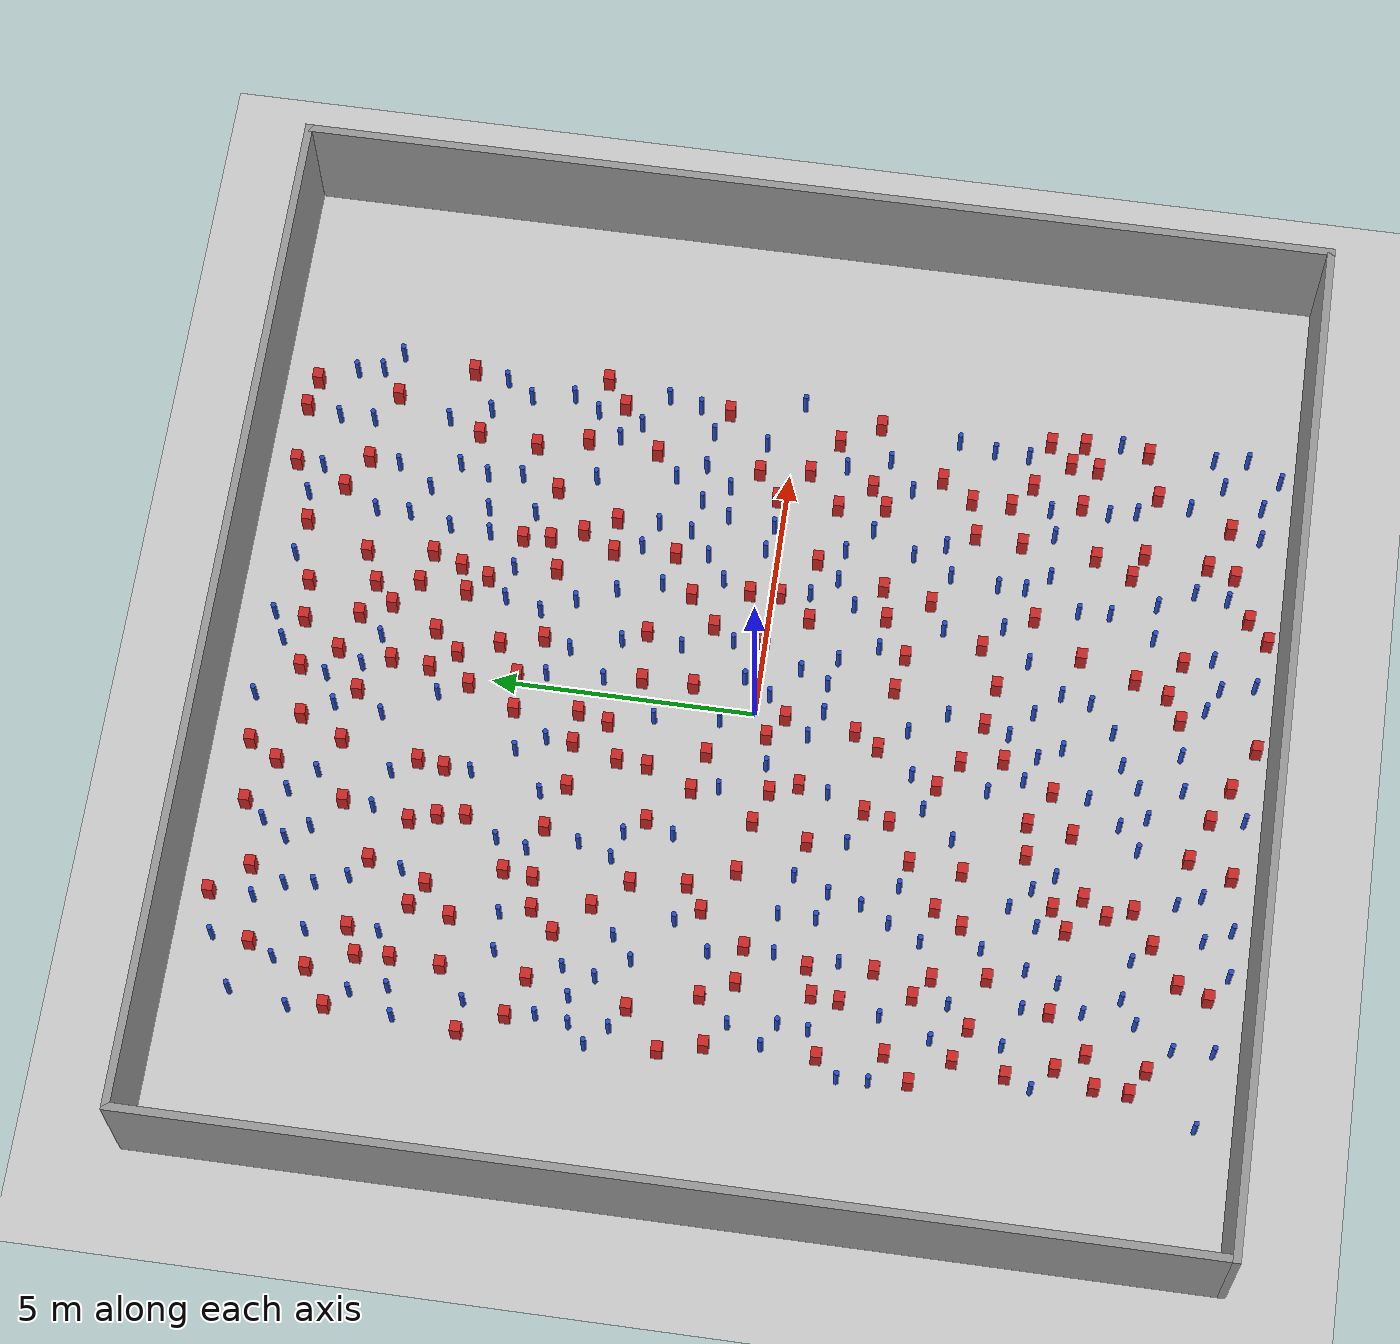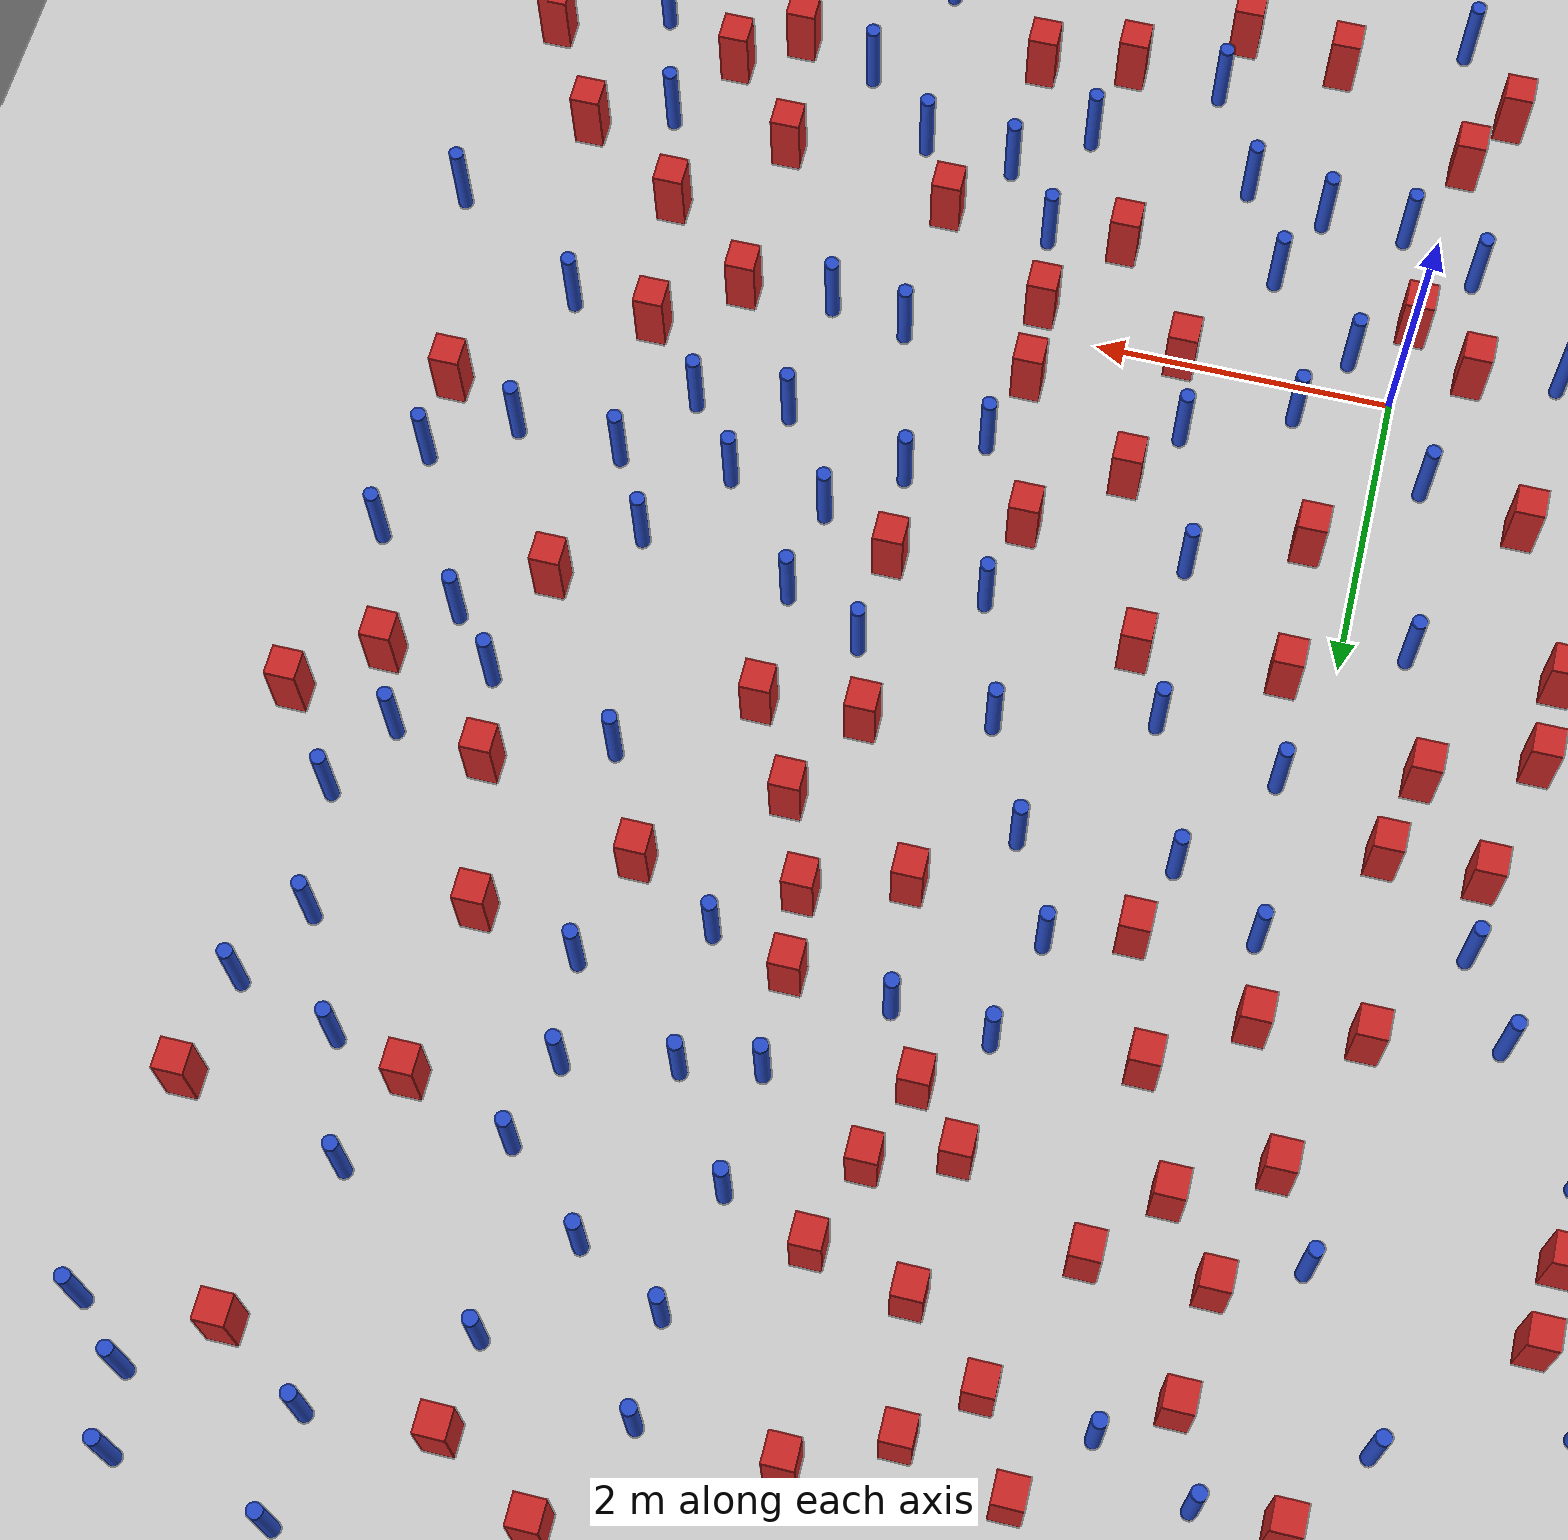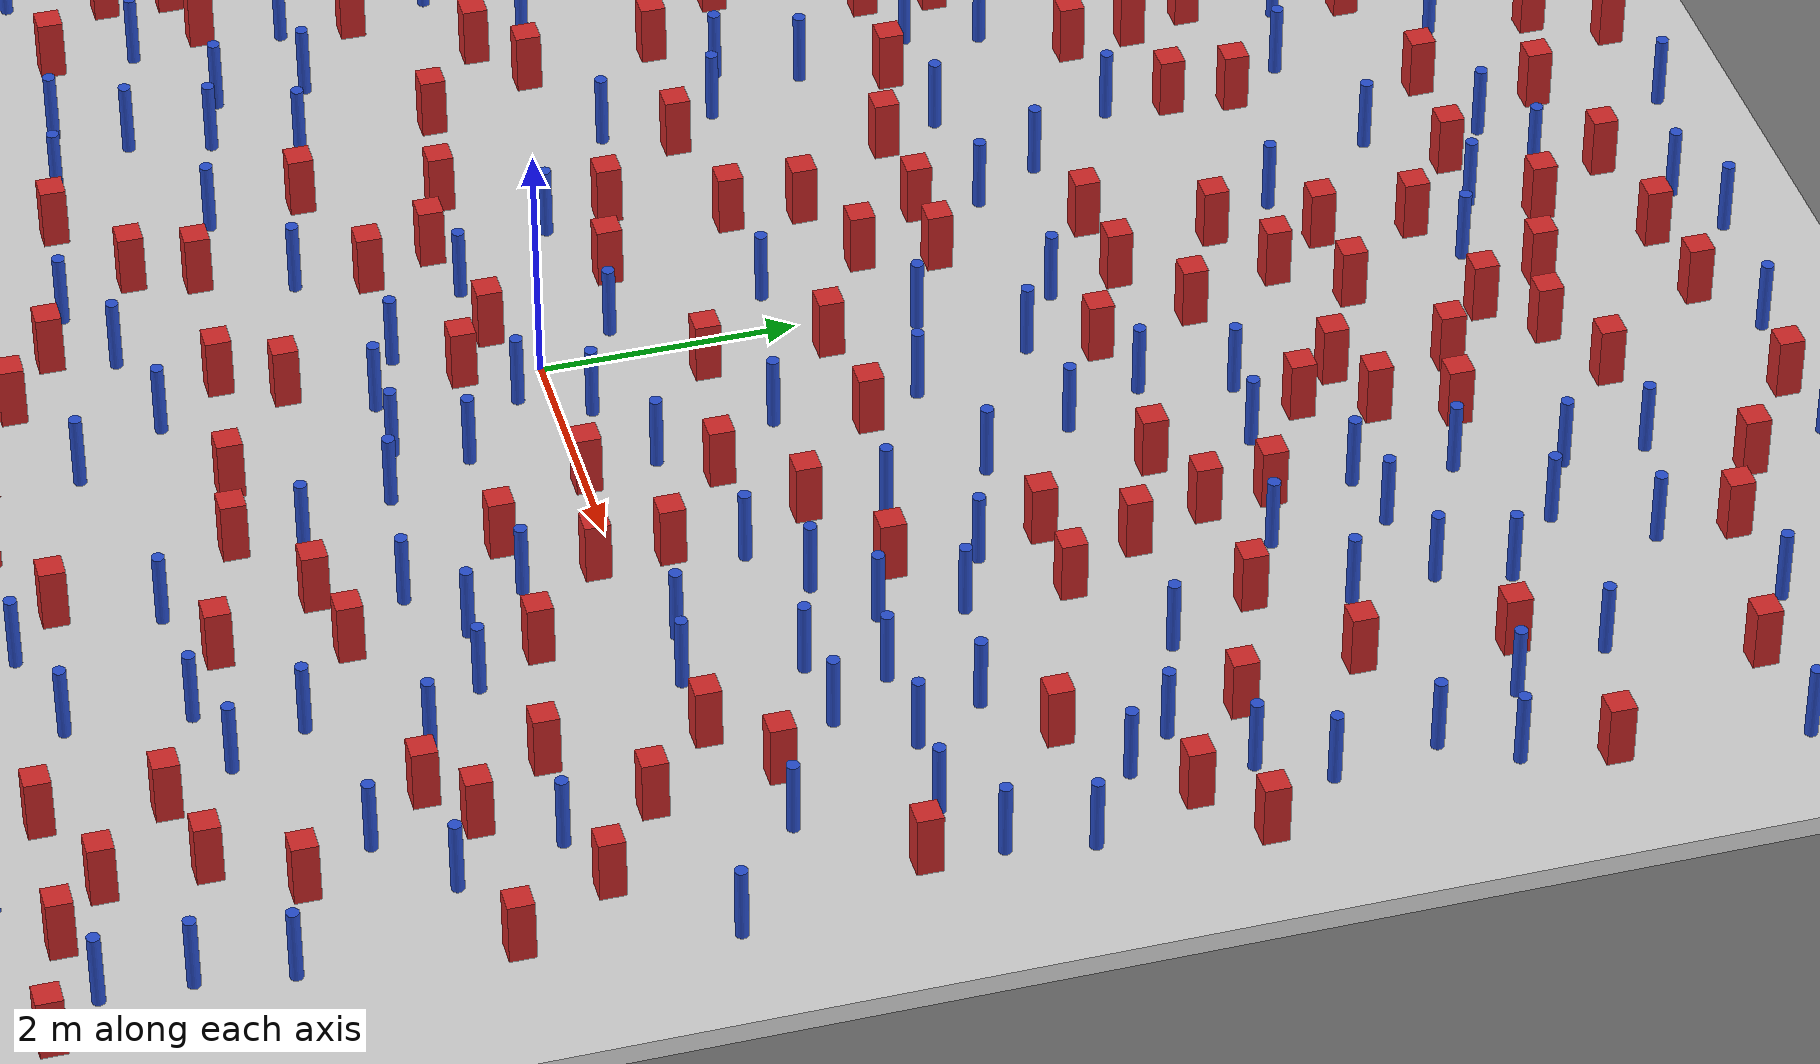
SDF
<sdf version="1.6">
 <world name="default">
  <light name="sun" type="directional">
   <pose>0 0 1000 0 -0 0</pose>
   <diffuse>0.8 0.8 0.8 1</diffuse>
   <specular>0.1 0.1 0.1 1</specular>
   <attenuation>
    <range>1000</range>
    <constant>0.9</constant>
    <linear>0.01</linear>
    <quadratic>0.001</quadratic>
   </attenuation>
   <direction>-0.5 0.5 -1</direction>
  </light>
  <model name="ground_plane">
   <static>1</static>
   <link name="link">
    <collision name="collision">
     <geometry><plane><normal>0 0 1</normal><size>100 100</size></plane></geometry>
     <surface><friction><ode><mu>100</mu><mu2>50</mu2></ode></friction></surface>
    </collision>
    <visual name="visual">
     <cast_shadows>0</cast_shadows>
     <geometry><plane><normal>0 0 1</normal><size>100 100</size></plane></geometry>
     <material>
      <ambient>1.0 1.0 1.0 1.0</ambient>
      <diffuse>0.8 0.8 0.8 1.0</diffuse>
      <specular>0.01 0.01 0.01 1.000000</specular>
     </material>
    </visual>
   </link>
  </model>
  <gravity>0 0 -9.8</gravity>
  <magnetic_field>6e-06 2.3e-05 -4.2e-05</magnetic_field>
  <atmosphere type="adiabatic"/>
  <physics name="default_physics" default="0" type="ode">
   <max_step_size>0.001</max_step_size>
   <real_time_factor>1</real_time_factor>
   <real_time_update_rate>1000</real_time_update_rate>
  </physics>
  <scene><ambient>0.4 0.4 0.4 1</ambient><background>0.7 0.7 0.7 1</background><shadows>1</shadows></scene>
  <spherical_coordinates>
   <surface_model>EARTH_WGS84</surface_model>
   <latitude_deg>0</latitude_deg>
   <longitude_deg>0</longitude_deg>
   <elevation>0</elevation>
   <heading_deg>0</heading_deg>
  </spherical_coordinates>
  <plugin name="gazebo_occupancy_map" filename="libgazebo_2Dmap_plugin.so">
   <map_resolution>0.05</map_resolution>
   <map_topic>generated_map</map_topic>
   <map_height>0.01</map_height>
   <map_size_x>50</map_size_x>
   <map_size_y>50</map_size_y>
  </plugin>
  <model name="NamedLocations">
   <static>true</static>
   <link name="DefaultStart"><pose>8.5 0 0 0 0 3.14</pose></link>
  </model>
  <model name="20x20_walls">
   <pose>0.044518 0.176112 0 0 -0 0</pose>
   <link name="Wall_1">
    <collision name="Wall_1_Collision">
     <geometry><box><size>20 0.15 2.5</size></box></geometry>
     <pose>0 0 1.25 0 -0 0</pose>
    </collision>
    <visual name="Wall_1_Visual">
     <pose>0 0 1.25 0 -0 0</pose>
     <geometry><box><size>20 0.15 2.5</size></box></geometry>
     <material>
      <script><uri>file://media/materials/scripts/gazebo.material</uri><name>Gazebo/Grey</name></script>
      <ambient>0.976471 0.992157 1 1</ambient>
     </material>
     <meta><layer>0</layer></meta>
    </visual>
    <pose>0 9.925 0 0 -0 0</pose>
   </link>
   <link name="Wall_3">
    <collision name="Wall_3_Collision">
     <geometry><box><size>20 0.15 2.5</size></box></geometry>
     <pose>0 0 1.25 0 -0 0</pose>
    </collision>
    <visual name="Wall_3_Visual">
     <pose>0 0 1.25 0 -0 0</pose>
     <geometry><box><size>20 0.15 2.5</size></box></geometry>
     <material>
      <script><uri>file://media/materials/scripts/gazebo.material</uri><name>Gazebo/Grey</name></script>
      <ambient>0.976471 0.992157 1 1</ambient>
     </material>
     <meta><layer>0</layer></meta>
    </visual>
    <pose>9.925 0 0 0 0 -1.5708</pose>
   </link>
   <link name="Wall_4">
    <collision name="Wall_4_Collision">
     <geometry><box><size>20 0.15 2.5</size></box></geometry>
     <pose>0 0 1.25 0 -0 0</pose>
    </collision>
    <visual name="Wall_4_Visual">
     <pose>0 0 1.25 0 -0 0</pose>
     <geometry><box><size>20 0.15 2.5</size></box></geometry>
     <material>
      <script><uri>file://media/materials/scripts/gazebo.material</uri><name>Gazebo/Grey</name></script>
      <ambient>0.976471 0.992157 1 1</ambient>
     </material>
     <meta><layer>0</layer></meta>
    </visual>
    <pose>0 -9.925 0 0 -0 3.14159</pose>
   </link>
   <link name="Wall_5">
    <collision name="Wall_5_Collision">
     <geometry><box><size>20 0.15 2.5</size></box></geometry>
     <pose>0 0 1.25 0 -0 0</pose>
    </collision>
    <visual name="Wall_5_Visual">
     <pose>0 0 1.25 0 -0 0</pose>
     <geometry><box><size>20 0.15 2.5</size></box></geometry>
     <material>
      <script><uri>file://media/materials/scripts/gazebo.material</uri><name>Gazebo/Grey</name></script>
      <ambient>0.976471 0.992157 1 1</ambient>
     </material>
     <meta><layer>0</layer></meta>
    </visual>
    <pose>-9.925 0 0 0 -0 1.5708</pose>
   </link>
   <static>1</static>
  </model>
  <model name="square_post_obstacle0">
   <static>true</static>
   <pose>-3.86595991836 3.60557154821 1.91545236811e-07 -7.35059704564e-06 1.12565212e-07 2.39332434364e-05</pose>
   <link name="link">
    <pose>0 0 0.25 0 -0 0</pose>
    <inertial>
     <mass>100</mass>
     <inertia>
      <ixx>0.166667</ixx>
      <ixy>0</ixy>
      <ixz>0</ixz>
      <iyy>0.166667</iyy>
      <iyz>0</iyz>
      <izz>0.166667</izz>
     </inertia>
    </inertial>
    <collision name="collision"><geometry><box><size>.2 .2 .5</size></box></geometry></collision>
    <visual name="visual">
     <geometry><box><size>.2 .2 .5</size></box></geometry>
     <material>
      <script><name>Gazebo/Red</name><uri>file://media/materials/scripts/gazebo.material</uri></script>
     </material>
    </visual>
   </link>
  </model>
  <model name="square_post_obstacle1">
   <static>true</static>
   <pose>5.06499883249 -0.397091042828 1.91545236811e-07 -7.35059704564e-06 1.12565212e-07 2.39332434364e-05</pose>
   <link name="link">
    <pose>0 0 0.25 0 -0 0</pose>
    <inertial>
     <mass>100</mass>
     <inertia>
      <ixx>0.166667</ixx>
      <ixy>0</ixy>
      <ixz>0</ixz>
      <iyy>0.166667</iyy>
      <iyz>0</iyz>
      <izz>0.166667</izz>
     </inertia>
    </inertial>
    <collision name="collision"><geometry><box><size>.2 .2 .5</size></box></geometry></collision>
    <visual name="visual">
     <geometry><box><size>.2 .2 .5</size></box></geometry>
     <material>
      <script><name>Gazebo/Red</name><uri>file://media/materials/scripts/gazebo.material</uri></script>
     </material>
    </visual>
   </link>
  </model>
  <model name="pole_obstacle0">
   <static>true</static>
   <pose>-6.93956800883 -2.45011283821 7.38925637345e-09 -8.47170692798e-08 1.24976764937e-08 -1.74513093023e-07</pose>
   <link name="link">
    <pose>0 0 0.3 0 -0 0</pose>
    <inertial>
     <mass>1</mass>
     <inertia><ixx>0.145833</ixx><ixy>0</ixy><ixz>0</ixz><iyy>0.145833</iyy><iyz>0</iyz><izz>0.125</izz></inertia>
    </inertial>
    <collision name="collision">
     <geometry><cylinder><radius>0.05</radius><length>.6</length></cylinder></geometry>
    </collision>
    <visual name="visual">
     <geometry><cylinder><radius>0.05</radius><length>.6</length></cylinder></geometry>
     <material>
      <script><name>Gazebo/Blue</name><uri>file://media/materials/scripts/gazebo.material</uri></script>
     </material>
    </visual>
   </link>
  </model>
  <model name="square_post_obstacle2">
   <static>true</static>
   <pose>-2.89572742521 5.56003379389 1.91545236811e-07 -7.35059704564e-06 1.12565212e-07 2.39332434364e-05</pose>
   <link name="link">
    <pose>0 0 0.25 0 -0 0</pose>
    <inertial>
     <mass>100</mass>
     <inertia>
      <ixx>0.166667</ixx>
      <ixy>0</ixy>
      <ixz>0</ixz>
      <iyy>0.166667</iyy>
      <iyz>0</iyz>
      <izz>0.166667</izz>
     </inertia>
    </inertial>
    <collision name="collision"><geometry><box><size>.2 .2 .5</size></box></geometry></collision>
    <visual name="visual">
     <geometry><box><size>.2 .2 .5</size></box></geometry>
     <material>
      <script><name>Gazebo/Red</name><uri>file://media/materials/scripts/gazebo.material</uri></script>
     </material>
    </visual>
   </link>
  </model>
  <model name="pole_obstacle1">
   <static>true</static>
   <pose>-2.57879591383 -8.69562706285 7.38925637345e-09 -8.47170692793e-08 1.24976764408e-08 -1.74513093041e-07</pose>
   <link name="link">
    <pose>0 0 0.3 0 -0 0</pose>
    <inertial>
     <mass>1</mass>
     <inertia><ixx>0.145833</ixx><ixy>0</ixy><ixz>0</ixz><iyy>0.145833</iyy><iyz>0</iyz><izz>0.125</izz></inertia>
    </inertial>
    <collision name="collision">
     <geometry><cylinder><radius>0.05</radius><length>.6</length></cylinder></geometry>
    </collision>
    <visual name="visual">
     <geometry><cylinder><radius>0.05</radius><length>.6</length></cylinder></geometry>
     <material>
      <script><name>Gazebo/Blue</name><uri>file://media/materials/scripts/gazebo.material</uri></script>
     </material>
    </visual>
   </link>
  </model>
  <model name="square_post_obstacle3">
   <static>true</static>
   <pose>2.59659888073 -5.01492910549 1.91545236811e-07 -7.35059704564e-06 1.12565212e-07 2.39332434364e-05</pose>
   <link name="link">
    <pose>0 0 0.25 0 -0 0</pose>
    <inertial>
     <mass>100</mass>
     <inertia>
      <ixx>0.166667</ixx>
      <ixy>0</ixy>
      <ixz>0</ixz>
      <iyy>0.166667</iyy>
      <iyz>0</iyz>
      <izz>0.166667</izz>
     </inertia>
    </inertial>
    <collision name="collision"><geometry><box><size>.2 .2 .5</size></box></geometry></collision>
    <visual name="visual">
     <geometry><box><size>.2 .2 .5</size></box></geometry>
     <material>
      <script><name>Gazebo/Red</name><uri>file://media/materials/scripts/gazebo.material</uri></script>
     </material>
    </visual>
   </link>
  </model>
  <model name="pole_obstacle2">
   <static>true</static>
   <pose>2.45349405311 -7.29961357924 7.38925637345e-09 -8.47170692798e-08 1.24976765033e-08 -1.74513093019e-07</pose>
   <link name="link">
    <pose>0 0 0.3 0 -0 0</pose>
    <inertial>
     <mass>1</mass>
     <inertia><ixx>0.145833</ixx><ixy>0</ixy><ixz>0</ixz><iyy>0.145833</iyy><iyz>0</iyz><izz>0.125</izz></inertia>
    </inertial>
    <collision name="collision">
     <geometry><cylinder><radius>0.05</radius><length>.6</length></cylinder></geometry>
    </collision>
    <visual name="visual">
     <geometry><cylinder><radius>0.05</radius><length>.6</length></cylinder></geometry>
     <material>
      <script><name>Gazebo/Blue</name><uri>file://media/materials/scripts/gazebo.material</uri></script>
     </material>
    </visual>
   </link>
  </model>
  <model name="pole_obstacle3">
   <static>true</static>
   <pose>-4.05855191227 6.03267944209 7.38925637345e-09 -8.47170692796e-08 1.24976764786e-08 -1.74513093032e-07</pose>
   <link name="link">
    <pose>0 0 0.3 0 -0 0</pose>
    <inertial>
     <mass>1</mass>
     <inertia><ixx>0.145833</ixx><ixy>0</ixy><ixz>0</ixz><iyy>0.145833</iyy><iyz>0</iyz><izz>0.125</izz></inertia>
    </inertial>
    <collision name="collision">
     <geometry><cylinder><radius>0.05</radius><length>.6</length></cylinder></geometry>
    </collision>
    <visual name="visual">
     <geometry><cylinder><radius>0.05</radius><length>.6</length></cylinder></geometry>
     <material>
      <script><name>Gazebo/Blue</name><uri>file://media/materials/scripts/gazebo.material</uri></script>
     </material>
    </visual>
   </link>
  </model>
  <model name="square_post_obstacle4">
   <static>true</static>
   <pose>4.12188741127 -8.18396951144 1.91545236811e-07 -7.35059704564e-06 1.12565212e-07 2.39332434364e-05</pose>
   <link name="link">
    <pose>0 0 0.25 0 -0 0</pose>
    <inertial>
     <mass>100</mass>
     <inertia>
      <ixx>0.166667</ixx>
      <ixy>0</ixy>
      <ixz>0</ixz>
      <iyy>0.166667</iyy>
      <iyz>0</iyz>
      <izz>0.166667</izz>
     </inertia>
    </inertial>
    <collision name="collision"><geometry><box><size>.2 .2 .5</size></box></geometry></collision>
    <visual name="visual">
     <geometry><box><size>.2 .2 .5</size></box></geometry>
     <material>
      <script><name>Gazebo/Red</name><uri>file://media/materials/scripts/gazebo.material</uri></script>
     </material>
    </visual>
   </link>
  </model>
  <model name="square_post_obstacle5">
   <static>true</static>
   <pose>-6.35266890783 -3.25034243119 1.91545236811e-07 -7.35059704564e-06 1.12565212e-07 2.39332434364e-05</pose>
   <link name="link">
    <pose>0 0 0.25 0 -0 0</pose>
    <inertial>
     <mass>100</mass>
     <inertia>
      <ixx>0.166667</ixx>
      <ixy>0</ixy>
      <ixz>0</ixz>
      <iyy>0.166667</iyy>
      <iyz>0</iyz>
      <izz>0.166667</izz>
     </inertia>
    </inertial>
    <collision name="collision"><geometry><box><size>.2 .2 .5</size></box></geometry></collision>
    <visual name="visual">
     <geometry><box><size>.2 .2 .5</size></box></geometry>
     <material>
      <script><name>Gazebo/Red</name><uri>file://media/materials/scripts/gazebo.material</uri></script>
     </material>
    </visual>
   </link>
  </model>
  <model name="square_post_obstacle6">
   <static>true</static>
   <pose>1.60942425085 0.988054612584 1.91545236811e-07 -7.35059704564e-06 1.12565212e-07 2.39332434364e-05</pose>
   <link name="link">
    <pose>0 0 0.25 0 -0 0</pose>
    <inertial>
     <mass>100</mass>
     <inertia>
      <ixx>0.166667</ixx>
      <ixy>0</ixy>
      <ixz>0</ixz>
      <iyy>0.166667</iyy>
      <iyz>0</iyz>
      <izz>0.166667</izz>
     </inertia>
    </inertial>
    <collision name="collision"><geometry><box><size>.2 .2 .5</size></box></geometry></collision>
    <visual name="visual">
     <geometry><box><size>.2 .2 .5</size></box></geometry>
     <material>
      <script><name>Gazebo/Red</name><uri>file://media/materials/scripts/gazebo.material</uri></script>
     </material>
    </visual>
   </link>
  </model>
  <model name="pole_obstacle4">
   <static>true</static>
   <pose>-4.62733506673 8.13093342007 7.38925637345e-09 -8.471706928e-08 1.24976765081e-08 -1.74513093015e-07</pose>
   <link name="link">
    <pose>0 0 0.3 0 -0 0</pose>
    <inertial>
     <mass>1</mass>
     <inertia><ixx>0.145833</ixx><ixy>0</ixy><ixz>0</ixz><iyy>0.145833</iyy><iyz>0</iyz><izz>0.125</izz></inertia>
    </inertial>
    <collision name="collision">
     <geometry><cylinder><radius>0.05</radius><length>.6</length></cylinder></geometry>
    </collision>
    <visual name="visual">
     <geometry><cylinder><radius>0.05</radius><length>.6</length></cylinder></geometry>
     <material>
      <script><name>Gazebo/Blue</name><uri>file://media/materials/scripts/gazebo.material</uri></script>
     </material>
    </visual>
   </link>
  </model>
  <model name="pole_obstacle5">
   <static>true</static>
   <pose>-3.44873347191 -8.79434846552 7.38925637345e-09 -8.47170692799e-08 1.24976765012e-08 -1.74513093021e-07</pose>
   <link name="link">
    <pose>0 0 0.3 0 -0 0</pose>
    <inertial>
     <mass>1</mass>
     <inertia><ixx>0.145833</ixx><ixy>0</ixy><ixz>0</ixz><iyy>0.145833</iyy><iyz>0</iyz><izz>0.125</izz></inertia>
    </inertial>
    <collision name="collision">
     <geometry><cylinder><radius>0.05</radius><length>.6</length></cylinder></geometry>
    </collision>
    <visual name="visual">
     <geometry><cylinder><radius>0.05</radius><length>.6</length></cylinder></geometry>
     <material>
      <script><name>Gazebo/Blue</name><uri>file://media/materials/scripts/gazebo.material</uri></script>
     </material>
    </visual>
   </link>
  </model>
  <model name="square_post_obstacle7">
   <static>true</static>
   <pose>-0.484492980676 -0.290630874998 1.91545236811e-07 -7.35059704564e-06 1.12565212e-07 2.39332434364e-05</pose>
   <link name="link">
    <pose>0 0 0.25 0 -0 0</pose>
    <inertial>
     <mass>100</mass>
     <inertia>
      <ixx>0.166667</ixx>
      <ixy>0</ixy>
      <ixz>0</ixz>
      <iyy>0.166667</iyy>
      <iyz>0</iyz>
      <izz>0.166667</izz>
     </inertia>
    </inertial>
    <collision name="collision"><geometry><box><size>.2 .2 .5</size></box></geometry></collision>
    <visual name="visual">
     <geometry><box><size>.2 .2 .5</size></box></geometry>
     <material>
      <script><name>Gazebo/Red</name><uri>file://media/materials/scripts/gazebo.material</uri></script>
     </material>
    </visual>
   </link>
  </model>
  <model name="square_post_obstacle8">
   <static>true</static>
   <pose>4.03454843956 4.36539014241 1.91545236811e-07 -7.35059704564e-06 1.12565212e-07 2.39332434364e-05</pose>
   <link name="link">
    <pose>0 0 0.25 0 -0 0</pose>
    <inertial>
     <mass>100</mass>
     <inertia>
      <ixx>0.166667</ixx>
      <ixy>0</ixy>
      <ixz>0</ixz>
      <iyy>0.166667</iyy>
      <iyz>0</iyz>
      <izz>0.166667</izz>
     </inertia>
    </inertial>
    <collision name="collision"><geometry><box><size>.2 .2 .5</size></box></geometry></collision>
    <visual name="visual">
     <geometry><box><size>.2 .2 .5</size></box></geometry>
     <material>
      <script><name>Gazebo/Red</name><uri>file://media/materials/scripts/gazebo.material</uri></script>
     </material>
    </visual>
   </link>
  </model>
  <model name="pole_obstacle6">
   <static>true</static>
   <pose>1.57511094073 -2.17022397496 7.38925637345e-09 -8.47170692799e-08 1.24976765053e-08 -1.74513093017e-07</pose>
   <link name="link">
    <pose>0 0 0.3 0 -0 0</pose>
    <inertial>
     <mass>1</mass>
     <inertia><ixx>0.145833</ixx><ixy>0</ixy><ixz>0</ixz><iyy>0.145833</iyy><iyz>0</iyz><izz>0.125</izz></inertia>
    </inertial>
    <collision name="collision">
     <geometry><cylinder><radius>0.05</radius><length>.6</length></cylinder></geometry>
    </collision>
    <visual name="visual">
     <geometry><cylinder><radius>0.05</radius><length>.6</length></cylinder></geometry>
     <material>
      <script><name>Gazebo/Blue</name><uri>file://media/materials/scripts/gazebo.material</uri></script>
     </material>
    </visual>
   </link>
  </model>
  <model name="pole_obstacle7">
   <static>true</static>
   <pose>3.45818707849 4.71534439706 7.38925637345e-09 -8.47170692798e-08 1.24976765033e-08 -1.74513093019e-07</pose>
   <link name="link">
    <pose>0 0 0.3 0 -0 0</pose>
    <inertial>
     <mass>1</mass>
     <inertia><ixx>0.145833</ixx><ixy>0</ixy><ixz>0</ixz><iyy>0.145833</iyy><iyz>0</iyz><izz>0.125</izz></inertia>
    </inertial>
    <collision name="collision">
     <geometry><cylinder><radius>0.05</radius><length>.6</length></cylinder></geometry>
    </collision>
    <visual name="visual">
     <geometry><cylinder><radius>0.05</radius><length>.6</length></cylinder></geometry>
     <material>
      <script><name>Gazebo/Blue</name><uri>file://media/materials/scripts/gazebo.material</uri></script>
     </material>
    </visual>
   </link>
  </model>
  <model name="square_post_obstacle9">
   <static>true</static>
   <pose>-4.67292048843 -0.449817612617 1.91545236811e-07 -7.35059704564e-06 1.12565212e-07 2.39332434364e-05</pose>
   <link name="link">
    <pose>0 0 0.25 0 -0 0</pose>
    <inertial>
     <mass>100</mass>
     <inertia>
      <ixx>0.166667</ixx>
      <ixy>0</ixy>
      <ixz>0</ixz>
      <iyy>0.166667</iyy>
      <iyz>0</iyz>
      <izz>0.166667</izz>
     </inertia>
    </inertial>
    <collision name="collision"><geometry><box><size>.2 .2 .5</size></box></geometry></collision>
    <visual name="visual">
     <geometry><box><size>.2 .2 .5</size></box></geometry>
     <material>
      <script><name>Gazebo/Red</name><uri>file://media/materials/scripts/gazebo.material</uri></script>
     </material>
    </visual>
   </link>
  </model>
  <model name="square_post_obstacle10">
   <static>true</static>
   <pose>0.782432085454 -2.56080963063 1.91545236811e-07 -7.35059704564e-06 1.12565212e-07 2.39332434364e-05</pose>
   <link name="link">
    <pose>0 0 0.25 0 -0 0</pose>
    <inertial>
     <mass>100</mass>
     <inertia>
      <ixx>0.166667</ixx>
      <ixy>0</ixy>
      <ixz>0</ixz>
      <iyy>0.166667</iyy>
      <iyz>0</iyz>
      <izz>0.166667</izz>
     </inertia>
    </inertial>
    <collision name="collision"><geometry><box><size>.2 .2 .5</size></box></geometry></collision>
    <visual name="visual">
     <geometry><box><size>.2 .2 .5</size></box></geometry>
     <material>
      <script><name>Gazebo/Red</name><uri>file://media/materials/scripts/gazebo.material</uri></script>
     </material>
    </visual>
   </link>
  </model>
  <model name="square_post_obstacle11">
   <static>true</static>
   <pose>-6.49012242165 -7.72801190302 1.91545236811e-07 -7.35059704564e-06 1.12565212e-07 2.39332434364e-05</pose>
   <link name="link">
    <pose>0 0 0.25 0 -0 0</pose>
    <inertial>
     <mass>100</mass>
     <inertia>
      <ixx>0.166667</ixx>
      <ixy>0</ixy>
      <ixz>0</ixz>
      <iyy>0.166667</iyy>
      <iyz>0</iyz>
      <izz>0.166667</izz>
     </inertia>
    </inertial>
    <collision name="collision"><geometry><box><size>.2 .2 .5</size></box></geometry></collision>
    <visual name="visual">
     <geometry><box><size>.2 .2 .5</size></box></geometry>
     <material>
      <script><name>Gazebo/Red</name><uri>file://media/materials/scripts/gazebo.material</uri></script>
     </material>
    </visual>
   </link>
  </model>
  <model name="square_post_obstacle12">
   <static>true</static>
   <pose>2.42420450844 -0.160747507718 1.91545236811e-07 -7.35059704564e-06 1.12565212e-07 2.39332434364e-05</pose>
   <link name="link">
    <pose>0 0 0.25 0 -0 0</pose>
    <inertial>
     <mass>100</mass>
     <inertia>
      <ixx>0.166667</ixx>
      <ixy>0</ixy>
      <ixz>0</ixz>
      <iyy>0.166667</iyy>
      <iyz>0</iyz>
      <izz>0.166667</izz>
     </inertia>
    </inertial>
    <collision name="collision"><geometry><box><size>.2 .2 .5</size></box></geometry></collision>
    <visual name="visual">
     <geometry><box><size>.2 .2 .5</size></box></geometry>
     <material>
      <script><name>Gazebo/Red</name><uri>file://media/materials/scripts/gazebo.material</uri></script>
     </material>
    </visual>
   </link>
  </model>
  <model name="square_post_obstacle13">
   <static>true</static>
   <pose>-3.56713020802 -6.26825486642 1.91545236811e-07 -7.35059704564e-06 1.12565212e-07 2.39332434364e-05</pose>
   <link name="link">
    <pose>0 0 0.25 0 -0 0</pose>
    <inertial>
     <mass>100</mass>
     <inertia>
      <ixx>0.166667</ixx>
      <ixy>0</ixy>
      <ixz>0</ixz>
      <iyy>0.166667</iyy>
      <iyz>0</iyz>
      <izz>0.166667</izz>
     </inertia>
    </inertial>
    <collision name="collision"><geometry><box><size>.2 .2 .5</size></box></geometry></collision>
    <visual name="visual">
     <geometry><box><size>.2 .2 .5</size></box></geometry>
     <material>
      <script><name>Gazebo/Red</name><uri>file://media/materials/scripts/gazebo.material</uri></script>
     </material>
    </visual>
   </link>
  </model>
  <model name="pole_obstacle8">
   <static>true</static>
   <pose>-2.78137259823 2.06912645581 7.38925637345e-09 -8.47170692798e-08 1.24976764939e-08 -1.74513093025e-07</pose>
   <link name="link">
    <pose>0 0 0.3 0 -0 0</pose>
    <inertial>
     <mass>1</mass>
     <inertia><ixx>0.145833</ixx><ixy>0</ixy><ixz>0</ixz><iyy>0.145833</iyy><iyz>0</iyz><izz>0.125</izz></inertia>
    </inertial>
    <collision name="collision">
     <geometry><cylinder><radius>0.05</radius><length>.6</length></cylinder></geometry>
    </collision>
    <visual name="visual">
     <geometry><cylinder><radius>0.05</radius><length>.6</length></cylinder></geometry>
     <material>
      <script><name>Gazebo/Blue</name><uri>file://media/materials/scripts/gazebo.material</uri></script>
     </material>
    </visual>
   </link>
  </model>
  <model name="square_post_obstacle14">
   <static>true</static>
   <pose>-5.752765113 5.96022098293 1.91545236811e-07 -7.35059704564e-06 1.12565212e-07 2.39332434364e-05</pose>
   <link name="link">
    <pose>0 0 0.25 0 -0 0</pose>
    <inertial>
     <mass>100</mass>
     <inertia>
      <ixx>0.166667</ixx>
      <ixy>0</ixy>
      <ixz>0</ixz>
      <iyy>0.166667</iyy>
      <iyz>0</iyz>
      <izz>0.166667</izz>
     </inertia>
    </inertial>
    <collision name="collision"><geometry><box><size>.2 .2 .5</size></box></geometry></collision>
    <visual name="visual">
     <geometry><box><size>.2 .2 .5</size></box></geometry>
     <material>
      <script><name>Gazebo/Red</name><uri>file://media/materials/scripts/gazebo.material</uri></script>
     </material>
    </visual>
   </link>
  </model>
  <model name="square_post_obstacle15">
   <static>true</static>
   <pose>5.98368402551 3.34213384445 1.91545236811e-07 -7.35059704564e-06 1.12565212e-07 2.39332434364e-05</pose>
   <link name="link">
    <pose>0 0 0.25 0 -0 0</pose>
    <inertial>
     <mass>100</mass>
     <inertia>
      <ixx>0.166667</ixx>
      <ixy>0</ixy>
      <ixz>0</ixz>
      <iyy>0.166667</iyy>
      <iyz>0</iyz>
      <izz>0.166667</izz>
     </inertia>
    </inertial>
    <collision name="collision"><geometry><box><size>.2 .2 .5</size></box></geometry></collision>
    <visual name="visual">
     <geometry><box><size>.2 .2 .5</size></box></geometry>
     <material>
      <script><name>Gazebo/Red</name><uri>file://media/materials/scripts/gazebo.material</uri></script>
     </material>
    </visual>
   </link>
  </model>
  <model name="square_post_obstacle16">
   <static>true</static>
   <pose>-2.20791887545 8.71867321994 1.91545236811e-07 -7.35059704564e-06 1.12565212e-07 2.39332434364e-05</pose>
   <link name="link">
    <pose>0 0 0.25 0 -0 0</pose>
    <inertial>
     <mass>100</mass>
     <inertia>
      <ixx>0.166667</ixx>
      <ixy>0</ixy>
      <ixz>0</ixz>
      <iyy>0.166667</iyy>
      <iyz>0</iyz>
      <izz>0.166667</izz>
     </inertia>
    </inertial>
    <collision name="collision"><geometry><box><size>.2 .2 .5</size></box></geometry></collision>
    <visual name="visual">
     <geometry><box><size>.2 .2 .5</size></box></geometry>
     <material>
      <script><name>Gazebo/Red</name><uri>file://media/materials/scripts/gazebo.material</uri></script>
     </material>
    </visual>
   </link>
  </model>
  <model name="pole_obstacle9">
   <static>true</static>
   <pose>3.57325303484 2.32983173378 7.38925637345e-09 -8.47170692798e-08 1.24976764939e-08 -1.74513093025e-07</pose>
   <link name="link">
    <pose>0 0 0.3 0 -0 0</pose>
    <inertial>
     <mass>1</mass>
     <inertia><ixx>0.145833</ixx><ixy>0</ixy><ixz>0</ixz><iyy>0.145833</iyy><iyz>0</iyz><izz>0.125</izz></inertia>
    </inertial>
    <collision name="collision">
     <geometry><cylinder><radius>0.05</radius><length>.6</length></cylinder></geometry>
    </collision>
    <visual name="visual">
     <geometry><cylinder><radius>0.05</radius><length>.6</length></cylinder></geometry>
     <material>
      <script><name>Gazebo/Blue</name><uri>file://media/materials/scripts/gazebo.material</uri></script>
     </material>
    </visual>
   </link>
  </model>
  <model name="square_post_obstacle17">
   <static>true</static>
   <pose>2.98692828114 4.34356148915 1.91545236811e-07 -7.35059704564e-06 1.12565212e-07 2.39332434364e-05</pose>
   <link name="link">
    <pose>0 0 0.25 0 -0 0</pose>
    <inertial>
     <mass>100</mass>
     <inertia>
      <ixx>0.166667</ixx>
      <ixy>0</ixy>
      <ixz>0</ixz>
      <iyy>0.166667</iyy>
      <iyz>0</iyz>
      <izz>0.166667</izz>
     </inertia>
    </inertial>
    <collision name="collision"><geometry><box><size>.2 .2 .5</size></box></geometry></collision>
    <visual name="visual">
     <geometry><box><size>.2 .2 .5</size></box></geometry>
     <material>
      <script><name>Gazebo/Red</name><uri>file://media/materials/scripts/gazebo.material</uri></script>
     </material>
    </visual>
   </link>
  </model>
  <model name="square_post_obstacle18">
   <static>true</static>
   <pose>-6.46231089994 -5.47026156269 1.91545236811e-07 -7.35059704564e-06 1.12565212e-07 2.39332434364e-05</pose>
   <link name="link">
    <pose>0 0 0.25 0 -0 0</pose>
    <inertial>
     <mass>100</mass>
     <inertia>
      <ixx>0.166667</ixx>
      <ixy>0</ixy>
      <ixz>0</ixz>
      <iyy>0.166667</iyy>
      <iyz>0</iyz>
      <izz>0.166667</izz>
     </inertia>
    </inertial>
    <collision name="collision"><geometry><box><size>.2 .2 .5</size></box></geometry></collision>
    <visual name="visual">
     <geometry><box><size>.2 .2 .5</size></box></geometry>
     <material>
      <script><name>Gazebo/Red</name><uri>file://media/materials/scripts/gazebo.material</uri></script>
     </material>
    </visual>
   </link>
  </model>
  <model name="pole_obstacle10">
   <static>true</static>
   <pose>-0.384061834778 8.11439856965 7.38925637345e-09 -8.47170692796e-08 1.24976764724e-08 -1.74513093036e-07</pose>
   <link name="link">
    <pose>0 0 0.3 0 -0 0</pose>
    <inertial>
     <mass>1</mass>
     <inertia><ixx>0.145833</ixx><ixy>0</ixy><ixz>0</ixz><iyy>0.145833</iyy><iyz>0</iyz><izz>0.125</izz></inertia>
    </inertial>
    <collision name="collision">
     <geometry><cylinder><radius>0.05</radius><length>.6</length></cylinder></geometry>
    </collision>
    <visual name="visual">
     <geometry><cylinder><radius>0.05</radius><length>.6</length></cylinder></geometry>
     <material>
      <script><name>Gazebo/Blue</name><uri>file://media/materials/scripts/gazebo.material</uri></script>
     </material>
    </visual>
   </link>
  </model>
  <model name="square_post_obstacle19">
   <static>true</static>
   <pose>4.10246353803 -4.61326144353 1.91545236811e-07 -7.35059704564e-06 1.12565212e-07 2.39332434364e-05</pose>
   <link name="link">
    <pose>0 0 0.25 0 -0 0</pose>
    <inertial>
     <mass>100</mass>
     <inertia>
      <ixx>0.166667</ixx>
      <ixy>0</ixy>
      <ixz>0</ixz>
      <iyy>0.166667</iyy>
      <iyz>0</iyz>
      <izz>0.166667</izz>
     </inertia>
    </inertial>
    <collision name="collision"><geometry><box><size>.2 .2 .5</size></box></geometry></collision>
    <visual name="visual">
     <geometry><box><size>.2 .2 .5</size></box></geometry>
     <material>
      <script><name>Gazebo/Red</name><uri>file://media/materials/scripts/gazebo.material</uri></script>
     </material>
    </visual>
   </link>
  </model>
  <model name="pole_obstacle11">
   <static>true</static>
   <pose>-0.41434500545 1.84749491106 7.38925637345e-09 -8.47170692798e-08 1.24976765025e-08 -1.74513093018e-07</pose>
   <link name="link">
    <pose>0 0 0.3 0 -0 0</pose>
    <inertial>
     <mass>1</mass>
     <inertia><ixx>0.145833</ixx><ixy>0</ixy><ixz>0</ixz><iyy>0.145833</iyy><iyz>0</iyz><izz>0.125</izz></inertia>
    </inertial>
    <collision name="collision">
     <geometry><cylinder><radius>0.05</radius><length>.6</length></cylinder></geometry>
    </collision>
    <visual name="visual">
     <geometry><cylinder><radius>0.05</radius><length>.6</length></cylinder></geometry>
     <material>
      <script><name>Gazebo/Blue</name><uri>file://media/materials/scripts/gazebo.material</uri></script>
     </material>
    </visual>
   </link>
  </model>
  <model name="square_post_obstacle20">
   <static>true</static>
   <pose>0.706519905904 8.71554573499 1.91545236811e-07 -7.35059704564e-06 1.12565212e-07 2.39332434364e-05</pose>
   <link name="link">
    <pose>0 0 0.25 0 -0 0</pose>
    <inertial>
     <mass>100</mass>
     <inertia>
      <ixx>0.166667</ixx>
      <ixy>0</ixy>
      <ixz>0</ixz>
      <iyy>0.166667</iyy>
      <iyz>0</iyz>
      <izz>0.166667</izz>
     </inertia>
    </inertial>
    <collision name="collision"><geometry><box><size>.2 .2 .5</size></box></geometry></collision>
    <visual name="visual">
     <geometry><box><size>.2 .2 .5</size></box></geometry>
     <material>
      <script><name>Gazebo/Red</name><uri>file://media/materials/scripts/gazebo.material</uri></script>
     </material>
    </visual>
   </link>
  </model>
  <model name="pole_obstacle12">
   <static>true</static>
   <pose>-1.17433486913 -7.53780862693 7.38925637345e-09 -8.47170692799e-08 1.24976765033e-08 -1.74513093018e-07</pose>
   <link name="link">
    <pose>0 0 0.3 0 -0 0</pose>
    <inertial>
     <mass>1</mass>
     <inertia><ixx>0.145833</ixx><ixy>0</ixy><ixz>0</ixz><iyy>0.145833</iyy><iyz>0</iyz><izz>0.125</izz></inertia>
    </inertial>
    <collision name="collision">
     <geometry><cylinder><radius>0.05</radius><length>.6</length></cylinder></geometry>
    </collision>
    <visual name="visual">
     <geometry><cylinder><radius>0.05</radius><length>.6</length></cylinder></geometry>
     <material>
      <script><name>Gazebo/Blue</name><uri>file://media/materials/scripts/gazebo.material</uri></script>
     </material>
    </visual>
   </link>
  </model>
  <model name="square_post_obstacle21">
   <static>true</static>
   <pose>5.45114207731 -7.09596721696 1.91545236811e-07 -7.35059704564e-06 1.12565212e-07 2.39332434364e-05</pose>
   <link name="link">
    <pose>0 0 0.25 0 -0 0</pose>
    <inertial>
     <mass>100</mass>
     <inertia>
      <ixx>0.166667</ixx>
      <ixy>0</ixy>
      <ixz>0</ixz>
      <iyy>0.166667</iyy>
      <iyz>0</iyz>
      <izz>0.166667</izz>
     </inertia>
    </inertial>
    <collision name="collision"><geometry><box><size>.2 .2 .5</size></box></geometry></collision>
    <visual name="visual">
     <geometry><box><size>.2 .2 .5</size></box></geometry>
     <material>
      <script><name>Gazebo/Red</name><uri>file://media/materials/scripts/gazebo.material</uri></script>
     </material>
    </visual>
   </link>
  </model>
  <model name="pole_obstacle13">
   <static>true</static>
   <pose>0.733278548144 9.29308297402 7.38925637345e-09 -8.47170692797e-08 1.249767648e-08 -1.74513093032e-07</pose>
   <link name="link">
    <pose>0 0 0.3 0 -0 0</pose>
    <inertial>
     <mass>1</mass>
     <inertia><ixx>0.145833</ixx><ixy>0</ixy><ixz>0</ixz><iyy>0.145833</iyy><iyz>0</iyz><izz>0.125</izz></inertia>
    </inertial>
    <collision name="collision">
     <geometry><cylinder><radius>0.05</radius><length>.6</length></cylinder></geometry>
    </collision>
    <visual name="visual">
     <geometry><cylinder><radius>0.05</radius><length>.6</length></cylinder></geometry>
     <material>
      <script><name>Gazebo/Blue</name><uri>file://media/materials/scripts/gazebo.material</uri></script>
     </material>
    </visual>
   </link>
  </model>
  <model name="square_post_obstacle22">
   <static>true</static>
   <pose>-5.79366301867 5.0144817991 1.91545236811e-07 -7.35059704564e-06 1.12565212e-07 2.39332434364e-05</pose>
   <link name="link">
    <pose>0 0 0.25 0 -0 0</pose>
    <inertial>
     <mass>100</mass>
     <inertia>
      <ixx>0.166667</ixx>
      <ixy>0</ixy>
      <ixz>0</ixz>
      <iyy>0.166667</iyy>
      <iyz>0</iyz>
      <izz>0.166667</izz>
     </inertia>
    </inertial>
    <collision name="collision"><geometry><box><size>.2 .2 .5</size></box></geometry></collision>
    <visual name="visual">
     <geometry><box><size>.2 .2 .5</size></box></geometry>
     <material>
      <script><name>Gazebo/Red</name><uri>file://media/materials/scripts/gazebo.material</uri></script>
     </material>
    </visual>
   </link>
  </model>
  <model name="pole_obstacle14">
   <static>true</static>
   <pose>0.135642803884 -4.80305196659 7.38925637345e-09 -8.471706928e-08 1.24976765036e-08 -1.74513093019e-07</pose>
   <link name="link">
    <pose>0 0 0.3 0 -0 0</pose>
    <inertial>
     <mass>1</mass>
     <inertia><ixx>0.145833</ixx><ixy>0</ixy><ixz>0</ixz><iyy>0.145833</iyy><iyz>0</iyz><izz>0.125</izz></inertia>
    </inertial>
    <collision name="collision">
     <geometry><cylinder><radius>0.05</radius><length>.6</length></cylinder></geometry>
    </collision>
    <visual name="visual">
     <geometry><cylinder><radius>0.05</radius><length>.6</length></cylinder></geometry>
     <material>
      <script><name>Gazebo/Blue</name><uri>file://media/materials/scripts/gazebo.material</uri></script>
     </material>
    </visual>
   </link>
  </model>
  <model name="pole_obstacle15">
   <static>true</static>
   <pose>-2.09844437394 -3.99238147252 7.38925637345e-09 -8.47170692797e-08 1.24976764881e-08 -1.74513093029e-07</pose>
   <link name="link">
    <pose>0 0 0.3 0 -0 0</pose>
    <inertial>
     <mass>1</mass>
     <inertia><ixx>0.145833</ixx><ixy>0</ixy><ixz>0</ixz><iyy>0.145833</iyy><iyz>0</iyz><izz>0.125</izz></inertia>
    </inertial>
    <collision name="collision">
     <geometry><cylinder><radius>0.05</radius><length>.6</length></cylinder></geometry>
    </collision>
    <visual name="visual">
     <geometry><cylinder><radius>0.05</radius><length>.6</length></cylinder></geometry>
     <material>
      <script><name>Gazebo/Blue</name><uri>file://media/materials/scripts/gazebo.material</uri></script>
     </material>
    </visual>
   </link>
  </model>
  <model name="pole_obstacle16">
   <static>true</static>
   <pose>0.971475414994 -6.25803614195 7.38925637345e-09 -8.471706928e-08 1.24976765144e-08 -1.74513093012e-07</pose>
   <link name="link">
    <pose>0 0 0.3 0 -0 0</pose>
    <inertial>
     <mass>1</mass>
     <inertia><ixx>0.145833</ixx><ixy>0</ixy><ixz>0</ixz><iyy>0.145833</iyy><iyz>0</iyz><izz>0.125</izz></inertia>
    </inertial>
    <collision name="collision">
     <geometry><cylinder><radius>0.05</radius><length>.6</length></cylinder></geometry>
    </collision>
    <visual name="visual">
     <geometry><cylinder><radius>0.05</radius><length>.6</length></cylinder></geometry>
     <material>
      <script><name>Gazebo/Blue</name><uri>file://media/materials/scripts/gazebo.material</uri></script>
     </material>
    </visual>
   </link>
  </model>
  <model name="square_post_obstacle23">
   <static>true</static>
   <pose>-1.04127172048 -8.70368817412 1.91545236811e-07 -7.35059704564e-06 1.12565212e-07 2.39332434364e-05</pose>
   <link name="link">
    <pose>0 0 0.25 0 -0 0</pose>
    <inertial>
     <mass>100</mass>
     <inertia>
      <ixx>0.166667</ixx>
      <ixy>0</ixy>
      <ixz>0</ixz>
      <iyy>0.166667</iyy>
      <iyz>0</iyz>
      <izz>0.166667</izz>
     </inertia>
    </inertial>
    <collision name="collision"><geometry><box><size>.2 .2 .5</size></box></geometry></collision>
    <visual name="visual">
     <geometry><box><size>.2 .2 .5</size></box></geometry>
     <material>
      <script><name>Gazebo/Red</name><uri>file://media/materials/scripts/gazebo.material</uri></script>
     </material>
    </visual>
   </link>
  </model>
  <model name="pole_obstacle17">
   <static>true</static>
   <pose>-5.68042597307 -3.07643465659 7.38925637345e-09 -8.47170692798e-08 1.24976764937e-08 -1.74513093023e-07</pose>
   <link name="link">
    <pose>0 0 0.3 0 -0 0</pose>
    <inertial>
     <mass>1</mass>
     <inertia><ixx>0.145833</ixx><ixy>0</ixy><ixz>0</ixz><iyy>0.145833</iyy><iyz>0</iyz><izz>0.125</izz></inertia>
    </inertial>
    <collision name="collision">
     <geometry><cylinder><radius>0.05</radius><length>.6</length></cylinder></geometry>
    </collision>
    <visual name="visual">
     <geometry><cylinder><radius>0.05</radius><length>.6</length></cylinder></geometry>
     <material>
      <script><name>Gazebo/Blue</name><uri>file://media/materials/scripts/gazebo.material</uri></script>
     </material>
    </visual>
   </link>
  </model>
  <model name="square_post_obstacle24">
   <static>true</static>
   <pose>4.42241109473 0.156038550293 1.91545236811e-07 -7.35059704564e-06 1.12565212e-07 2.39332434364e-05</pose>
   <link name="link">
    <pose>0 0 0.25 0 -0 0</pose>
    <inertial>
     <mass>100</mass>
     <inertia>
      <ixx>0.166667</ixx>
      <ixy>0</ixy>
      <ixz>0</ixz>
      <iyy>0.166667</iyy>
      <iyz>0</iyz>
      <izz>0.166667</izz>
     </inertia>
    </inertial>
    <collision name="collision"><geometry><box><size>.2 .2 .5</size></box></geometry></collision>
    <visual name="visual">
     <geometry><box><size>.2 .2 .5</size></box></geometry>
     <material>
      <script><name>Gazebo/Red</name><uri>file://media/materials/scripts/gazebo.material</uri></script>
     </material>
    </visual>
   </link>
  </model>
  <model name="square_post_obstacle25">
   <static>true</static>
   <pose>2.83110166358 -2.10136878462 1.91545236811e-07 -7.35059704564e-06 1.12565212e-07 2.39332434364e-05</pose>
   <link name="link">
    <pose>0 0 0.25 0 -0 0</pose>
    <inertial>
     <mass>100</mass>
     <inertia>
      <ixx>0.166667</ixx>
      <ixy>0</ixy>
      <ixz>0</ixz>
      <iyy>0.166667</iyy>
      <iyz>0</iyz>
      <izz>0.166667</izz>
     </inertia>
    </inertial>
    <collision name="collision"><geometry><box><size>.2 .2 .5</size></box></geometry></collision>
    <visual name="visual">
     <geometry><box><size>.2 .2 .5</size></box></geometry>
     <material>
      <script><name>Gazebo/Red</name><uri>file://media/materials/scripts/gazebo.material</uri></script>
     </material>
    </visual>
   </link>
  </model>
  <model name="square_post_obstacle26">
   <static>true</static>
   <pose>-5.37728125611 -0.385562265781 1.91545236811e-07 -7.35059704564e-06 1.12565212e-07 2.39332434364e-05</pose>
   <link name="link">
    <pose>0 0 0.25 0 -0 0</pose>
    <inertial>
     <mass>100</mass>
     <inertia>
      <ixx>0.166667</ixx>
      <ixy>0</ixy>
      <ixz>0</ixz>
      <iyy>0.166667</iyy>
      <iyz>0</iyz>
      <izz>0.166667</izz>
     </inertia>
    </inertial>
    <collision name="collision"><geometry><box><size>.2 .2 .5</size></box></geometry></collision>
    <visual name="visual">
     <geometry><box><size>.2 .2 .5</size></box></geometry>
     <material>
      <script><name>Gazebo/Red</name><uri>file://media/materials/scripts/gazebo.material</uri></script>
     </material>
    </visual>
   </link>
  </model>
  <model name="square_post_obstacle27">
   <static>true</static>
   <pose>2.34581329944 4.12629788285 1.91545236811e-07 -7.35059704564e-06 1.12565212e-07 2.39332434364e-05</pose>
   <link name="link">
    <pose>0 0 0.25 0 -0 0</pose>
    <inertial>
     <mass>100</mass>
     <inertia>
      <ixx>0.166667</ixx>
      <ixy>0</ixy>
      <ixz>0</ixz>
      <iyy>0.166667</iyy>
      <iyz>0</iyz>
      <izz>0.166667</izz>
     </inertia>
    </inertial>
    <collision name="collision"><geometry><box><size>.2 .2 .5</size></box></geometry></collision>
    <visual name="visual">
     <geometry><box><size>.2 .2 .5</size></box></geometry>
     <material>
      <script><name>Gazebo/Red</name><uri>file://media/materials/scripts/gazebo.material</uri></script>
     </material>
    </visual>
   </link>
  </model>
  <model name="pole_obstacle18">
   <static>true</static>
   <pose>1.09556742377 1.54165074183 7.38925637345e-09 -8.471706928e-08 1.24976765079e-08 -1.74513093017e-07</pose>
   <link name="link">
    <pose>0 0 0.3 0 -0 0</pose>
    <inertial>
     <mass>1</mass>
     <inertia><ixx>0.145833</ixx><ixy>0</ixy><ixz>0</ixz><iyy>0.145833</iyy><iyz>0</iyz><izz>0.125</izz></inertia>
    </inertial>
    <collision name="collision">
     <geometry><cylinder><radius>0.05</radius><length>.6</length></cylinder></geometry>
    </collision>
    <visual name="visual">
     <geometry><cylinder><radius>0.05</radius><length>.6</length></cylinder></geometry>
     <material>
      <script><name>Gazebo/Blue</name><uri>file://media/materials/scripts/gazebo.material</uri></script>
     </material>
    </visual>
   </link>
  </model>
  <model name="square_post_obstacle28">
   <static>true</static>
   <pose>4.9093451671 4.91198864707 1.91545236811e-07 -7.35059704564e-06 1.12565212e-07 2.39332434364e-05</pose>
   <link name="link">
    <pose>0 0 0.25 0 -0 0</pose>
    <inertial>
     <mass>100</mass>
     <inertia>
      <ixx>0.166667</ixx>
      <ixy>0</ixy>
      <ixz>0</ixz>
      <iyy>0.166667</iyy>
      <iyz>0</iyz>
      <izz>0.166667</izz>
     </inertia>
    </inertial>
    <collision name="collision"><geometry><box><size>.2 .2 .5</size></box></geometry></collision>
    <visual name="visual">
     <geometry><box><size>.2 .2 .5</size></box></geometry>
     <material>
      <script><name>Gazebo/Red</name><uri>file://media/materials/scripts/gazebo.material</uri></script>
     </material>
    </visual>
   </link>
  </model>
  <model name="pole_obstacle19">
   <static>true</static>
   <pose>3.15236117292 -4.25634564134 7.38925637345e-09 -8.47170692798e-08 1.24976765033e-08 -1.74513093019e-07</pose>
   <link name="link">
    <pose>0 0 0.3 0 -0 0</pose>
    <inertial>
     <mass>1</mass>
     <inertia><ixx>0.145833</ixx><ixy>0</ixy><ixz>0</ixz><iyy>0.145833</iyy><iyz>0</iyz><izz>0.125</izz></inertia>
    </inertial>
    <collision name="collision">
     <geometry><cylinder><radius>0.05</radius><length>.6</length></cylinder></geometry>
    </collision>
    <visual name="visual">
     <geometry><cylinder><radius>0.05</radius><length>.6</length></cylinder></geometry>
     <material>
      <script><name>Gazebo/Blue</name><uri>file://media/materials/scripts/gazebo.material</uri></script>
     </material>
    </visual>
   </link>
  </model>
  <model name="square_post_obstacle29">
   <static>true</static>
   <pose>0.333099254141 2.17948500555 1.91545236811e-07 -7.35059704564e-06 1.12565212e-07 2.39332434364e-05</pose>
   <link name="link">
    <pose>0 0 0.25 0 -0 0</pose>
    <inertial>
     <mass>100</mass>
     <inertia>
      <ixx>0.166667</ixx>
      <ixy>0</ixy>
      <ixz>0</ixz>
      <iyy>0.166667</iyy>
      <iyz>0</iyz>
      <izz>0.166667</izz>
     </inertia>
    </inertial>
    <collision name="collision"><geometry><box><size>.2 .2 .5</size></box></geometry></collision>
    <visual name="visual">
     <geometry><box><size>.2 .2 .5</size></box></geometry>
     <material>
      <script><name>Gazebo/Red</name><uri>file://media/materials/scripts/gazebo.material</uri></script>
     </material>
    </visual>
   </link>
  </model>
  <model name="square_post_obstacle30">
   <static>true</static>
   <pose>-1.06029108826 -3.57707996638 1.91545236811e-07 -7.35059704564e-06 1.12565212e-07 2.39332434364e-05</pose>
   <link name="link">
    <pose>0 0 0.25 0 -0 0</pose>
    <inertial>
     <mass>100</mass>
     <inertia>
      <ixx>0.166667</ixx>
      <ixy>0</ixy>
      <ixz>0</ixz>
      <iyy>0.166667</iyy>
      <iyz>0</iyz>
      <izz>0.166667</izz>
     </inertia>
    </inertial>
    <collision name="collision"><geometry><box><size>.2 .2 .5</size></box></geometry></collision>
    <visual name="visual">
     <geometry><box><size>.2 .2 .5</size></box></geometry>
     <material>
      <script><name>Gazebo/Red</name><uri>file://media/materials/scripts/gazebo.material</uri></script>
     </material>
    </visual>
   </link>
  </model>
  <model name="pole_obstacle20">
   <static>true</static>
   <pose>6.02067596225 8.62551435372 7.38925637345e-09 -8.471706928e-08 1.24976765081e-08 -1.74513093015e-07</pose>
   <link name="link">
    <pose>0 0 0.3 0 -0 0</pose>
    <inertial>
     <mass>1</mass>
     <inertia><ixx>0.145833</ixx><ixy>0</ixy><ixz>0</ixz><iyy>0.145833</iyy><iyz>0</iyz><izz>0.125</izz></inertia>
    </inertial>
    <collision name="collision">
     <geometry><cylinder><radius>0.05</radius><length>.6</length></cylinder></geometry>
    </collision>
    <visual name="visual">
     <geometry><cylinder><radius>0.05</radius><length>.6</length></cylinder></geometry>
     <material>
      <script><name>Gazebo/Blue</name><uri>file://media/materials/scripts/gazebo.material</uri></script>
     </material>
    </visual>
   </link>
  </model>
  <model name="pole_obstacle21">
   <static>true</static>
   <pose>-6.55348744013 1.78004425009 7.38925637345e-09 -8.471706928e-08 1.24976765134e-08 -1.74513093015e-07</pose>
   <link name="link">
    <pose>0 0 0.3 0 -0 0</pose>
    <inertial>
     <mass>1</mass>
     <inertia><ixx>0.145833</ixx><ixy>0</ixy><ixz>0</ixz><iyy>0.145833</iyy><iyz>0</iyz><izz>0.125</izz></inertia>
    </inertial>
    <collision name="collision">
     <geometry><cylinder><radius>0.05</radius><length>.6</length></cylinder></geometry>
    </collision>
    <visual name="visual">
     <geometry><cylinder><radius>0.05</radius><length>.6</length></cylinder></geometry>
     <material>
      <script><name>Gazebo/Blue</name><uri>file://media/materials/scripts/gazebo.material</uri></script>
     </material>
    </visual>
   </link>
  </model>
  <model name="square_post_obstacle31">
   <static>true</static>
   <pose>-1.25055485922 8.42696190278 1.91545236811e-07 -7.35059704564e-06 1.12565212e-07 2.39332434364e-05</pose>
   <link name="link">
    <pose>0 0 0.25 0 -0 0</pose>
    <inertial>
     <mass>100</mass>
     <inertia>
      <ixx>0.166667</ixx>
      <ixy>0</ixy>
      <ixz>0</ixz>
      <iyy>0.166667</iyy>
      <iyz>0</iyz>
      <izz>0.166667</izz>
     </inertia>
    </inertial>
    <collision name="collision"><geometry><box><size>.2 .2 .5</size></box></geometry></collision>
    <visual name="visual">
     <geometry><box><size>.2 .2 .5</size></box></geometry>
     <material>
      <script><name>Gazebo/Red</name><uri>file://media/materials/scripts/gazebo.material</uri></script>
     </material>
    </visual>
   </link>
  </model>
  <model name="pole_obstacle22">
   <static>true</static>
   <pose>5.23331904434 6.6819594275 7.38925637345e-09 -8.47170692796e-08 1.24976764786e-08 -1.74513093032e-07</pose>
   <link name="link">
    <pose>0 0 0.3 0 -0 0</pose>
    <inertial>
     <mass>1</mass>
     <inertia><ixx>0.145833</ixx><ixy>0</ixy><ixz>0</ixz><iyy>0.145833</iyy><iyz>0</iyz><izz>0.125</izz></inertia>
    </inertial>
    <collision name="collision">
     <geometry><cylinder><radius>0.05</radius><length>.6</length></cylinder></geometry>
    </collision>
    <visual name="visual">
     <geometry><cylinder><radius>0.05</radius><length>.6</length></cylinder></geometry>
     <material>
      <script><name>Gazebo/Blue</name><uri>file://media/materials/scripts/gazebo.material</uri></script>
     </material>
    </visual>
   </link>
  </model>
  <model name="pole_obstacle23">
   <static>true</static>
   <pose>-5.19805654267 -7.71516223001 7.38925637345e-09 -8.47170692796e-08 1.24976764786e-08 -1.74513093032e-07</pose>
   <link name="link">
    <pose>0 0 0.3 0 -0 0</pose>
    <inertial>
     <mass>1</mass>
     <inertia><ixx>0.145833</ixx><ixy>0</ixy><ixz>0</ixz><iyy>0.145833</iyy><iyz>0</iyz><izz>0.125</izz></inertia>
    </inertial>
    <collision name="collision">
     <geometry><cylinder><radius>0.05</radius><length>.6</length></cylinder></geometry>
    </collision>
    <visual name="visual">
     <geometry><cylinder><radius>0.05</radius><length>.6</length></cylinder></geometry>
     <material>
      <script><name>Gazebo/Blue</name><uri>file://media/materials/scripts/gazebo.material</uri></script>
     </material>
    </visual>
   </link>
  </model>
  <model name="pole_obstacle24">
   <static>true</static>
   <pose>-6.51897693069 -1.00974621083 7.38925637345e-09 -8.471706928e-08 1.24976765101e-08 -1.74513093015e-07</pose>
   <link name="link">
    <pose>0 0 0.3 0 -0 0</pose>
    <inertial>
     <mass>1</mass>
     <inertia><ixx>0.145833</ixx><ixy>0</ixy><ixz>0</ixz><iyy>0.145833</iyy><iyz>0</iyz><izz>0.125</izz></inertia>
    </inertial>
    <collision name="collision">
     <geometry><cylinder><radius>0.05</radius><length>.6</length></cylinder></geometry>
    </collision>
    <visual name="visual">
     <geometry><cylinder><radius>0.05</radius><length>.6</length></cylinder></geometry>
     <material>
      <script><name>Gazebo/Blue</name><uri>file://media/materials/scripts/gazebo.material</uri></script>
     </material>
    </visual>
   </link>
  </model>
  <model name="pole_obstacle25">
   <static>true</static>
   <pose>-4.32430679611 6.9793871049 7.38925637345e-09 -8.47170692796e-08 1.24976764786e-08 -1.74513093032e-07</pose>
   <link name="link">
    <pose>0 0 0.3 0 -0 0</pose>
    <inertial>
     <mass>1</mass>
     <inertia><ixx>0.145833</ixx><ixy>0</ixy><ixz>0</ixz><iyy>0.145833</iyy><iyz>0</iyz><izz>0.125</izz></inertia>
    </inertial>
    <collision name="collision">
     <geometry><cylinder><radius>0.05</radius><length>.6</length></cylinder></geometry>
    </collision>
    <visual name="visual">
     <geometry><cylinder><radius>0.05</radius><length>.6</length></cylinder></geometry>
     <material>
      <script><name>Gazebo/Blue</name><uri>file://media/materials/scripts/gazebo.material</uri></script>
     </material>
    </visual>
   </link>
  </model>
  <model name="pole_obstacle26">
   <static>true</static>
   <pose>3.23451376099 -3.33873921395 7.38925637345e-09 -8.47170692798e-08 1.24976764939e-08 -1.74513093025e-07</pose>
   <link name="link">
    <pose>0 0 0.3 0 -0 0</pose>
    <inertial>
     <mass>1</mass>
     <inertia><ixx>0.145833</ixx><ixy>0</ixy><ixz>0</ixz><iyy>0.145833</iyy><iyz>0</iyz><izz>0.125</izz></inertia>
    </inertial>
    <collision name="collision">
     <geometry><cylinder><radius>0.05</radius><length>.6</length></cylinder></geometry>
    </collision>
    <visual name="visual">
     <geometry><cylinder><radius>0.05</radius><length>.6</length></cylinder></geometry>
     <material>
      <script><name>Gazebo/Blue</name><uri>file://media/materials/scripts/gazebo.material</uri></script>
     </material>
    </visual>
   </link>
  </model>
  <model name="pole_obstacle27">
   <static>true</static>
   <pose>0.178403654068 3.98952874488 7.38925637345e-09 -8.471706928e-08 1.24976765109e-08 -1.74513093015e-07</pose>
   <link name="link">
    <pose>0 0 0.3 0 -0 0</pose>
    <inertial>
     <mass>1</mass>
     <inertia><ixx>0.145833</ixx><ixy>0</ixy><ixz>0</ixz><iyy>0.145833</iyy><iyz>0</iyz><izz>0.125</izz></inertia>
    </inertial>
    <collision name="collision">
     <geometry><cylinder><radius>0.05</radius><length>.6</length></cylinder></geometry>
    </collision>
    <visual name="visual">
     <geometry><cylinder><radius>0.05</radius><length>.6</length></cylinder></geometry>
     <material>
      <script><name>Gazebo/Blue</name><uri>file://media/materials/scripts/gazebo.material</uri></script>
     </material>
    </visual>
   </link>
  </model>
  <model name="square_post_obstacle32">
   <static>true</static>
   <pose>6.37505744031 -5.58944678087 1.91545236811e-07 -7.35059704564e-06 1.12565212e-07 2.39332434364e-05</pose>
   <link name="link">
    <pose>0 0 0.25 0 -0 0</pose>
    <inertial>
     <mass>100</mass>
     <inertia>
      <ixx>0.166667</ixx>
      <ixy>0</ixy>
      <ixz>0</ixz>
      <iyy>0.166667</iyy>
      <iyz>0</iyz>
      <izz>0.166667</izz>
     </inertia>
    </inertial>
    <collision name="collision"><geometry><box><size>.2 .2 .5</size></box></geometry></collision>
    <visual name="visual">
     <geometry><box><size>.2 .2 .5</size></box></geometry>
     <material>
      <script><name>Gazebo/Red</name><uri>file://media/materials/scripts/gazebo.material</uri></script>
     </material>
    </visual>
   </link>
  </model>
  <model name="square_post_obstacle33">
   <static>true</static>
   <pose>-0.62941892189 2.68996855208 1.91545236811e-07 -7.35059704564e-06 1.12565212e-07 2.39332434364e-05</pose>
   <link name="link">
    <pose>0 0 0.25 0 -0 0</pose>
    <inertial>
     <mass>100</mass>
     <inertia>
      <ixx>0.166667</ixx>
      <ixy>0</ixy>
      <ixz>0</ixz>
      <iyy>0.166667</iyy>
      <iyz>0</iyz>
      <izz>0.166667</izz>
     </inertia>
    </inertial>
    <collision name="collision"><geometry><box><size>.2 .2 .5</size></box></geometry></collision>
    <visual name="visual">
     <geometry><box><size>.2 .2 .5</size></box></geometry>
     <material>
      <script><name>Gazebo/Red</name><uri>file://media/materials/scripts/gazebo.material</uri></script>
     </material>
    </visual>
   </link>
  </model>
  <model name="pole_obstacle28">
   <static>true</static>
   <pose>3.45068436615 -8.6225529517 7.38925637345e-09 -8.47170692793e-08 1.24976764408e-08 -1.74513093041e-07</pose>
   <link name="link">
    <pose>0 0 0.3 0 -0 0</pose>
    <inertial>
     <mass>1</mass>
     <inertia><ixx>0.145833</ixx><ixy>0</ixy><ixz>0</ixz><iyy>0.145833</iyy><iyz>0</iyz><izz>0.125</izz></inertia>
    </inertial>
    <collision name="collision">
     <geometry><cylinder><radius>0.05</radius><length>.6</length></cylinder></geometry>
    </collision>
    <visual name="visual">
     <geometry><cylinder><radius>0.05</radius><length>.6</length></cylinder></geometry>
     <material>
      <script><name>Gazebo/Blue</name><uri>file://media/materials/scripts/gazebo.material</uri></script>
     </material>
    </visual>
   </link>
  </model>
  <model name="pole_obstacle29">
   <static>true</static>
   <pose>-2.19478694647 3.73792876518 7.38925637345e-09 -8.47170692798e-08 1.24976764939e-08 -1.74513093025e-07</pose>
   <link name="link">
    <pose>0 0 0.3 0 -0 0</pose>
    <inertial>
     <mass>1</mass>
     <inertia><ixx>0.145833</ixx><ixy>0</ixy><ixz>0</ixz><iyy>0.145833</iyy><iyz>0</iyz><izz>0.125</izz></inertia>
    </inertial>
    <collision name="collision">
     <geometry><cylinder><radius>0.05</radius><length>.6</length></cylinder></geometry>
    </collision>
    <visual name="visual">
     <geometry><cylinder><radius>0.05</radius><length>.6</length></cylinder></geometry>
     <material>
      <script><name>Gazebo/Blue</name><uri>file://media/materials/scripts/gazebo.material</uri></script>
     </material>
    </visual>
   </link>
  </model>
  <model name="square_post_obstacle34">
   <static>true</static>
   <pose>-1.72919010458 -2.29908930222 1.91545236811e-07 -7.35059704564e-06 1.12565212e-07 2.39332434364e-05</pose>
   <link name="link">
    <pose>0 0 0.25 0 -0 0</pose>
    <inertial>
     <mass>100</mass>
     <inertia>
      <ixx>0.166667</ixx>
      <ixy>0</ixy>
      <ixz>0</ixz>
      <iyy>0.166667</iyy>
      <iyz>0</iyz>
      <izz>0.166667</izz>
     </inertia>
    </inertial>
    <collision name="collision"><geometry><box><size>.2 .2 .5</size></box></geometry></collision>
    <visual name="visual">
     <geometry><box><size>.2 .2 .5</size></box></geometry>
     <material>
      <script><name>Gazebo/Red</name><uri>file://media/materials/scripts/gazebo.material</uri></script>
     </material>
    </visual>
   </link>
  </model>
  <model name="pole_obstacle30">
   <static>true</static>
   <pose>0.388549299928 -3.6211798967 7.38925637345e-09 -8.471706928e-08 1.24976765084e-08 -1.74513093017e-07</pose>
   <link name="link">
    <pose>0 0 0.3 0 -0 0</pose>
    <inertial>
     <mass>1</mass>
     <inertia><ixx>0.145833</ixx><ixy>0</ixy><ixz>0</ixz><iyy>0.145833</iyy><iyz>0</iyz><izz>0.125</izz></inertia>
    </inertial>
    <collision name="collision">
     <geometry><cylinder><radius>0.05</radius><length>.6</length></cylinder></geometry>
    </collision>
    <visual name="visual">
     <geometry><cylinder><radius>0.05</radius><length>.6</length></cylinder></geometry>
     <material>
      <script><name>Gazebo/Blue</name><uri>file://media/materials/scripts/gazebo.material</uri></script>
     </material>
    </visual>
   </link>
  </model>
  <model name="pole_obstacle31">
   <static>true</static>
   <pose>2.55930343675 0.937314324829 7.38925637345e-09 -8.471706928e-08 1.24976765177e-08 -1.74513093012e-07</pose>
   <link name="link">
    <pose>0 0 0.3 0 -0 0</pose>
    <inertial>
     <mass>1</mass>
     <inertia><ixx>0.145833</ixx><ixy>0</ixy><ixz>0</ixz><iyy>0.145833</iyy><iyz>0</iyz><izz>0.125</izz></inertia>
    </inertial>
    <collision name="collision">
     <geometry><cylinder><radius>0.05</radius><length>.6</length></cylinder></geometry>
    </collision>
    <visual name="visual">
     <geometry><cylinder><radius>0.05</radius><length>.6</length></cylinder></geometry>
     <material>
      <script><name>Gazebo/Blue</name><uri>file://media/materials/scripts/gazebo.material</uri></script>
     </material>
    </visual>
   </link>
  </model>
  <model name="pole_obstacle32">
   <static>true</static>
   <pose>-1.10701310764 3.78948826834 7.38925637345e-09 -8.47170692799e-08 1.24976765053e-08 -1.74513093017e-07</pose>
   <link name="link">
    <pose>0 0 0.3 0 -0 0</pose>
    <inertial>
     <mass>1</mass>
     <inertia><ixx>0.145833</ixx><ixy>0</ixy><ixz>0</ixz><iyy>0.145833</iyy><iyz>0</iyz><izz>0.125</izz></inertia>
    </inertial>
    <collision name="collision">
     <geometry><cylinder><radius>0.05</radius><length>.6</length></cylinder></geometry>
    </collision>
    <visual name="visual">
     <geometry><cylinder><radius>0.05</radius><length>.6</length></cylinder></geometry>
     <material>
      <script><name>Gazebo/Blue</name><uri>file://media/materials/scripts/gazebo.material</uri></script>
     </material>
    </visual>
   </link>
  </model>
  <model name="pole_obstacle33">
   <static>true</static>
   <pose>-0.956132353944 9.37112857978 7.38925637345e-09 -8.47170692797e-08 1.24976764802e-08 -1.74513093032e-07</pose>
   <link name="link">
    <pose>0 0 0.3 0 -0 0</pose>
    <inertial>
     <mass>1</mass>
     <inertia><ixx>0.145833</ixx><ixy>0</ixy><ixz>0</ixz><iyy>0.145833</iyy><iyz>0</iyz><izz>0.125</izz></inertia>
    </inertial>
    <collision name="collision">
     <geometry><cylinder><radius>0.05</radius><length>.6</length></cylinder></geometry>
    </collision>
    <visual name="visual">
     <geometry><cylinder><radius>0.05</radius><length>.6</length></cylinder></geometry>
     <material>
      <script><name>Gazebo/Blue</name><uri>file://media/materials/scripts/gazebo.material</uri></script>
     </material>
    </visual>
   </link>
  </model>
  <model name="square_post_obstacle35">
   <static>true</static>
   <pose>1.30073885642 2.22475498952 1.91545236811e-07 -7.35059704564e-06 1.12565212e-07 2.39332434364e-05</pose>
   <link name="link">
    <pose>0 0 0.25 0 -0 0</pose>
    <inertial>
     <mass>100</mass>
     <inertia>
      <ixx>0.166667</ixx>
      <ixy>0</ixy>
      <ixz>0</ixz>
      <iyy>0.166667</iyy>
      <iyz>0</iyz>
      <izz>0.166667</izz>
     </inertia>
    </inertial>
    <collision name="collision"><geometry><box><size>.2 .2 .5</size></box></geometry></collision>
    <visual name="visual">
     <geometry><box><size>.2 .2 .5</size></box></geometry>
     <material>
      <script><name>Gazebo/Red</name><uri>file://media/materials/scripts/gazebo.material</uri></script>
     </material>
    </visual>
   </link>
  </model>
  <model name="pole_obstacle34">
   <static>true</static>
   <pose>4.80643166065 -9.12419512341 7.38925637345e-09 -8.471706928e-08 1.24976765081e-08 -1.74513093015e-07</pose>
   <link name="link">
    <pose>0 0 0.3 0 -0 0</pose>
    <inertial>
     <mass>1</mass>
     <inertia><ixx>0.145833</ixx><ixy>0</ixy><ixz>0</ixz><iyy>0.145833</iyy><iyz>0</iyz><izz>0.125</izz></inertia>
    </inertial>
    <collision name="collision">
     <geometry><cylinder><radius>0.05</radius><length>.6</length></cylinder></geometry>
    </collision>
    <visual name="visual">
     <geometry><cylinder><radius>0.05</radius><length>.6</length></cylinder></geometry>
     <material>
      <script><name>Gazebo/Blue</name><uri>file://media/materials/scripts/gazebo.material</uri></script>
     </material>
    </visual>
   </link>
  </model>
  <model name="pole_obstacle35">
   <static>true</static>
   <pose>5.24828819701 -1.08990193355 7.38925637345e-09 -8.471706928e-08 1.24976765134e-08 -1.74513093015e-07</pose>
   <link name="link">
    <pose>0 0 0.3 0 -0 0</pose>
    <inertial>
     <mass>1</mass>
     <inertia><ixx>0.145833</ixx><ixy>0</ixy><ixz>0</ixz><iyy>0.145833</iyy><iyz>0</iyz><izz>0.125</izz></inertia>
    </inertial>
    <collision name="collision">
     <geometry><cylinder><radius>0.05</radius><length>.6</length></cylinder></geometry>
    </collision>
    <visual name="visual">
     <geometry><cylinder><radius>0.05</radius><length>.6</length></cylinder></geometry>
     <material>
      <script><name>Gazebo/Blue</name><uri>file://media/materials/scripts/gazebo.material</uri></script>
     </material>
    </visual>
   </link>
  </model>
  <model name="pole_obstacle36">
   <static>true</static>
   <pose>0.628763210936 -5.21576733691 7.38925637345e-09 -8.471706928e-08 1.24976765086e-08 -1.74513093015e-07</pose>
   <link name="link">
    <pose>0 0 0.3 0 -0 0</pose>
    <inertial>
     <mass>1</mass>
     <inertia><ixx>0.145833</ixx><ixy>0</ixy><ixz>0</ixz><iyy>0.145833</iyy><iyz>0</iyz><izz>0.125</izz></inertia>
    </inertial>
    <collision name="collision">
     <geometry><cylinder><radius>0.05</radius><length>.6</length></cylinder></geometry>
    </collision>
    <visual name="visual">
     <geometry><cylinder><radius>0.05</radius><length>.6</length></cylinder></geometry>
     <material>
      <script><name>Gazebo/Blue</name><uri>file://media/materials/scripts/gazebo.material</uri></script>
     </material>
    </visual>
   </link>
  </model>
  <model name="square_post_obstacle36">
   <static>true</static>
   <pose>-1.66807878019 -6.18741317774 1.91545236811e-07 -7.35059704564e-06 1.12565212e-07 2.39332434364e-05</pose>
   <link name="link">
    <pose>0 0 0.25 0 -0 0</pose>
    <inertial>
     <mass>100</mass>
     <inertia>
      <ixx>0.166667</ixx>
      <ixy>0</ixy>
      <ixz>0</ixz>
      <iyy>0.166667</iyy>
      <iyz>0</iyz>
      <izz>0.166667</izz>
     </inertia>
    </inertial>
    <collision name="collision"><geometry><box><size>.2 .2 .5</size></box></geometry></collision>
    <visual name="visual">
     <geometry><box><size>.2 .2 .5</size></box></geometry>
     <material>
      <script><name>Gazebo/Red</name><uri>file://media/materials/scripts/gazebo.material</uri></script>
     </material>
    </visual>
   </link>
  </model>
  <model name="square_post_obstacle37">
   <static>true</static>
   <pose>0.308053330248 -4.32436632156 1.91545236811e-07 -7.35059704564e-06 1.12565212e-07 2.39332434364e-05</pose>
   <link name="link">
    <pose>0 0 0.25 0 -0 0</pose>
    <inertial>
     <mass>100</mass>
     <inertia>
      <ixx>0.166667</ixx>
      <ixy>0</ixy>
      <ixz>0</ixz>
      <iyy>0.166667</iyy>
      <iyz>0</iyz>
      <izz>0.166667</izz>
     </inertia>
    </inertial>
    <collision name="collision"><geometry><box><size>.2 .2 .5</size></box></geometry></collision>
    <visual name="visual">
     <geometry><box><size>.2 .2 .5</size></box></geometry>
     <material>
      <script><name>Gazebo/Red</name><uri>file://media/materials/scripts/gazebo.material</uri></script>
     </material>
    </visual>
   </link>
  </model>
  <model name="pole_obstacle37">
   <static>true</static>
   <pose>-6.07242081423 -1.25559819052 7.38925637345e-09 -8.471706928e-08 1.24976765134e-08 -1.74513093015e-07</pose>
   <link name="link">
    <pose>0 0 0.3 0 -0 0</pose>
    <inertial>
     <mass>1</mass>
     <inertia><ixx>0.145833</ixx><ixy>0</ixy><ixz>0</ixz><iyy>0.145833</iyy><iyz>0</iyz><izz>0.125</izz></inertia>
    </inertial>
    <collision name="collision">
     <geometry><cylinder><radius>0.05</radius><length>.6</length></cylinder></geometry>
    </collision>
    <visual name="visual">
     <geometry><cylinder><radius>0.05</radius><length>.6</length></cylinder></geometry>
     <material>
      <script><name>Gazebo/Blue</name><uri>file://media/materials/scripts/gazebo.material</uri></script>
     </material>
    </visual>
   </link>
  </model>
  <model name="pole_obstacle38">
   <static>true</static>
   <pose>1.66385078013 -5.00769734108 7.38925637345e-09 -8.47170692799e-08 1.24976765033e-08 -1.74513093018e-07</pose>
   <link name="link">
    <pose>0 0 0.3 0 -0 0</pose>
    <inertial>
     <mass>1</mass>
     <inertia><ixx>0.145833</ixx><ixy>0</ixy><ixz>0</ixz><iyy>0.145833</iyy><iyz>0</iyz><izz>0.125</izz></inertia>
    </inertial>
    <collision name="collision">
     <geometry><cylinder><radius>0.05</radius><length>.6</length></cylinder></geometry>
    </collision>
    <visual name="visual">
     <geometry><cylinder><radius>0.05</radius><length>.6</length></cylinder></geometry>
     <material>
      <script><name>Gazebo/Blue</name><uri>file://media/materials/scripts/gazebo.material</uri></script>
     </material>
    </visual>
   </link>
  </model>
  <model name="square_post_obstacle38">
   <static>true</static>
   <pose>-6.63923074529 0.0228386776194 1.91545236811e-07 -7.35059704564e-06 1.12565212e-07 2.39332434364e-05</pose>
   <link name="link">
    <pose>0 0 0.25 0 -0 0</pose>
    <inertial>
     <mass>100</mass>
     <inertia>
      <ixx>0.166667</ixx>
      <ixy>0</ixy>
      <ixz>0</ixz>
      <iyy>0.166667</iyy>
      <iyz>0</iyz>
      <izz>0.166667</izz>
     </inertia>
    </inertial>
    <collision name="collision"><geometry><box><size>.2 .2 .5</size></box></geometry></collision>
    <visual name="visual">
     <geometry><box><size>.2 .2 .5</size></box></geometry>
     <material>
      <script><name>Gazebo/Red</name><uri>file://media/materials/scripts/gazebo.material</uri></script>
     </material>
    </visual>
   </link>
  </model>
  <model name="square_post_obstacle39">
   <static>true</static>
   <pose>6.30774814501 -4.93568094652 1.91545236811e-07 -7.35059704564e-06 1.12565212e-07 2.39332434364e-05</pose>
   <link name="link">
    <pose>0 0 0.25 0 -0 0</pose>
    <inertial>
     <mass>100</mass>
     <inertia>
      <ixx>0.166667</ixx>
      <ixy>0</ixy>
      <ixz>0</ixz>
      <iyy>0.166667</iyy>
      <iyz>0</iyz>
      <izz>0.166667</izz>
     </inertia>
    </inertial>
    <collision name="collision"><geometry><box><size>.2 .2 .5</size></box></geometry></collision>
    <visual name="visual">
     <geometry><box><size>.2 .2 .5</size></box></geometry>
     <material>
      <script><name>Gazebo/Red</name><uri>file://media/materials/scripts/gazebo.material</uri></script>
     </material>
    </visual>
   </link>
  </model>
  <model name="pole_obstacle39">
   <static>true</static>
   <pose>0.322732929197 -0.2510917029 7.38925637345e-09 -8.47170692799e-08 1.2497676499e-08 -1.74513093021e-07</pose>
   <link name="link">
    <pose>0 0 0.3 0 -0 0</pose>
    <inertial>
     <mass>1</mass>
     <inertia><ixx>0.145833</ixx><ixy>0</ixy><ixz>0</ixz><iyy>0.145833</iyy><iyz>0</iyz><izz>0.125</izz></inertia>
    </inertial>
    <collision name="collision">
     <geometry><cylinder><radius>0.05</radius><length>.6</length></cylinder></geometry>
    </collision>
    <visual name="visual">
     <geometry><cylinder><radius>0.05</radius><length>.6</length></cylinder></geometry>
     <material>
      <script><name>Gazebo/Blue</name><uri>file://media/materials/scripts/gazebo.material</uri></script>
     </material>
    </visual>
   </link>
  </model>
  <model name="pole_obstacle40">
   <static>true</static>
   <pose>5.00464682776 8.79937549846 7.38925637345e-09 -8.471706928e-08 1.24976765081e-08 -1.74513093015e-07</pose>
   <link name="link">
    <pose>0 0 0.3 0 -0 0</pose>
    <inertial>
     <mass>1</mass>
     <inertia><ixx>0.145833</ixx><ixy>0</ixy><ixz>0</ixz><iyy>0.145833</iyy><iyz>0</iyz><izz>0.125</izz></inertia>
    </inertial>
    <collision name="collision">
     <geometry><cylinder><radius>0.05</radius><length>.6</length></cylinder></geometry>
    </collision>
    <visual name="visual">
     <geometry><cylinder><radius>0.05</radius><length>.6</length></cylinder></geometry>
     <material>
      <script><name>Gazebo/Blue</name><uri>file://media/materials/scripts/gazebo.material</uri></script>
     </material>
    </visual>
   </link>
  </model>
  <model name="pole_obstacle41">
   <static>true</static>
   <pose>-2.3391813902 7.91689943719 7.38925637345e-09 -8.47170692798e-08 1.24976765033e-08 -1.74513093019e-07</pose>
   <link name="link">
    <pose>0 0 0.3 0 -0 0</pose>
    <inertial>
     <mass>1</mass>
     <inertia><ixx>0.145833</ixx><ixy>0</ixy><ixz>0</ixz><iyy>0.145833</iyy><iyz>0</iyz><izz>0.125</izz></inertia>
    </inertial>
    <collision name="collision">
     <geometry><cylinder><radius>0.05</radius><length>.6</length></cylinder></geometry>
    </collision>
    <visual name="visual">
     <geometry><cylinder><radius>0.05</radius><length>.6</length></cylinder></geometry>
     <material>
      <script><name>Gazebo/Blue</name><uri>file://media/materials/scripts/gazebo.material</uri></script>
     </material>
    </visual>
   </link>
  </model>
  <model name="pole_obstacle42">
   <static>true</static>
   <pose>0.433236799367 -6.73699094718 7.38925637345e-09 -8.471706928e-08 1.24976765079e-08 -1.74513093015e-07</pose>
   <link name="link">
    <pose>0 0 0.3 0 -0 0</pose>
    <inertial>
     <mass>1</mass>
     <inertia><ixx>0.145833</ixx><ixy>0</ixy><ixz>0</ixz><iyy>0.145833</iyy><iyz>0</iyz><izz>0.125</izz></inertia>
    </inertial>
    <collision name="collision">
     <geometry><cylinder><radius>0.05</radius><length>.6</length></cylinder></geometry>
    </collision>
    <visual name="visual">
     <geometry><cylinder><radius>0.05</radius><length>.6</length></cylinder></geometry>
     <material>
      <script><name>Gazebo/Blue</name><uri>file://media/materials/scripts/gazebo.material</uri></script>
     </material>
    </visual>
   </link>
  </model>
  <model name="pole_obstacle43">
   <static>true</static>
   <pose>3.5116302715 -7.98918158774 7.38925637345e-09 -8.47170692799e-08 1.24976764977e-08 -1.74513093022e-07</pose>
   <link name="link">
    <pose>0 0 0.3 0 -0 0</pose>
    <inertial>
     <mass>1</mass>
     <inertia><ixx>0.145833</ixx><ixy>0</ixy><ixz>0</ixz><iyy>0.145833</iyy><iyz>0</iyz><izz>0.125</izz></inertia>
    </inertial>
    <collision name="collision">
     <geometry><cylinder><radius>0.05</radius><length>.6</length></cylinder></geometry>
    </collision>
    <visual name="visual">
     <geometry><cylinder><radius>0.05</radius><length>.6</length></cylinder></geometry>
     <material>
      <script><name>Gazebo/Blue</name><uri>file://media/materials/scripts/gazebo.material</uri></script>
     </material>
    </visual>
   </link>
  </model>
  <model name="square_post_obstacle40">
   <static>true</static>
   <pose>-6.85556319978 0.843686910048 1.91545236811e-07 -7.35059704564e-06 1.12565212e-07 2.39332434364e-05</pose>
   <link name="link">
    <pose>0 0 0.25 0 -0 0</pose>
    <inertial>
     <mass>100</mass>
     <inertia>
      <ixx>0.166667</ixx>
      <ixy>0</ixy>
      <ixz>0</ixz>
      <iyy>0.166667</iyy>
      <iyz>0</iyz>
      <izz>0.166667</izz>
     </inertia>
    </inertial>
    <collision name="collision"><geometry><box><size>.2 .2 .5</size></box></geometry></collision>
    <visual name="visual">
     <geometry><box><size>.2 .2 .5</size></box></geometry>
     <material>
      <script><name>Gazebo/Red</name><uri>file://media/materials/scripts/gazebo.material</uri></script>
     </material>
    </visual>
   </link>
  </model>
  <model name="square_post_obstacle41">
   <static>true</static>
   <pose>-5.20414122373 -3.62971018988 1.91545236811e-07 -7.35059704564e-06 1.12565212e-07 2.39332434364e-05</pose>
   <link name="link">
    <pose>0 0 0.25 0 -0 0</pose>
    <inertial>
     <mass>100</mass>
     <inertia>
      <ixx>0.166667</ixx>
      <ixy>0</ixy>
      <ixz>0</ixz>
      <iyy>0.166667</iyy>
      <iyz>0</iyz>
      <izz>0.166667</izz>
     </inertia>
    </inertial>
    <collision name="collision"><geometry><box><size>.2 .2 .5</size></box></geometry></collision>
    <visual name="visual">
     <geometry><box><size>.2 .2 .5</size></box></geometry>
     <material>
      <script><name>Gazebo/Red</name><uri>file://media/materials/scripts/gazebo.material</uri></script>
     </material>
    </visual>
   </link>
  </model>
  <model name="pole_obstacle44">
   <static>true</static>
   <pose>-4.94385276652 8.66403175854 7.38925637345e-09 -8.471706928e-08 1.24976765081e-08 -1.74513093015e-07</pose>
   <link name="link">
    <pose>0 0 0.3 0 -0 0</pose>
    <inertial>
     <mass>1</mass>
     <inertia><ixx>0.145833</ixx><ixy>0</ixy><ixz>0</ixz><iyy>0.145833</iyy><iyz>0</iyz><izz>0.125</izz></inertia>
    </inertial>
    <collision name="collision">
     <geometry><cylinder><radius>0.05</radius><length>.6</length></cylinder></geometry>
    </collision>
    <visual name="visual">
     <geometry><cylinder><radius>0.05</radius><length>.6</length></cylinder></geometry>
     <material>
      <script><name>Gazebo/Blue</name><uri>file://media/materials/scripts/gazebo.material</uri></script>
     </material>
    </visual>
   </link>
  </model>
  <model name="pole_obstacle45">
   <static>true</static>
   <pose>5.95099142099 -4.54348195831 7.38925637345e-09 -8.47170692796e-08 1.24976764786e-08 -1.74513093032e-07</pose>
   <link name="link">
    <pose>0 0 0.3 0 -0 0</pose>
    <inertial>
     <mass>1</mass>
     <inertia><ixx>0.145833</ixx><ixy>0</ixy><ixz>0</ixz><iyy>0.145833</iyy><iyz>0</iyz><izz>0.125</izz></inertia>
    </inertial>
    <collision name="collision">
     <geometry><cylinder><radius>0.05</radius><length>.6</length></cylinder></geometry>
    </collision>
    <visual name="visual">
     <geometry><cylinder><radius>0.05</radius><length>.6</length></cylinder></geometry>
     <material>
      <script><name>Gazebo/Blue</name><uri>file://media/materials/scripts/gazebo.material</uri></script>
     </material>
    </visual>
   </link>
  </model>
  <model name="square_post_obstacle42">
   <static>true</static>
   <pose>1.62798420576 7.49462532593 1.91545236811e-07 -7.35059704564e-06 1.12565212e-07 2.39332434364e-05</pose>
   <link name="link">
    <pose>0 0 0.25 0 -0 0</pose>
    <inertial>
     <mass>100</mass>
     <inertia>
      <ixx>0.166667</ixx>
      <ixy>0</ixy>
      <ixz>0</ixz>
      <iyy>0.166667</iyy>
      <iyz>0</iyz>
      <izz>0.166667</izz>
     </inertia>
    </inertial>
    <collision name="collision"><geometry><box><size>.2 .2 .5</size></box></geometry></collision>
    <visual name="visual">
     <geometry><box><size>.2 .2 .5</size></box></geometry>
     <material>
      <script><name>Gazebo/Red</name><uri>file://media/materials/scripts/gazebo.material</uri></script>
     </material>
    </visual>
   </link>
  </model>
  <model name="square_post_obstacle43">
   <static>true</static>
   <pose>-1.87515390521 -2.79060065097 1.91545236811e-07 -7.35059704564e-06 1.12565212e-07 2.39332434364e-05</pose>
   <link name="link">
    <pose>0 0 0.25 0 -0 0</pose>
    <inertial>
     <mass>100</mass>
     <inertia>
      <ixx>0.166667</ixx>
      <ixy>0</ixy>
      <ixz>0</ixz>
      <iyy>0.166667</iyy>
      <iyz>0</iyz>
      <izz>0.166667</izz>
     </inertia>
    </inertial>
    <collision name="collision"><geometry><box><size>.2 .2 .5</size></box></geometry></collision>
    <visual name="visual">
     <geometry><box><size>.2 .2 .5</size></box></geometry>
     <material>
      <script><name>Gazebo/Red</name><uri>file://media/materials/scripts/gazebo.material</uri></script>
     </material>
    </visual>
   </link>
  </model>
  <model name="square_post_obstacle44">
   <static>true</static>
   <pose>-1.33822657588 2.41501504612 1.91545236811e-07 -7.35059704564e-06 1.12565212e-07 2.39332434364e-05</pose>
   <link name="link">
    <pose>0 0 0.25 0 -0 0</pose>
    <inertial>
     <mass>100</mass>
     <inertia>
      <ixx>0.166667</ixx>
      <ixy>0</ixy>
      <ixz>0</ixz>
      <iyy>0.166667</iyy>
      <iyz>0</iyz>
      <izz>0.166667</izz>
     </inertia>
    </inertial>
    <collision name="collision"><geometry><box><size>.2 .2 .5</size></box></geometry></collision>
    <visual name="visual">
     <geometry><box><size>.2 .2 .5</size></box></geometry>
     <material>
      <script><name>Gazebo/Red</name><uri>file://media/materials/scripts/gazebo.material</uri></script>
     </material>
    </visual>
   </link>
  </model>
  <model name="square_post_obstacle45">
   <static>true</static>
   <pose>-5.71500904995 0.223357686886 1.91545236811e-07 -7.35059704564e-06 1.12565212e-07 2.39332434364e-05</pose>
   <link name="link">
    <pose>0 0 0.25 0 -0 0</pose>
    <inertial>
     <mass>100</mass>
     <inertia>
      <ixx>0.166667</ixx>
      <ixy>0</ixy>
      <ixz>0</ixz>
      <iyy>0.166667</iyy>
      <iyz>0</iyz>
      <izz>0.166667</izz>
     </inertia>
    </inertial>
    <collision name="collision"><geometry><box><size>.2 .2 .5</size></box></geometry></collision>
    <visual name="visual">
     <geometry><box><size>.2 .2 .5</size></box></geometry>
     <material>
      <script><name>Gazebo/Red</name><uri>file://media/materials/scripts/gazebo.material</uri></script>
     </material>
    </visual>
   </link>
  </model>
  <model name="square_post_obstacle46">
   <static>true</static>
   <pose>5.8821739779 -5.89413004932 1.91545236811e-07 -7.35059704564e-06 1.12565212e-07 2.39332434364e-05</pose>
   <link name="link">
    <pose>0 0 0.25 0 -0 0</pose>
    <inertial>
     <mass>100</mass>
     <inertia>
      <ixx>0.166667</ixx>
      <ixy>0</ixy>
      <ixz>0</ixz>
      <iyy>0.166667</iyy>
      <iyz>0</iyz>
      <izz>0.166667</izz>
     </inertia>
    </inertial>
    <collision name="collision"><geometry><box><size>.2 .2 .5</size></box></geometry></collision>
    <visual name="visual">
     <geometry><box><size>.2 .2 .5</size></box></geometry>
     <material>
      <script><name>Gazebo/Red</name><uri>file://media/materials/scripts/gazebo.material</uri></script>
     </material>
    </visual>
   </link>
  </model>
  <model name="square_post_obstacle47">
   <static>true</static>
   <pose>-1.87268307081 -8.38355414212 1.91545236811e-07 -7.35059704564e-06 1.12565212e-07 2.39332434364e-05</pose>
   <link name="link">
    <pose>0 0 0.25 0 -0 0</pose>
    <inertial>
     <mass>100</mass>
     <inertia>
      <ixx>0.166667</ixx>
      <ixy>0</ixy>
      <ixz>0</ixz>
      <iyy>0.166667</iyy>
      <iyz>0</iyz>
      <izz>0.166667</izz>
     </inertia>
    </inertial>
    <collision name="collision"><geometry><box><size>.2 .2 .5</size></box></geometry></collision>
    <visual name="visual">
     <geometry><box><size>.2 .2 .5</size></box></geometry>
     <material>
      <script><name>Gazebo/Red</name><uri>file://media/materials/scripts/gazebo.material</uri></script>
     </material>
    </visual>
   </link>
  </model>
  <model name="square_post_obstacle48">
   <static>true</static>
   <pose>-3.92180185992 6.6681518837 1.91545236811e-07 -7.35059704564e-06 1.12565212e-07 2.39332434364e-05</pose>
   <link name="link">
    <pose>0 0 0.25 0 -0 0</pose>
    <inertial>
     <mass>100</mass>
     <inertia>
      <ixx>0.166667</ixx>
      <ixy>0</ixy>
      <ixz>0</ixz>
      <iyy>0.166667</iyy>
      <iyz>0</iyz>
      <izz>0.166667</izz>
     </inertia>
    </inertial>
    <collision name="collision"><geometry><box><size>.2 .2 .5</size></box></geometry></collision>
    <visual name="visual">
     <geometry><box><size>.2 .2 .5</size></box></geometry>
     <material>
      <script><name>Gazebo/Red</name><uri>file://media/materials/scripts/gazebo.material</uri></script>
     </material>
    </visual>
   </link>
  </model>
  <model name="pole_obstacle46">
   <static>true</static>
   <pose>-2.16946097285 6.56205751871 7.38925637345e-09 -8.47170692798e-08 1.24976765033e-08 -1.74513093019e-07</pose>
   <link name="link">
    <pose>0 0 0.3 0 -0 0</pose>
    <inertial>
     <mass>1</mass>
     <inertia><ixx>0.145833</ixx><ixy>0</ixy><ixz>0</ixz><iyy>0.145833</iyy><iyz>0</iyz><izz>0.125</izz></inertia>
    </inertial>
    <collision name="collision">
     <geometry><cylinder><radius>0.05</radius><length>.6</length></cylinder></geometry>
    </collision>
    <visual name="visual">
     <geometry><cylinder><radius>0.05</radius><length>.6</length></cylinder></geometry>
     <material>
      <script><name>Gazebo/Blue</name><uri>file://media/materials/scripts/gazebo.material</uri></script>
     </material>
    </visual>
   </link>
  </model>
  <model name="pole_obstacle47">
   <static>true</static>
   <pose>-3.41932228347 8.75494466631 7.38925637345e-09 -8.47170692799e-08 1.24976765012e-08 -1.74513093021e-07</pose>
   <link name="link">
    <pose>0 0 0.3 0 -0 0</pose>
    <inertial>
     <mass>1</mass>
     <inertia><ixx>0.145833</ixx><ixy>0</ixy><ixz>0</ixz><iyy>0.145833</iyy><iyz>0</iyz><izz>0.125</izz></inertia>
    </inertial>
    <collision name="collision">
     <geometry><cylinder><radius>0.05</radius><length>.6</length></cylinder></geometry>
    </collision>
    <visual name="visual">
     <geometry><cylinder><radius>0.05</radius><length>.6</length></cylinder></geometry>
     <material>
      <script><name>Gazebo/Blue</name><uri>file://media/materials/scripts/gazebo.material</uri></script>
     </material>
    </visual>
   </link>
  </model>
  <model name="pole_obstacle48">
   <static>true</static>
   <pose>-6.34684852551 5.89823008887 7.38925637345e-09 -8.47170692796e-08 1.24976764786e-08 -1.74513093032e-07</pose>
   <link name="link">
    <pose>0 0 0.3 0 -0 0</pose>
    <inertial>
     <mass>1</mass>
     <inertia><ixx>0.145833</ixx><ixy>0</ixy><ixz>0</ixz><iyy>0.145833</iyy><iyz>0</iyz><izz>0.125</izz></inertia>
    </inertial>
    <collision name="collision">
     <geometry><cylinder><radius>0.05</radius><length>.6</length></cylinder></geometry>
    </collision>
    <visual name="visual">
     <geometry><cylinder><radius>0.05</radius><length>.6</length></cylinder></geometry>
     <material>
      <script><name>Gazebo/Blue</name><uri>file://media/materials/scripts/gazebo.material</uri></script>
     </material>
    </visual>
   </link>
  </model>
  <model name="pole_obstacle49">
   <static>true</static>
   <pose>-3.43609677843 -1.84355666818 7.38925637345e-09 -8.47170692796e-08 1.24976764713e-08 -1.74513093037e-07</pose>
   <link name="link">
    <pose>0 0 0.3 0 -0 0</pose>
    <inertial>
     <mass>1</mass>
     <inertia><ixx>0.145833</ixx><ixy>0</ixy><ixz>0</ixz><iyy>0.145833</iyy><iyz>0</iyz><izz>0.125</izz></inertia>
    </inertial>
    <collision name="collision">
     <geometry><cylinder><radius>0.05</radius><length>.6</length></cylinder></geometry>
    </collision>
    <visual name="visual">
     <geometry><cylinder><radius>0.05</radius><length>.6</length></cylinder></geometry>
     <material>
      <script><name>Gazebo/Blue</name><uri>file://media/materials/scripts/gazebo.material</uri></script>
     </material>
    </visual>
   </link>
  </model>
  <model name="pole_obstacle50">
   <static>true</static>
   <pose>3.48607327735 -5.22272215253 7.38925637345e-09 -8.47170692798e-08 1.24976765033e-08 -1.74513093019e-07</pose>
   <link name="link">
    <pose>0 0 0.3 0 -0 0</pose>
    <inertial>
     <mass>1</mass>
     <inertia><ixx>0.145833</ixx><ixy>0</ixy><ixz>0</ixz><iyy>0.145833</iyy><iyz>0</iyz><izz>0.125</izz></inertia>
    </inertial>
    <collision name="collision">
     <geometry><cylinder><radius>0.05</radius><length>.6</length></cylinder></geometry>
    </collision>
    <visual name="visual">
     <geometry><cylinder><radius>0.05</radius><length>.6</length></cylinder></geometry>
     <material>
      <script><name>Gazebo/Blue</name><uri>file://media/materials/scripts/gazebo.material</uri></script>
     </material>
    </visual>
   </link>
  </model>
  <model name="square_post_obstacle49">
   <static>true</static>
   <pose>5.91009182732 -5.37104472266 1.91545236811e-07 -7.35059704564e-06 1.12565212e-07 2.39332434364e-05</pose>
   <link name="link">
    <pose>0 0 0.25 0 -0 0</pose>
    <inertial>
     <mass>100</mass>
     <inertia>
      <ixx>0.166667</ixx>
      <ixy>0</ixy>
      <ixz>0</ixz>
      <iyy>0.166667</iyy>
      <iyz>0</iyz>
      <izz>0.166667</izz>
     </inertia>
    </inertial>
    <collision name="collision"><geometry><box><size>.2 .2 .5</size></box></geometry></collision>
    <visual name="visual">
     <geometry><box><size>.2 .2 .5</size></box></geometry>
     <material>
      <script><name>Gazebo/Red</name><uri>file://media/materials/scripts/gazebo.material</uri></script>
     </material>
    </visual>
   </link>
  </model>
  <model name="square_post_obstacle50">
   <static>true</static>
   <pose>-5.42647552614 -1.79409149447 1.91545236811e-07 -7.35059704564e-06 1.12565212e-07 2.39332434364e-05</pose>
   <link name="link">
    <pose>0 0 0.25 0 -0 0</pose>
    <inertial>
     <mass>100</mass>
     <inertia>
      <ixx>0.166667</ixx>
      <ixy>0</ixy>
      <ixz>0</ixz>
      <iyy>0.166667</iyy>
      <iyz>0</iyz>
      <izz>0.166667</izz>
     </inertia>
    </inertial>
    <collision name="collision"><geometry><box><size>.2 .2 .5</size></box></geometry></collision>
    <visual name="visual">
     <geometry><box><size>.2 .2 .5</size></box></geometry>
     <material>
      <script><name>Gazebo/Red</name><uri>file://media/materials/scripts/gazebo.material</uri></script>
     </material>
    </visual>
   </link>
  </model>
  <model name="square_post_obstacle51">
   <static>true</static>
   <pose>-3.61294775484 0.757065930707 1.91545236811e-07 -7.35059704564e-06 1.12565212e-07 2.39332434364e-05</pose>
   <link name="link">
    <pose>0 0 0.25 0 -0 0</pose>
    <inertial>
     <mass>100</mass>
     <inertia>
      <ixx>0.166667</ixx>
      <ixy>0</ixy>
      <ixz>0</ixz>
      <iyy>0.166667</iyy>
      <iyz>0</iyz>
      <izz>0.166667</izz>
     </inertia>
    </inertial>
    <collision name="collision"><geometry><box><size>.2 .2 .5</size></box></geometry></collision>
    <visual name="visual">
     <geometry><box><size>.2 .2 .5</size></box></geometry>
     <material>
      <script><name>Gazebo/Red</name><uri>file://media/materials/scripts/gazebo.material</uri></script>
     </material>
    </visual>
   </link>
  </model>
  <model name="square_post_obstacle52">
   <static>true</static>
   <pose>-4.50997872528 -8.98702234237 1.91545236811e-07 -7.35059704564e-06 1.12565212e-07 2.39332434364e-05</pose>
   <link name="link">
    <pose>0 0 0.25 0 -0 0</pose>
    <inertial>
     <mass>100</mass>
     <inertia>
      <ixx>0.166667</ixx>
      <ixy>0</ixy>
      <ixz>0</ixz>
      <iyy>0.166667</iyy>
      <iyz>0</iyz>
      <izz>0.166667</izz>
     </inertia>
    </inertial>
    <collision name="collision"><geometry><box><size>.2 .2 .5</size></box></geometry></collision>
    <visual name="visual">
     <geometry><box><size>.2 .2 .5</size></box></geometry>
     <material>
      <script><name>Gazebo/Red</name><uri>file://media/materials/scripts/gazebo.material</uri></script>
     </material>
    </visual>
   </link>
  </model>
  <model name="square_post_obstacle53">
   <static>true</static>
   <pose>-2.99348993324 -7.46620694219 1.91545236811e-07 -7.35059704564e-06 1.12565212e-07 2.39332434364e-05</pose>
   <link name="link">
    <pose>0 0 0.25 0 -0 0</pose>
    <inertial>
     <mass>100</mass>
     <inertia>
      <ixx>0.166667</ixx>
      <ixy>0</ixy>
      <ixz>0</ixz>
      <iyy>0.166667</iyy>
      <iyz>0</iyz>
      <izz>0.166667</izz>
     </inertia>
    </inertial>
    <collision name="collision"><geometry><box><size>.2 .2 .5</size></box></geometry></collision>
    <visual name="visual">
     <geometry><box><size>.2 .2 .5</size></box></geometry>
     <material>
      <script><name>Gazebo/Red</name><uri>file://media/materials/scripts/gazebo.material</uri></script>
     </material>
    </visual>
   </link>
  </model>
  <model name="pole_obstacle51">
   <static>true</static>
   <pose>-5.4716143119 7.5938577772 7.38925637345e-09 -8.47170692796e-08 1.24976764786e-08 -1.74513093032e-07</pose>
   <link name="link">
    <pose>0 0 0.3 0 -0 0</pose>
    <inertial>
     <mass>1</mass>
     <inertia><ixx>0.145833</ixx><ixy>0</ixy><ixz>0</ixz><iyy>0.145833</iyy><iyz>0</iyz><izz>0.125</izz></inertia>
    </inertial>
    <collision name="collision">
     <geometry><cylinder><radius>0.05</radius><length>.6</length></cylinder></geometry>
    </collision>
    <visual name="visual">
     <geometry><cylinder><radius>0.05</radius><length>.6</length></cylinder></geometry>
     <material>
      <script><name>Gazebo/Blue</name><uri>file://media/materials/scripts/gazebo.material</uri></script>
     </material>
    </visual>
   </link>
  </model>
  <model name="square_post_obstacle54">
   <static>true</static>
   <pose>-4.66589982557 -4.93910889341 1.91545236811e-07 -7.35059704564e-06 1.12565212e-07 2.39332434364e-05</pose>
   <link name="link">
    <pose>0 0 0.25 0 -0 0</pose>
    <inertial>
     <mass>100</mass>
     <inertia>
      <ixx>0.166667</ixx>
      <ixy>0</ixy>
      <ixz>0</ixz>
      <iyy>0.166667</iyy>
      <iyz>0</iyz>
      <izz>0.166667</izz>
     </inertia>
    </inertial>
    <collision name="collision"><geometry><box><size>.2 .2 .5</size></box></geometry></collision>
    <visual name="visual">
     <geometry><box><size>.2 .2 .5</size></box></geometry>
     <material>
      <script><name>Gazebo/Red</name><uri>file://media/materials/scripts/gazebo.material</uri></script>
     </material>
    </visual>
   </link>
  </model>
  <model name="square_post_obstacle55">
   <static>true</static>
   <pose>5.36479762426 -4.69391803515 1.91545236811e-07 -7.35059704564e-06 1.12565212e-07 2.39332434364e-05</pose>
   <link name="link">
    <pose>0 0 0.25 0 -0 0</pose>
    <inertial>
     <mass>100</mass>
     <inertia>
      <ixx>0.166667</ixx>
      <ixy>0</ixy>
      <ixz>0</ixz>
      <iyy>0.166667</iyy>
      <iyz>0</iyz>
      <izz>0.166667</izz>
     </inertia>
    </inertial>
    <collision name="collision"><geometry><box><size>.2 .2 .5</size></box></geometry></collision>
    <visual name="visual">
     <geometry><box><size>.2 .2 .5</size></box></geometry>
     <material>
      <script><name>Gazebo/Red</name><uri>file://media/materials/scripts/gazebo.material</uri></script>
     </material>
    </visual>
   </link>
  </model>
  <model name="pole_obstacle52">
   <static>true</static>
   <pose>-3.99444468393 -7.52192957543 7.38925637345e-09 -8.47170692799e-08 1.24976764985e-08 -1.74513093022e-07</pose>
   <link name="link">
    <pose>0 0 0.3 0 -0 0</pose>
    <inertial>
     <mass>1</mass>
     <inertia><ixx>0.145833</ixx><ixy>0</ixy><ixz>0</ixz><iyy>0.145833</iyy><iyz>0</iyz><izz>0.125</izz></inertia>
    </inertial>
    <collision name="collision">
     <geometry><cylinder><radius>0.05</radius><length>.6</length></cylinder></geometry>
    </collision>
    <visual name="visual">
     <geometry><cylinder><radius>0.05</radius><length>.6</length></cylinder></geometry>
     <material>
      <script><name>Gazebo/Blue</name><uri>file://media/materials/scripts/gazebo.material</uri></script>
     </material>
    </visual>
   </link>
  </model>
  <model name="square_post_obstacle56">
   <static>true</static>
   <pose>3.2185535475 -0.783144345055 1.91545236811e-07 -7.35059704564e-06 1.12565212e-07 2.39332434364e-05</pose>
   <link name="link">
    <pose>0 0 0.25 0 -0 0</pose>
    <inertial>
     <mass>100</mass>
     <inertia>
      <ixx>0.166667</ixx>
      <ixy>0</ixy>
      <ixz>0</ixz>
      <iyy>0.166667</iyy>
      <iyz>0</iyz>
      <izz>0.166667</izz>
     </inertia>
    </inertial>
    <collision name="collision"><geometry><box><size>.2 .2 .5</size></box></geometry></collision>
    <visual name="visual">
     <geometry><box><size>.2 .2 .5</size></box></geometry>
     <material>
      <script><name>Gazebo/Red</name><uri>file://media/materials/scripts/gazebo.material</uri></script>
     </material>
    </visual>
   </link>
  </model>
  <model name="pole_obstacle53">
   <static>true</static>
   <pose>0.759937927615 3.6263753583 7.38925637345e-09 -8.47170692799e-08 1.2497676509e-08 -1.74513093016e-07</pose>
   <link name="link">
    <pose>0 0 0.3 0 -0 0</pose>
    <inertial>
     <mass>1</mass>
     <inertia><ixx>0.145833</ixx><ixy>0</ixy><ixz>0</ixz><iyy>0.145833</iyy><iyz>0</iyz><izz>0.125</izz></inertia>
    </inertial>
    <collision name="collision">
     <geometry><cylinder><radius>0.05</radius><length>.6</length></cylinder></geometry>
    </collision>
    <visual name="visual">
     <geometry><cylinder><radius>0.05</radius><length>.6</length></cylinder></geometry>
     <material>
      <script><name>Gazebo/Blue</name><uri>file://media/materials/scripts/gazebo.material</uri></script>
     </material>
    </visual>
   </link>
  </model>
  <model name="square_post_obstacle57">
   <static>true</static>
   <pose>0.478623955685 -9.42883674671 1.91545236811e-07 -7.35059704564e-06 1.12565212e-07 2.39332434364e-05</pose>
   <link name="link">
    <pose>0 0 0.25 0 -0 0</pose>
    <inertial>
     <mass>100</mass>
     <inertia>
      <ixx>0.166667</ixx>
      <ixy>0</ixy>
      <ixz>0</ixz>
      <iyy>0.166667</iyy>
      <iyz>0</iyz>
      <izz>0.166667</izz>
     </inertia>
    </inertial>
    <collision name="collision"><geometry><box><size>.2 .2 .5</size></box></geometry></collision>
    <visual name="visual">
     <geometry><box><size>.2 .2 .5</size></box></geometry>
     <material>
      <script><name>Gazebo/Red</name><uri>file://media/materials/scripts/gazebo.material</uri></script>
     </material>
    </visual>
   </link>
  </model>
  <model name="pole_obstacle54">
   <static>true</static>
   <pose>-0.306814135522 0.618455624702 7.38925637345e-09 -8.47170692799e-08 1.24976765033e-08 -1.74513093019e-07</pose>
   <link name="link">
    <pose>0 0 0.3 0 -0 0</pose>
    <inertial>
     <mass>1</mass>
     <inertia><ixx>0.145833</ixx><ixy>0</ixy><ixz>0</ixz><iyy>0.145833</iyy><iyz>0</iyz><izz>0.125</izz></inertia>
    </inertial>
    <collision name="collision">
     <geometry><cylinder><radius>0.05</radius><length>.6</length></cylinder></geometry>
    </collision>
    <visual name="visual">
     <geometry><cylinder><radius>0.05</radius><length>.6</length></cylinder></geometry>
     <material>
      <script><name>Gazebo/Blue</name><uri>file://media/materials/scripts/gazebo.material</uri></script>
     </material>
    </visual>
   </link>
  </model>
  <model name="pole_obstacle55">
   <static>true</static>
   <pose>4.93630820136 -6.19221088149 7.38925637345e-09 -8.47170692796e-08 1.24976764786e-08 -1.74513093032e-07</pose>
   <link name="link">
    <pose>0 0 0.3 0 -0 0</pose>
    <inertial>
     <mass>1</mass>
     <inertia><ixx>0.145833</ixx><ixy>0</ixy><ixz>0</ixz><iyy>0.145833</iyy><iyz>0</iyz><izz>0.125</izz></inertia>
    </inertial>
    <collision name="collision">
     <geometry><cylinder><radius>0.05</radius><length>.6</length></cylinder></geometry>
    </collision>
    <visual name="visual">
     <geometry><cylinder><radius>0.05</radius><length>.6</length></cylinder></geometry>
     <material>
      <script><name>Gazebo/Blue</name><uri>file://media/materials/scripts/gazebo.material</uri></script>
     </material>
    </visual>
   </link>
  </model>
  <model name="square_post_obstacle58">
   <static>true</static>
   <pose>3.95230570504 9.45533754751 1.91545236811e-07 -7.35059704564e-06 1.12565212e-07 2.39332434364e-05</pose>
   <link name="link">
    <pose>0 0 0.25 0 -0 0</pose>
    <inertial>
     <mass>100</mass>
     <inertia>
      <ixx>0.166667</ixx>
      <ixy>0</ixy>
      <ixz>0</ixz>
      <iyy>0.166667</iyy>
      <iyz>0</iyz>
      <izz>0.166667</izz>
     </inertia>
    </inertial>
    <collision name="collision"><geometry><box><size>.2 .2 .5</size></box></geometry></collision>
    <visual name="visual">
     <geometry><box><size>.2 .2 .5</size></box></geometry>
     <material>
      <script><name>Gazebo/Red</name><uri>file://media/materials/scripts/gazebo.material</uri></script>
     </material>
    </visual>
   </link>
  </model>
  <model name="square_post_obstacle59">
   <static>true</static>
   <pose>0.0380453816629 6.20095032388 1.91545236811e-07 -7.35059704564e-06 1.12565212e-07 2.39332434364e-05</pose>
   <link name="link">
    <pose>0 0 0.25 0 -0 0</pose>
    <inertial>
     <mass>100</mass>
     <inertia>
      <ixx>0.166667</ixx>
      <ixy>0</ixy>
      <ixz>0</ixz>
      <iyy>0.166667</iyy>
      <iyz>0</iyz>
      <izz>0.166667</izz>
     </inertia>
    </inertial>
    <collision name="collision"><geometry><box><size>.2 .2 .5</size></box></geometry></collision>
    <visual name="visual">
     <geometry><box><size>.2 .2 .5</size></box></geometry>
     <material>
      <script><name>Gazebo/Red</name><uri>file://media/materials/scripts/gazebo.material</uri></script>
     </material>
    </visual>
   </link>
  </model>
  <model name="square_post_obstacle60">
   <static>true</static>
   <pose>-2.86058432693 3.54175151519 1.91545236811e-07 -7.35059704564e-06 1.12565212e-07 2.39332434364e-05</pose>
   <link name="link">
    <pose>0 0 0.25 0 -0 0</pose>
    <inertial>
     <mass>100</mass>
     <inertia>
      <ixx>0.166667</ixx>
      <ixy>0</ixy>
      <ixz>0</ixz>
      <iyy>0.166667</iyy>
      <iyz>0</iyz>
      <izz>0.166667</izz>
     </inertia>
    </inertial>
    <collision name="collision"><geometry><box><size>.2 .2 .5</size></box></geometry></collision>
    <visual name="visual">
     <geometry><box><size>.2 .2 .5</size></box></geometry>
     <material>
      <script><name>Gazebo/Red</name><uri>file://media/materials/scripts/gazebo.material</uri></script>
     </material>
    </visual>
   </link>
  </model>
  <model name="pole_obstacle56">
   <static>true</static>
   <pose>6.48297298913 -0.117563799914 7.38925637345e-09 -8.47170692799e-08 1.24976765077e-08 -1.74513093018e-07</pose>
   <link name="link">
    <pose>0 0 0.3 0 -0 0</pose>
    <inertial>
     <mass>1</mass>
     <inertia><ixx>0.145833</ixx><ixy>0</ixy><ixz>0</ixz><iyy>0.145833</iyy><iyz>0</iyz><izz>0.125</izz></inertia>
    </inertial>
    <collision name="collision">
     <geometry><cylinder><radius>0.05</radius><length>.6</length></cylinder></geometry>
    </collision>
    <visual name="visual">
     <geometry><cylinder><radius>0.05</radius><length>.6</length></cylinder></geometry>
     <material>
      <script><name>Gazebo/Blue</name><uri>file://media/materials/scripts/gazebo.material</uri></script>
     </material>
    </visual>
   </link>
  </model>
  <model name="pole_obstacle57">
   <static>true</static>
   <pose>3.13184643353 7.76096580112 7.38925637345e-09 -8.47170692798e-08 1.24976765033e-08 -1.74513093019e-07</pose>
   <link name="link">
    <pose>0 0 0.3 0 -0 0</pose>
    <inertial>
     <mass>1</mass>
     <inertia><ixx>0.145833</ixx><ixy>0</ixy><ixz>0</ixz><iyy>0.145833</iyy><iyz>0</iyz><izz>0.125</izz></inertia>
    </inertial>
    <collision name="collision">
     <geometry><cylinder><radius>0.05</radius><length>.6</length></cylinder></geometry>
    </collision>
    <visual name="visual">
     <geometry><cylinder><radius>0.05</radius><length>.6</length></cylinder></geometry>
     <material>
      <script><name>Gazebo/Blue</name><uri>file://media/materials/scripts/gazebo.material</uri></script>
     </material>
    </visual>
   </link>
  </model>
  <model name="square_post_obstacle61">
   <static>true</static>
   <pose>-4.32040071736 -8.40277811597 1.91545236811e-07 -7.35059704564e-06 1.12565212e-07 2.39332434364e-05</pose>
   <link name="link">
    <pose>0 0 0.25 0 -0 0</pose>
    <inertial>
     <mass>100</mass>
     <inertia>
      <ixx>0.166667</ixx>
      <ixy>0</ixy>
      <ixz>0</ixz>
      <iyy>0.166667</iyy>
      <iyz>0</iyz>
      <izz>0.166667</izz>
     </inertia>
    </inertial>
    <collision name="collision"><geometry><box><size>.2 .2 .5</size></box></geometry></collision>
    <visual name="visual">
     <geometry><box><size>.2 .2 .5</size></box></geometry>
     <material>
      <script><name>Gazebo/Red</name><uri>file://media/materials/scripts/gazebo.material</uri></script>
     </material>
    </visual>
   </link>
  </model>
  <model name="pole_obstacle58">
   <static>true</static>
   <pose>-6.50039643059 3.14335249253 7.38925637345e-09 -8.47170692798e-08 1.24976764937e-08 -1.74513093023e-07</pose>
   <link name="link">
    <pose>0 0 0.3 0 -0 0</pose>
    <inertial>
     <mass>1</mass>
     <inertia><ixx>0.145833</ixx><ixy>0</ixy><ixz>0</ixz><iyy>0.145833</iyy><iyz>0</iyz><izz>0.125</izz></inertia>
    </inertial>
    <collision name="collision">
     <geometry><cylinder><radius>0.05</radius><length>.6</length></cylinder></geometry>
    </collision>
    <visual name="visual">
     <geometry><cylinder><radius>0.05</radius><length>.6</length></cylinder></geometry>
     <material>
      <script><name>Gazebo/Blue</name><uri>file://media/materials/scripts/gazebo.material</uri></script>
     </material>
    </visual>
   </link>
  </model>
  <model name="pole_obstacle59">
   <static>true</static>
   <pose>1.06092873174 2.67650158417 7.38925637345e-09 -8.47170692799e-08 1.24976765053e-08 -1.74513093017e-07</pose>
   <link name="link">
    <pose>0 0 0.3 0 -0 0</pose>
    <inertial>
     <mass>1</mass>
     <inertia><ixx>0.145833</ixx><ixy>0</ixy><ixz>0</ixz><iyy>0.145833</iyy><iyz>0</iyz><izz>0.125</izz></inertia>
    </inertial>
    <collision name="collision">
     <geometry><cylinder><radius>0.05</radius><length>.6</length></cylinder></geometry>
    </collision>
    <visual name="visual">
     <geometry><cylinder><radius>0.05</radius><length>.6</length></cylinder></geometry>
     <material>
      <script><name>Gazebo/Blue</name><uri>file://media/materials/scripts/gazebo.material</uri></script>
     </material>
    </visual>
   </link>
  </model>
  <model name="pole_obstacle60">
   <static>true</static>
   <pose>2.30198096746 -4.45574456037 7.38925637345e-09 -8.47170692798e-08 1.24976765033e-08 -1.74513093019e-07</pose>
   <link name="link">
    <pose>0 0 0.3 0 -0 0</pose>
    <inertial>
     <mass>1</mass>
     <inertia><ixx>0.145833</ixx><ixy>0</ixy><ixz>0</ixz><iyy>0.145833</iyy><iyz>0</iyz><izz>0.125</izz></inertia>
    </inertial>
    <collision name="collision">
     <geometry><cylinder><radius>0.05</radius><length>.6</length></cylinder></geometry>
    </collision>
    <visual name="visual">
     <geometry><cylinder><radius>0.05</radius><length>.6</length></cylinder></geometry>
     <material>
      <script><name>Gazebo/Blue</name><uri>file://media/materials/scripts/gazebo.material</uri></script>
     </material>
    </visual>
   </link>
  </model>
  <model name="square_post_obstacle62">
   <static>true</static>
   <pose>6.23058611117 -1.64031552115 1.91545236811e-07 -7.35059704564e-06 1.12565212e-07 2.39332434364e-05</pose>
   <link name="link">
    <pose>0 0 0.25 0 -0 0</pose>
    <inertial>
     <mass>100</mass>
     <inertia>
      <ixx>0.166667</ixx>
      <ixy>0</ixy>
      <ixz>0</ixz>
      <iyy>0.166667</iyy>
      <iyz>0</iyz>
      <izz>0.166667</izz>
     </inertia>
    </inertial>
    <collision name="collision"><geometry><box><size>.2 .2 .5</size></box></geometry></collision>
    <visual name="visual">
     <geometry><box><size>.2 .2 .5</size></box></geometry>
     <material>
      <script><name>Gazebo/Red</name><uri>file://media/materials/scripts/gazebo.material</uri></script>
     </material>
    </visual>
   </link>
  </model>
  <model name="square_post_obstacle63">
   <static>true</static>
   <pose>1.43129479547 0.0119407371674 1.91545236811e-07 -7.35059704564e-06 1.12565212e-07 2.39332434364e-05</pose>
   <link name="link">
    <pose>0 0 0.25 0 -0 0</pose>
    <inertial>
     <mass>100</mass>
     <inertia>
      <ixx>0.166667</ixx>
      <ixy>0</ixy>
      <ixz>0</ixz>
      <iyy>0.166667</iyy>
      <iyz>0</iyz>
      <izz>0.166667</izz>
     </inertia>
    </inertial>
    <collision name="collision"><geometry><box><size>.2 .2 .5</size></box></geometry></collision>
    <visual name="visual">
     <geometry><box><size>.2 .2 .5</size></box></geometry>
     <material>
      <script><name>Gazebo/Red</name><uri>file://media/materials/scripts/gazebo.material</uri></script>
     </material>
    </visual>
   </link>
  </model>
  <model name="pole_obstacle61">
   <static>true</static>
   <pose>4.1423843626 5.75229420905 7.38925637345e-09 -8.47170692796e-08 1.24976764786e-08 -1.74513093032e-07</pose>
   <link name="link">
    <pose>0 0 0.3 0 -0 0</pose>
    <inertial>
     <mass>1</mass>
     <inertia><ixx>0.145833</ixx><ixy>0</ixy><ixz>0</ixz><iyy>0.145833</iyy><iyz>0</iyz><izz>0.125</izz></inertia>
    </inertial>
    <collision name="collision">
     <geometry><cylinder><radius>0.05</radius><length>.6</length></cylinder></geometry>
    </collision>
    <visual name="visual">
     <geometry><cylinder><radius>0.05</radius><length>.6</length></cylinder></geometry>
     <material>
      <script><name>Gazebo/Blue</name><uri>file://media/materials/scripts/gazebo.material</uri></script>
     </material>
    </visual>
   </link>
  </model>
  <model name="pole_obstacle62">
   <static>true</static>
   <pose>5.62256412023 1.5481958719 7.38925637345e-09 -8.471706928e-08 1.24976765134e-08 -1.74513093015e-07</pose>
   <link name="link">
    <pose>0 0 0.3 0 -0 0</pose>
    <inertial>
     <mass>1</mass>
     <inertia><ixx>0.145833</ixx><ixy>0</ixy><ixz>0</ixz><iyy>0.145833</iyy><iyz>0</iyz><izz>0.125</izz></inertia>
    </inertial>
    <collision name="collision">
     <geometry><cylinder><radius>0.05</radius><length>.6</length></cylinder></geometry>
    </collision>
    <visual name="visual">
     <geometry><cylinder><radius>0.05</radius><length>.6</length></cylinder></geometry>
     <material>
      <script><name>Gazebo/Blue</name><uri>file://media/materials/scripts/gazebo.material</uri></script>
     </material>
    </visual>
   </link>
  </model>
  <model name="square_post_obstacle64">
   <static>true</static>
   <pose>5.08806290985 2.57877850138 1.91545236811e-07 -7.35059704564e-06 1.12565212e-07 2.39332434364e-05</pose>
   <link name="link">
    <pose>0 0 0.25 0 -0 0</pose>
    <inertial>
     <mass>100</mass>
     <inertia>
      <ixx>0.166667</ixx>
      <ixy>0</ixy>
      <ixz>0</ixz>
      <iyy>0.166667</iyy>
      <iyz>0</iyz>
      <izz>0.166667</izz>
     </inertia>
    </inertial>
    <collision name="collision"><geometry><box><size>.2 .2 .5</size></box></geometry></collision>
    <visual name="visual">
     <geometry><box><size>.2 .2 .5</size></box></geometry>
     <material>
      <script><name>Gazebo/Red</name><uri>file://media/materials/scripts/gazebo.material</uri></script>
     </material>
    </visual>
   </link>
  </model>
  <model name="square_post_obstacle65">
   <static>true</static>
   <pose>0.699421097335 4.95652367737 1.91545236811e-07 -7.35059704564e-06 1.12565212e-07 2.39332434364e-05</pose>
   <link name="link">
    <pose>0 0 0.25 0 -0 0</pose>
    <inertial>
     <mass>100</mass>
     <inertia>
      <ixx>0.166667</ixx>
      <ixy>0</ixy>
      <ixz>0</ixz>
      <iyy>0.166667</iyy>
      <iyz>0</iyz>
      <izz>0.166667</izz>
     </inertia>
    </inertial>
    <collision name="collision"><geometry><box><size>.2 .2 .5</size></box></geometry></collision>
    <visual name="visual">
     <geometry><box><size>.2 .2 .5</size></box></geometry>
     <material>
      <script><name>Gazebo/Red</name><uri>file://media/materials/scripts/gazebo.material</uri></script>
     </material>
    </visual>
   </link>
  </model>
  <model name="pole_obstacle63">
   <static>true</static>
   <pose>-3.25835004807 -5.18188373508 7.38925637345e-09 -8.47170692794e-08 1.24976764468e-08 -1.7451309304e-07</pose>
   <link name="link">
    <pose>0 0 0.3 0 -0 0</pose>
    <inertial>
     <mass>1</mass>
     <inertia><ixx>0.145833</ixx><ixy>0</ixy><ixz>0</ixz><iyy>0.145833</iyy><iyz>0</iyz><izz>0.125</izz></inertia>
    </inertial>
    <collision name="collision">
     <geometry><cylinder><radius>0.05</radius><length>.6</length></cylinder></geometry>
    </collision>
    <visual name="visual">
     <geometry><cylinder><radius>0.05</radius><length>.6</length></cylinder></geometry>
     <material>
      <script><name>Gazebo/Blue</name><uri>file://media/materials/scripts/gazebo.material</uri></script>
     </material>
    </visual>
   </link>
  </model>
  <model name="square_post_obstacle66">
   <static>true</static>
   <pose>2.88798869809 3.10671803235 1.91545236811e-07 -7.35059704564e-06 1.12565212e-07 2.39332434364e-05</pose>
   <link name="link">
    <pose>0 0 0.25 0 -0 0</pose>
    <inertial>
     <mass>100</mass>
     <inertia>
      <ixx>0.166667</ixx>
      <ixy>0</ixy>
      <ixz>0</ixz>
      <iyy>0.166667</iyy>
      <iyz>0</iyz>
      <izz>0.166667</izz>
     </inertia>
    </inertial>
    <collision name="collision"><geometry><box><size>.2 .2 .5</size></box></geometry></collision>
    <visual name="visual">
     <geometry><box><size>.2 .2 .5</size></box></geometry>
     <material>
      <script><name>Gazebo/Red</name><uri>file://media/materials/scripts/gazebo.material</uri></script>
     </material>
    </visual>
   </link>
  </model>
  <model name="pole_obstacle64">
   <static>true</static>
   <pose>2.17384985886 -8.45585699153 7.38925637345e-09 -8.47170692793e-08 1.24976764408e-08 -1.74513093041e-07</pose>
   <link name="link">
    <pose>0 0 0.3 0 -0 0</pose>
    <inertial>
     <mass>1</mass>
     <inertia><ixx>0.145833</ixx><ixy>0</ixy><ixz>0</ixz><iyy>0.145833</iyy><iyz>0</iyz><izz>0.125</izz></inertia>
    </inertial>
    <collision name="collision">
     <geometry><cylinder><radius>0.05</radius><length>.6</length></cylinder></geometry>
    </collision>
    <visual name="visual">
     <geometry><cylinder><radius>0.05</radius><length>.6</length></cylinder></geometry>
     <material>
      <script><name>Gazebo/Blue</name><uri>file://media/materials/scripts/gazebo.material</uri></script>
     </material>
    </visual>
   </link>
  </model>
  <model name="square_post_obstacle67">
   <static>true</static>
   <pose>-6.82766782589 -3.75052661723 1.91545236811e-07 -7.35059704564e-06 1.12565212e-07 2.39332434364e-05</pose>
   <link name="link">
    <pose>0 0 0.25 0 -0 0</pose>
    <inertial>
     <mass>100</mass>
     <inertia>
      <ixx>0.166667</ixx>
      <ixy>0</ixy>
      <ixz>0</ixz>
      <iyy>0.166667</iyy>
      <iyz>0</iyz>
      <izz>0.166667</izz>
     </inertia>
    </inertial>
    <collision name="collision"><geometry><box><size>.2 .2 .5</size></box></geometry></collision>
    <visual name="visual">
     <geometry><box><size>.2 .2 .5</size></box></geometry>
     <material>
      <script><name>Gazebo/Red</name><uri>file://media/materials/scripts/gazebo.material</uri></script>
     </material>
    </visual>
   </link>
  </model>
  <model name="pole_obstacle65">
   <static>true</static>
   <pose>2.49685173949 -0.731615934364 7.38925637345e-09 -8.471706928e-08 1.24976765177e-08 -1.74513093012e-07</pose>
   <link name="link">
    <pose>0 0 0.3 0 -0 0</pose>
    <inertial>
     <mass>1</mass>
     <inertia><ixx>0.145833</ixx><ixy>0</ixy><ixz>0</ixz><iyy>0.145833</iyy><iyz>0</iyz><izz>0.125</izz></inertia>
    </inertial>
    <collision name="collision">
     <geometry><cylinder><radius>0.05</radius><length>.6</length></cylinder></geometry>
    </collision>
    <visual name="visual">
     <geometry><cylinder><radius>0.05</radius><length>.6</length></cylinder></geometry>
     <material>
      <script><name>Gazebo/Blue</name><uri>file://media/materials/scripts/gazebo.material</uri></script>
     </material>
    </visual>
   </link>
  </model>
  <model name="square_post_obstacle68">
   <static>true</static>
   <pose>-0.207180514325 5.41131387157 1.91545236811e-07 -7.35059704564e-06 1.12565212e-07 2.39332434364e-05</pose>
   <link name="link">
    <pose>0 0 0.25 0 -0 0</pose>
    <inertial>
     <mass>100</mass>
     <inertia>
      <ixx>0.166667</ixx>
      <ixy>0</ixy>
      <ixz>0</ixz>
      <iyy>0.166667</iyy>
      <iyz>0</iyz>
      <izz>0.166667</izz>
     </inertia>
    </inertial>
    <collision name="collision"><geometry><box><size>.2 .2 .5</size></box></geometry></collision>
    <visual name="visual">
     <geometry><box><size>.2 .2 .5</size></box></geometry>
     <material>
      <script><name>Gazebo/Red</name><uri>file://media/materials/scripts/gazebo.material</uri></script>
     </material>
    </visual>
   </link>
  </model>
  <model name="pole_obstacle66">
   <static>true</static>
   <pose>4.37131435378 3.66765623639 7.38925637345e-09 -8.47170692798e-08 1.24976764937e-08 -1.74513093023e-07</pose>
   <link name="link">
    <pose>0 0 0.3 0 -0 0</pose>
    <inertial>
     <mass>1</mass>
     <inertia><ixx>0.145833</ixx><ixy>0</ixy><ixz>0</ixz><iyy>0.145833</iyy><iyz>0</iyz><izz>0.125</izz></inertia>
    </inertial>
    <collision name="collision">
     <geometry><cylinder><radius>0.05</radius><length>.6</length></cylinder></geometry>
    </collision>
    <visual name="visual">
     <geometry><cylinder><radius>0.05</radius><length>.6</length></cylinder></geometry>
     <material>
      <script><name>Gazebo/Blue</name><uri>file://media/materials/scripts/gazebo.material</uri></script>
     </material>
    </visual>
   </link>
  </model>
  <model name="square_post_obstacle69">
   <static>true</static>
   <pose>4.01366160391 -6.03933688908 1.91545236811e-07 -7.35059704564e-06 1.12565212e-07 2.39332434364e-05</pose>
   <link name="link">
    <pose>0 0 0.25 0 -0 0</pose>
    <inertial>
     <mass>100</mass>
     <inertia>
      <ixx>0.166667</ixx>
      <ixy>0</ixy>
      <ixz>0</ixz>
      <iyy>0.166667</iyy>
      <iyz>0</iyz>
      <izz>0.166667</izz>
     </inertia>
    </inertial>
    <collision name="collision"><geometry><box><size>.2 .2 .5</size></box></geometry></collision>
    <visual name="visual">
     <geometry><box><size>.2 .2 .5</size></box></geometry>
     <material>
      <script><name>Gazebo/Red</name><uri>file://media/materials/scripts/gazebo.material</uri></script>
     </material>
    </visual>
   </link>
  </model>
  <model name="square_post_obstacle70">
   <static>true</static>
   <pose>0.396949594383 5.72294644987 1.91545236811e-07 -7.35059704564e-06 1.12565212e-07 2.39332434364e-05</pose>
   <link name="link">
    <pose>0 0 0.25 0 -0 0</pose>
    <inertial>
     <mass>100</mass>
     <inertia>
      <ixx>0.166667</ixx>
      <ixy>0</ixy>
      <ixz>0</ixz>
      <iyy>0.166667</iyy>
      <iyz>0</iyz>
      <izz>0.166667</izz>
     </inertia>
    </inertial>
    <collision name="collision"><geometry><box><size>.2 .2 .5</size></box></geometry></collision>
    <visual name="visual">
     <geometry><box><size>.2 .2 .5</size></box></geometry>
     <material>
      <script><name>Gazebo/Red</name><uri>file://media/materials/scripts/gazebo.material</uri></script>
     </material>
    </visual>
   </link>
  </model>
  <model name="pole_obstacle67">
   <static>true</static>
   <pose>5.03976984883 -6.72295776701 7.38925637345e-09 -8.47170692796e-08 1.24976764786e-08 -1.74513093032e-07</pose>
   <link name="link">
    <pose>0 0 0.3 0 -0 0</pose>
    <inertial>
     <mass>1</mass>
     <inertia><ixx>0.145833</ixx><ixy>0</ixy><ixz>0</ixz><iyy>0.145833</iyy><iyz>0</iyz><izz>0.125</izz></inertia>
    </inertial>
    <collision name="collision">
     <geometry><cylinder><radius>0.05</radius><length>.6</length></cylinder></geometry>
    </collision>
    <visual name="visual">
     <geometry><cylinder><radius>0.05</radius><length>.6</length></cylinder></geometry>
     <material>
      <script><name>Gazebo/Blue</name><uri>file://media/materials/scripts/gazebo.material</uri></script>
     </material>
    </visual>
   </link>
  </model>
  <model name="square_post_obstacle71">
   <static>true</static>
   <pose>-4.86969786584 3.07626681974 1.91545236811e-07 -7.35059704564e-06 1.12565212e-07 2.39332434364e-05</pose>
   <link name="link">
    <pose>0 0 0.25 0 -0 0</pose>
    <inertial>
     <mass>100</mass>
     <inertia>
      <ixx>0.166667</ixx>
      <ixy>0</ixy>
      <ixz>0</ixz>
      <iyy>0.166667</iyy>
      <iyz>0</iyz>
      <izz>0.166667</izz>
     </inertia>
    </inertial>
    <collision name="collision"><geometry><box><size>.2 .2 .5</size></box></geometry></collision>
    <visual name="visual">
     <geometry><box><size>.2 .2 .5</size></box></geometry>
     <material>
      <script><name>Gazebo/Red</name><uri>file://media/materials/scripts/gazebo.material</uri></script>
     </material>
    </visual>
   </link>
  </model>
  <model name="pole_obstacle68">
   <static>true</static>
   <pose>5.96467774368 -3.87970843119 7.38925637345e-09 -8.47170692798e-08 1.24976764937e-08 -1.74513093023e-07</pose>
   <link name="link">
    <pose>0 0 0.3 0 -0 0</pose>
    <inertial>
     <mass>1</mass>
     <inertia><ixx>0.145833</ixx><ixy>0</ixy><ixz>0</ixz><iyy>0.145833</iyy><iyz>0</iyz><izz>0.125</izz></inertia>
    </inertial>
    <collision name="collision">
     <geometry><cylinder><radius>0.05</radius><length>.6</length></cylinder></geometry>
    </collision>
    <visual name="visual">
     <geometry><cylinder><radius>0.05</radius><length>.6</length></cylinder></geometry>
     <material>
      <script><name>Gazebo/Blue</name><uri>file://media/materials/scripts/gazebo.material</uri></script>
     </material>
    </visual>
   </link>
  </model>
  <model name="square_post_obstacle72">
   <static>true</static>
   <pose>0.109292458335 6.9389116177 1.91545236811e-07 -7.35059704564e-06 1.12565212e-07 2.39332434364e-05</pose>
   <link name="link">
    <pose>0 0 0.25 0 -0 0</pose>
    <inertial>
     <mass>100</mass>
     <inertia>
      <ixx>0.166667</ixx>
      <ixy>0</ixy>
      <ixz>0</ixz>
      <iyy>0.166667</iyy>
      <iyz>0</iyz>
      <izz>0.166667</izz>
     </inertia>
    </inertial>
    <collision name="collision"><geometry><box><size>.2 .2 .5</size></box></geometry></collision>
    <visual name="visual">
     <geometry><box><size>.2 .2 .5</size></box></geometry>
     <material>
      <script><name>Gazebo/Red</name><uri>file://media/materials/scripts/gazebo.material</uri></script>
     </material>
    </visual>
   </link>
  </model>
  <model name="square_post_obstacle73">
   <static>true</static>
   <pose>-3.23104048398 -0.105972794465 1.91545236811e-07 -7.35059704564e-06 1.12565212e-07 2.39332434364e-05</pose>
   <link name="link">
    <pose>0 0 0.25 0 -0 0</pose>
    <inertial>
     <mass>100</mass>
     <inertia>
      <ixx>0.166667</ixx>
      <ixy>0</ixy>
      <ixz>0</ixz>
      <iyy>0.166667</iyy>
      <iyz>0</iyz>
      <izz>0.166667</izz>
     </inertia>
    </inertial>
    <collision name="collision"><geometry><box><size>.2 .2 .5</size></box></geometry></collision>
    <visual name="visual">
     <geometry><box><size>.2 .2 .5</size></box></geometry>
     <material>
      <script><name>Gazebo/Red</name><uri>file://media/materials/scripts/gazebo.material</uri></script>
     </material>
    </visual>
   </link>
  </model>
  <model name="square_post_obstacle74">
   <static>true</static>
   <pose>4.89238275033 -4.31501567506 1.91545236811e-07 -7.35059704564e-06 1.12565212e-07 2.39332434364e-05</pose>
   <link name="link">
    <pose>0 0 0.25 0 -0 0</pose>
    <inertial>
     <mass>100</mass>
     <inertia>
      <ixx>0.166667</ixx>
      <ixy>0</ixy>
      <ixz>0</ixz>
      <iyy>0.166667</iyy>
      <iyz>0</iyz>
      <izz>0.166667</izz>
     </inertia>
    </inertial>
    <collision name="collision"><geometry><box><size>.2 .2 .5</size></box></geometry></collision>
    <visual name="visual">
     <geometry><box><size>.2 .2 .5</size></box></geometry>
     <material>
      <script><name>Gazebo/Red</name><uri>file://media/materials/scripts/gazebo.material</uri></script>
     </material>
    </visual>
   </link>
  </model>
  <model name="square_post_obstacle75">
   <static>true</static>
   <pose>-1.92662591262 5.5899390586 1.91545236811e-07 -7.35059704564e-06 1.12565212e-07 2.39332434364e-05</pose>
   <link name="link">
    <pose>0 0 0.25 0 -0 0</pose>
    <inertial>
     <mass>100</mass>
     <inertia>
      <ixx>0.166667</ixx>
      <ixy>0</ixy>
      <ixz>0</ixz>
      <iyy>0.166667</iyy>
      <iyz>0</iyz>
      <izz>0.166667</izz>
     </inertia>
    </inertial>
    <collision name="collision"><geometry><box><size>.2 .2 .5</size></box></geometry></collision>
    <visual name="visual">
     <geometry><box><size>.2 .2 .5</size></box></geometry>
     <material>
      <script><name>Gazebo/Red</name><uri>file://media/materials/scripts/gazebo.material</uri></script>
     </material>
    </visual>
   </link>
  </model>
  <model name="pole_obstacle69">
   <static>true</static>
   <pose>-2.85407084934 -5.56770078589 7.38925637345e-09 -8.47170692798e-08 1.24976765033e-08 -1.74513093019e-07</pose>
   <link name="link">
    <pose>0 0 0.3 0 -0 0</pose>
    <inertial>
     <mass>1</mass>
     <inertia><ixx>0.145833</ixx><ixy>0</ixy><ixz>0</ixz><iyy>0.145833</iyy><iyz>0</iyz><izz>0.125</izz></inertia>
    </inertial>
    <collision name="collision">
     <geometry><cylinder><radius>0.05</radius><length>.6</length></cylinder></geometry>
    </collision>
    <visual name="visual">
     <geometry><cylinder><radius>0.05</radius><length>.6</length></cylinder></geometry>
     <material>
      <script><name>Gazebo/Blue</name><uri>file://media/materials/scripts/gazebo.material</uri></script>
     </material>
    </visual>
   </link>
  </model>
  <model name="pole_obstacle70">
   <static>true</static>
   <pose>-0.00445061579833 -5.82812584339 7.38925637345e-09 -8.47170692799e-08 1.24976765051e-08 -1.74513093018e-07</pose>
   <link name="link">
    <pose>0 0 0.3 0 -0 0</pose>
    <inertial>
     <mass>1</mass>
     <inertia><ixx>0.145833</ixx><ixy>0</ixy><ixz>0</ixz><iyy>0.145833</iyy><iyz>0</iyz><izz>0.125</izz></inertia>
    </inertial>
    <collision name="collision">
     <geometry><cylinder><radius>0.05</radius><length>.6</length></cylinder></geometry>
    </collision>
    <visual name="visual">
     <geometry><cylinder><radius>0.05</radius><length>.6</length></cylinder></geometry>
     <material>
      <script><name>Gazebo/Blue</name><uri>file://media/materials/scripts/gazebo.material</uri></script>
     </material>
    </visual>
   </link>
  </model>
  <model name="pole_obstacle71">
   <static>true</static>
   <pose>5.44114454831 -9.09803644031 7.38925637345e-09 -8.471706928e-08 1.24976765081e-08 -1.74513093015e-07</pose>
   <link name="link">
    <pose>0 0 0.3 0 -0 0</pose>
    <inertial>
     <mass>1</mass>
     <inertia><ixx>0.145833</ixx><ixy>0</ixy><ixz>0</ixz><iyy>0.145833</iyy><iyz>0</iyz><izz>0.125</izz></inertia>
    </inertial>
    <collision name="collision">
     <geometry><cylinder><radius>0.05</radius><length>.6</length></cylinder></geometry>
    </collision>
    <visual name="visual">
     <geometry><cylinder><radius>0.05</radius><length>.6</length></cylinder></geometry>
     <material>
      <script><name>Gazebo/Blue</name><uri>file://media/materials/scripts/gazebo.material</uri></script>
     </material>
    </visual>
   </link>
  </model>
  <model name="square_post_obstacle76">
   <static>true</static>
   <pose>-1.38005092235 -1.0269054102 1.91545236811e-07 -7.35059704564e-06 1.12565212e-07 2.39332434364e-05</pose>
   <link name="link">
    <pose>0 0 0.25 0 -0 0</pose>
    <inertial>
     <mass>100</mass>
     <inertia>
      <ixx>0.166667</ixx>
      <ixy>0</ixy>
      <ixz>0</ixz>
      <iyy>0.166667</iyy>
      <iyz>0</iyz>
      <izz>0.166667</izz>
     </inertia>
    </inertial>
    <collision name="collision"><geometry><box><size>.2 .2 .5</size></box></geometry></collision>
    <visual name="visual">
     <geometry><box><size>.2 .2 .5</size></box></geometry>
     <material>
      <script><name>Gazebo/Red</name><uri>file://media/materials/scripts/gazebo.material</uri></script>
     </material>
    </visual>
   </link>
  </model>
  <model name="pole_obstacle72">
   <static>true</static>
   <pose>-0.0511479005586 -2.91883224678 7.38925637345e-09 -8.47170692793e-08 1.24976764354e-08 -1.74513093044e-07</pose>
   <link name="link">
    <pose>0 0 0.3 0 -0 0</pose>
    <inertial>
     <mass>1</mass>
     <inertia><ixx>0.145833</ixx><ixy>0</ixy><ixz>0</ixz><iyy>0.145833</iyy><iyz>0</iyz><izz>0.125</izz></inertia>
    </inertial>
    <collision name="collision">
     <geometry><cylinder><radius>0.05</radius><length>.6</length></cylinder></geometry>
    </collision>
    <visual name="visual">
     <geometry><cylinder><radius>0.05</radius><length>.6</length></cylinder></geometry>
     <material>
      <script><name>Gazebo/Blue</name><uri>file://media/materials/scripts/gazebo.material</uri></script>
     </material>
    </visual>
   </link>
  </model>
  <model name="pole_obstacle73">
   <static>true</static>
   <pose>4.14918572774 1.57760948705 7.38925637345e-09 -8.471706928e-08 1.24976765134e-08 -1.74513093015e-07</pose>
   <link name="link">
    <pose>0 0 0.3 0 -0 0</pose>
    <inertial>
     <mass>1</mass>
     <inertia><ixx>0.145833</ixx><ixy>0</ixy><ixz>0</ixz><iyy>0.145833</iyy><iyz>0</iyz><izz>0.125</izz></inertia>
    </inertial>
    <collision name="collision">
     <geometry><cylinder><radius>0.05</radius><length>.6</length></cylinder></geometry>
    </collision>
    <visual name="visual">
     <geometry><cylinder><radius>0.05</radius><length>.6</length></cylinder></geometry>
     <material>
      <script><name>Gazebo/Blue</name><uri>file://media/materials/scripts/gazebo.material</uri></script>
     </material>
    </visual>
   </link>
  </model>
  <model name="pole_obstacle74">
   <static>true</static>
   <pose>3.15479390703 -7.30347791514 7.38925637345e-09 -8.47170692798e-08 1.24976765033e-08 -1.74513093019e-07</pose>
   <link name="link">
    <pose>0 0 0.3 0 -0 0</pose>
    <inertial>
     <mass>1</mass>
     <inertia><ixx>0.145833</ixx><ixy>0</ixy><ixz>0</ixz><iyy>0.145833</iyy><iyz>0</iyz><izz>0.125</izz></inertia>
    </inertial>
    <collision name="collision">
     <geometry><cylinder><radius>0.05</radius><length>.6</length></cylinder></geometry>
    </collision>
    <visual name="visual">
     <geometry><cylinder><radius>0.05</radius><length>.6</length></cylinder></geometry>
     <material>
      <script><name>Gazebo/Blue</name><uri>file://media/materials/scripts/gazebo.material</uri></script>
     </material>
    </visual>
   </link>
  </model>
  <model name="pole_obstacle75">
   <static>true</static>
   <pose>-5.17115557987 -5.63020418589 7.38925637345e-09 -8.47170692796e-08 1.24976764786e-08 -1.74513093032e-07</pose>
   <link name="link">
    <pose>0 0 0.3 0 -0 0</pose>
    <inertial>
     <mass>1</mass>
     <inertia><ixx>0.145833</ixx><ixy>0</ixy><ixz>0</ixz><iyy>0.145833</iyy><iyz>0</iyz><izz>0.125</izz></inertia>
    </inertial>
    <collision name="collision">
     <geometry><cylinder><radius>0.05</radius><length>.6</length></cylinder></geometry>
    </collision>
    <visual name="visual">
     <geometry><cylinder><radius>0.05</radius><length>.6</length></cylinder></geometry>
     <material>
      <script><name>Gazebo/Blue</name><uri>file://media/materials/scripts/gazebo.material</uri></script>
     </material>
    </visual>
   </link>
  </model>
  <model name="pole_obstacle76">
   <static>true</static>
   <pose>-0.955330389678 7.85503233852 7.38925637345e-09 -8.47170692799e-08 1.2497676509e-08 -1.74513093015e-07</pose>
   <link name="link">
    <pose>0 0 0.3 0 -0 0</pose>
    <inertial>
     <mass>1</mass>
     <inertia><ixx>0.145833</ixx><ixy>0</ixy><ixz>0</ixz><iyy>0.145833</iyy><iyz>0</iyz><izz>0.125</izz></inertia>
    </inertial>
    <collision name="collision">
     <geometry><cylinder><radius>0.05</radius><length>.6</length></cylinder></geometry>
    </collision>
    <visual name="visual">
     <geometry><cylinder><radius>0.05</radius><length>.6</length></cylinder></geometry>
     <material>
      <script><name>Gazebo/Blue</name><uri>file://media/materials/scripts/gazebo.material</uri></script>
     </material>
    </visual>
   </link>
  </model>
  <model name="pole_obstacle77">
   <static>true</static>
   <pose>-3.8844210075 -3.02367985368 7.38925637345e-09 -8.47170692798e-08 1.24976764939e-08 -1.74513093025e-07</pose>
   <link name="link">
    <pose>0 0 0.3 0 -0 0</pose>
    <inertial>
     <mass>1</mass>
     <inertia><ixx>0.145833</ixx><ixy>0</ixy><ixz>0</ixz><iyy>0.145833</iyy><iyz>0</iyz><izz>0.125</izz></inertia>
    </inertial>
    <collision name="collision">
     <geometry><cylinder><radius>0.05</radius><length>.6</length></cylinder></geometry>
    </collision>
    <visual name="visual">
     <geometry><cylinder><radius>0.05</radius><length>.6</length></cylinder></geometry>
     <material>
      <script><name>Gazebo/Blue</name><uri>file://media/materials/scripts/gazebo.material</uri></script>
     </material>
    </visual>
   </link>
  </model>
  <model name="pole_obstacle78">
   <static>true</static>
   <pose>5.61506572078 2.96366348719 7.38925637345e-09 -8.47170692798e-08 1.24976764937e-08 -1.74513093023e-07</pose>
   <link name="link">
    <pose>0 0 0.3 0 -0 0</pose>
    <inertial>
     <mass>1</mass>
     <inertia><ixx>0.145833</ixx><ixy>0</ixy><ixz>0</ixz><iyy>0.145833</iyy><iyz>0</iyz><izz>0.125</izz></inertia>
    </inertial>
    <collision name="collision">
     <geometry><cylinder><radius>0.05</radius><length>.6</length></cylinder></geometry>
    </collision>
    <visual name="visual">
     <geometry><cylinder><radius>0.05</radius><length>.6</length></cylinder></geometry>
     <material>
      <script><name>Gazebo/Blue</name><uri>file://media/materials/scripts/gazebo.material</uri></script>
     </material>
    </visual>
   </link>
  </model>
  <model name="square_post_obstacle77">
   <static>true</static>
   <pose>-4.79870245917 -2.87024151157 1.91545236811e-07 -7.35059704564e-06 1.12565212e-07 2.39332434364e-05</pose>
   <link name="link">
    <pose>0 0 0.25 0 -0 0</pose>
    <inertial>
     <mass>100</mass>
     <inertia>
      <ixx>0.166667</ixx>
      <ixy>0</ixy>
      <ixz>0</ixz>
      <iyy>0.166667</iyy>
      <iyz>0</iyz>
      <izz>0.166667</izz>
     </inertia>
    </inertial>
    <collision name="collision"><geometry><box><size>.2 .2 .5</size></box></geometry></collision>
    <visual name="visual">
     <geometry><box><size>.2 .2 .5</size></box></geometry>
     <material>
      <script><name>Gazebo/Red</name><uri>file://media/materials/scripts/gazebo.material</uri></script>
     </material>
    </visual>
   </link>
  </model>
  <model name="pole_obstacle79">
   <static>true</static>
   <pose>-5.98512218536 -4.04208488836 7.38925637345e-09 -8.47170692796e-08 1.24976764791e-08 -1.74513093031e-07</pose>
   <link name="link">
    <pose>0 0 0.3 0 -0 0</pose>
    <inertial>
     <mass>1</mass>
     <inertia><ixx>0.145833</ixx><ixy>0</ixy><ixz>0</ixz><iyy>0.145833</iyy><iyz>0</iyz><izz>0.125</izz></inertia>
    </inertial>
    <collision name="collision">
     <geometry><cylinder><radius>0.05</radius><length>.6</length></cylinder></geometry>
    </collision>
    <visual name="visual">
     <geometry><cylinder><radius>0.05</radius><length>.6</length></cylinder></geometry>
     <material>
      <script><name>Gazebo/Blue</name><uri>file://media/materials/scripts/gazebo.material</uri></script>
     </material>
    </visual>
   </link>
  </model>
  <model name="square_post_obstacle78">
   <static>true</static>
   <pose>6.33465337048 6.36357120011 1.91545236811e-07 -7.35059704564e-06 1.12565212e-07 2.39332434364e-05</pose>
   <link name="link">
    <pose>0 0 0.25 0 -0 0</pose>
    <inertial>
     <mass>100</mass>
     <inertia>
      <ixx>0.166667</ixx>
      <ixy>0</ixy>
      <ixz>0</ixz>
      <iyy>0.166667</iyy>
      <iyz>0</iyz>
      <izz>0.166667</izz>
     </inertia>
    </inertial>
    <collision name="collision"><geometry><box><size>.2 .2 .5</size></box></geometry></collision>
    <visual name="visual">
     <geometry><box><size>.2 .2 .5</size></box></geometry>
     <material>
      <script><name>Gazebo/Red</name><uri>file://media/materials/scripts/gazebo.material</uri></script>
     </material>
    </visual>
   </link>
  </model>
  <model name="square_post_obstacle79">
   <static>true</static>
   <pose>4.87877708315 -3.56018479804 1.91545236811e-07 -7.35059704564e-06 1.12565212e-07 2.39332434364e-05</pose>
   <link name="link">
    <pose>0 0 0.25 0 -0 0</pose>
    <inertial>
     <mass>100</mass>
     <inertia>
      <ixx>0.166667</ixx>
      <ixy>0</ixy>
      <ixz>0</ixz>
      <iyy>0.166667</iyy>
      <iyz>0</iyz>
      <izz>0.166667</izz>
     </inertia>
    </inertial>
    <collision name="collision"><geometry><box><size>.2 .2 .5</size></box></geometry></collision>
    <visual name="visual">
     <geometry><box><size>.2 .2 .5</size></box></geometry>
     <material>
      <script><name>Gazebo/Red</name><uri>file://media/materials/scripts/gazebo.material</uri></script>
     </material>
    </visual>
   </link>
  </model>
  <model name="pole_obstacle80">
   <static>true</static>
   <pose>-4.16194192164 -3.64056064033 7.38925637345e-09 -8.47170692798e-08 1.24976764937e-08 -1.74513093023e-07</pose>
   <link name="link">
    <pose>0 0 0.3 0 -0 0</pose>
    <inertial>
     <mass>1</mass>
     <inertia><ixx>0.145833</ixx><ixy>0</ixy><ixz>0</ixz><iyy>0.145833</iyy><iyz>0</iyz><izz>0.125</izz></inertia>
    </inertial>
    <collision name="collision">
     <geometry><cylinder><radius>0.05</radius><length>.6</length></cylinder></geometry>
    </collision>
    <visual name="visual">
     <geometry><cylinder><radius>0.05</radius><length>.6</length></cylinder></geometry>
     <material>
      <script><name>Gazebo/Blue</name><uri>file://media/materials/scripts/gazebo.material</uri></script>
     </material>
    </visual>
   </link>
  </model>
  <model name="pole_obstacle81">
   <static>true</static>
   <pose>3.57175657947 -2.58729782271 7.38925637345e-09 -8.47170692798e-08 1.24976764939e-08 -1.74513093025e-07</pose>
   <link name="link">
    <pose>0 0 0.3 0 -0 0</pose>
    <inertial>
     <mass>1</mass>
     <inertia><ixx>0.145833</ixx><ixy>0</ixy><ixz>0</ixz><iyy>0.145833</iyy><iyz>0</iyz><izz>0.125</izz></inertia>
    </inertial>
    <collision name="collision">
     <geometry><cylinder><radius>0.05</radius><length>.6</length></cylinder></geometry>
    </collision>
    <visual name="visual">
     <geometry><cylinder><radius>0.05</radius><length>.6</length></cylinder></geometry>
     <material>
      <script><name>Gazebo/Blue</name><uri>file://media/materials/scripts/gazebo.material</uri></script>
     </material>
    </visual>
   </link>
  </model>
  <model name="pole_obstacle82">
   <static>true</static>
   <pose>-3.45565933046 7.85379811484 7.38925637345e-09 -8.47170692798e-08 1.24976765033e-08 -1.74513093019e-07</pose>
   <link name="link">
    <pose>0 0 0.3 0 -0 0</pose>
    <inertial>
     <mass>1</mass>
     <inertia><ixx>0.145833</ixx><ixy>0</ixy><ixz>0</ixz><iyy>0.145833</iyy><iyz>0</iyz><izz>0.125</izz></inertia>
    </inertial>
    <collision name="collision">
     <geometry><cylinder><radius>0.05</radius><length>.6</length></cylinder></geometry>
    </collision>
    <visual name="visual">
     <geometry><cylinder><radius>0.05</radius><length>.6</length></cylinder></geometry>
     <material>
      <script><name>Gazebo/Blue</name><uri>file://media/materials/scripts/gazebo.material</uri></script>
     </material>
    </visual>
   </link>
  </model>
  <model name="pole_obstacle83">
   <static>true</static>
   <pose>1.08478486417 -5.69526822209 7.38925637345e-09 -8.47170692799e-08 1.24976765033e-08 -1.74513093018e-07</pose>
   <link name="link">
    <pose>0 0 0.3 0 -0 0</pose>
    <inertial>
     <mass>1</mass>
     <inertia><ixx>0.145833</ixx><ixy>0</ixy><ixz>0</ixz><iyy>0.145833</iyy><iyz>0</iyz><izz>0.125</izz></inertia>
    </inertial>
    <collision name="collision">
     <geometry><cylinder><radius>0.05</radius><length>.6</length></cylinder></geometry>
    </collision>
    <visual name="visual">
     <geometry><cylinder><radius>0.05</radius><length>.6</length></cylinder></geometry>
     <material>
      <script><name>Gazebo/Blue</name><uri>file://media/materials/scripts/gazebo.material</uri></script>
     </material>
    </visual>
   </link>
  </model>
  <model name="pole_obstacle84">
   <static>true</static>
   <pose>4.29098712926 6.30558222711 7.38925637345e-09 -8.47170692796e-08 1.24976764786e-08 -1.74513093032e-07</pose>
   <link name="link">
    <pose>0 0 0.3 0 -0 0</pose>
    <inertial>
     <mass>1</mass>
     <inertia><ixx>0.145833</ixx><ixy>0</ixy><ixz>0</ixz><iyy>0.145833</iyy><iyz>0</iyz><izz>0.125</izz></inertia>
    </inertial>
    <collision name="collision">
     <geometry><cylinder><radius>0.05</radius><length>.6</length></cylinder></geometry>
    </collision>
    <visual name="visual">
     <geometry><cylinder><radius>0.05</radius><length>.6</length></cylinder></geometry>
     <material>
      <script><name>Gazebo/Blue</name><uri>file://media/materials/scripts/gazebo.material</uri></script>
     </material>
    </visual>
   </link>
  </model>
  <model name="pole_obstacle85">
   <static>true</static>
   <pose>5.90557617348 5.16954483109 7.38925637345e-09 -8.47170692796e-08 1.24976764786e-08 -1.74513093032e-07</pose>
   <link name="link">
    <pose>0 0 0.3 0 -0 0</pose>
    <inertial>
     <mass>1</mass>
     <inertia><ixx>0.145833</ixx><ixy>0</ixy><ixz>0</ixz><iyy>0.145833</iyy><iyz>0</iyz><izz>0.125</izz></inertia>
    </inertial>
    <collision name="collision">
     <geometry><cylinder><radius>0.05</radius><length>.6</length></cylinder></geometry>
    </collision>
    <visual name="visual">
     <geometry><cylinder><radius>0.05</radius><length>.6</length></cylinder></geometry>
     <material>
      <script><name>Gazebo/Blue</name><uri>file://media/materials/scripts/gazebo.material</uri></script>
     </material>
    </visual>
   </link>
  </model>
  <model name="square_post_obstacle80">
   <static>true</static>
   <pose>5.01104141277 6.0516178693 1.91545236811e-07 -7.35059704564e-06 1.12565212e-07 2.39332434364e-05</pose>
   <link name="link">
    <pose>0 0 0.25 0 -0 0</pose>
    <inertial>
     <mass>100</mass>
     <inertia>
      <ixx>0.166667</ixx>
      <ixy>0</ixy>
      <ixz>0</ixz>
      <iyy>0.166667</iyy>
      <iyz>0</iyz>
      <izz>0.166667</izz>
     </inertia>
    </inertial>
    <collision name="collision"><geometry><box><size>.2 .2 .5</size></box></geometry></collision>
    <visual name="visual">
     <geometry><box><size>.2 .2 .5</size></box></geometry>
     <material>
      <script><name>Gazebo/Red</name><uri>file://media/materials/scripts/gazebo.material</uri></script>
     </material>
    </visual>
   </link>
  </model>
  <model name="pole_obstacle86">
   <static>true</static>
   <pose>0.216465256261 9.05146527783 7.38925637345e-09 -8.47170692797e-08 1.24976764785e-08 -1.74513093032e-07</pose>
   <link name="link">
    <pose>0 0 0.3 0 -0 0</pose>
    <inertial>
     <mass>1</mass>
     <inertia><ixx>0.145833</ixx><ixy>0</ixy><ixz>0</ixz><iyy>0.145833</iyy><iyz>0</iyz><izz>0.125</izz></inertia>
    </inertial>
    <collision name="collision">
     <geometry><cylinder><radius>0.05</radius><length>.6</length></cylinder></geometry>
    </collision>
    <visual name="visual">
     <geometry><cylinder><radius>0.05</radius><length>.6</length></cylinder></geometry>
     <material>
      <script><name>Gazebo/Blue</name><uri>file://media/materials/scripts/gazebo.material</uri></script>
     </material>
    </visual>
   </link>
  </model>
  <model name="pole_obstacle87">
   <static>true</static>
   <pose>-1.3972108892 -7.03985759873 7.38925637345e-09 -8.47170692799e-08 1.24976765033e-08 -1.74513093018e-07</pose>
   <link name="link">
    <pose>0 0 0.3 0 -0 0</pose>
    <inertial>
     <mass>1</mass>
     <inertia><ixx>0.145833</ixx><ixy>0</ixy><ixz>0</ixz><iyy>0.145833</iyy><iyz>0</iyz><izz>0.125</izz></inertia>
    </inertial>
    <collision name="collision">
     <geometry><cylinder><radius>0.05</radius><length>.6</length></cylinder></geometry>
    </collision>
    <visual name="visual">
     <geometry><cylinder><radius>0.05</radius><length>.6</length></cylinder></geometry>
     <material>
      <script><name>Gazebo/Blue</name><uri>file://media/materials/scripts/gazebo.material</uri></script>
     </material>
    </visual>
   </link>
  </model>
  <model name="square_post_obstacle81">
   <static>true</static>
   <pose>-2.19743540528 -5.38450985987 1.91545236811e-07 -7.35059704564e-06 1.12565212e-07 2.39332434364e-05</pose>
   <link name="link">
    <pose>0 0 0.25 0 -0 0</pose>
    <inertial>
     <mass>100</mass>
     <inertia>
      <ixx>0.166667</ixx>
      <ixy>0</ixy>
      <ixz>0</ixz>
      <iyy>0.166667</iyy>
      <iyz>0</iyz>
      <izz>0.166667</izz>
     </inertia>
    </inertial>
    <collision name="collision"><geometry><box><size>.2 .2 .5</size></box></geometry></collision>
    <visual name="visual">
     <geometry><box><size>.2 .2 .5</size></box></geometry>
     <material>
      <script><name>Gazebo/Red</name><uri>file://media/materials/scripts/gazebo.material</uri></script>
     </material>
    </visual>
   </link>
  </model>
  <model name="pole_obstacle88">
   <static>true</static>
   <pose>1.63266606177 5.00346483129 7.38925637345e-09 -8.47170692799e-08 1.24976765033e-08 -1.74513093018e-07</pose>
   <link name="link">
    <pose>0 0 0.3 0 -0 0</pose>
    <inertial>
     <mass>1</mass>
     <inertia><ixx>0.145833</ixx><ixy>0</ixy><ixz>0</ixz><iyy>0.145833</iyy><iyz>0</iyz><izz>0.125</izz></inertia>
    </inertial>
    <collision name="collision">
     <geometry><cylinder><radius>0.05</radius><length>.6</length></cylinder></geometry>
    </collision>
    <visual name="visual">
     <geometry><cylinder><radius>0.05</radius><length>.6</length></cylinder></geometry>
     <material>
      <script><name>Gazebo/Blue</name><uri>file://media/materials/scripts/gazebo.material</uri></script>
     </material>
    </visual>
   </link>
  </model>
  <model name="pole_obstacle89">
   <static>true</static>
   <pose>-6.07810839489 2.59719397885 7.38925637345e-09 -8.47170692798e-08 1.24976764937e-08 -1.74513093023e-07</pose>
   <link name="link">
    <pose>0 0 0.3 0 -0 0</pose>
    <inertial>
     <mass>1</mass>
     <inertia><ixx>0.145833</ixx><ixy>0</ixy><ixz>0</ixz><iyy>0.145833</iyy><iyz>0</iyz><izz>0.125</izz></inertia>
    </inertial>
    <collision name="collision">
     <geometry><cylinder><radius>0.05</radius><length>.6</length></cylinder></geometry>
    </collision>
    <visual name="visual">
     <geometry><cylinder><radius>0.05</radius><length>.6</length></cylinder></geometry>
     <material>
      <script><name>Gazebo/Blue</name><uri>file://media/materials/scripts/gazebo.material</uri></script>
     </material>
    </visual>
   </link>
  </model>
  <model name="square_post_obstacle82">
   <static>true</static>
   <pose>1.23347405271 7.11508592962 1.91545236811e-07 -7.35059704564e-06 1.12565212e-07 2.39332434364e-05</pose>
   <link name="link">
    <pose>0 0 0.25 0 -0 0</pose>
    <inertial>
     <mass>100</mass>
     <inertia>
      <ixx>0.166667</ixx>
      <ixy>0</ixy>
      <ixz>0</ixz>
      <iyy>0.166667</iyy>
      <iyz>0</iyz>
      <izz>0.166667</izz>
     </inertia>
    </inertial>
    <collision name="collision"><geometry><box><size>.2 .2 .5</size></box></geometry></collision>
    <visual name="visual">
     <geometry><box><size>.2 .2 .5</size></box></geometry>
     <material>
      <script><name>Gazebo/Red</name><uri>file://media/materials/scripts/gazebo.material</uri></script>
     </material>
    </visual>
   </link>
  </model>
  <model name="pole_obstacle90">
   <static>true</static>
   <pose>-4.88486015319 0.196753515784 7.38925637345e-09 -8.471706928e-08 1.24976765151e-08 -1.74513093014e-07</pose>
   <link name="link">
    <pose>0 0 0.3 0 -0 0</pose>
    <inertial>
     <mass>1</mass>
     <inertia><ixx>0.145833</ixx><ixy>0</ixy><ixz>0</ixz><iyy>0.145833</iyy><iyz>0</iyz><izz>0.125</izz></inertia>
    </inertial>
    <collision name="collision">
     <geometry><cylinder><radius>0.05</radius><length>.6</length></cylinder></geometry>
    </collision>
    <visual name="visual">
     <geometry><cylinder><radius>0.05</radius><length>.6</length></cylinder></geometry>
     <material>
      <script><name>Gazebo/Blue</name><uri>file://media/materials/scripts/gazebo.material</uri></script>
     </material>
    </visual>
   </link>
  </model>
  <model name="pole_obstacle91">
   <static>true</static>
   <pose>-6.93099663642 -3.03149222873 7.38925637345e-09 -8.47170692798e-08 1.24976764937e-08 -1.74513093023e-07</pose>
   <link name="link">
    <pose>0 0 0.3 0 -0 0</pose>
    <inertial>
     <mass>1</mass>
     <inertia><ixx>0.145833</ixx><ixy>0</ixy><ixz>0</ixz><iyy>0.145833</iyy><iyz>0</iyz><izz>0.125</izz></inertia>
    </inertial>
    <collision name="collision">
     <geometry><cylinder><radius>0.05</radius><length>.6</length></cylinder></geometry>
    </collision>
    <visual name="visual">
     <geometry><cylinder><radius>0.05</radius><length>.6</length></cylinder></geometry>
     <material>
      <script><name>Gazebo/Blue</name><uri>file://media/materials/scripts/gazebo.material</uri></script>
     </material>
    </visual>
   </link>
  </model>
  <model name="pole_obstacle92">
   <static>true</static>
   <pose>3.89072455661 1.02936434891 7.38925637345e-09 -8.47170692793e-08 1.2497676438e-08 -1.74513093043e-07</pose>
   <link name="link">
    <pose>0 0 0.3 0 -0 0</pose>
    <inertial>
     <mass>1</mass>
     <inertia><ixx>0.145833</ixx><ixy>0</ixy><ixz>0</ixz><iyy>0.145833</iyy><iyz>0</iyz><izz>0.125</izz></inertia>
    </inertial>
    <collision name="collision">
     <geometry><cylinder><radius>0.05</radius><length>.6</length></cylinder></geometry>
    </collision>
    <visual name="visual">
     <geometry><cylinder><radius>0.05</radius><length>.6</length></cylinder></geometry>
     <material>
      <script><name>Gazebo/Blue</name><uri>file://media/materials/scripts/gazebo.material</uri></script>
     </material>
    </visual>
   </link>
  </model>
  <model name="pole_obstacle93">
   <static>true</static>
   <pose>1.75745205437 3.66325083768 7.38925637345e-09 -8.47170692799e-08 1.24976765053e-08 -1.74513093017e-07</pose>
   <link name="link">
    <pose>0 0 0.3 0 -0 0</pose>
    <inertial>
     <mass>1</mass>
     <inertia><ixx>0.145833</ixx><ixy>0</ixy><ixz>0</ixz><iyy>0.145833</iyy><iyz>0</iyz><izz>0.125</izz></inertia>
    </inertial>
    <collision name="collision">
     <geometry><cylinder><radius>0.05</radius><length>.6</length></cylinder></geometry>
    </collision>
    <visual name="visual">
     <geometry><cylinder><radius>0.05</radius><length>.6</length></cylinder></geometry>
     <material>
      <script><name>Gazebo/Blue</name><uri>file://media/materials/scripts/gazebo.material</uri></script>
     </material>
    </visual>
   </link>
  </model>
  <model name="pole_obstacle94">
   <static>true</static>
   <pose>-5.39001507004 4.07851157593 7.38925637345e-09 -8.47170692796e-08 1.24976764786e-08 -1.74513093032e-07</pose>
   <link name="link">
    <pose>0 0 0.3 0 -0 0</pose>
    <inertial>
     <mass>1</mass>
     <inertia><ixx>0.145833</ixx><ixy>0</ixy><ixz>0</ixz><iyy>0.145833</iyy><iyz>0</iyz><izz>0.125</izz></inertia>
    </inertial>
    <collision name="collision">
     <geometry><cylinder><radius>0.05</radius><length>.6</length></cylinder></geometry>
    </collision>
    <visual name="visual">
     <geometry><cylinder><radius>0.05</radius><length>.6</length></cylinder></geometry>
     <material>
      <script><name>Gazebo/Blue</name><uri>file://media/materials/scripts/gazebo.material</uri></script>
     </material>
    </visual>
   </link>
  </model>
  <model name="square_post_obstacle83">
   <static>true</static>
   <pose>2.24390188948 7.77510202769 1.91545236811e-07 -7.35059704564e-06 1.12565212e-07 2.39332434364e-05</pose>
   <link name="link">
    <pose>0 0 0.25 0 -0 0</pose>
    <inertial>
     <mass>100</mass>
     <inertia>
      <ixx>0.166667</ixx>
      <ixy>0</ixy>
      <ixz>0</ixz>
      <iyy>0.166667</iyy>
      <iyz>0</iyz>
      <izz>0.166667</izz>
     </inertia>
    </inertial>
    <collision name="collision"><geometry><box><size>.2 .2 .5</size></box></geometry></collision>
    <visual name="visual">
     <geometry><box><size>.2 .2 .5</size></box></geometry>
     <material>
      <script><name>Gazebo/Red</name><uri>file://media/materials/scripts/gazebo.material</uri></script>
     </material>
    </visual>
   </link>
  </model>
  <model name="pole_obstacle95">
   <static>true</static>
   <pose>-3.96931506891 -1.68995859317 7.38925637345e-09 -8.47170692799e-08 1.24976765021e-08 -1.7451309302e-07</pose>
   <link name="link">
    <pose>0 0 0.3 0 -0 0</pose>
    <inertial>
     <mass>1</mass>
     <inertia><ixx>0.145833</ixx><ixy>0</ixy><ixz>0</ixz><iyy>0.145833</iyy><iyz>0</iyz><izz>0.125</izz></inertia>
    </inertial>
    <collision name="collision">
     <geometry><cylinder><radius>0.05</radius><length>.6</length></cylinder></geometry>
    </collision>
    <visual name="visual">
     <geometry><cylinder><radius>0.05</radius><length>.6</length></cylinder></geometry>
     <material>
      <script><name>Gazebo/Blue</name><uri>file://media/materials/scripts/gazebo.material</uri></script>
     </material>
    </visual>
   </link>
  </model>
  <model name="pole_obstacle96">
   <static>true</static>
   <pose>-1.04377152851 -4.52797469942 7.38925637345e-09 -8.47170692799e-08 1.2497676505e-08 -1.74513093018e-07</pose>
   <link name="link">
    <pose>0 0 0.3 0 -0 0</pose>
    <inertial>
     <mass>1</mass>
     <inertia><ixx>0.145833</ixx><ixy>0</ixy><ixz>0</ixz><iyy>0.145833</iyy><iyz>0</iyz><izz>0.125</izz></inertia>
    </inertial>
    <collision name="collision">
     <geometry><cylinder><radius>0.05</radius><length>.6</length></cylinder></geometry>
    </collision>
    <visual name="visual">
     <geometry><cylinder><radius>0.05</radius><length>.6</length></cylinder></geometry>
     <material>
      <script><name>Gazebo/Blue</name><uri>file://media/materials/scripts/gazebo.material</uri></script>
     </material>
    </visual>
   </link>
  </model>
  <model name="square_post_obstacle84">
   <static>true</static>
   <pose>-4.70862585317 5.7831326393 1.91545236811e-07 -7.35059704564e-06 1.12565212e-07 2.39332434364e-05</pose>
   <link name="link">
    <pose>0 0 0.25 0 -0 0</pose>
    <inertial>
     <mass>100</mass>
     <inertia>
      <ixx>0.166667</ixx>
      <ixy>0</ixy>
      <ixz>0</ixz>
      <iyy>0.166667</iyy>
      <iyz>0</iyz>
      <izz>0.166667</izz>
     </inertia>
    </inertial>
    <collision name="collision"><geometry><box><size>.2 .2 .5</size></box></geometry></collision>
    <visual name="visual">
     <geometry><box><size>.2 .2 .5</size></box></geometry>
     <material>
      <script><name>Gazebo/Red</name><uri>file://media/materials/scripts/gazebo.material</uri></script>
     </material>
    </visual>
   </link>
  </model>
  <model name="square_post_obstacle85">
   <static>true</static>
   <pose>-5.80944955472 8.56686562402 1.91545236811e-07 -7.35059704564e-06 1.12565212e-07 2.39332434364e-05</pose>
   <link name="link">
    <pose>0 0 0.25 0 -0 0</pose>
    <inertial>
     <mass>100</mass>
     <inertia>
      <ixx>0.166667</ixx>
      <ixy>0</ixy>
      <ixz>0</ixz>
      <iyy>0.166667</iyy>
      <iyz>0</iyz>
      <izz>0.166667</izz>
     </inertia>
    </inertial>
    <collision name="collision"><geometry><box><size>.2 .2 .5</size></box></geometry></collision>
    <visual name="visual">
     <geometry><box><size>.2 .2 .5</size></box></geometry>
     <material>
      <script><name>Gazebo/Red</name><uri>file://media/materials/scripts/gazebo.material</uri></script>
     </material>
    </visual>
   </link>
  </model>
  <model name="square_post_obstacle86">
   <static>true</static>
   <pose>4.51724110307 -1.93016672603 1.91545236811e-07 -7.35059704564e-06 1.12565212e-07 2.39332434364e-05</pose>
   <link name="link">
    <pose>0 0 0.25 0 -0 0</pose>
    <inertial>
     <mass>100</mass>
     <inertia>
      <ixx>0.166667</ixx>
      <ixy>0</ixy>
      <ixz>0</ixz>
      <iyy>0.166667</iyy>
      <iyz>0</iyz>
      <izz>0.166667</izz>
     </inertia>
    </inertial>
    <collision name="collision"><geometry><box><size>.2 .2 .5</size></box></geometry></collision>
    <visual name="visual">
     <geometry><box><size>.2 .2 .5</size></box></geometry>
     <material>
      <script><name>Gazebo/Red</name><uri>file://media/materials/scripts/gazebo.material</uri></script>
     </material>
    </visual>
   </link>
  </model>
  <model name="square_post_obstacle87">
   <static>true</static>
   <pose>-3.45733803492 -3.83261932024 1.91545236811e-07 -7.35059704564e-06 1.12565212e-07 2.39332434364e-05</pose>
   <link name="link">
    <pose>0 0 0.25 0 -0 0</pose>
    <inertial>
     <mass>100</mass>
     <inertia>
      <ixx>0.166667</ixx>
      <ixy>0</ixy>
      <ixz>0</ixz>
      <iyy>0.166667</iyy>
      <iyz>0</iyz>
      <izz>0.166667</izz>
     </inertia>
    </inertial>
    <collision name="collision"><geometry><box><size>.2 .2 .5</size></box></geometry></collision>
    <visual name="visual">
     <geometry><box><size>.2 .2 .5</size></box></geometry>
     <material>
      <script><name>Gazebo/Red</name><uri>file://media/materials/scripts/gazebo.material</uri></script>
     </material>
    </visual>
   </link>
  </model>
  <model name="pole_obstacle97">
   <static>true</static>
   <pose>5.02307524044 8.12998833745 7.38925637345e-09 -8.471706928e-08 1.24976765081e-08 -1.74513093015e-07</pose>
   <link name="link">
    <pose>0 0 0.3 0 -0 0</pose>
    <inertial>
     <mass>1</mass>
     <inertia><ixx>0.145833</ixx><ixy>0</ixy><ixz>0</ixz><iyy>0.145833</iyy><iyz>0</iyz><izz>0.125</izz></inertia>
    </inertial>
    <collision name="collision">
     <geometry><cylinder><radius>0.05</radius><length>.6</length></cylinder></geometry>
    </collision>
    <visual name="visual">
     <geometry><cylinder><radius>0.05</radius><length>.6</length></cylinder></geometry>
     <material>
      <script><name>Gazebo/Blue</name><uri>file://media/materials/scripts/gazebo.material</uri></script>
     </material>
    </visual>
   </link>
  </model>
  <model name="pole_obstacle98">
   <static>true</static>
   <pose>3.16553861963 -4.77803323919 7.38925637345e-09 -8.47170692798e-08 1.24976765033e-08 -1.74513093019e-07</pose>
   <link name="link">
    <pose>0 0 0.3 0 -0 0</pose>
    <inertial>
     <mass>1</mass>
     <inertia><ixx>0.145833</ixx><ixy>0</ixy><ixz>0</ixz><iyy>0.145833</iyy><iyz>0</iyz><izz>0.125</izz></inertia>
    </inertial>
    <collision name="collision">
     <geometry><cylinder><radius>0.05</radius><length>.6</length></cylinder></geometry>
    </collision>
    <visual name="visual">
     <geometry><cylinder><radius>0.05</radius><length>.6</length></cylinder></geometry>
     <material>
      <script><name>Gazebo/Blue</name><uri>file://media/materials/scripts/gazebo.material</uri></script>
     </material>
    </visual>
   </link>
  </model>
  <model name="pole_obstacle99">
   <static>true</static>
   <pose>4.14568928781 7.48089213057 7.38925637345e-09 -8.47170692796e-08 1.24976764786e-08 -1.74513093032e-07</pose>
   <link name="link">
    <pose>0 0 0.3 0 -0 0</pose>
    <inertial>
     <mass>1</mass>
     <inertia><ixx>0.145833</ixx><ixy>0</ixy><ixz>0</ixz><iyy>0.145833</iyy><iyz>0</iyz><izz>0.125</izz></inertia>
    </inertial>
    <collision name="collision">
     <geometry><cylinder><radius>0.05</radius><length>.6</length></cylinder></geometry>
    </collision>
    <visual name="visual">
     <geometry><cylinder><radius>0.05</radius><length>.6</length></cylinder></geometry>
     <material>
      <script><name>Gazebo/Blue</name><uri>file://media/materials/scripts/gazebo.material</uri></script>
     </material>
    </visual>
   </link>
  </model>
  <model name="pole_obstacle100">
   <static>true</static>
   <pose>1.12871592524 -8.41384164393 7.38925637345e-09 -8.47170692798e-08 1.24976764881e-08 -1.74513093027e-07</pose>
   <link name="link">
    <pose>0 0 0.3 0 -0 0</pose>
    <inertial>
     <mass>1</mass>
     <inertia><ixx>0.145833</ixx><ixy>0</ixy><ixz>0</ixz><iyy>0.145833</iyy><iyz>0</iyz><izz>0.125</izz></inertia>
    </inertial>
    <collision name="collision">
     <geometry><cylinder><radius>0.05</radius><length>.6</length></cylinder></geometry>
    </collision>
    <visual name="visual">
     <geometry><cylinder><radius>0.05</radius><length>.6</length></cylinder></geometry>
     <material>
      <script><name>Gazebo/Blue</name><uri>file://media/materials/scripts/gazebo.material</uri></script>
     </material>
    </visual>
   </link>
  </model>
  <model name="square_post_obstacle88">
   <static>true</static>
   <pose>-6.02962480044 -8.00078790942 1.91545236811e-07 -7.35059704564e-06 1.12565212e-07 2.39332434364e-05</pose>
   <link name="link">
    <pose>0 0 0.25 0 -0 0</pose>
    <inertial>
     <mass>100</mass>
     <inertia>
      <ixx>0.166667</ixx>
      <ixy>0</ixy>
      <ixz>0</ixz>
      <iyy>0.166667</iyy>
      <iyz>0</iyz>
      <izz>0.166667</izz>
     </inertia>
    </inertial>
    <collision name="collision"><geometry><box><size>.2 .2 .5</size></box></geometry></collision>
    <visual name="visual">
     <geometry><box><size>.2 .2 .5</size></box></geometry>
     <material>
      <script><name>Gazebo/Red</name><uri>file://media/materials/scripts/gazebo.material</uri></script>
     </material>
    </visual>
   </link>
  </model>
  <model name="pole_obstacle101">
   <static>true</static>
   <pose>-2.5505891465 -5.97092790341 7.38925637345e-09 -8.47170692798e-08 1.24976765033e-08 -1.74513093019e-07</pose>
   <link name="link">
    <pose>0 0 0.3 0 -0 0</pose>
    <inertial>
     <mass>1</mass>
     <inertia><ixx>0.145833</ixx><ixy>0</ixy><ixz>0</ixz><iyy>0.145833</iyy><iyz>0</iyz><izz>0.125</izz></inertia>
    </inertial>
    <collision name="collision">
     <geometry><cylinder><radius>0.05</radius><length>.6</length></cylinder></geometry>
    </collision>
    <visual name="visual">
     <geometry><cylinder><radius>0.05</radius><length>.6</length></cylinder></geometry>
     <material>
      <script><name>Gazebo/Blue</name><uri>file://media/materials/scripts/gazebo.material</uri></script>
     </material>
    </visual>
   </link>
  </model>
  <model name="square_post_obstacle89">
   <static>true</static>
   <pose>-0.510896934147 -3.96607854816 1.91545236811e-07 -7.35059704564e-06 1.12565212e-07 2.39332434364e-05</pose>
   <link name="link">
    <pose>0 0 0.25 0 -0 0</pose>
    <inertial>
     <mass>100</mass>
     <inertia>
      <ixx>0.166667</ixx>
      <ixy>0</ixy>
      <ixz>0</ixz>
      <iyy>0.166667</iyy>
      <iyz>0</iyz>
      <izz>0.166667</izz>
     </inertia>
    </inertial>
    <collision name="collision"><geometry><box><size>.2 .2 .5</size></box></geometry></collision>
    <visual name="visual">
     <geometry><box><size>.2 .2 .5</size></box></geometry>
     <material>
      <script><name>Gazebo/Red</name><uri>file://media/materials/scripts/gazebo.material</uri></script>
     </material>
    </visual>
   </link>
  </model>
  <model name="square_post_obstacle90">
   <static>true</static>
   <pose>-1.98172330749 3.25984380256 1.91545236811e-07 -7.35059704564e-06 1.12565212e-07 2.39332434364e-05</pose>
   <link name="link">
    <pose>0 0 0.25 0 -0 0</pose>
    <inertial>
     <mass>100</mass>
     <inertia>
      <ixx>0.166667</ixx>
      <ixy>0</ixy>
      <ixz>0</ixz>
      <iyy>0.166667</iyy>
      <iyz>0</iyz>
      <izz>0.166667</izz>
     </inertia>
    </inertial>
    <collision name="collision"><geometry><box><size>.2 .2 .5</size></box></geometry></collision>
    <visual name="visual">
     <geometry><box><size>.2 .2 .5</size></box></geometry>
     <material>
      <script><name>Gazebo/Red</name><uri>file://media/materials/scripts/gazebo.material</uri></script>
     </material>
    </visual>
   </link>
  </model>
  <model name="pole_obstacle102">
   <static>true</static>
   <pose>-0.602050788423 -7.31471016894 7.38925637345e-09 -8.471706928e-08 1.24976765086e-08 -1.74513093015e-07</pose>
   <link name="link">
    <pose>0 0 0.3 0 -0 0</pose>
    <inertial>
     <mass>1</mass>
     <inertia><ixx>0.145833</ixx><ixy>0</ixy><ixz>0</ixz><iyy>0.145833</iyy><iyz>0</iyz><izz>0.125</izz></inertia>
    </inertial>
    <collision name="collision">
     <geometry><cylinder><radius>0.05</radius><length>.6</length></cylinder></geometry>
    </collision>
    <visual name="visual">
     <geometry><cylinder><radius>0.05</radius><length>.6</length></cylinder></geometry>
     <material>
      <script><name>Gazebo/Blue</name><uri>file://media/materials/scripts/gazebo.material</uri></script>
     </material>
    </visual>
   </link>
  </model>
  <model name="square_post_obstacle91">
   <static>true</static>
   <pose>-4.80102907581 -3.93107686862 1.91545236811e-07 -7.35059704564e-06 1.12565212e-07 2.39332434364e-05</pose>
   <link name="link">
    <pose>0 0 0.25 0 -0 0</pose>
    <inertial>
     <mass>100</mass>
     <inertia>
      <ixx>0.166667</ixx>
      <ixy>0</ixy>
      <ixz>0</ixz>
      <iyy>0.166667</iyy>
      <iyz>0</iyz>
      <izz>0.166667</izz>
     </inertia>
    </inertial>
    <collision name="collision"><geometry><box><size>.2 .2 .5</size></box></geometry></collision>
    <visual name="visual">
     <geometry><box><size>.2 .2 .5</size></box></geometry>
     <material>
      <script><name>Gazebo/Red</name><uri>file://media/materials/scripts/gazebo.material</uri></script>
     </material>
    </visual>
   </link>
  </model>
  <model name="pole_obstacle103">
   <static>true</static>
   <pose>0.242533858838 2.9050483122 7.38925637345e-09 -8.47170692792e-08 1.24976764352e-08 -1.74513093043e-07</pose>
   <link name="link">
    <pose>0 0 0.3 0 -0 0</pose>
    <inertial>
     <mass>1</mass>
     <inertia><ixx>0.145833</ixx><ixy>0</ixy><ixz>0</ixz><iyy>0.145833</iyy><iyz>0</iyz><izz>0.125</izz></inertia>
    </inertial>
    <collision name="collision">
     <geometry><cylinder><radius>0.05</radius><length>.6</length></cylinder></geometry>
    </collision>
    <visual name="visual">
     <geometry><cylinder><radius>0.05</radius><length>.6</length></cylinder></geometry>
     <material>
      <script><name>Gazebo/Blue</name><uri>file://media/materials/scripts/gazebo.material</uri></script>
     </material>
    </visual>
   </link>
  </model>
  <model name="pole_obstacle104">
   <static>true</static>
   <pose>3.43317137591 5.61702307809 7.38925637345e-09 -8.47170692798e-08 1.24976765033e-08 -1.74513093019e-07</pose>
   <link name="link">
    <pose>0 0 0.3 0 -0 0</pose>
    <inertial>
     <mass>1</mass>
     <inertia><ixx>0.145833</ixx><ixy>0</ixy><ixz>0</ixz><iyy>0.145833</iyy><iyz>0</iyz><izz>0.125</izz></inertia>
    </inertial>
    <collision name="collision">
     <geometry><cylinder><radius>0.05</radius><length>.6</length></cylinder></geometry>
    </collision>
    <visual name="visual">
     <geometry><cylinder><radius>0.05</radius><length>.6</length></cylinder></geometry>
     <material>
      <script><name>Gazebo/Blue</name><uri>file://media/materials/scripts/gazebo.material</uri></script>
     </material>
    </visual>
   </link>
  </model>
  <model name="square_post_obstacle92">
   <static>true</static>
   <pose>3.21853136652 3.73488678495 1.91545236811e-07 -7.35059704564e-06 1.12565212e-07 2.39332434364e-05</pose>
   <link name="link">
    <pose>0 0 0.25 0 -0 0</pose>
    <inertial>
     <mass>100</mass>
     <inertia>
      <ixx>0.166667</ixx>
      <ixy>0</ixy>
      <ixz>0</ixz>
      <iyy>0.166667</iyy>
      <iyz>0</iyz>
      <izz>0.166667</izz>
     </inertia>
    </inertial>
    <collision name="collision"><geometry><box><size>.2 .2 .5</size></box></geometry></collision>
    <visual name="visual">
     <geometry><box><size>.2 .2 .5</size></box></geometry>
     <material>
      <script><name>Gazebo/Red</name><uri>file://media/materials/scripts/gazebo.material</uri></script>
     </material>
    </visual>
   </link>
  </model>
  <model name="square_post_obstacle93">
   <static>true</static>
   <pose>-2.49647610303 -1.32595353818 1.91545236811e-07 -7.35059704564e-06 1.12565212e-07 2.39332434364e-05</pose>
   <link name="link">
    <pose>0 0 0.25 0 -0 0</pose>
    <inertial>
     <mass>100</mass>
     <inertia>
      <ixx>0.166667</ixx>
      <ixy>0</ixy>
      <ixz>0</ixz>
      <iyy>0.166667</iyy>
      <iyz>0</iyz>
      <izz>0.166667</izz>
     </inertia>
    </inertial>
    <collision name="collision"><geometry><box><size>.2 .2 .5</size></box></geometry></collision>
    <visual name="visual">
     <geometry><box><size>.2 .2 .5</size></box></geometry>
     <material>
      <script><name>Gazebo/Red</name><uri>file://media/materials/scripts/gazebo.material</uri></script>
     </material>
    </visual>
   </link>
  </model>
  <model name="pole_obstacle105">
   <static>true</static>
   <pose>-5.28602927973 -4.29275868748 7.38925637345e-09 -8.47170692796e-08 1.24976764786e-08 -1.74513093032e-07</pose>
   <link name="link">
    <pose>0 0 0.3 0 -0 0</pose>
    <inertial>
     <mass>1</mass>
     <inertia><ixx>0.145833</ixx><ixy>0</ixy><ixz>0</ixz><iyy>0.145833</iyy><iyz>0</iyz><izz>0.125</izz></inertia>
    </inertial>
    <collision name="collision">
     <geometry><cylinder><radius>0.05</radius><length>.6</length></cylinder></geometry>
    </collision>
    <visual name="visual">
     <geometry><cylinder><radius>0.05</radius><length>.6</length></cylinder></geometry>
     <material>
      <script><name>Gazebo/Blue</name><uri>file://media/materials/scripts/gazebo.material</uri></script>
     </material>
    </visual>
   </link>
  </model>
  <model name="pole_obstacle106">
   <static>true</static>
   <pose>-0.740100490357 -5.17791412933 7.38925637345e-09 -8.471706928e-08 1.24976765086e-08 -1.74513093015e-07</pose>
   <link name="link">
    <pose>0 0 0.3 0 -0 0</pose>
    <inertial>
     <mass>1</mass>
     <inertia><ixx>0.145833</ixx><ixy>0</ixy><ixz>0</ixz><iyy>0.145833</iyy><iyz>0</iyz><izz>0.125</izz></inertia>
    </inertial>
    <collision name="collision">
     <geometry><cylinder><radius>0.05</radius><length>.6</length></cylinder></geometry>
    </collision>
    <visual name="visual">
     <geometry><cylinder><radius>0.05</radius><length>.6</length></cylinder></geometry>
     <material>
      <script><name>Gazebo/Blue</name><uri>file://media/materials/scripts/gazebo.material</uri></script>
     </material>
    </visual>
   </link>
  </model>
  <model name="square_post_obstacle94">
   <static>true</static>
   <pose>5.74351718841 9.35509871955 1.91545236811e-07 -7.35059704564e-06 1.12565212e-07 2.39332434364e-05</pose>
   <link name="link">
    <pose>0 0 0.25 0 -0 0</pose>
    <inertial>
     <mass>100</mass>
     <inertia>
      <ixx>0.166667</ixx>
      <ixy>0</ixy>
      <ixz>0</ixz>
      <iyy>0.166667</iyy>
      <iyz>0</iyz>
      <izz>0.166667</izz>
     </inertia>
    </inertial>
    <collision name="collision"><geometry><box><size>.2 .2 .5</size></box></geometry></collision>
    <visual name="visual">
     <geometry><box><size>.2 .2 .5</size></box></geometry>
     <material>
      <script><name>Gazebo/Red</name><uri>file://media/materials/scripts/gazebo.material</uri></script>
     </material>
    </visual>
   </link>
  </model>
  <model name="pole_obstacle107">
   <static>true</static>
   <pose>-4.34851654881 0.886905893965 7.38925637345e-09 -8.47170692799e-08 1.24976765038e-08 -1.74513093018e-07</pose>
   <link name="link">
    <pose>0 0 0.3 0 -0 0</pose>
    <inertial>
     <mass>1</mass>
     <inertia><ixx>0.145833</ixx><ixy>0</ixy><ixz>0</ixz><iyy>0.145833</iyy><iyz>0</iyz><izz>0.125</izz></inertia>
    </inertial>
    <collision name="collision">
     <geometry><cylinder><radius>0.05</radius><length>.6</length></cylinder></geometry>
    </collision>
    <visual name="visual">
     <geometry><cylinder><radius>0.05</radius><length>.6</length></cylinder></geometry>
     <material>
      <script><name>Gazebo/Blue</name><uri>file://media/materials/scripts/gazebo.material</uri></script>
     </material>
    </visual>
   </link>
  </model>
  <model name="square_post_obstacle95">
   <static>true</static>
   <pose>-3.71858230035 1.80594368579 1.91545236811e-07 -7.35059704564e-06 1.12565212e-07 2.39332434364e-05</pose>
   <link name="link">
    <pose>0 0 0.25 0 -0 0</pose>
    <inertial>
     <mass>100</mass>
     <inertia>
      <ixx>0.166667</ixx>
      <ixy>0</ixy>
      <ixz>0</ixz>
      <iyy>0.166667</iyy>
      <iyz>0</iyz>
      <izz>0.166667</izz>
     </inertia>
    </inertial>
    <collision name="collision"><geometry><box><size>.2 .2 .5</size></box></geometry></collision>
    <visual name="visual">
     <geometry><box><size>.2 .2 .5</size></box></geometry>
     <material>
      <script><name>Gazebo/Red</name><uri>file://media/materials/scripts/gazebo.material</uri></script>
     </material>
    </visual>
   </link>
  </model>
  <model name="pole_obstacle108">
   <static>true</static>
   <pose>2.3711609536 -1.59447381703 7.38925637345e-09 -8.471706928e-08 1.24976765152e-08 -1.74513093012e-07</pose>
   <link name="link">
    <pose>0 0 0.3 0 -0 0</pose>
    <inertial>
     <mass>1</mass>
     <inertia><ixx>0.145833</ixx><ixy>0</ixy><ixz>0</ixz><iyy>0.145833</iyy><iyz>0</iyz><izz>0.125</izz></inertia>
    </inertial>
    <collision name="collision">
     <geometry><cylinder><radius>0.05</radius><length>.6</length></cylinder></geometry>
    </collision>
    <visual name="visual">
     <geometry><cylinder><radius>0.05</radius><length>.6</length></cylinder></geometry>
     <material>
      <script><name>Gazebo/Blue</name><uri>file://media/materials/scripts/gazebo.material</uri></script>
     </material>
    </visual>
   </link>
  </model>
  <model name="square_post_obstacle96">
   <static>true</static>
   <pose>-6.20397489574 -6.35015846659 1.91545236811e-07 -7.35059704564e-06 1.12565212e-07 2.39332434364e-05</pose>
   <link name="link">
    <pose>0 0 0.25 0 -0 0</pose>
    <inertial>
     <mass>100</mass>
     <inertia>
      <ixx>0.166667</ixx>
      <ixy>0</ixy>
      <ixz>0</ixz>
      <iyy>0.166667</iyy>
      <iyz>0</iyz>
      <izz>0.166667</izz>
     </inertia>
    </inertial>
    <collision name="collision"><geometry><box><size>.2 .2 .5</size></box></geometry></collision>
    <visual name="visual">
     <geometry><box><size>.2 .2 .5</size></box></geometry>
     <material>
      <script><name>Gazebo/Red</name><uri>file://media/materials/scripts/gazebo.material</uri></script>
     </material>
    </visual>
   </link>
  </model>
  <model name="pole_obstacle109">
   <static>true</static>
   <pose>-5.23086947961 1.56839969151 7.38925637345e-09 -8.471706928e-08 1.24976765134e-08 -1.74513093015e-07</pose>
   <link name="link">
    <pose>0 0 0.3 0 -0 0</pose>
    <inertial>
     <mass>1</mass>
     <inertia><ixx>0.145833</ixx><ixy>0</ixy><ixz>0</ixz><iyy>0.145833</iyy><iyz>0</iyz><izz>0.125</izz></inertia>
    </inertial>
    <collision name="collision">
     <geometry><cylinder><radius>0.05</radius><length>.6</length></cylinder></geometry>
    </collision>
    <visual name="visual">
     <geometry><cylinder><radius>0.05</radius><length>.6</length></cylinder></geometry>
     <material>
      <script><name>Gazebo/Blue</name><uri>file://media/materials/scripts/gazebo.material</uri></script>
     </material>
    </visual>
   </link>
  </model>
  <model name="square_post_obstacle97">
   <static>true</static>
   <pose>-0.485385563064 3.2686350951 1.91545236811e-07 -7.35059704564e-06 1.12565212e-07 2.39332434364e-05</pose>
   <link name="link">
    <pose>0 0 0.25 0 -0 0</pose>
    <inertial>
     <mass>100</mass>
     <inertia>
      <ixx>0.166667</ixx>
      <ixy>0</ixy>
      <ixz>0</ixz>
      <iyy>0.166667</iyy>
      <iyz>0</iyz>
      <izz>0.166667</izz>
     </inertia>
    </inertial>
    <collision name="collision"><geometry><box><size>.2 .2 .5</size></box></geometry></collision>
    <visual name="visual">
     <geometry><box><size>.2 .2 .5</size></box></geometry>
     <material>
      <script><name>Gazebo/Red</name><uri>file://media/materials/scripts/gazebo.material</uri></script>
     </material>
    </visual>
   </link>
  </model>
  <model name="square_post_obstacle98">
   <static>true</static>
   <pose>2.06844822664 -7.90231194477 1.91545236811e-07 -7.35059704564e-06 1.12565212e-07 2.39332434364e-05</pose>
   <link name="link">
    <pose>0 0 0.25 0 -0 0</pose>
    <inertial>
     <mass>100</mass>
     <inertia>
      <ixx>0.166667</ixx>
      <ixy>0</ixy>
      <ixz>0</ixz>
      <iyy>0.166667</iyy>
      <iyz>0</iyz>
      <izz>0.166667</izz>
     </inertia>
    </inertial>
    <collision name="collision"><geometry><box><size>.2 .2 .5</size></box></geometry></collision>
    <visual name="visual">
     <geometry><box><size>.2 .2 .5</size></box></geometry>
     <material>
      <script><name>Gazebo/Red</name><uri>file://media/materials/scripts/gazebo.material</uri></script>
     </material>
    </visual>
   </link>
  </model>
  <model name="pole_obstacle110">
   <static>true</static>
   <pose>2.07721195668 2.92580992702 7.38925637345e-09 -8.47170692798e-08 1.24976764939e-08 -1.74513093025e-07</pose>
   <link name="link">
    <pose>0 0 0.3 0 -0 0</pose>
    <inertial>
     <mass>1</mass>
     <inertia><ixx>0.145833</ixx><ixy>0</ixy><ixz>0</ixz><iyy>0.145833</iyy><iyz>0</iyz><izz>0.125</izz></inertia>
    </inertial>
    <collision name="collision">
     <geometry><cylinder><radius>0.05</radius><length>.6</length></cylinder></geometry>
    </collision>
    <visual name="visual">
     <geometry><cylinder><radius>0.05</radius><length>.6</length></cylinder></geometry>
     <material>
      <script><name>Gazebo/Blue</name><uri>file://media/materials/scripts/gazebo.material</uri></script>
     </material>
    </visual>
   </link>
  </model>
  <model name="pole_obstacle111">
   <static>true</static>
   <pose>3.48333587024 1.69449595473 7.38925637345e-09 -8.471706928e-08 1.24976765152e-08 -1.74513093012e-07</pose>
   <link name="link">
    <pose>0 0 0.3 0 -0 0</pose>
    <inertial>
     <mass>1</mass>
     <inertia><ixx>0.145833</ixx><ixy>0</ixy><ixz>0</ixz><iyy>0.145833</iyy><iyz>0</iyz><izz>0.125</izz></inertia>
    </inertial>
    <collision name="collision">
     <geometry><cylinder><radius>0.05</radius><length>.6</length></cylinder></geometry>
    </collision>
    <visual name="visual">
     <geometry><cylinder><radius>0.05</radius><length>.6</length></cylinder></geometry>
     <material>
      <script><name>Gazebo/Blue</name><uri>file://media/materials/scripts/gazebo.material</uri></script>
     </material>
    </visual>
   </link>
  </model>
  <model name="pole_obstacle112">
   <static>true</static>
   <pose>6.49043203627 7.79184761885 7.38925637345e-09 -8.47170692796e-08 1.24976764786e-08 -1.74513093032e-07</pose>
   <link name="link">
    <pose>0 0 0.3 0 -0 0</pose>
    <inertial>
     <mass>1</mass>
     <inertia><ixx>0.145833</ixx><ixy>0</ixy><ixz>0</ixz><iyy>0.145833</iyy><iyz>0</iyz><izz>0.125</izz></inertia>
    </inertial>
    <collision name="collision">
     <geometry><cylinder><radius>0.05</radius><length>.6</length></cylinder></geometry>
    </collision>
    <visual name="visual">
     <geometry><cylinder><radius>0.05</radius><length>.6</length></cylinder></geometry>
     <material>
      <script><name>Gazebo/Blue</name><uri>file://media/materials/scripts/gazebo.material</uri></script>
     </material>
    </visual>
   </link>
  </model>
  <model name="square_post_obstacle99">
   <static>true</static>
   <pose>1.47931548784 8.77150223689 1.91545236811e-07 -7.35059704564e-06 1.12565212e-07 2.39332434364e-05</pose>
   <link name="link">
    <pose>0 0 0.25 0 -0 0</pose>
    <inertial>
     <mass>100</mass>
     <inertia>
      <ixx>0.166667</ixx>
      <ixy>0</ixy>
      <ixz>0</ixz>
      <iyy>0.166667</iyy>
      <iyz>0</iyz>
      <izz>0.166667</izz>
     </inertia>
    </inertial>
    <collision name="collision"><geometry><box><size>.2 .2 .5</size></box></geometry></collision>
    <visual name="visual">
     <geometry><box><size>.2 .2 .5</size></box></geometry>
     <material>
      <script><name>Gazebo/Red</name><uri>file://media/materials/scripts/gazebo.material</uri></script>
     </material>
    </visual>
   </link>
  </model>
  <model name="pole_obstacle113">
   <static>true</static>
   <pose>2.93364550593 5.51625658026 7.38925637345e-09 -8.47170692798e-08 1.24976765033e-08 -1.74513093019e-07</pose>
   <link name="link">
    <pose>0 0 0.3 0 -0 0</pose>
    <inertial>
     <mass>1</mass>
     <inertia><ixx>0.145833</ixx><ixy>0</ixy><ixz>0</ixz><iyy>0.145833</iyy><iyz>0</iyz><izz>0.125</izz></inertia>
    </inertial>
    <collision name="collision">
     <geometry><cylinder><radius>0.05</radius><length>.6</length></cylinder></geometry>
    </collision>
    <visual name="visual">
     <geometry><cylinder><radius>0.05</radius><length>.6</length></cylinder></geometry>
     <material>
      <script><name>Gazebo/Blue</name><uri>file://media/materials/scripts/gazebo.material</uri></script>
     </material>
    </visual>
   </link>
  </model>
  <model name="square_post_obstacle100">
   <static>true</static>
   <pose>5.6213648059 7.74204888092 1.91545236811e-07 -7.35059704564e-06 1.12565212e-07 2.39332434364e-05</pose>
   <link name="link">
    <pose>0 0 0.25 0 -0 0</pose>
    <inertial>
     <mass>100</mass>
     <inertia>
      <ixx>0.166667</ixx>
      <ixy>0</ixy>
      <ixz>0</ixz>
      <iyy>0.166667</iyy>
      <iyz>0</iyz>
      <izz>0.166667</izz>
     </inertia>
    </inertial>
    <collision name="collision"><geometry><box><size>.2 .2 .5</size></box></geometry></collision>
    <visual name="visual">
     <geometry><box><size>.2 .2 .5</size></box></geometry>
     <material>
      <script><name>Gazebo/Red</name><uri>file://media/materials/scripts/gazebo.material</uri></script>
     </material>
    </visual>
   </link>
  </model>
  <model name="square_post_obstacle101">
   <static>true</static>
   <pose>4.94626028807 0.567426225735 1.91545236811e-07 -7.35059704564e-06 1.12565212e-07 2.39332434364e-05</pose>
   <link name="link">
    <pose>0 0 0.25 0 -0 0</pose>
    <inertial>
     <mass>100</mass>
     <inertia>
      <ixx>0.166667</ixx>
      <ixy>0</ixy>
      <ixz>0</ixz>
      <iyy>0.166667</iyy>
      <iyz>0</iyz>
      <izz>0.166667</izz>
     </inertia>
    </inertial>
    <collision name="collision"><geometry><box><size>.2 .2 .5</size></box></geometry></collision>
    <visual name="visual">
     <geometry><box><size>.2 .2 .5</size></box></geometry>
     <material>
      <script><name>Gazebo/Red</name><uri>file://media/materials/scripts/gazebo.material</uri></script>
     </material>
    </visual>
   </link>
  </model>
  <model name="pole_obstacle114">
   <static>true</static>
   <pose>-1.03730282745 6.93372815498 7.38925637345e-09 -8.47170692799e-08 1.2497676505e-08 -1.74513093018e-07</pose>
   <link name="link">
    <pose>0 0 0.3 0 -0 0</pose>
    <inertial>
     <mass>1</mass>
     <inertia><ixx>0.145833</ixx><ixy>0</ixy><ixz>0</ixz><iyy>0.145833</iyy><iyz>0</iyz><izz>0.125</izz></inertia>
    </inertial>
    <collision name="collision">
     <geometry><cylinder><radius>0.05</radius><length>.6</length></cylinder></geometry>
    </collision>
    <visual name="visual">
     <geometry><cylinder><radius>0.05</radius><length>.6</length></cylinder></geometry>
     <material>
      <script><name>Gazebo/Blue</name><uri>file://media/materials/scripts/gazebo.material</uri></script>
     </material>
    </visual>
   </link>
  </model>
  <model name="pole_obstacle115">
   <static>true</static>
   <pose>3.04409779758 2.58319362319 7.38925637345e-09 -8.47170692798e-08 1.24976764939e-08 -1.74513093025e-07</pose>
   <link name="link">
    <pose>0 0 0.3 0 -0 0</pose>
    <inertial>
     <mass>1</mass>
     <inertia><ixx>0.145833</ixx><ixy>0</ixy><ixz>0</ixz><iyy>0.145833</iyy><iyz>0</iyz><izz>0.125</izz></inertia>
    </inertial>
    <collision name="collision">
     <geometry><cylinder><radius>0.05</radius><length>.6</length></cylinder></geometry>
    </collision>
    <visual name="visual">
     <geometry><cylinder><radius>0.05</radius><length>.6</length></cylinder></geometry>
     <material>
      <script><name>Gazebo/Blue</name><uri>file://media/materials/scripts/gazebo.material</uri></script>
     </material>
    </visual>
   </link>
  </model>
  <model name="square_post_obstacle102">
   <static>true</static>
   <pose>-2.68698305178 -4.25134762423 1.91545236811e-07 -7.35059704564e-06 1.12565212e-07 2.39332434364e-05</pose>
   <link name="link">
    <pose>0 0 0.25 0 -0 0</pose>
    <inertial>
     <mass>100</mass>
     <inertia>
      <ixx>0.166667</ixx>
      <ixy>0</ixy>
      <ixz>0</ixz>
      <iyy>0.166667</iyy>
      <iyz>0</iyz>
      <izz>0.166667</izz>
     </inertia>
    </inertial>
    <collision name="collision"><geometry><box><size>.2 .2 .5</size></box></geometry></collision>
    <visual name="visual">
     <geometry><box><size>.2 .2 .5</size></box></geometry>
     <material>
      <script><name>Gazebo/Red</name><uri>file://media/materials/scripts/gazebo.material</uri></script>
     </material>
    </visual>
   </link>
  </model>
  <model name="pole_obstacle116">
   <static>true</static>
   <pose>3.97636107521 -1.76000489311 7.38925637345e-09 -8.471706928e-08 1.24976765168e-08 -1.74513093013e-07</pose>
   <link name="link">
    <pose>0 0 0.3 0 -0 0</pose>
    <inertial>
     <mass>1</mass>
     <inertia><ixx>0.145833</ixx><ixy>0</ixy><ixz>0</ixz><iyy>0.145833</iyy><iyz>0</iyz><izz>0.125</izz></inertia>
    </inertial>
    <collision name="collision">
     <geometry><cylinder><radius>0.05</radius><length>.6</length></cylinder></geometry>
    </collision>
    <visual name="visual">
     <geometry><cylinder><radius>0.05</radius><length>.6</length></cylinder></geometry>
     <material>
      <script><name>Gazebo/Blue</name><uri>file://media/materials/scripts/gazebo.material</uri></script>
     </material>
    </visual>
   </link>
  </model>
  <model name="pole_obstacle117">
   <static>true</static>
   <pose>-4.05409786288 -9.33010596852 7.38925637345e-09 -8.471706928e-08 1.24976765081e-08 -1.74513093015e-07</pose>
   <link name="link">
    <pose>0 0 0.3 0 -0 0</pose>
    <inertial>
     <mass>1</mass>
     <inertia><ixx>0.145833</ixx><ixy>0</ixy><ixz>0</ixz><iyy>0.145833</iyy><iyz>0</iyz><izz>0.125</izz></inertia>
    </inertial>
    <collision name="collision">
     <geometry><cylinder><radius>0.05</radius><length>.6</length></cylinder></geometry>
    </collision>
    <visual name="visual">
     <geometry><cylinder><radius>0.05</radius><length>.6</length></cylinder></geometry>
     <material>
      <script><name>Gazebo/Blue</name><uri>file://media/materials/scripts/gazebo.material</uri></script>
     </material>
    </visual>
   </link>
  </model>
  <model name="pole_obstacle118">
   <static>true</static>
   <pose>2.97539552466 6.29789076094 7.38925637345e-09 -8.47170692798e-08 1.24976765033e-08 -1.74513093019e-07</pose>
   <link name="link">
    <pose>0 0 0.3 0 -0 0</pose>
    <inertial>
     <mass>1</mass>
     <inertia><ixx>0.145833</ixx><ixy>0</ixy><ixz>0</ixz><iyy>0.145833</iyy><iyz>0</iyz><izz>0.125</izz></inertia>
    </inertial>
    <collision name="collision">
     <geometry><cylinder><radius>0.05</radius><length>.6</length></cylinder></geometry>
    </collision>
    <visual name="visual">
     <geometry><cylinder><radius>0.05</radius><length>.6</length></cylinder></geometry>
     <material>
      <script><name>Gazebo/Blue</name><uri>file://media/materials/scripts/gazebo.material</uri></script>
     </material>
    </visual>
   </link>
  </model>
  <model name="square_post_obstacle103">
   <static>true</static>
   <pose>-1.88264549565 9.2742324761 1.91545236811e-07 -7.35059704564e-06 1.12565212e-07 2.39332434364e-05</pose>
   <link name="link">
    <pose>0 0 0.25 0 -0 0</pose>
    <inertial>
     <mass>100</mass>
     <inertia>
      <ixx>0.166667</ixx>
      <ixy>0</ixy>
      <ixz>0</ixz>
      <iyy>0.166667</iyy>
      <iyz>0</iyz>
      <izz>0.166667</izz>
     </inertia>
    </inertial>
    <collision name="collision"><geometry><box><size>.2 .2 .5</size></box></geometry></collision>
    <visual name="visual">
     <geometry><box><size>.2 .2 .5</size></box></geometry>
     <material>
      <script><name>Gazebo/Red</name><uri>file://media/materials/scripts/gazebo.material</uri></script>
     </material>
    </visual>
   </link>
  </model>
  <model name="square_post_obstacle104">
   <static>true</static>
   <pose>2.21447360087 -2.22616509022 1.91545236811e-07 -7.35059704564e-06 1.12565212e-07 2.39332434364e-05</pose>
   <link name="link">
    <pose>0 0 0.25 0 -0 0</pose>
    <inertial>
     <mass>100</mass>
     <inertia>
      <ixx>0.166667</ixx>
      <ixy>0</ixy>
      <ixz>0</ixz>
      <iyy>0.166667</iyy>
      <iyz>0</iyz>
      <izz>0.166667</izz>
     </inertia>
    </inertial>
    <collision name="collision"><geometry><box><size>.2 .2 .5</size></box></geometry></collision>
    <visual name="visual">
     <geometry><box><size>.2 .2 .5</size></box></geometry>
     <material>
      <script><name>Gazebo/Red</name><uri>file://media/materials/scripts/gazebo.material</uri></script>
     </material>
    </visual>
   </link>
  </model>
  <model name="square_post_obstacle105">
   <static>true</static>
   <pose>-0.441600177832 -2.39740006575 1.91545236811e-07 -7.35059704564e-06 1.12565212e-07 2.39332434364e-05</pose>
   <link name="link">
    <pose>0 0 0.25 0 -0 0</pose>
    <inertial>
     <mass>100</mass>
     <inertia>
      <ixx>0.166667</ixx>
      <ixy>0</ixy>
      <ixz>0</ixz>
      <iyy>0.166667</iyy>
      <iyz>0</iyz>
      <izz>0.166667</izz>
     </inertia>
    </inertial>
    <collision name="collision"><geometry><box><size>.2 .2 .5</size></box></geometry></collision>
    <visual name="visual">
     <geometry><box><size>.2 .2 .5</size></box></geometry>
     <material>
      <script><name>Gazebo/Red</name><uri>file://media/materials/scripts/gazebo.material</uri></script>
     </material>
    </visual>
   </link>
  </model>
  <model name="square_post_obstacle106">
   <static>true</static>
   <pose>4.94266510247 -8.54367366897 1.91545236811e-07 -7.35059704564e-06 1.12565212e-07 2.39332434364e-05</pose>
   <link name="link">
    <pose>0 0 0.25 0 -0 0</pose>
    <inertial>
     <mass>100</mass>
     <inertia>
      <ixx>0.166667</ixx>
      <ixy>0</ixy>
      <ixz>0</ixz>
      <iyy>0.166667</iyy>
      <iyz>0</iyz>
      <izz>0.166667</izz>
     </inertia>
    </inertial>
    <collision name="collision"><geometry><box><size>.2 .2 .5</size></box></geometry></collision>
    <visual name="visual">
     <geometry><box><size>.2 .2 .5</size></box></geometry>
     <material>
      <script><name>Gazebo/Red</name><uri>file://media/materials/scripts/gazebo.material</uri></script>
     </material>
    </visual>
   </link>
  </model>
  <model name="square_post_obstacle107">
   <static>true</static>
   <pose>-6.30563003564 -4.48836004644 1.91545236811e-07 -7.35059704564e-06 1.12565212e-07 2.39332434364e-05</pose>
   <link name="link">
    <pose>0 0 0.25 0 -0 0</pose>
    <inertial>
     <mass>100</mass>
     <inertia>
      <ixx>0.166667</ixx>
      <ixy>0</ixy>
      <ixz>0</ixz>
      <iyy>0.166667</iyy>
      <iyz>0</iyz>
      <izz>0.166667</izz>
     </inertia>
    </inertial>
    <collision name="collision"><geometry><box><size>.2 .2 .5</size></box></geometry></collision>
    <visual name="visual">
     <geometry><box><size>.2 .2 .5</size></box></geometry>
     <material>
      <script><name>Gazebo/Red</name><uri>file://media/materials/scripts/gazebo.material</uri></script>
     </material>
    </visual>
   </link>
  </model>
  <model name="pole_obstacle119">
   <static>true</static>
   <pose>2.86185172629 -1.22276259364 7.38925637345e-09 -8.471706928e-08 1.24976765152e-08 -1.74513093012e-07</pose>
   <link name="link">
    <pose>0 0 0.3 0 -0 0</pose>
    <inertial>
     <mass>1</mass>
     <inertia><ixx>0.145833</ixx><ixy>0</ixy><ixz>0</ixz><iyy>0.145833</iyy><iyz>0</iyz><izz>0.125</izz></inertia>
    </inertial>
    <collision name="collision">
     <geometry><cylinder><radius>0.05</radius><length>.6</length></cylinder></geometry>
    </collision>
    <visual name="visual">
     <geometry><cylinder><radius>0.05</radius><length>.6</length></cylinder></geometry>
     <material>
      <script><name>Gazebo/Blue</name><uri>file://media/materials/scripts/gazebo.material</uri></script>
     </material>
    </visual>
   </link>
  </model>
  <model name="square_post_obstacle108">
   <static>true</static>
   <pose>2.01307368506 5.39474535514 1.91545236811e-07 -7.35059704564e-06 1.12565212e-07 2.39332434364e-05</pose>
   <link name="link">
    <pose>0 0 0.25 0 -0 0</pose>
    <inertial>
     <mass>100</mass>
     <inertia>
      <ixx>0.166667</ixx>
      <ixy>0</ixy>
      <ixz>0</ixz>
      <iyy>0.166667</iyy>
      <iyz>0</iyz>
      <izz>0.166667</izz>
     </inertia>
    </inertial>
    <collision name="collision"><geometry><box><size>.2 .2 .5</size></box></geometry></collision>
    <visual name="visual">
     <geometry><box><size>.2 .2 .5</size></box></geometry>
     <material>
      <script><name>Gazebo/Red</name><uri>file://media/materials/scripts/gazebo.material</uri></script>
     </material>
    </visual>
   </link>
  </model>
  <model name="square_post_obstacle109">
   <static>true</static>
   <pose>-2.23421979236 -0.271225431449 1.91545236811e-07 -7.35059704564e-06 1.12565212e-07 2.39332434364e-05</pose>
   <link name="link">
    <pose>0 0 0.25 0 -0 0</pose>
    <inertial>
     <mass>100</mass>
     <inertia>
      <ixx>0.166667</ixx>
      <ixy>0</ixy>
      <ixz>0</ixz>
      <iyy>0.166667</iyy>
      <iyz>0</iyz>
      <izz>0.166667</izz>
     </inertia>
    </inertial>
    <collision name="collision"><geometry><box><size>.2 .2 .5</size></box></geometry></collision>
    <visual name="visual">
     <geometry><box><size>.2 .2 .5</size></box></geometry>
     <material>
      <script><name>Gazebo/Red</name><uri>file://media/materials/scripts/gazebo.material</uri></script>
     </material>
    </visual>
   </link>
  </model>
  <model name="square_post_obstacle110">
   <static>true</static>
   <pose>-2.87445363188 -6.51920192273 1.91545236811e-07 -7.35059704564e-06 1.12565212e-07 2.39332434364e-05</pose>
   <link name="link">
    <pose>0 0 0.25 0 -0 0</pose>
    <inertial>
     <mass>100</mass>
     <inertia>
      <ixx>0.166667</ixx>
      <ixy>0</ixy>
      <ixz>0</ixz>
      <iyy>0.166667</iyy>
      <iyz>0</iyz>
      <izz>0.166667</izz>
     </inertia>
    </inertial>
    <collision name="collision"><geometry><box><size>.2 .2 .5</size></box></geometry></collision>
    <visual name="visual">
     <geometry><box><size>.2 .2 .5</size></box></geometry>
     <material>
      <script><name>Gazebo/Red</name><uri>file://media/materials/scripts/gazebo.material</uri></script>
     </material>
    </visual>
   </link>
  </model>
  <model name="square_post_obstacle111">
   <static>true</static>
   <pose>5.06188230259 -5.66979335068 1.91545236811e-07 -7.35059704564e-06 1.12565212e-07 2.39332434364e-05</pose>
   <link name="link">
    <pose>0 0 0.25 0 -0 0</pose>
    <inertial>
     <mass>100</mass>
     <inertia>
      <ixx>0.166667</ixx>
      <ixy>0</ixy>
      <ixz>0</ixz>
      <iyy>0.166667</iyy>
      <iyz>0</iyz>
      <izz>0.166667</izz>
     </inertia>
    </inertial>
    <collision name="collision"><geometry><box><size>.2 .2 .5</size></box></geometry></collision>
    <visual name="visual">
     <geometry><box><size>.2 .2 .5</size></box></geometry>
     <material>
      <script><name>Gazebo/Red</name><uri>file://media/materials/scripts/gazebo.material</uri></script>
     </material>
    </visual>
   </link>
  </model>
  <model name="pole_obstacle120">
   <static>true</static>
   <pose>-6.19460657408 -0.352227165909 7.38925637345e-09 -8.47170692798e-08 1.24976765003e-08 -1.7451309302e-07</pose>
   <link name="link">
    <pose>0 0 0.3 0 -0 0</pose>
    <inertial>
     <mass>1</mass>
     <inertia><ixx>0.145833</ixx><ixy>0</ixy><ixz>0</ixz><iyy>0.145833</iyy><iyz>0</iyz><izz>0.125</izz></inertia>
    </inertial>
    <collision name="collision">
     <geometry><cylinder><radius>0.05</radius><length>.6</length></cylinder></geometry>
    </collision>
    <visual name="visual">
     <geometry><cylinder><radius>0.05</radius><length>.6</length></cylinder></geometry>
     <material>
      <script><name>Gazebo/Blue</name><uri>file://media/materials/scripts/gazebo.material</uri></script>
     </material>
    </visual>
   </link>
  </model>
  <model name="square_post_obstacle112">
   <static>true</static>
   <pose>-3.06179523638 6.06896157415 1.91545236811e-07 -7.35059704564e-06 1.12565212e-07 2.39332434364e-05</pose>
   <link name="link">
    <pose>0 0 0.25 0 -0 0</pose>
    <inertial>
     <mass>100</mass>
     <inertia>
      <ixx>0.166667</ixx>
      <ixy>0</ixy>
      <ixz>0</ixz>
      <iyy>0.166667</iyy>
      <iyz>0</iyz>
      <izz>0.166667</izz>
     </inertia>
    </inertial>
    <collision name="collision"><geometry><box><size>.2 .2 .5</size></box></geometry></collision>
    <visual name="visual">
     <geometry><box><size>.2 .2 .5</size></box></geometry>
     <material>
      <script><name>Gazebo/Red</name><uri>file://media/materials/scripts/gazebo.material</uri></script>
     </material>
    </visual>
   </link>
  </model>
  <model name="pole_obstacle121">
   <static>true</static>
   <pose>2.31599613 2.0820989333 7.38925637345e-09 -8.47170692798e-08 1.24976764939e-08 -1.74513093025e-07</pose>
   <link name="link">
    <pose>0 0 0.3 0 -0 0</pose>
    <inertial>
     <mass>1</mass>
     <inertia><ixx>0.145833</ixx><ixy>0</ixy><ixz>0</ixz><iyy>0.145833</iyy><iyz>0</iyz><izz>0.125</izz></inertia>
    </inertial>
    <collision name="collision">
     <geometry><cylinder><radius>0.05</radius><length>.6</length></cylinder></geometry>
    </collision>
    <visual name="visual">
     <geometry><cylinder><radius>0.05</radius><length>.6</length></cylinder></geometry>
     <material>
      <script><name>Gazebo/Blue</name><uri>file://media/materials/scripts/gazebo.material</uri></script>
     </material>
    </visual>
   </link>
  </model>
  <model name="pole_obstacle122">
   <static>true</static>
   <pose>0.156492550253 -8.04960198324 7.38925637345e-09 -8.47170692795e-08 1.24976764611e-08 -1.74513093041e-07</pose>
   <link name="link">
    <pose>0 0 0.3 0 -0 0</pose>
    <inertial>
     <mass>1</mass>
     <inertia><ixx>0.145833</ixx><ixy>0</ixy><ixz>0</ixz><iyy>0.145833</iyy><iyz>0</iyz><izz>0.125</izz></inertia>
    </inertial>
    <collision name="collision">
     <geometry><cylinder><radius>0.05</radius><length>.6</length></cylinder></geometry>
    </collision>
    <visual name="visual">
     <geometry><cylinder><radius>0.05</radius><length>.6</length></cylinder></geometry>
     <material>
      <script><name>Gazebo/Blue</name><uri>file://media/materials/scripts/gazebo.material</uri></script>
     </material>
    </visual>
   </link>
  </model>
  <model name="pole_obstacle123">
   <static>true</static>
   <pose>1.99123622917 9.13279358135 7.38925637345e-09 -8.47170692798e-08 1.24976764928e-08 -1.74513093023e-07</pose>
   <link name="link">
    <pose>0 0 0.3 0 -0 0</pose>
    <inertial>
     <mass>1</mass>
     <inertia><ixx>0.145833</ixx><ixy>0</ixy><ixz>0</ixz><iyy>0.145833</iyy><iyz>0</iyz><izz>0.125</izz></inertia>
    </inertial>
    <collision name="collision">
     <geometry><cylinder><radius>0.05</radius><length>.6</length></cylinder></geometry>
    </collision>
    <visual name="visual">
     <geometry><cylinder><radius>0.05</radius><length>.6</length></cylinder></geometry>
     <material>
      <script><name>Gazebo/Blue</name><uri>file://media/materials/scripts/gazebo.material</uri></script>
     </material>
    </visual>
   </link>
  </model>
  <model name="pole_obstacle124">
   <static>true</static>
   <pose>-5.64075008194 2.17287120768 7.38925637345e-09 -8.47170692798e-08 1.24976764937e-08 -1.74513093023e-07</pose>
   <link name="link">
    <pose>0 0 0.3 0 -0 0</pose>
    <inertial>
     <mass>1</mass>
     <inertia><ixx>0.145833</ixx><ixy>0</ixy><ixz>0</ixz><iyy>0.145833</iyy><iyz>0</iyz><izz>0.125</izz></inertia>
    </inertial>
    <collision name="collision">
     <geometry><cylinder><radius>0.05</radius><length>.6</length></cylinder></geometry>
    </collision>
    <visual name="visual">
     <geometry><cylinder><radius>0.05</radius><length>.6</length></cylinder></geometry>
     <material>
      <script><name>Gazebo/Blue</name><uri>file://media/materials/scripts/gazebo.material</uri></script>
     </material>
    </visual>
   </link>
  </model>
  <model name="pole_obstacle125">
   <static>true</static>
   <pose>-5.5319207258 -9.18117260491 7.38925637345e-09 -8.471706928e-08 1.24976765081e-08 -1.74513093015e-07</pose>
   <link name="link">
    <pose>0 0 0.3 0 -0 0</pose>
    <inertial>
     <mass>1</mass>
     <inertia><ixx>0.145833</ixx><ixy>0</ixy><ixz>0</ixz><iyy>0.145833</iyy><iyz>0</iyz><izz>0.125</izz></inertia>
    </inertial>
    <collision name="collision">
     <geometry><cylinder><radius>0.05</radius><length>.6</length></cylinder></geometry>
    </collision>
    <visual name="visual">
     <geometry><cylinder><radius>0.05</radius><length>.6</length></cylinder></geometry>
     <material>
      <script><name>Gazebo/Blue</name><uri>file://media/materials/scripts/gazebo.material</uri></script>
     </material>
    </visual>
   </link>
  </model>
  <model name="pole_obstacle126">
   <static>true</static>
   <pose>-4.54405818078 7.57791441653 7.38925637345e-09 -8.47170692796e-08 1.24976764786e-08 -1.74513093032e-07</pose>
   <link name="link">
    <pose>0 0 0.3 0 -0 0</pose>
    <inertial>
     <mass>1</mass>
     <inertia><ixx>0.145833</ixx><ixy>0</ixy><ixz>0</ixz><iyy>0.145833</iyy><iyz>0</iyz><izz>0.125</izz></inertia>
    </inertial>
    <collision name="collision">
     <geometry><cylinder><radius>0.05</radius><length>.6</length></cylinder></geometry>
    </collision>
    <visual name="visual">
     <geometry><cylinder><radius>0.05</radius><length>.6</length></cylinder></geometry>
     <material>
      <script><name>Gazebo/Blue</name><uri>file://media/materials/scripts/gazebo.material</uri></script>
     </material>
    </visual>
   </link>
  </model>
  <model name="pole_obstacle127">
   <static>true</static>
   <pose>-5.52030269205 2.79116916985 7.38925637345e-09 -8.47170692798e-08 1.24976764937e-08 -1.74513093023e-07</pose>
   <link name="link">
    <pose>0 0 0.3 0 -0 0</pose>
    <inertial>
     <mass>1</mass>
     <inertia><ixx>0.145833</ixx><ixy>0</ixy><ixz>0</ixz><iyy>0.145833</iyy><iyz>0</iyz><izz>0.125</izz></inertia>
    </inertial>
    <collision name="collision">
     <geometry><cylinder><radius>0.05</radius><length>.6</length></cylinder></geometry>
    </collision>
    <visual name="visual">
     <geometry><cylinder><radius>0.05</radius><length>.6</length></cylinder></geometry>
     <material>
      <script><name>Gazebo/Blue</name><uri>file://media/materials/scripts/gazebo.material</uri></script>
     </material>
    </visual>
   </link>
  </model>
  <model name="square_post_obstacle113">
   <static>true</static>
   <pose>5.78420094644 -0.886925336059 1.91545236811e-07 -7.35059704564e-06 1.12565212e-07 2.39332434364e-05</pose>
   <link name="link">
    <pose>0 0 0.25 0 -0 0</pose>
    <inertial>
     <mass>100</mass>
     <inertia>
      <ixx>0.166667</ixx>
      <ixy>0</ixy>
      <ixz>0</ixz>
      <iyy>0.166667</iyy>
      <iyz>0</iyz>
      <izz>0.166667</izz>
     </inertia>
    </inertial>
    <collision name="collision"><geometry><box><size>.2 .2 .5</size></box></geometry></collision>
    <visual name="visual">
     <geometry><box><size>.2 .2 .5</size></box></geometry>
     <material>
      <script><name>Gazebo/Red</name><uri>file://media/materials/scripts/gazebo.material</uri></script>
     </material>
    </visual>
   </link>
  </model>
  <model name="pole_obstacle128">
   <static>true</static>
   <pose>-1.07447616328 -0.374308259823 7.38925637345e-09 -8.47170692799e-08 1.24976765065e-08 -1.74513093017e-07</pose>
   <link name="link">
    <pose>0 0 0.3 0 -0 0</pose>
    <inertial>
     <mass>1</mass>
     <inertia><ixx>0.145833</ixx><ixy>0</ixy><ixz>0</ixz><iyy>0.145833</iyy><iyz>0</iyz><izz>0.125</izz></inertia>
    </inertial>
    <collision name="collision">
     <geometry><cylinder><radius>0.05</radius><length>.6</length></cylinder></geometry>
    </collision>
    <visual name="visual">
     <geometry><cylinder><radius>0.05</radius><length>.6</length></cylinder></geometry>
     <material>
      <script><name>Gazebo/Blue</name><uri>file://media/materials/scripts/gazebo.material</uri></script>
     </material>
    </visual>
   </link>
  </model>
  <model name="pole_obstacle129">
   <static>true</static>
   <pose>3.48195989897 -1.28419734461 7.38925637345e-09 -8.471706928e-08 1.24976765152e-08 -1.74513093012e-07</pose>
   <link name="link">
    <pose>0 0 0.3 0 -0 0</pose>
    <inertial>
     <mass>1</mass>
     <inertia><ixx>0.145833</ixx><ixy>0</ixy><ixz>0</ixz><iyy>0.145833</iyy><iyz>0</iyz><izz>0.125</izz></inertia>
    </inertial>
    <collision name="collision">
     <geometry><cylinder><radius>0.05</radius><length>.6</length></cylinder></geometry>
    </collision>
    <visual name="visual">
     <geometry><cylinder><radius>0.05</radius><length>.6</length></cylinder></geometry>
     <material>
      <script><name>Gazebo/Blue</name><uri>file://media/materials/scripts/gazebo.material</uri></script>
     </material>
    </visual>
   </link>
  </model>
  <model name="square_post_obstacle114">
   <static>true</static>
   <pose>1.09992375477 -4.45663354167 1.91545236811e-07 -7.35059704564e-06 1.12565212e-07 2.39332434364e-05</pose>
   <link name="link">
    <pose>0 0 0.25 0 -0 0</pose>
    <inertial>
     <mass>100</mass>
     <inertia>
      <ixx>0.166667</ixx>
      <ixy>0</ixy>
      <ixz>0</ixz>
      <iyy>0.166667</iyy>
      <iyz>0</iyz>
      <izz>0.166667</izz>
     </inertia>
    </inertial>
    <collision name="collision"><geometry><box><size>.2 .2 .5</size></box></geometry></collision>
    <visual name="visual">
     <geometry><box><size>.2 .2 .5</size></box></geometry>
     <material>
      <script><name>Gazebo/Red</name><uri>file://media/materials/scripts/gazebo.material</uri></script>
     </material>
    </visual>
   </link>
  </model>
  <model name="pole_obstacle130">
   <static>true</static>
   <pose>5.52186217153 5.90558767859 7.38925637345e-09 -8.47170692796e-08 1.24976764786e-08 -1.74513093032e-07</pose>
   <link name="link">
    <pose>0 0 0.3 0 -0 0</pose>
    <inertial>
     <mass>1</mass>
     <inertia><ixx>0.145833</ixx><ixy>0</ixy><ixz>0</ixz><iyy>0.145833</iyy><iyz>0</iyz><izz>0.125</izz></inertia>
    </inertial>
    <collision name="collision">
     <geometry><cylinder><radius>0.05</radius><length>.6</length></cylinder></geometry>
    </collision>
    <visual name="visual">
     <geometry><cylinder><radius>0.05</radius><length>.6</length></cylinder></geometry>
     <material>
      <script><name>Gazebo/Blue</name><uri>file://media/materials/scripts/gazebo.material</uri></script>
     </material>
    </visual>
   </link>
  </model>
  <model name="pole_obstacle131">
   <static>true</static>
   <pose>-0.39462621028 -1.06305701847 7.38925637345e-09 -8.47170692798e-08 1.24976765025e-08 -1.74513093018e-07</pose>
   <link name="link">
    <pose>0 0 0.3 0 -0 0</pose>
    <inertial>
     <mass>1</mass>
     <inertia><ixx>0.145833</ixx><ixy>0</ixy><ixz>0</ixz><iyy>0.145833</iyy><iyz>0</iyz><izz>0.125</izz></inertia>
    </inertial>
    <collision name="collision">
     <geometry><cylinder><radius>0.05</radius><length>.6</length></cylinder></geometry>
    </collision>
    <visual name="visual">
     <geometry><cylinder><radius>0.05</radius><length>.6</length></cylinder></geometry>
     <material>
      <script><name>Gazebo/Blue</name><uri>file://media/materials/scripts/gazebo.material</uri></script>
     </material>
    </visual>
   </link>
  </model>
  <model name="pole_obstacle132">
   <static>true</static>
   <pose>-3.21013823152 4.39571737718 7.38925637345e-09 -8.47170692798e-08 1.24976765033e-08 -1.74513093019e-07</pose>
   <link name="link">
    <pose>0 0 0.3 0 -0 0</pose>
    <inertial>
     <mass>1</mass>
     <inertia><ixx>0.145833</ixx><ixy>0</ixy><ixz>0</ixz><iyy>0.145833</iyy><iyz>0</iyz><izz>0.125</izz></inertia>
    </inertial>
    <collision name="collision">
     <geometry><cylinder><radius>0.05</radius><length>.6</length></cylinder></geometry>
    </collision>
    <visual name="visual">
     <geometry><cylinder><radius>0.05</radius><length>.6</length></cylinder></geometry>
     <material>
      <script><name>Gazebo/Blue</name><uri>file://media/materials/scripts/gazebo.material</uri></script>
     </material>
    </visual>
   </link>
  </model>
  <model name="pole_obstacle133">
   <static>true</static>
   <pose>-4.73383844485 -1.01516123475 7.38925637345e-09 -8.471706928e-08 1.24976765101e-08 -1.74513093015e-07</pose>
   <link name="link">
    <pose>0 0 0.3 0 -0 0</pose>
    <inertial>
     <mass>1</mass>
     <inertia><ixx>0.145833</ixx><ixy>0</ixy><ixz>0</ixz><iyy>0.145833</iyy><iyz>0</iyz><izz>0.125</izz></inertia>
    </inertial>
    <collision name="collision">
     <geometry><cylinder><radius>0.05</radius><length>.6</length></cylinder></geometry>
    </collision>
    <visual name="visual">
     <geometry><cylinder><radius>0.05</radius><length>.6</length></cylinder></geometry>
     <material>
      <script><name>Gazebo/Blue</name><uri>file://media/materials/scripts/gazebo.material</uri></script>
     </material>
    </visual>
   </link>
  </model>
  <model name="square_post_obstacle115">
   <static>true</static>
   <pose>2.20089739189 5.93668072507 1.91545236811e-07 -7.35059704564e-06 1.12565212e-07 2.39332434364e-05</pose>
   <link name="link">
    <pose>0 0 0.25 0 -0 0</pose>
    <inertial>
     <mass>100</mass>
     <inertia>
      <ixx>0.166667</ixx>
      <ixy>0</ixy>
      <ixz>0</ixz>
      <iyy>0.166667</iyy>
      <iyz>0</iyz>
      <izz>0.166667</izz>
     </inertia>
    </inertial>
    <collision name="collision"><geometry><box><size>.2 .2 .5</size></box></geometry></collision>
    <visual name="visual">
     <geometry><box><size>.2 .2 .5</size></box></geometry>
     <material>
      <script><name>Gazebo/Red</name><uri>file://media/materials/scripts/gazebo.material</uri></script>
     </material>
    </visual>
   </link>
  </model>
  <model name="pole_obstacle134">
   <static>true</static>
   <pose>2.11047656084 -3.33673459881 7.38925637345e-09 -8.47170692798e-08 1.24976764939e-08 -1.74513093025e-07</pose>
   <link name="link">
    <pose>0 0 0.3 0 -0 0</pose>
    <inertial>
     <mass>1</mass>
     <inertia><ixx>0.145833</ixx><ixy>0</ixy><ixz>0</ixz><iyy>0.145833</iyy><iyz>0</iyz><izz>0.125</izz></inertia>
    </inertial>
    <collision name="collision">
     <geometry><cylinder><radius>0.05</radius><length>.6</length></cylinder></geometry>
    </collision>
    <visual name="visual">
     <geometry><cylinder><radius>0.05</radius><length>.6</length></cylinder></geometry>
     <material>
      <script><name>Gazebo/Blue</name><uri>file://media/materials/scripts/gazebo.material</uri></script>
     </material>
    </visual>
   </link>
  </model>
  <model name="pole_obstacle135">
   <static>true</static>
   <pose>-3.29960236184 2.22583665025 7.38925637345e-09 -8.471706928e-08 1.24976765098e-08 -1.74513093016e-07</pose>
   <link name="link">
    <pose>0 0 0.3 0 -0 0</pose>
    <inertial>
     <mass>1</mass>
     <inertia><ixx>0.145833</ixx><ixy>0</ixy><ixz>0</ixz><iyy>0.145833</iyy><iyz>0</iyz><izz>0.125</izz></inertia>
    </inertial>
    <collision name="collision">
     <geometry><cylinder><radius>0.05</radius><length>.6</length></cylinder></geometry>
    </collision>
    <visual name="visual">
     <geometry><cylinder><radius>0.05</radius><length>.6</length></cylinder></geometry>
     <material>
      <script><name>Gazebo/Blue</name><uri>file://media/materials/scripts/gazebo.material</uri></script>
     </material>
    </visual>
   </link>
  </model>
  <model name="square_post_obstacle116">
   <static>true</static>
   <pose>2.72937033948 9.02517224 1.91545236811e-07 -7.35059704564e-06 1.12565212e-07 2.39332434364e-05</pose>
   <link name="link">
    <pose>0 0 0.25 0 -0 0</pose>
    <inertial>
     <mass>100</mass>
     <inertia>
      <ixx>0.166667</ixx>
      <ixy>0</ixy>
      <ixz>0</ixz>
      <iyy>0.166667</iyy>
      <iyz>0</iyz>
      <izz>0.166667</izz>
     </inertia>
    </inertial>
    <collision name="collision"><geometry><box><size>.2 .2 .5</size></box></geometry></collision>
    <visual name="visual">
     <geometry><box><size>.2 .2 .5</size></box></geometry>
     <material>
      <script><name>Gazebo/Red</name><uri>file://media/materials/scripts/gazebo.material</uri></script>
     </material>
    </visual>
   </link>
  </model>
  <model name="square_post_obstacle117">
   <static>true</static>
   <pose>-5.46641626923 -2.3102577381 1.91545236811e-07 -7.35059704564e-06 1.12565212e-07 2.39332434364e-05</pose>
   <link name="link">
    <pose>0 0 0.25 0 -0 0</pose>
    <inertial>
     <mass>100</mass>
     <inertia>
      <ixx>0.166667</ixx>
      <ixy>0</ixy>
      <ixz>0</ixz>
      <iyy>0.166667</iyy>
      <iyz>0</iyz>
      <izz>0.166667</izz>
     </inertia>
    </inertial>
    <collision name="collision"><geometry><box><size>.2 .2 .5</size></box></geometry></collision>
    <visual name="visual">
     <geometry><box><size>.2 .2 .5</size></box></geometry>
     <material>
      <script><name>Gazebo/Red</name><uri>file://media/materials/scripts/gazebo.material</uri></script>
     </material>
    </visual>
   </link>
  </model>
  <model name="pole_obstacle136">
   <static>true</static>
   <pose>5.77192300937 3.84196869045 7.38925637345e-09 -8.47170692798e-08 1.24976764937e-08 -1.74513093023e-07</pose>
   <link name="link">
    <pose>0 0 0.3 0 -0 0</pose>
    <inertial>
     <mass>1</mass>
     <inertia><ixx>0.145833</ixx><ixy>0</ixy><ixz>0</ixz><iyy>0.145833</iyy><iyz>0</iyz><izz>0.125</izz></inertia>
    </inertial>
    <collision name="collision">
     <geometry><cylinder><radius>0.05</radius><length>.6</length></cylinder></geometry>
    </collision>
    <visual name="visual">
     <geometry><cylinder><radius>0.05</radius><length>.6</length></cylinder></geometry>
     <material>
      <script><name>Gazebo/Blue</name><uri>file://media/materials/scripts/gazebo.material</uri></script>
     </material>
    </visual>
   </link>
  </model>
  <model name="square_post_obstacle118">
   <static>true</static>
   <pose>-4.82078689809 5.00561105637 1.91545236811e-07 -7.35059704564e-06 1.12565212e-07 2.39332434364e-05</pose>
   <link name="link">
    <pose>0 0 0.25 0 -0 0</pose>
    <inertial>
     <mass>100</mass>
     <inertia>
      <ixx>0.166667</ixx>
      <ixy>0</ixy>
      <ixz>0</ixz>
      <iyy>0.166667</iyy>
      <iyz>0</iyz>
      <izz>0.166667</izz>
     </inertia>
    </inertial>
    <collision name="collision"><geometry><box><size>.2 .2 .5</size></box></geometry></collision>
    <visual name="visual">
     <geometry><box><size>.2 .2 .5</size></box></geometry>
     <material>
      <script><name>Gazebo/Red</name><uri>file://media/materials/scripts/gazebo.material</uri></script>
     </material>
    </visual>
   </link>
  </model>
  <model name="pole_obstacle137">
   <static>true</static>
   <pose>-4.44087760514 -5.62081267578 7.38925637345e-09 -8.47170692796e-08 1.24976764786e-08 -1.74513093032e-07</pose>
   <link name="link">
    <pose>0 0 0.3 0 -0 0</pose>
    <inertial>
     <mass>1</mass>
     <inertia><ixx>0.145833</ixx><ixy>0</ixy><ixz>0</ixz><iyy>0.145833</iyy><iyz>0</iyz><izz>0.125</izz></inertia>
    </inertial>
    <collision name="collision">
     <geometry><cylinder><radius>0.05</radius><length>.6</length></cylinder></geometry>
    </collision>
    <visual name="visual">
     <geometry><cylinder><radius>0.05</radius><length>.6</length></cylinder></geometry>
     <material>
      <script><name>Gazebo/Blue</name><uri>file://media/materials/scripts/gazebo.material</uri></script>
     </material>
    </visual>
   </link>
  </model>
  <model name="pole_obstacle138">
   <static>true</static>
   <pose>3.72824430226 6.80275013608 7.38925637345e-09 -8.47170692798e-08 1.24976765033e-08 -1.74513093019e-07</pose>
   <link name="link">
    <pose>0 0 0.3 0 -0 0</pose>
    <inertial>
     <mass>1</mass>
     <inertia><ixx>0.145833</ixx><ixy>0</ixy><ixz>0</ixz><iyy>0.145833</iyy><iyz>0</iyz><izz>0.125</izz></inertia>
    </inertial>
    <collision name="collision">
     <geometry><cylinder><radius>0.05</radius><length>.6</length></cylinder></geometry>
    </collision>
    <visual name="visual">
     <geometry><cylinder><radius>0.05</radius><length>.6</length></cylinder></geometry>
     <material>
      <script><name>Gazebo/Blue</name><uri>file://media/materials/scripts/gazebo.material</uri></script>
     </material>
    </visual>
   </link>
  </model>
  <model name="square_post_obstacle119">
   <static>true</static>
   <pose>-3.80180215612 4.16481056923 1.91545236811e-07 -7.35059704564e-06 1.12565212e-07 2.39332434364e-05</pose>
   <link name="link">
    <pose>0 0 0.25 0 -0 0</pose>
    <inertial>
     <mass>100</mass>
     <inertia>
      <ixx>0.166667</ixx>
      <ixy>0</ixy>
      <ixz>0</ixz>
      <iyy>0.166667</iyy>
      <iyz>0</iyz>
      <izz>0.166667</izz>
     </inertia>
    </inertial>
    <collision name="collision"><geometry><box><size>.2 .2 .5</size></box></geometry></collision>
    <visual name="visual">
     <geometry><box><size>.2 .2 .5</size></box></geometry>
     <material>
      <script><name>Gazebo/Red</name><uri>file://media/materials/scripts/gazebo.material</uri></script>
     </material>
    </visual>
   </link>
  </model>
  <model name="square_post_obstacle120">
   <static>true</static>
   <pose>-4.46540278607 3.53071237787 1.91545236811e-07 -7.35059704564e-06 1.12565212e-07 2.39332434364e-05</pose>
   <link name="link">
    <pose>0 0 0.25 0 -0 0</pose>
    <inertial>
     <mass>100</mass>
     <inertia>
      <ixx>0.166667</ixx>
      <ixy>0</ixy>
      <ixz>0</ixz>
      <iyy>0.166667</iyy>
      <iyz>0</iyz>
      <izz>0.166667</izz>
     </inertia>
    </inertial>
    <collision name="collision"><geometry><box><size>.2 .2 .5</size></box></geometry></collision>
    <visual name="visual">
     <geometry><box><size>.2 .2 .5</size></box></geometry>
     <material>
      <script><name>Gazebo/Red</name><uri>file://media/materials/scripts/gazebo.material</uri></script>
     </material>
    </visual>
   </link>
  </model>
  <model name="square_post_obstacle121">
   <static>true</static>
   <pose>5.25485389836 -2.94751852864 1.91545236811e-07 -7.35059704564e-06 1.12565212e-07 2.39332434364e-05</pose>
   <link name="link">
    <pose>0 0 0.25 0 -0 0</pose>
    <inertial>
     <mass>100</mass>
     <inertia>
      <ixx>0.166667</ixx>
      <ixy>0</ixy>
      <ixz>0</ixz>
      <iyy>0.166667</iyy>
      <iyz>0</iyz>
      <izz>0.166667</izz>
     </inertia>
    </inertial>
    <collision name="collision"><geometry><box><size>.2 .2 .5</size></box></geometry></collision>
    <visual name="visual">
     <geometry><box><size>.2 .2 .5</size></box></geometry>
     <material>
      <script><name>Gazebo/Red</name><uri>file://media/materials/scripts/gazebo.material</uri></script>
     </material>
    </visual>
   </link>
  </model>
  <model name="square_post_obstacle122">
   <static>true</static>
   <pose>-5.17763288374 -6.1361924692 1.91545236811e-07 -7.35059704564e-06 1.12565212e-07 2.39332434364e-05</pose>
   <link name="link">
    <pose>0 0 0.25 0 -0 0</pose>
    <inertial>
     <mass>100</mass>
     <inertia>
      <ixx>0.166667</ixx>
      <ixy>0</ixy>
      <ixz>0</ixz>
      <iyy>0.166667</iyy>
      <iyz>0</iyz>
      <izz>0.166667</izz>
     </inertia>
    </inertial>
    <collision name="collision"><geometry><box><size>.2 .2 .5</size></box></geometry></collision>
    <visual name="visual">
     <geometry><box><size>.2 .2 .5</size></box></geometry>
     <material>
      <script><name>Gazebo/Red</name><uri>file://media/materials/scripts/gazebo.material</uri></script>
     </material>
    </visual>
   </link>
  </model>
  <model name="pole_obstacle139">
   <static>true</static>
   <pose>4.22440995247 5.08591903836 7.38925637345e-09 -8.47170692796e-08 1.24976764786e-08 -1.74513093032e-07</pose>
   <link name="link">
    <pose>0 0 0.3 0 -0 0</pose>
    <inertial>
     <mass>1</mass>
     <inertia><ixx>0.145833</ixx><ixy>0</ixy><ixz>0</ixz><iyy>0.145833</iyy><iyz>0</iyz><izz>0.125</izz></inertia>
    </inertial>
    <collision name="collision">
     <geometry><cylinder><radius>0.05</radius><length>.6</length></cylinder></geometry>
    </collision>
    <visual name="visual">
     <geometry><cylinder><radius>0.05</radius><length>.6</length></cylinder></geometry>
     <material>
      <script><name>Gazebo/Blue</name><uri>file://media/materials/scripts/gazebo.material</uri></script>
     </material>
    </visual>
   </link>
  </model>
  <model name="square_post_obstacle123">
   <static>true</static>
   <pose>-5.28518907221 6.82801712376 1.91545236811e-07 -7.35059704564e-06 1.12565212e-07 2.39332434364e-05</pose>
   <link name="link">
    <pose>0 0 0.25 0 -0 0</pose>
    <inertial>
     <mass>100</mass>
     <inertia>
      <ixx>0.166667</ixx>
      <ixy>0</ixy>
      <ixz>0</ixz>
      <iyy>0.166667</iyy>
      <iyz>0</iyz>
      <izz>0.166667</izz>
     </inertia>
    </inertial>
    <collision name="collision"><geometry><box><size>.2 .2 .5</size></box></geometry></collision>
    <visual name="visual">
     <geometry><box><size>.2 .2 .5</size></box></geometry>
     <material>
      <script><name>Gazebo/Red</name><uri>file://media/materials/scripts/gazebo.material</uri></script>
     </material>
    </visual>
   </link>
  </model>
  <model name="square_post_obstacle124">
   <static>true</static>
   <pose>4.4039673547 -1.02262040919 1.91545236811e-07 -7.35059704564e-06 1.12565212e-07 2.39332434364e-05</pose>
   <link name="link">
    <pose>0 0 0.25 0 -0 0</pose>
    <inertial>
     <mass>100</mass>
     <inertia>
      <ixx>0.166667</ixx>
      <ixy>0</ixy>
      <ixz>0</ixz>
      <iyy>0.166667</iyy>
      <iyz>0</iyz>
      <izz>0.166667</izz>
     </inertia>
    </inertial>
    <collision name="collision"><geometry><box><size>.2 .2 .5</size></box></geometry></collision>
    <visual name="visual">
     <geometry><box><size>.2 .2 .5</size></box></geometry>
     <material>
      <script><name>Gazebo/Red</name><uri>file://media/materials/scripts/gazebo.material</uri></script>
     </material>
    </visual>
   </link>
  </model>
  <model name="square_post_obstacle125">
   <static>true</static>
   <pose>3.71209409322 -6.76229926876 1.91545236811e-07 -7.35059704564e-06 1.12565212e-07 2.39332434364e-05</pose>
   <link name="link">
    <pose>0 0 0.25 0 -0 0</pose>
    <inertial>
     <mass>100</mass>
     <inertia>
      <ixx>0.166667</ixx>
      <ixy>0</ixy>
      <ixz>0</ixz>
      <iyy>0.166667</iyy>
      <iyz>0</iyz>
      <izz>0.166667</izz>
     </inertia>
    </inertial>
    <collision name="collision"><geometry><box><size>.2 .2 .5</size></box></geometry></collision>
    <visual name="visual">
     <geometry><box><size>.2 .2 .5</size></box></geometry>
     <material>
      <script><name>Gazebo/Red</name><uri>file://media/materials/scripts/gazebo.material</uri></script>
     </material>
    </visual>
   </link>
  </model>
  <model name="pole_obstacle140">
   <static>true</static>
   <pose>-3.59304001506 -2.47821268782 7.38925637345e-09 -8.47170692798e-08 1.24976764939e-08 -1.74513093025e-07</pose>
   <link name="link">
    <pose>0 0 0.3 0 -0 0</pose>
    <inertial>
     <mass>1</mass>
     <inertia><ixx>0.145833</ixx><ixy>0</ixy><ixz>0</ixz><iyy>0.145833</iyy><iyz>0</iyz><izz>0.125</izz></inertia>
    </inertial>
    <collision name="collision">
     <geometry><cylinder><radius>0.05</radius><length>.6</length></cylinder></geometry>
    </collision>
    <visual name="visual">
     <geometry><cylinder><radius>0.05</radius><length>.6</length></cylinder></geometry>
     <material>
      <script><name>Gazebo/Blue</name><uri>file://media/materials/scripts/gazebo.material</uri></script>
     </material>
    </visual>
   </link>
  </model>
  <model name="pole_obstacle141">
   <static>true</static>
   <pose>3.29915233947 9.11850831961 7.38925637345e-09 -8.47170692793e-08 1.24976764408e-08 -1.74513093041e-07</pose>
   <link name="link">
    <pose>0 0 0.3 0 -0 0</pose>
    <inertial>
     <mass>1</mass>
     <inertia><ixx>0.145833</ixx><ixy>0</ixy><ixz>0</ixz><iyy>0.145833</iyy><iyz>0</iyz><izz>0.125</izz></inertia>
    </inertial>
    <collision name="collision">
     <geometry><cylinder><radius>0.05</radius><length>.6</length></cylinder></geometry>
    </collision>
    <visual name="visual">
     <geometry><cylinder><radius>0.05</radius><length>.6</length></cylinder></geometry>
     <material>
      <script><name>Gazebo/Blue</name><uri>file://media/materials/scripts/gazebo.material</uri></script>
     </material>
    </visual>
   </link>
  </model>
  <model name="square_post_obstacle126">
   <static>true</static>
   <pose>-1.7434710537 0.953801590971 1.91545236811e-07 -7.35059704564e-06 1.12565212e-07 2.39332434364e-05</pose>
   <link name="link">
    <pose>0 0 0.25 0 -0 0</pose>
    <inertial>
     <mass>100</mass>
     <inertia>
      <ixx>0.166667</ixx>
      <ixy>0</ixy>
      <ixz>0</ixz>
      <iyy>0.166667</iyy>
      <iyz>0</iyz>
      <izz>0.166667</izz>
     </inertia>
    </inertial>
    <collision name="collision"><geometry><box><size>.2 .2 .5</size></box></geometry></collision>
    <visual name="visual">
     <geometry><box><size>.2 .2 .5</size></box></geometry>
     <material>
      <script><name>Gazebo/Red</name><uri>file://media/materials/scripts/gazebo.material</uri></script>
     </material>
    </visual>
   </link>
  </model>
  <model name="square_post_obstacle127">
   <static>true</static>
   <pose>-4.3446509904 8.80626136866 1.91545236811e-07 -7.35059704564e-06 1.12565212e-07 2.39332434364e-05</pose>
   <link name="link">
    <pose>0 0 0.25 0 -0 0</pose>
    <inertial>
     <mass>100</mass>
     <inertia>
      <ixx>0.166667</ixx>
      <ixy>0</ixy>
      <ixz>0</ixz>
      <iyy>0.166667</iyy>
      <iyz>0</iyz>
      <izz>0.166667</izz>
     </inertia>
    </inertial>
    <collision name="collision"><geometry><box><size>.2 .2 .5</size></box></geometry></collision>
    <visual name="visual">
     <geometry><box><size>.2 .2 .5</size></box></geometry>
     <material>
      <script><name>Gazebo/Red</name><uri>file://media/materials/scripts/gazebo.material</uri></script>
     </material>
    </visual>
   </link>
  </model>
  <model name="square_post_obstacle128">
   <static>true</static>
   <pose>0.804692879974 6.20136211801 1.91545236811e-07 -7.35059704564e-06 1.12565212e-07 2.39332434364e-05</pose>
   <link name="link">
    <pose>0 0 0.25 0 -0 0</pose>
    <inertial>
     <mass>100</mass>
     <inertia>
      <ixx>0.166667</ixx>
      <ixy>0</ixy>
      <ixz>0</ixz>
      <iyy>0.166667</iyy>
      <iyz>0</iyz>
      <izz>0.166667</izz>
     </inertia>
    </inertial>
    <collision name="collision"><geometry><box><size>.2 .2 .5</size></box></geometry></collision>
    <visual name="visual">
     <geometry><box><size>.2 .2 .5</size></box></geometry>
     <material>
      <script><name>Gazebo/Red</name><uri>file://media/materials/scripts/gazebo.material</uri></script>
     </material>
    </visual>
   </link>
  </model>
  <model name="square_post_obstacle129">
   <static>true</static>
   <pose>1.48540149124 -2.67816737674 1.91545236811e-07 -7.35059704564e-06 1.12565212e-07 2.39332434364e-05</pose>
   <link name="link">
    <pose>0 0 0.25 0 -0 0</pose>
    <inertial>
     <mass>100</mass>
     <inertia>
      <ixx>0.166667</ixx>
      <ixy>0</ixy>
      <ixz>0</ixz>
      <iyy>0.166667</iyy>
      <iyz>0</iyz>
      <izz>0.166667</izz>
     </inertia>
    </inertial>
    <collision name="collision"><geometry><box><size>.2 .2 .5</size></box></geometry></collision>
    <visual name="visual">
     <geometry><box><size>.2 .2 .5</size></box></geometry>
     <material>
      <script><name>Gazebo/Red</name><uri>file://media/materials/scripts/gazebo.material</uri></script>
     </material>
    </visual>
   </link>
  </model>
  <model name="pole_obstacle142">
   <static>true</static>
   <pose>-6.99128204313 -8.97961503089 7.38925637345e-09 -8.471706928e-08 1.24976765081e-08 -1.74513093015e-07</pose>
   <link name="link">
    <pose>0 0 0.3 0 -0 0</pose>
    <inertial>
     <mass>1</mass>
     <inertia><ixx>0.145833</ixx><ixy>0</ixy><ixz>0</ixz><iyy>0.145833</iyy><iyz>0</iyz><izz>0.125</izz></inertia>
    </inertial>
    <collision name="collision">
     <geometry><cylinder><radius>0.05</radius><length>.6</length></cylinder></geometry>
    </collision>
    <visual name="visual">
     <geometry><cylinder><radius>0.05</radius><length>.6</length></cylinder></geometry>
     <material>
      <script><name>Gazebo/Blue</name><uri>file://media/materials/scripts/gazebo.material</uri></script>
     </material>
    </visual>
   </link>
  </model>
  <model name="square_post_obstacle130">
   <static>true</static>
   <pose>-6.83422859506 6.99373269727 1.91545236811e-07 -7.35059704564e-06 1.12565212e-07 2.39332434364e-05</pose>
   <link name="link">
    <pose>0 0 0.25 0 -0 0</pose>
    <inertial>
     <mass>100</mass>
     <inertia>
      <ixx>0.166667</ixx>
      <ixy>0</ixy>
      <ixz>0</ixz>
      <iyy>0.166667</iyy>
      <iyz>0</iyz>
      <izz>0.166667</izz>
     </inertia>
    </inertial>
    <collision name="collision"><geometry><box><size>.2 .2 .5</size></box></geometry></collision>
    <visual name="visual">
     <geometry><box><size>.2 .2 .5</size></box></geometry>
     <material>
      <script><name>Gazebo/Red</name><uri>file://media/materials/scripts/gazebo.material</uri></script>
     </material>
    </visual>
   </link>
  </model>
  <model name="square_post_obstacle131">
   <static>true</static>
   <pose>1.87978848561 -4.09494015545 1.91545236811e-07 -7.35059704564e-06 1.12565212e-07 2.39332434364e-05</pose>
   <link name="link">
    <pose>0 0 0.25 0 -0 0</pose>
    <inertial>
     <mass>100</mass>
     <inertia>
      <ixx>0.166667</ixx>
      <ixy>0</ixy>
      <ixz>0</ixz>
      <iyy>0.166667</iyy>
      <iyz>0</iyz>
      <izz>0.166667</izz>
     </inertia>
    </inertial>
    <collision name="collision"><geometry><box><size>.2 .2 .5</size></box></geometry></collision>
    <visual name="visual">
     <geometry><box><size>.2 .2 .5</size></box></geometry>
     <material>
      <script><name>Gazebo/Red</name><uri>file://media/materials/scripts/gazebo.material</uri></script>
     </material>
    </visual>
   </link>
  </model>
  <model name="square_post_obstacle132">
   <static>true</static>
   <pose>-6.47102935262 -7.08984208259 1.91545236811e-07 -7.35059704564e-06 1.12565212e-07 2.39332434364e-05</pose>
   <link name="link">
    <pose>0 0 0.25 0 -0 0</pose>
    <inertial>
     <mass>100</mass>
     <inertia>
      <ixx>0.166667</ixx>
      <ixy>0</ixy>
      <ixz>0</ixz>
      <iyy>0.166667</iyy>
      <iyz>0</iyz>
      <izz>0.166667</izz>
     </inertia>
    </inertial>
    <collision name="collision"><geometry><box><size>.2 .2 .5</size></box></geometry></collision>
    <visual name="visual">
     <geometry><box><size>.2 .2 .5</size></box></geometry>
     <material>
      <script><name>Gazebo/Red</name><uri>file://media/materials/scripts/gazebo.material</uri></script>
     </material>
    </visual>
   </link>
  </model>
  <model name="pole_obstacle143">
   <static>true</static>
   <pose>-2.79463382215 -8.24266250953 7.38925637345e-09 -8.47170692793e-08 1.24976764408e-08 -1.74513093041e-07</pose>
   <link name="link">
    <pose>0 0 0.3 0 -0 0</pose>
    <inertial>
     <mass>1</mass>
     <inertia><ixx>0.145833</ixx><ixy>0</ixy><ixz>0</ixz><iyy>0.145833</iyy><iyz>0</iyz><izz>0.125</izz></inertia>
    </inertial>
    <collision name="collision">
     <geometry><cylinder><radius>0.05</radius><length>.6</length></cylinder></geometry>
    </collision>
    <visual name="visual">
     <geometry><cylinder><radius>0.05</radius><length>.6</length></cylinder></geometry>
     <material>
      <script><name>Gazebo/Blue</name><uri>file://media/materials/scripts/gazebo.material</uri></script>
     </material>
    </visual>
   </link>
  </model>
  <model name="square_post_obstacle133">
   <static>true</static>
   <pose>4.16444073071 -3.70911082018 1.91545236811e-07 -7.35059704564e-06 1.12565212e-07 2.39332434364e-05</pose>
   <link name="link">
    <pose>0 0 0.25 0 -0 0</pose>
    <inertial>
     <mass>100</mass>
     <inertia>
      <ixx>0.166667</ixx>
      <ixy>0</ixy>
      <ixz>0</ixz>
      <iyy>0.166667</iyy>
      <iyz>0</iyz>
      <izz>0.166667</izz>
     </inertia>
    </inertial>
    <collision name="collision"><geometry><box><size>.2 .2 .5</size></box></geometry></collision>
    <visual name="visual">
     <geometry><box><size>.2 .2 .5</size></box></geometry>
     <material>
      <script><name>Gazebo/Red</name><uri>file://media/materials/scripts/gazebo.material</uri></script>
     </material>
    </visual>
   </link>
  </model>
  <model name="pole_obstacle144">
   <static>true</static>
   <pose>0.688333049265 -1.30215526002 7.38925637345e-09 -8.47170692799e-08 1.24976765033e-08 -1.7451309302e-07</pose>
   <link name="link">
    <pose>0 0 0.3 0 -0 0</pose>
    <inertial>
     <mass>1</mass>
     <inertia><ixx>0.145833</ixx><ixy>0</ixy><ixz>0</ixz><iyy>0.145833</iyy><iyz>0</iyz><izz>0.125</izz></inertia>
    </inertial>
    <collision name="collision">
     <geometry><cylinder><radius>0.05</radius><length>.6</length></cylinder></geometry>
    </collision>
    <visual name="visual">
     <geometry><cylinder><radius>0.05</radius><length>.6</length></cylinder></geometry>
     <material>
      <script><name>Gazebo/Blue</name><uri>file://media/materials/scripts/gazebo.material</uri></script>
     </material>
    </visual>
   </link>
  </model>
  <model name="square_post_obstacle134">
   <static>true</static>
   <pose>-1.64157744798 7.58428211406 1.91545236811e-07 -7.35059704564e-06 1.12565212e-07 2.39332434364e-05</pose>
   <link name="link">
    <pose>0 0 0.25 0 -0 0</pose>
    <inertial>
     <mass>100</mass>
     <inertia>
      <ixx>0.166667</ixx>
      <ixy>0</ixy>
      <ixz>0</ixz>
      <iyy>0.166667</iyy>
      <iyz>0</iyz>
      <izz>0.166667</izz>
     </inertia>
    </inertial>
    <collision name="collision"><geometry><box><size>.2 .2 .5</size></box></geometry></collision>
    <visual name="visual">
     <geometry><box><size>.2 .2 .5</size></box></geometry>
     <material>
      <script><name>Gazebo/Red</name><uri>file://media/materials/scripts/gazebo.material</uri></script>
     </material>
    </visual>
   </link>
  </model>
  <model name="square_post_obstacle135">
   <static>true</static>
   <pose>4.20270983211 8.07016262215 1.91545236811e-07 -7.35059704564e-06 1.12565212e-07 2.39332434364e-05</pose>
   <link name="link">
    <pose>0 0 0.25 0 -0 0</pose>
    <inertial>
     <mass>100</mass>
     <inertia>
      <ixx>0.166667</ixx>
      <ixy>0</ixy>
      <ixz>0</ixz>
      <iyy>0.166667</iyy>
      <iyz>0</iyz>
      <izz>0.166667</izz>
     </inertia>
    </inertial>
    <collision name="collision"><geometry><box><size>.2 .2 .5</size></box></geometry></collision>
    <visual name="visual">
     <geometry><box><size>.2 .2 .5</size></box></geometry>
     <material>
      <script><name>Gazebo/Red</name><uri>file://media/materials/scripts/gazebo.material</uri></script>
     </material>
    </visual>
   </link>
  </model>
  <model name="pole_obstacle145">
   <static>true</static>
   <pose>4.86375977888 -5.07793176925 7.38925637345e-09 -8.47170692796e-08 1.24976764786e-08 -1.74513093032e-07</pose>
   <link name="link">
    <pose>0 0 0.3 0 -0 0</pose>
    <inertial>
     <mass>1</mass>
     <inertia><ixx>0.145833</ixx><ixy>0</ixy><ixz>0</ixz><iyy>0.145833</iyy><iyz>0</iyz><izz>0.125</izz></inertia>
    </inertial>
    <collision name="collision">
     <geometry><cylinder><radius>0.05</radius><length>.6</length></cylinder></geometry>
    </collision>
    <visual name="visual">
     <geometry><cylinder><radius>0.05</radius><length>.6</length></cylinder></geometry>
     <material>
      <script><name>Gazebo/Blue</name><uri>file://media/materials/scripts/gazebo.material</uri></script>
     </material>
    </visual>
   </link>
  </model>
  <model name="square_post_obstacle136">
   <static>true</static>
   <pose>-5.66086833554 -4.71069362555 1.91545236811e-07 -7.35059704564e-06 1.12565212e-07 2.39332434364e-05</pose>
   <link name="link">
    <pose>0 0 0.25 0 -0 0</pose>
    <inertial>
     <mass>100</mass>
     <inertia>
      <ixx>0.166667</ixx>
      <ixy>0</ixy>
      <ixz>0</ixz>
      <iyy>0.166667</iyy>
      <iyz>0</iyz>
      <izz>0.166667</izz>
     </inertia>
    </inertial>
    <collision name="collision"><geometry><box><size>.2 .2 .5</size></box></geometry></collision>
    <visual name="visual">
     <geometry><box><size>.2 .2 .5</size></box></geometry>
     <material>
      <script><name>Gazebo/Red</name><uri>file://media/materials/scripts/gazebo.material</uri></script>
     </material>
    </visual>
   </link>
  </model>
  <model name="pole_obstacle146">
   <static>true</static>
   <pose>-4.80376832508 1.95586070441 7.38925637345e-09 -8.471706928e-08 1.24976765177e-08 -1.74513093012e-07</pose>
   <link name="link">
    <pose>0 0 0.3 0 -0 0</pose>
    <inertial>
     <mass>1</mass>
     <inertia><ixx>0.145833</ixx><ixy>0</ixy><ixz>0</ixz><iyy>0.145833</iyy><iyz>0</iyz><izz>0.125</izz></inertia>
    </inertial>
    <collision name="collision">
     <geometry><cylinder><radius>0.05</radius><length>.6</length></cylinder></geometry>
    </collision>
    <visual name="visual">
     <geometry><cylinder><radius>0.05</radius><length>.6</length></cylinder></geometry>
     <material>
      <script><name>Gazebo/Blue</name><uri>file://media/materials/scripts/gazebo.material</uri></script>
     </material>
    </visual>
   </link>
  </model>
  <model name="pole_obstacle147">
   <static>true</static>
   <pose>5.52291320593 0.509091211301 7.38925637345e-09 -8.471706928e-08 1.24976765164e-08 -1.74513093012e-07</pose>
   <link name="link">
    <pose>0 0 0.3 0 -0 0</pose>
    <inertial>
     <mass>1</mass>
     <inertia><ixx>0.145833</ixx><ixy>0</ixy><ixz>0</ixz><iyy>0.145833</iyy><iyz>0</iyz><izz>0.125</izz></inertia>
    </inertial>
    <collision name="collision">
     <geometry><cylinder><radius>0.05</radius><length>.6</length></cylinder></geometry>
    </collision>
    <visual name="visual">
     <geometry><cylinder><radius>0.05</radius><length>.6</length></cylinder></geometry>
     <material>
      <script><name>Gazebo/Blue</name><uri>file://media/materials/scripts/gazebo.material</uri></script>
     </material>
    </visual>
   </link>
  </model>
  <model name="pole_obstacle148">
   <static>true</static>
   <pose>-6.88422620056 5.73691871825 7.38925637345e-09 -8.47170692796e-08 1.24976764786e-08 -1.74513093032e-07</pose>
   <link name="link">
    <pose>0 0 0.3 0 -0 0</pose>
    <inertial>
     <mass>1</mass>
     <inertia><ixx>0.145833</ixx><ixy>0</ixy><ixz>0</ixz><iyy>0.145833</iyy><iyz>0</iyz><izz>0.125</izz></inertia>
    </inertial>
    <collision name="collision">
     <geometry><cylinder><radius>0.05</radius><length>.6</length></cylinder></geometry>
    </collision>
    <visual name="visual">
     <geometry><cylinder><radius>0.05</radius><length>.6</length></cylinder></geometry>
     <material>
      <script><name>Gazebo/Blue</name><uri>file://media/materials/scripts/gazebo.material</uri></script>
     </material>
    </visual>
   </link>
  </model>
  <model name="square_post_obstacle137">
   <static>true</static>
   <pose>-5.87043463142 -6.87648870539 1.91545236811e-07 -7.35059704564e-06 1.12565212e-07 2.39332434364e-05</pose>
   <link name="link">
    <pose>0 0 0.25 0 -0 0</pose>
    <inertial>
     <mass>100</mass>
     <inertia>
      <ixx>0.166667</ixx>
      <ixy>0</ixy>
      <ixz>0</ixz>
      <iyy>0.166667</iyy>
      <iyz>0</iyz>
      <izz>0.166667</izz>
     </inertia>
    </inertial>
    <collision name="collision"><geometry><box><size>.2 .2 .5</size></box></geometry></collision>
    <visual name="visual">
     <geometry><box><size>.2 .2 .5</size></box></geometry>
     <material>
      <script><name>Gazebo/Red</name><uri>file://media/materials/scripts/gazebo.material</uri></script>
     </material>
    </visual>
   </link>
  </model>
  <model name="square_post_obstacle138">
   <static>true</static>
   <pose>1.89395054279 -5.97895364672 1.91545236811e-07 -7.35059704564e-06 1.12565212e-07 2.39332434364e-05</pose>
   <link name="link">
    <pose>0 0 0.25 0 -0 0</pose>
    <inertial>
     <mass>100</mass>
     <inertia>
      <ixx>0.166667</ixx>
      <ixy>0</ixy>
      <ixz>0</ixz>
      <iyy>0.166667</iyy>
      <iyz>0</iyz>
      <izz>0.166667</izz>
     </inertia>
    </inertial>
    <collision name="collision"><geometry><box><size>.2 .2 .5</size></box></geometry></collision>
    <visual name="visual">
     <geometry><box><size>.2 .2 .5</size></box></geometry>
     <material>
      <script><name>Gazebo/Red</name><uri>file://media/materials/scripts/gazebo.material</uri></script>
     </material>
    </visual>
   </link>
  </model>
  <model name="square_post_obstacle139">
   <static>true</static>
   <pose>4.92452319252 -1.63226103556 1.91545236811e-07 -7.35059704564e-06 1.12565212e-07 2.39332434364e-05</pose>
   <link name="link">
    <pose>0 0 0.25 0 -0 0</pose>
    <inertial>
     <mass>100</mass>
     <inertia>
      <ixx>0.166667</ixx>
      <ixy>0</ixy>
      <ixz>0</ixz>
      <iyy>0.166667</iyy>
      <iyz>0</iyz>
      <izz>0.166667</izz>
     </inertia>
    </inertial>
    <collision name="collision"><geometry><box><size>.2 .2 .5</size></box></geometry></collision>
    <visual name="visual">
     <geometry><box><size>.2 .2 .5</size></box></geometry>
     <material>
      <script><name>Gazebo/Red</name><uri>file://media/materials/scripts/gazebo.material</uri></script>
     </material>
    </visual>
   </link>
  </model>
  <model name="square_post_obstacle140">
   <static>true</static>
   <pose>3.55089765519 8.44272123105 1.91545236811e-07 -7.35059704564e-06 1.12565212e-07 2.39332434364e-05</pose>
   <link name="link">
    <pose>0 0 0.25 0 -0 0</pose>
    <inertial>
     <mass>100</mass>
     <inertia>
      <ixx>0.166667</ixx>
      <ixy>0</ixy>
      <ixz>0</ixz>
      <iyy>0.166667</iyy>
      <iyz>0</iyz>
      <izz>0.166667</izz>
     </inertia>
    </inertial>
    <collision name="collision"><geometry><box><size>.2 .2 .5</size></box></geometry></collision>
    <visual name="visual">
     <geometry><box><size>.2 .2 .5</size></box></geometry>
     <material>
      <script><name>Gazebo/Red</name><uri>file://media/materials/scripts/gazebo.material</uri></script>
     </material>
    </visual>
   </link>
  </model>
  <model name="pole_obstacle149">
   <static>true</static>
   <pose>-2.89539631356 6.77337213724 7.38925637345e-09 -8.47170692798e-08 1.24976765033e-08 -1.74513093019e-07</pose>
   <link name="link">
    <pose>0 0 0.3 0 -0 0</pose>
    <inertial>
     <mass>1</mass>
     <inertia><ixx>0.145833</ixx><ixy>0</ixy><ixz>0</ixz><iyy>0.145833</iyy><iyz>0</iyz><izz>0.125</izz></inertia>
    </inertial>
    <collision name="collision">
     <geometry><cylinder><radius>0.05</radius><length>.6</length></cylinder></geometry>
    </collision>
    <visual name="visual">
     <geometry><cylinder><radius>0.05</radius><length>.6</length></cylinder></geometry>
     <material>
      <script><name>Gazebo/Blue</name><uri>file://media/materials/scripts/gazebo.material</uri></script>
     </material>
    </visual>
   </link>
  </model>
  <model name="pole_obstacle150">
   <static>true</static>
   <pose>-0.479943697888 5.9581588098 7.38925637345e-09 -8.471706928e-08 1.24976765062e-08 -1.74513093016e-07</pose>
   <link name="link">
    <pose>0 0 0.3 0 -0 0</pose>
    <inertial>
     <mass>1</mass>
     <inertia><ixx>0.145833</ixx><ixy>0</ixy><ixz>0</ixz><iyy>0.145833</iyy><iyz>0</iyz><izz>0.125</izz></inertia>
    </inertial>
    <collision name="collision">
     <geometry><cylinder><radius>0.05</radius><length>.6</length></cylinder></geometry>
    </collision>
    <visual name="visual">
     <geometry><cylinder><radius>0.05</radius><length>.6</length></cylinder></geometry>
     <material>
      <script><name>Gazebo/Blue</name><uri>file://media/materials/scripts/gazebo.material</uri></script>
     </material>
    </visual>
   </link>
  </model>
  <model name="pole_obstacle151">
   <static>true</static>
   <pose>-3.14103132811 -3.13243791461 7.38925637345e-09 -8.471706928e-08 1.24976765098e-08 -1.74513093016e-07</pose>
   <link name="link">
    <pose>0 0 0.3 0 -0 0</pose>
    <inertial>
     <mass>1</mass>
     <inertia><ixx>0.145833</ixx><ixy>0</ixy><ixz>0</ixz><iyy>0.145833</iyy><iyz>0</iyz><izz>0.125</izz></inertia>
    </inertial>
    <collision name="collision">
     <geometry><cylinder><radius>0.05</radius><length>.6</length></cylinder></geometry>
    </collision>
    <visual name="visual">
     <geometry><cylinder><radius>0.05</radius><length>.6</length></cylinder></geometry>
     <material>
      <script><name>Gazebo/Blue</name><uri>file://media/materials/scripts/gazebo.material</uri></script>
     </material>
    </visual>
   </link>
  </model>
  <model name="square_post_obstacle141">
   <static>true</static>
   <pose>-1.85416994307 6.09951253709 1.91545236811e-07 -7.35059704564e-06 1.12565212e-07 2.39332434364e-05</pose>
   <link name="link">
    <pose>0 0 0.25 0 -0 0</pose>
    <inertial>
     <mass>100</mass>
     <inertia>
      <ixx>0.166667</ixx>
      <ixy>0</ixy>
      <ixz>0</ixz>
      <iyy>0.166667</iyy>
      <iyz>0</iyz>
      <izz>0.166667</izz>
     </inertia>
    </inertial>
    <collision name="collision"><geometry><box><size>.2 .2 .5</size></box></geometry></collision>
    <visual name="visual">
     <geometry><box><size>.2 .2 .5</size></box></geometry>
     <material>
      <script><name>Gazebo/Red</name><uri>file://media/materials/scripts/gazebo.material</uri></script>
     </material>
    </visual>
   </link>
  </model>
  <model name="pole_obstacle152">
   <static>true</static>
   <pose>1.58652492409 -8.64419628384 7.38925637345e-09 -8.47170692798e-08 1.24976764881e-08 -1.74513093027e-07</pose>
   <link name="link">
    <pose>0 0 0.3 0 -0 0</pose>
    <inertial>
     <mass>1</mass>
     <inertia><ixx>0.145833</ixx><ixy>0</ixy><ixz>0</ixz><iyy>0.145833</iyy><iyz>0</iyz><izz>0.125</izz></inertia>
    </inertial>
    <collision name="collision">
     <geometry><cylinder><radius>0.05</radius><length>.6</length></cylinder></geometry>
    </collision>
    <visual name="visual">
     <geometry><cylinder><radius>0.05</radius><length>.6</length></cylinder></geometry>
     <material>
      <script><name>Gazebo/Blue</name><uri>file://media/materials/scripts/gazebo.material</uri></script>
     </material>
    </visual>
   </link>
  </model>
  <model name="pole_obstacle153">
   <static>true</static>
   <pose>-5.59678012563 -8.4208086785 7.38925637345e-09 -8.471706928e-08 1.24976765081e-08 -1.74513093015e-07</pose>
   <link name="link">
    <pose>0 0 0.3 0 -0 0</pose>
    <inertial>
     <mass>1</mass>
     <inertia><ixx>0.145833</ixx><ixy>0</ixy><ixz>0</ixz><iyy>0.145833</iyy><iyz>0</iyz><izz>0.125</izz></inertia>
    </inertial>
    <collision name="collision">
     <geometry><cylinder><radius>0.05</radius><length>.6</length></cylinder></geometry>
    </collision>
    <visual name="visual">
     <geometry><cylinder><radius>0.05</radius><length>.6</length></cylinder></geometry>
     <material>
      <script><name>Gazebo/Blue</name><uri>file://media/materials/scripts/gazebo.material</uri></script>
     </material>
    </visual>
   </link>
  </model>
  <model name="square_post_obstacle142">
   <static>true</static>
   <pose>-0.264263058949 8.62156595443 1.91545236811e-07 -7.35059704564e-06 1.12565212e-07 2.39332434364e-05</pose>
   <link name="link">
    <pose>0 0 0.25 0 -0 0</pose>
    <inertial>
     <mass>100</mass>
     <inertia>
      <ixx>0.166667</ixx>
      <ixy>0</ixy>
      <ixz>0</ixz>
      <iyy>0.166667</iyy>
      <iyz>0</iyz>
      <izz>0.166667</izz>
     </inertia>
    </inertial>
    <collision name="collision"><geometry><box><size>.2 .2 .5</size></box></geometry></collision>
    <visual name="visual">
     <geometry><box><size>.2 .2 .5</size></box></geometry>
     <material>
      <script><name>Gazebo/Red</name><uri>file://media/materials/scripts/gazebo.material</uri></script>
     </material>
    </visual>
   </link>
  </model>
  <model name="square_post_obstacle143">
   <static>true</static>
   <pose>1.57738080446 -7.03701767622 1.91545236811e-07 -7.35059704564e-06 1.12565212e-07 2.39332434364e-05</pose>
   <link name="link">
    <pose>0 0 0.25 0 -0 0</pose>
    <inertial>
     <mass>100</mass>
     <inertia>
      <ixx>0.166667</ixx>
      <ixy>0</ixy>
      <ixz>0</ixz>
      <iyy>0.166667</iyy>
      <iyz>0</iyz>
      <izz>0.166667</izz>
     </inertia>
    </inertial>
    <collision name="collision"><geometry><box><size>.2 .2 .5</size></box></geometry></collision>
    <visual name="visual">
     <geometry><box><size>.2 .2 .5</size></box></geometry>
     <material>
      <script><name>Gazebo/Red</name><uri>file://media/materials/scripts/gazebo.material</uri></script>
     </material>
    </visual>
   </link>
  </model>
  <model name="pole_obstacle154">
   <static>true</static>
   <pose>-6.75922179763 8.78328946304 7.38925637345e-09 -8.471706928e-08 1.24976765081e-08 -1.74513093015e-07</pose>
   <link name="link">
    <pose>0 0 0.3 0 -0 0</pose>
    <inertial>
     <mass>1</mass>
     <inertia><ixx>0.145833</ixx><ixy>0</ixy><ixz>0</ixz><iyy>0.145833</iyy><iyz>0</iyz><izz>0.125</izz></inertia>
    </inertial>
    <collision name="collision">
     <geometry><cylinder><radius>0.05</radius><length>.6</length></cylinder></geometry>
    </collision>
    <visual name="visual">
     <geometry><cylinder><radius>0.05</radius><length>.6</length></cylinder></geometry>
     <material>
      <script><name>Gazebo/Blue</name><uri>file://media/materials/scripts/gazebo.material</uri></script>
     </material>
    </visual>
   </link>
  </model>
  <model name="square_post_obstacle144">
   <static>true</static>
   <pose>1.75549071693 6.66935452309 1.91545236811e-07 -7.35059704564e-06 1.12565212e-07 2.39332434364e-05</pose>
   <link name="link">
    <pose>0 0 0.25 0 -0 0</pose>
    <inertial>
     <mass>100</mass>
     <inertia>
      <ixx>0.166667</ixx>
      <ixy>0</ixy>
      <ixz>0</ixz>
      <iyy>0.166667</iyy>
      <iyz>0</iyz>
      <izz>0.166667</izz>
     </inertia>
    </inertial>
    <collision name="collision"><geometry><box><size>.2 .2 .5</size></box></geometry></collision>
    <visual name="visual">
     <geometry><box><size>.2 .2 .5</size></box></geometry>
     <material>
      <script><name>Gazebo/Red</name><uri>file://media/materials/scripts/gazebo.material</uri></script>
     </material>
    </visual>
   </link>
  </model>
  <model name="pole_obstacle155">
   <static>true</static>
   <pose>1.45495502458 4.30251321785 7.38925637345e-09 -8.47170692799e-08 1.24976765033e-08 -1.74513093018e-07</pose>
   <link name="link">
    <pose>0 0 0.3 0 -0 0</pose>
    <inertial>
     <mass>1</mass>
     <inertia><ixx>0.145833</ixx><ixy>0</ixy><ixz>0</ixz><iyy>0.145833</iyy><iyz>0</iyz><izz>0.125</izz></inertia>
    </inertial>
    <collision name="collision">
     <geometry><cylinder><radius>0.05</radius><length>.6</length></cylinder></geometry>
    </collision>
    <visual name="visual">
     <geometry><cylinder><radius>0.05</radius><length>.6</length></cylinder></geometry>
     <material>
      <script><name>Gazebo/Blue</name><uri>file://media/materials/scripts/gazebo.material</uri></script>
     </material>
    </visual>
   </link>
  </model>
  <model name="square_post_obstacle145">
   <static>true</static>
   <pose>-3.62385692356 -7.87376206951 1.91545236811e-07 -7.35059704564e-06 1.12565212e-07 2.39332434364e-05</pose>
   <link name="link">
    <pose>0 0 0.25 0 -0 0</pose>
    <inertial>
     <mass>100</mass>
     <inertia>
      <ixx>0.166667</ixx>
      <ixy>0</ixy>
      <ixz>0</ixz>
      <iyy>0.166667</iyy>
      <iyz>0</iyz>
      <izz>0.166667</izz>
     </inertia>
    </inertial>
    <collision name="collision"><geometry><box><size>.2 .2 .5</size></box></geometry></collision>
    <visual name="visual">
     <geometry><box><size>.2 .2 .5</size></box></geometry>
     <material>
      <script><name>Gazebo/Red</name><uri>file://media/materials/scripts/gazebo.material</uri></script>
     </material>
    </visual>
   </link>
  </model>
  <model name="square_post_obstacle146">
   <static>true</static>
   <pose>6.33272859071 -6.82684460262 1.91545236811e-07 -7.35059704564e-06 1.12565212e-07 2.39332434364e-05</pose>
   <link name="link">
    <pose>0 0 0.25 0 -0 0</pose>
    <inertial>
     <mass>100</mass>
     <inertia>
      <ixx>0.166667</ixx>
      <ixy>0</ixy>
      <ixz>0</ixz>
      <iyy>0.166667</iyy>
      <iyz>0</iyz>
      <izz>0.166667</izz>
     </inertia>
    </inertial>
    <collision name="collision"><geometry><box><size>.2 .2 .5</size></box></geometry></collision>
    <visual name="visual">
     <geometry><box><size>.2 .2 .5</size></box></geometry>
     <material>
      <script><name>Gazebo/Red</name><uri>file://media/materials/scripts/gazebo.material</uri></script>
     </material>
    </visual>
   </link>
  </model>
  <model name="pole_obstacle156">
   <static>true</static>
   <pose>-6.41359265644 4.494106197 7.38925637345e-09 -8.47170692796e-08 1.24976764786e-08 -1.74513093032e-07</pose>
   <link name="link">
    <pose>0 0 0.3 0 -0 0</pose>
    <inertial>
     <mass>1</mass>
     <inertia><ixx>0.145833</ixx><ixy>0</ixy><ixz>0</ixz><iyy>0.145833</iyy><iyz>0</iyz><izz>0.125</izz></inertia>
    </inertial>
    <collision name="collision">
     <geometry><cylinder><radius>0.05</radius><length>.6</length></cylinder></geometry>
    </collision>
    <visual name="visual">
     <geometry><cylinder><radius>0.05</radius><length>.6</length></cylinder></geometry>
     <material>
      <script><name>Gazebo/Blue</name><uri>file://media/materials/scripts/gazebo.material</uri></script>
     </material>
    </visual>
   </link>
  </model>
  <model name="square_post_obstacle147">
   <static>true</static>
   <pose>-3.14540140271 -5.98189779576 1.91545236811e-07 -7.35059704564e-06 1.12565212e-07 2.39332434364e-05</pose>
   <link name="link">
    <pose>0 0 0.25 0 -0 0</pose>
    <inertial>
     <mass>100</mass>
     <inertia>
      <ixx>0.166667</ixx>
      <ixy>0</ixy>
      <ixz>0</ixz>
      <iyy>0.166667</iyy>
      <iyz>0</iyz>
      <izz>0.166667</izz>
     </inertia>
    </inertial>
    <collision name="collision"><geometry><box><size>.2 .2 .5</size></box></geometry></collision>
    <visual name="visual">
     <geometry><box><size>.2 .2 .5</size></box></geometry>
     <material>
      <script><name>Gazebo/Red</name><uri>file://media/materials/scripts/gazebo.material</uri></script>
     </material>
    </visual>
   </link>
  </model>
  <model name="square_post_obstacle148">
   <static>true</static>
   <pose>-1.56467595669 -5.33889760043 1.91545236811e-07 -7.35059704564e-06 1.12565212e-07 2.39332434364e-05</pose>
   <link name="link">
    <pose>0 0 0.25 0 -0 0</pose>
    <inertial>
     <mass>100</mass>
     <inertia>
      <ixx>0.166667</ixx>
      <ixy>0</ixy>
      <ixz>0</ixz>
      <iyy>0.166667</iyy>
      <iyz>0</iyz>
      <izz>0.166667</izz>
     </inertia>
    </inertial>
    <collision name="collision"><geometry><box><size>.2 .2 .5</size></box></geometry></collision>
    <visual name="visual">
     <geometry><box><size>.2 .2 .5</size></box></geometry>
     <material>
      <script><name>Gazebo/Red</name><uri>file://media/materials/scripts/gazebo.material</uri></script>
     </material>
    </visual>
   </link>
  </model>
  <model name="square_post_obstacle149">
   <static>true</static>
   <pose>-2.82543233057 5.03152757903 1.91545236811e-07 -7.35059704564e-06 1.12565212e-07 2.39332434364e-05</pose>
   <link name="link">
    <pose>0 0 0.25 0 -0 0</pose>
    <inertial>
     <mass>100</mass>
     <inertia>
      <ixx>0.166667</ixx>
      <ixy>0</ixy>
      <ixz>0</ixz>
      <iyy>0.166667</iyy>
      <iyz>0</iyz>
      <izz>0.166667</izz>
     </inertia>
    </inertial>
    <collision name="collision"><geometry><box><size>.2 .2 .5</size></box></geometry></collision>
    <visual name="visual">
     <geometry><box><size>.2 .2 .5</size></box></geometry>
     <material>
      <script><name>Gazebo/Red</name><uri>file://media/materials/scripts/gazebo.material</uri></script>
     </material>
    </visual>
   </link>
  </model>
  <model name="square_post_obstacle150">
   <static>true</static>
   <pose>0.104401019979 4.53678349561 1.91545236811e-07 -7.35059704564e-06 1.12565212e-07 2.39332434364e-05</pose>
   <link name="link">
    <pose>0 0 0.25 0 -0 0</pose>
    <inertial>
     <mass>100</mass>
     <inertia>
      <ixx>0.166667</ixx>
      <ixy>0</ixy>
      <ixz>0</ixz>
      <iyy>0.166667</iyy>
      <iyz>0</iyz>
      <izz>0.166667</izz>
     </inertia>
    </inertial>
    <collision name="collision"><geometry><box><size>.2 .2 .5</size></box></geometry></collision>
    <visual name="visual">
     <geometry><box><size>.2 .2 .5</size></box></geometry>
     <material>
      <script><name>Gazebo/Red</name><uri>file://media/materials/scripts/gazebo.material</uri></script>
     </material>
    </visual>
   </link>
  </model>
  <model name="square_post_obstacle151">
   <static>true</static>
   <pose>-6.57499116844 -2.03640121991 1.91545236811e-07 -7.35059704564e-06 1.12565212e-07 2.39332434364e-05</pose>
   <link name="link">
    <pose>0 0 0.25 0 -0 0</pose>
    <inertial>
     <mass>100</mass>
     <inertia>
      <ixx>0.166667</ixx>
      <ixy>0</ixy>
      <ixz>0</ixz>
      <iyy>0.166667</iyy>
      <iyz>0</iyz>
      <izz>0.166667</izz>
     </inertia>
    </inertial>
    <collision name="collision"><geometry><box><size>.2 .2 .5</size></box></geometry></collision>
    <visual name="visual">
     <geometry><box><size>.2 .2 .5</size></box></geometry>
     <material>
      <script><name>Gazebo/Red</name><uri>file://media/materials/scripts/gazebo.material</uri></script>
     </material>
    </visual>
   </link>
  </model>
  <model name="pole_obstacle157">
   <static>true</static>
   <pose>-3.19358846043 -1.18157044861 7.38925637345e-09 -8.47170692796e-08 1.24976764713e-08 -1.74513093037e-07</pose>
   <link name="link">
    <pose>0 0 0.3 0 -0 0</pose>
    <inertial>
     <mass>1</mass>
     <inertia><ixx>0.145833</ixx><ixy>0</ixy><ixz>0</ixz><iyy>0.145833</iyy><iyz>0</iyz><izz>0.125</izz></inertia>
    </inertial>
    <collision name="collision">
     <geometry><cylinder><radius>0.05</radius><length>.6</length></cylinder></geometry>
    </collision>
    <visual name="visual">
     <geometry><cylinder><radius>0.05</radius><length>.6</length></cylinder></geometry>
     <material>
      <script><name>Gazebo/Blue</name><uri>file://media/materials/scripts/gazebo.material</uri></script>
     </material>
    </visual>
   </link>
  </model>
  <model name="pole_obstacle158">
   <static>true</static>
   <pose>6.34073336708 -8.09207436409 7.38925637345e-09 -8.471706928e-08 1.24976765081e-08 -1.74513093015e-07</pose>
   <link name="link">
    <pose>0 0 0.3 0 -0 0</pose>
    <inertial>
     <mass>1</mass>
     <inertia><ixx>0.145833</ixx><ixy>0</ixy><ixz>0</ixz><iyy>0.145833</iyy><iyz>0</iyz><izz>0.125</izz></inertia>
    </inertial>
    <collision name="collision">
     <geometry><cylinder><radius>0.05</radius><length>.6</length></cylinder></geometry>
    </collision>
    <visual name="visual">
     <geometry><cylinder><radius>0.05</radius><length>.6</length></cylinder></geometry>
     <material>
      <script><name>Gazebo/Blue</name><uri>file://media/materials/scripts/gazebo.material</uri></script>
     </material>
    </visual>
   </link>
  </model>
  <model name="pole_obstacle159">
   <static>true</static>
   <pose>0.534402869463 7.20969541163 7.38925637345e-09 -8.47170692799e-08 1.24976765073e-08 -1.74513093015e-07</pose>
   <link name="link">
    <pose>0 0 0.3 0 -0 0</pose>
    <inertial>
     <mass>1</mass>
     <inertia><ixx>0.145833</ixx><ixy>0</ixy><ixz>0</ixz><iyy>0.145833</iyy><iyz>0</iyz><izz>0.125</izz></inertia>
    </inertial>
    <collision name="collision">
     <geometry><cylinder><radius>0.05</radius><length>.6</length></cylinder></geometry>
    </collision>
    <visual name="visual">
     <geometry><cylinder><radius>0.05</radius><length>.6</length></cylinder></geometry>
     <material>
      <script><name>Gazebo/Blue</name><uri>file://media/materials/scripts/gazebo.material</uri></script>
     </material>
    </visual>
   </link>
  </model>
  <model name="square_post_obstacle152">
   <static>true</static>
   <pose>-2.61707071447 -3.2533880305 1.91545236811e-07 -7.35059704564e-06 1.12565212e-07 2.39332434364e-05</pose>
   <link name="link">
    <pose>0 0 0.25 0 -0 0</pose>
    <inertial>
     <mass>100</mass>
     <inertia>
      <ixx>0.166667</ixx>
      <ixy>0</ixy>
      <ixz>0</ixz>
      <iyy>0.166667</iyy>
      <iyz>0</iyz>
      <izz>0.166667</izz>
     </inertia>
    </inertial>
    <collision name="collision"><geometry><box><size>.2 .2 .5</size></box></geometry></collision>
    <visual name="visual">
     <geometry><box><size>.2 .2 .5</size></box></geometry>
     <material>
      <script><name>Gazebo/Red</name><uri>file://media/materials/scripts/gazebo.material</uri></script>
     </material>
    </visual>
   </link>
  </model>
  <model name="square_post_obstacle153">
   <static>true</static>
   <pose>-6.161808094 7.44989250288 1.91545236811e-07 -7.35059704564e-06 1.12565212e-07 2.39332434364e-05</pose>
   <link name="link">
    <pose>0 0 0.25 0 -0 0</pose>
    <inertial>
     <mass>100</mass>
     <inertia>
      <ixx>0.166667</ixx>
      <ixy>0</ixy>
      <ixz>0</ixz>
      <iyy>0.166667</iyy>
      <iyz>0</iyz>
      <izz>0.166667</izz>
     </inertia>
    </inertial>
    <collision name="collision"><geometry><box><size>.2 .2 .5</size></box></geometry></collision>
    <visual name="visual">
     <geometry><box><size>.2 .2 .5</size></box></geometry>
     <material>
      <script><name>Gazebo/Red</name><uri>file://media/materials/scripts/gazebo.material</uri></script>
     </material>
    </visual>
   </link>
  </model>
  <model name="pole_obstacle160">
   <static>true</static>
   <pose>6.27187090853 2.5148855211 7.38925637345e-09 -8.47170692798e-08 1.24976764937e-08 -1.74513093023e-07</pose>
   <link name="link">
    <pose>0 0 0.3 0 -0 0</pose>
    <inertial>
     <mass>1</mass>
     <inertia><ixx>0.145833</ixx><ixy>0</ixy><ixz>0</ixz><iyy>0.145833</iyy><iyz>0</iyz><izz>0.125</izz></inertia>
    </inertial>
    <collision name="collision">
     <geometry><cylinder><radius>0.05</radius><length>.6</length></cylinder></geometry>
    </collision>
    <visual name="visual">
     <geometry><cylinder><radius>0.05</radius><length>.6</length></cylinder></geometry>
     <material>
      <script><name>Gazebo/Blue</name><uri>file://media/materials/scripts/gazebo.material</uri></script>
     </material>
    </visual>
   </link>
  </model>
  <model name="pole_obstacle161">
   <static>true</static>
   <pose>-6.06470270528 8.08397418681 7.38925637345e-09 -8.471706928e-08 1.24976765081e-08 -1.74513093015e-07</pose>
   <link name="link">
    <pose>0 0 0.3 0 -0 0</pose>
    <inertial>
     <mass>1</mass>
     <inertia><ixx>0.145833</ixx><ixy>0</ixy><ixz>0</ixz><iyy>0.145833</iyy><iyz>0</iyz><izz>0.125</izz></inertia>
    </inertial>
    <collision name="collision">
     <geometry><cylinder><radius>0.05</radius><length>.6</length></cylinder></geometry>
    </collision>
    <visual name="visual">
     <geometry><cylinder><radius>0.05</radius><length>.6</length></cylinder></geometry>
     <material>
      <script><name>Gazebo/Blue</name><uri>file://media/materials/scripts/gazebo.material</uri></script>
     </material>
    </visual>
   </link>
  </model>
  <model name="pole_obstacle162">
   <static>true</static>
   <pose>2.85909696455 -6.43311857938 7.38925637345e-09 -8.47170692798e-08 1.24976765033e-08 -1.74513093019e-07</pose>
   <link name="link">
    <pose>0 0 0.3 0 -0 0</pose>
    <inertial>
     <mass>1</mass>
     <inertia><ixx>0.145833</ixx><ixy>0</ixy><ixz>0</ixz><iyy>0.145833</iyy><iyz>0</iyz><izz>0.125</izz></inertia>
    </inertial>
    <collision name="collision">
     <geometry><cylinder><radius>0.05</radius><length>.6</length></cylinder></geometry>
    </collision>
    <visual name="visual">
     <geometry><cylinder><radius>0.05</radius><length>.6</length></cylinder></geometry>
     <material>
      <script><name>Gazebo/Blue</name><uri>file://media/materials/scripts/gazebo.material</uri></script>
     </material>
    </visual>
   </link>
  </model>
  <model name="square_post_obstacle154">
   <static>true</static>
   <pose>0.354004294311 1.20475490782 1.91545236811e-07 -7.35059704564e-06 1.12565212e-07 2.39332434364e-05</pose>
   <link name="link">
    <pose>0 0 0.25 0 -0 0</pose>
    <inertial>
     <mass>100</mass>
     <inertia>
      <ixx>0.166667</ixx>
      <ixy>0</ixy>
      <ixz>0</ixz>
      <iyy>0.166667</iyy>
      <iyz>0</iyz>
      <izz>0.166667</izz>
     </inertia>
    </inertial>
    <collision name="collision"><geometry><box><size>.2 .2 .5</size></box></geometry></collision>
    <visual name="visual">
     <geometry><box><size>.2 .2 .5</size></box></geometry>
     <material>
      <script><name>Gazebo/Red</name><uri>file://media/materials/scripts/gazebo.material</uri></script>
     </material>
    </visual>
   </link>
  </model>
  <model name="pole_obstacle163">
   <static>true</static>
   <pose>6.20714966365 5.69034070111 7.38925637345e-09 -8.47170692796e-08 1.24976764786e-08 -1.74513093032e-07</pose>
   <link name="link">
    <pose>0 0 0.3 0 -0 0</pose>
    <inertial>
     <mass>1</mass>
     <inertia><ixx>0.145833</ixx><ixy>0</ixy><ixz>0</ixz><iyy>0.145833</iyy><iyz>0</iyz><izz>0.125</izz></inertia>
    </inertial>
    <collision name="collision">
     <geometry><cylinder><radius>0.05</radius><length>.6</length></cylinder></geometry>
    </collision>
    <visual name="visual">
     <geometry><cylinder><radius>0.05</radius><length>.6</length></cylinder></geometry>
     <material>
      <script><name>Gazebo/Blue</name><uri>file://media/materials/scripts/gazebo.material</uri></script>
     </material>
    </visual>
   </link>
  </model>
  <model name="square_post_obstacle155">
   <static>true</static>
   <pose>-4.89066607272 -1.64358962645 1.91545236811e-07 -7.35059704564e-06 1.12565212e-07 2.39332434364e-05</pose>
   <link name="link">
    <pose>0 0 0.25 0 -0 0</pose>
    <inertial>
     <mass>100</mass>
     <inertia>
      <ixx>0.166667</ixx>
      <ixy>0</ixy>
      <ixz>0</ixz>
      <iyy>0.166667</iyy>
      <iyz>0</iyz>
      <izz>0.166667</izz>
     </inertia>
    </inertial>
    <collision name="collision"><geometry><box><size>.2 .2 .5</size></box></geometry></collision>
    <visual name="visual">
     <geometry><box><size>.2 .2 .5</size></box></geometry>
     <material>
      <script><name>Gazebo/Red</name><uri>file://media/materials/scripts/gazebo.material</uri></script>
     </material>
    </visual>
   </link>
  </model>
  <model name="square_post_obstacle156">
   <static>true</static>
   <pose>-6.12395830026 1.5156468879 1.91545236811e-07 -7.35059704564e-06 1.12565212e-07 2.39332434364e-05</pose>
   <link name="link">
    <pose>0 0 0.25 0 -0 0</pose>
    <inertial>
     <mass>100</mass>
     <inertia>
      <ixx>0.166667</ixx>
      <ixy>0</ixy>
      <ixz>0</ixz>
      <iyy>0.166667</iyy>
      <iyz>0</iyz>
      <izz>0.166667</izz>
     </inertia>
    </inertial>
    <collision name="collision"><geometry><box><size>.2 .2 .5</size></box></geometry></collision>
    <visual name="visual">
     <geometry><box><size>.2 .2 .5</size></box></geometry>
     <material>
      <script><name>Gazebo/Red</name><uri>file://media/materials/scripts/gazebo.material</uri></script>
     </material>
    </visual>
   </link>
  </model>
  <model name="square_post_obstacle157">
   <static>true</static>
   <pose>-6.57234840411 3.68802549817 1.91545236811e-07 -7.35059704564e-06 1.12565212e-07 2.39332434364e-05</pose>
   <link name="link">
    <pose>0 0 0.25 0 -0 0</pose>
    <inertial>
     <mass>100</mass>
     <inertia>
      <ixx>0.166667</ixx>
      <ixy>0</ixy>
      <ixz>0</ixz>
      <iyy>0.166667</iyy>
      <iyz>0</iyz>
      <izz>0.166667</izz>
     </inertia>
    </inertial>
    <collision name="collision"><geometry><box><size>.2 .2 .5</size></box></geometry></collision>
    <visual name="visual">
     <geometry><box><size>.2 .2 .5</size></box></geometry>
     <material>
      <script><name>Gazebo/Red</name><uri>file://media/materials/scripts/gazebo.material</uri></script>
     </material>
    </visual>
   </link>
  </model>
  <model name="pole_obstacle164">
   <static>true</static>
   <pose>6.4283074261 -6.28660828885 7.38925637345e-09 -8.47170692796e-08 1.24976764786e-08 -1.74513093032e-07</pose>
   <link name="link">
    <pose>0 0 0.3 0 -0 0</pose>
    <inertial>
     <mass>1</mass>
     <inertia><ixx>0.145833</ixx><ixy>0</ixy><ixz>0</ixz><iyy>0.145833</iyy><iyz>0</iyz><izz>0.125</izz></inertia>
    </inertial>
    <collision name="collision">
     <geometry><cylinder><radius>0.05</radius><length>.6</length></cylinder></geometry>
    </collision>
    <visual name="visual">
     <geometry><cylinder><radius>0.05</radius><length>.6</length></cylinder></geometry>
     <material>
      <script><name>Gazebo/Blue</name><uri>file://media/materials/scripts/gazebo.material</uri></script>
     </material>
    </visual>
   </link>
  </model>
  <model name="pole_obstacle165">
   <static>true</static>
   <pose>-4.61155024206 -6.23009690405 7.38925637345e-09 -8.47170692796e-08 1.24976764786e-08 -1.74513093032e-07</pose>
   <link name="link">
    <pose>0 0 0.3 0 -0 0</pose>
    <inertial>
     <mass>1</mass>
     <inertia><ixx>0.145833</ixx><ixy>0</ixy><ixz>0</ixz><iyy>0.145833</iyy><iyz>0</iyz><izz>0.125</izz></inertia>
    </inertial>
    <collision name="collision">
     <geometry><cylinder><radius>0.05</radius><length>.6</length></cylinder></geometry>
    </collision>
    <visual name="visual">
     <geometry><cylinder><radius>0.05</radius><length>.6</length></cylinder></geometry>
     <material>
      <script><name>Gazebo/Blue</name><uri>file://media/materials/scripts/gazebo.material</uri></script>
     </material>
    </visual>
   </link>
  </model>
  <model name="pole_obstacle166">
   <static>true</static>
   <pose>4.34513387192 -5.2123118179 7.38925637345e-09 -8.47170692796e-08 1.24976764786e-08 -1.74513093032e-07</pose>
   <link name="link">
    <pose>0 0 0.3 0 -0 0</pose>
    <inertial>
     <mass>1</mass>
     <inertia><ixx>0.145833</ixx><ixy>0</ixy><ixz>0</ixz><iyy>0.145833</iyy><iyz>0</iyz><izz>0.125</izz></inertia>
    </inertial>
    <collision name="collision">
     <geometry><cylinder><radius>0.05</radius><length>.6</length></cylinder></geometry>
    </collision>
    <visual name="visual">
     <geometry><cylinder><radius>0.05</radius><length>.6</length></cylinder></geometry>
     <material>
      <script><name>Gazebo/Blue</name><uri>file://media/materials/scripts/gazebo.material</uri></script>
     </material>
    </visual>
   </link>
  </model>
  <model name="square_post_obstacle158">
   <static>true</static>
   <pose>0.937893276685 7.6906492329 1.91545236811e-07 -7.35059704564e-06 1.12565212e-07 2.39332434364e-05</pose>
   <link name="link">
    <pose>0 0 0.25 0 -0 0</pose>
    <inertial>
     <mass>100</mass>
     <inertia>
      <ixx>0.166667</ixx>
      <ixy>0</ixy>
      <ixz>0</ixz>
      <iyy>0.166667</iyy>
      <iyz>0</iyz>
      <izz>0.166667</izz>
     </inertia>
    </inertial>
    <collision name="collision"><geometry><box><size>.2 .2 .5</size></box></geometry></collision>
    <visual name="visual">
     <geometry><box><size>.2 .2 .5</size></box></geometry>
     <material>
      <script><name>Gazebo/Red</name><uri>file://media/materials/scripts/gazebo.material</uri></script>
     </material>
    </visual>
   </link>
  </model>
  <model name="square_post_obstacle159">
   <static>true</static>
   <pose>-4.07350914103 0.431229910862 1.91545236811e-07 -7.35059704564e-06 1.12565212e-07 2.39332434364e-05</pose>
   <link name="link">
    <pose>0 0 0.25 0 -0 0</pose>
    <inertial>
     <mass>100</mass>
     <inertia>
      <ixx>0.166667</ixx>
      <ixy>0</ixy>
      <ixz>0</ixz>
      <iyy>0.166667</iyy>
      <iyz>0</iyz>
      <izz>0.166667</izz>
     </inertia>
    </inertial>
    <collision name="collision"><geometry><box><size>.2 .2 .5</size></box></geometry></collision>
    <visual name="visual">
     <geometry><box><size>.2 .2 .5</size></box></geometry>
     <material>
      <script><name>Gazebo/Red</name><uri>file://media/materials/scripts/gazebo.material</uri></script>
     </material>
    </visual>
   </link>
  </model>
  <model name="pole_obstacle167">
   <static>true</static>
   <pose>-0.99173239898 -9.34343745803 7.38925637345e-09 -8.47170692797e-08 1.24976764802e-08 -1.74513093032e-07</pose>
   <link name="link">
    <pose>0 0 0.3 0 -0 0</pose>
    <inertial>
     <mass>1</mass>
     <inertia><ixx>0.145833</ixx><ixy>0</ixy><ixz>0</ixz><iyy>0.145833</iyy><iyz>0</iyz><izz>0.125</izz></inertia>
    </inertial>
    <collision name="collision">
     <geometry><cylinder><radius>0.05</radius><length>.6</length></cylinder></geometry>
    </collision>
    <visual name="visual">
     <geometry><cylinder><radius>0.05</radius><length>.6</length></cylinder></geometry>
     <material>
      <script><name>Gazebo/Blue</name><uri>file://media/materials/scripts/gazebo.material</uri></script>
     </material>
    </visual>
   </link>
  </model>
  <model name="square_post_obstacle160">
   <static>true</static>
   <pose>-3.73054844377 -4.360822457 1.91545236811e-07 -7.35059704564e-06 1.12565212e-07 2.39332434364e-05</pose>
   <link name="link">
    <pose>0 0 0.25 0 -0 0</pose>
    <inertial>
     <mass>100</mass>
     <inertia>
      <ixx>0.166667</ixx>
      <ixy>0</ixy>
      <ixz>0</ixz>
      <iyy>0.166667</iyy>
      <iyz>0</iyz>
      <izz>0.166667</izz>
     </inertia>
    </inertial>
    <collision name="collision"><geometry><box><size>.2 .2 .5</size></box></geometry></collision>
    <visual name="visual">
     <geometry><box><size>.2 .2 .5</size></box></geometry>
     <material>
      <script><name>Gazebo/Red</name><uri>file://media/materials/scripts/gazebo.material</uri></script>
     </material>
    </visual>
   </link>
  </model>
  <model name="pole_obstacle168">
   <static>true</static>
   <pose>-2.4103890313 -2.06528838788 7.38925637345e-09 -8.47170692798e-08 1.24976764939e-08 -1.74513093025e-07</pose>
   <link name="link">
    <pose>0 0 0.3 0 -0 0</pose>
    <inertial>
     <mass>1</mass>
     <inertia><ixx>0.145833</ixx><ixy>0</ixy><ixz>0</ixz><iyy>0.145833</iyy><iyz>0</iyz><izz>0.125</izz></inertia>
    </inertial>
    <collision name="collision">
     <geometry><cylinder><radius>0.05</radius><length>.6</length></cylinder></geometry>
    </collision>
    <visual name="visual">
     <geometry><cylinder><radius>0.05</radius><length>.6</length></cylinder></geometry>
     <material>
      <script><name>Gazebo/Blue</name><uri>file://media/materials/scripts/gazebo.material</uri></script>
     </material>
    </visual>
   </link>
  </model>
  <model name="pole_obstacle169">
   <static>true</static>
   <pose>-5.11545028183 -6.73662300586 7.38925637345e-09 -8.47170692796e-08 1.24976764786e-08 -1.74513093032e-07</pose>
   <link name="link">
    <pose>0 0 0.3 0 -0 0</pose>
    <inertial>
     <mass>1</mass>
     <inertia><ixx>0.145833</ixx><ixy>0</ixy><ixz>0</ixz><iyy>0.145833</iyy><iyz>0</iyz><izz>0.125</izz></inertia>
    </inertial>
    <collision name="collision">
     <geometry><cylinder><radius>0.05</radius><length>.6</length></cylinder></geometry>
    </collision>
    <visual name="visual">
     <geometry><cylinder><radius>0.05</radius><length>.6</length></cylinder></geometry>
     <material>
      <script><name>Gazebo/Blue</name><uri>file://media/materials/scripts/gazebo.material</uri></script>
     </material>
    </visual>
   </link>
  </model>
  <model name="pole_obstacle170">
   <static>true</static>
   <pose>0.921980478014 -0.763669431467 7.38925637345e-09 -8.47170692799e-08 1.24976765008e-08 -1.7451309302e-07</pose>
   <link name="link">
    <pose>0 0 0.3 0 -0 0</pose>
    <inertial>
     <mass>1</mass>
     <inertia><ixx>0.145833</ixx><ixy>0</ixy><ixz>0</ixz><iyy>0.145833</iyy><iyz>0</iyz><izz>0.125</izz></inertia>
    </inertial>
    <collision name="collision">
     <geometry><cylinder><radius>0.05</radius><length>.6</length></cylinder></geometry>
    </collision>
    <visual name="visual">
     <geometry><cylinder><radius>0.05</radius><length>.6</length></cylinder></geometry>
     <material>
      <script><name>Gazebo/Blue</name><uri>file://media/materials/scripts/gazebo.material</uri></script>
     </material>
    </visual>
   </link>
  </model>
  <model name="square_post_obstacle161">
   <static>true</static>
   <pose>1.67267256635 5.76361775214 1.91545236811e-07 -7.35059704564e-06 1.12565212e-07 2.39332434364e-05</pose>
   <link name="link">
    <pose>0 0 0.25 0 -0 0</pose>
    <inertial>
     <mass>100</mass>
     <inertia>
      <ixx>0.166667</ixx>
      <ixy>0</ixy>
      <ixz>0</ixz>
      <iyy>0.166667</iyy>
      <iyz>0</iyz>
      <izz>0.166667</izz>
     </inertia>
    </inertial>
    <collision name="collision"><geometry><box><size>.2 .2 .5</size></box></geometry></collision>
    <visual name="visual">
     <geometry><box><size>.2 .2 .5</size></box></geometry>
     <material>
      <script><name>Gazebo/Red</name><uri>file://media/materials/scripts/gazebo.material</uri></script>
     </material>
    </visual>
   </link>
  </model>
  <model name="pole_obstacle171">
   <static>true</static>
   <pose>-0.245858605922 -5.3810238145 7.38925637345e-09 -8.47170692799e-08 1.2497676507e-08 -1.74513093018e-07</pose>
   <link name="link">
    <pose>0 0 0.3 0 -0 0</pose>
    <inertial>
     <mass>1</mass>
     <inertia><ixx>0.145833</ixx><ixy>0</ixy><ixz>0</ixz><iyy>0.145833</iyy><iyz>0</iyz><izz>0.125</izz></inertia>
    </inertial>
    <collision name="collision">
     <geometry><cylinder><radius>0.05</radius><length>.6</length></cylinder></geometry>
    </collision>
    <visual name="visual">
     <geometry><cylinder><radius>0.05</radius><length>.6</length></cylinder></geometry>
     <material>
      <script><name>Gazebo/Blue</name><uri>file://media/materials/scripts/gazebo.material</uri></script>
     </material>
    </visual>
   </link>
  </model>
  <model name="square_post_obstacle162">
   <static>true</static>
   <pose>3.56019104194 3.13539673839 1.91545236811e-07 -7.35059704564e-06 1.12565212e-07 2.39332434364e-05</pose>
   <link name="link">
    <pose>0 0 0.25 0 -0 0</pose>
    <inertial>
     <mass>100</mass>
     <inertia>
      <ixx>0.166667</ixx>
      <ixy>0</ixy>
      <ixz>0</ixz>
      <iyy>0.166667</iyy>
      <iyz>0</iyz>
      <izz>0.166667</izz>
     </inertia>
    </inertial>
    <collision name="collision"><geometry><box><size>.2 .2 .5</size></box></geometry></collision>
    <visual name="visual">
     <geometry><box><size>.2 .2 .5</size></box></geometry>
     <material>
      <script><name>Gazebo/Red</name><uri>file://media/materials/scripts/gazebo.material</uri></script>
     </material>
    </visual>
   </link>
  </model>
  <model name="pole_obstacle172">
   <static>true</static>
   <pose>5.49560797805 -1.91093056358 7.38925637345e-09 -8.471706928e-08 1.24976765134e-08 -1.74513093015e-07</pose>
   <link name="link">
    <pose>0 0 0.3 0 -0 0</pose>
    <inertial>
     <mass>1</mass>
     <inertia><ixx>0.145833</ixx><ixy>0</ixy><ixz>0</ixz><iyy>0.145833</iyy><iyz>0</iyz><izz>0.125</izz></inertia>
    </inertial>
    <collision name="collision">
     <geometry><cylinder><radius>0.05</radius><length>.6</length></cylinder></geometry>
    </collision>
    <visual name="visual">
     <geometry><cylinder><radius>0.05</radius><length>.6</length></cylinder></geometry>
     <material>
      <script><name>Gazebo/Blue</name><uri>file://media/materials/scripts/gazebo.material</uri></script>
     </material>
    </visual>
   </link>
  </model>
  <model name="square_post_obstacle163">
   <static>true</static>
   <pose>-0.369033122123 -4.76135442632 1.91545236811e-07 -7.35059704564e-06 1.12565212e-07 2.39332434364e-05</pose>
   <link name="link">
    <pose>0 0 0.25 0 -0 0</pose>
    <inertial>
     <mass>100</mass>
     <inertia>
      <ixx>0.166667</ixx>
      <ixy>0</ixy>
      <ixz>0</ixz>
      <iyy>0.166667</iyy>
      <iyz>0</iyz>
      <izz>0.166667</izz>
     </inertia>
    </inertial>
    <collision name="collision"><geometry><box><size>.2 .2 .5</size></box></geometry></collision>
    <visual name="visual">
     <geometry><box><size>.2 .2 .5</size></box></geometry>
     <material>
      <script><name>Gazebo/Red</name><uri>file://media/materials/scripts/gazebo.material</uri></script>
     </material>
    </visual>
   </link>
  </model>
  <model name="pole_obstacle173">
   <static>true</static>
   <pose>-0.193313827346 -6.97031678631 7.38925637345e-09 -8.47170692799e-08 1.24976765068e-08 -1.74513093018e-07</pose>
   <link name="link">
    <pose>0 0 0.3 0 -0 0</pose>
    <inertial>
     <mass>1</mass>
     <inertia><ixx>0.145833</ixx><ixy>0</ixy><ixz>0</ixz><iyy>0.145833</iyy><iyz>0</iyz><izz>0.125</izz></inertia>
    </inertial>
    <collision name="collision">
     <geometry><cylinder><radius>0.05</radius><length>.6</length></cylinder></geometry>
    </collision>
    <visual name="visual">
     <geometry><cylinder><radius>0.05</radius><length>.6</length></cylinder></geometry>
     <material>
      <script><name>Gazebo/Blue</name><uri>file://media/materials/scripts/gazebo.material</uri></script>
     </material>
    </visual>
   </link>
  </model>
  <model name="pole_obstacle174">
   <static>true</static>
   <pose>-0.91497859833 -3.09456859744 7.38925637345e-09 -8.47170692799e-08 1.2497676509e-08 -1.74513093016e-07</pose>
   <link name="link">
    <pose>0 0 0.3 0 -0 0</pose>
    <inertial>
     <mass>1</mass>
     <inertia><ixx>0.145833</ixx><ixy>0</ixy><ixz>0</ixz><iyy>0.145833</iyy><iyz>0</iyz><izz>0.125</izz></inertia>
    </inertial>
    <collision name="collision">
     <geometry><cylinder><radius>0.05</radius><length>.6</length></cylinder></geometry>
    </collision>
    <visual name="visual">
     <geometry><cylinder><radius>0.05</radius><length>.6</length></cylinder></geometry>
     <material>
      <script><name>Gazebo/Blue</name><uri>file://media/materials/scripts/gazebo.material</uri></script>
     </material>
    </visual>
   </link>
  </model>
  <model name="square_post_obstacle164">
   <static>true</static>
   <pose>-6.98697210703 4.5192453092 1.91545236811e-07 -7.35059704564e-06 1.12565212e-07 2.39332434364e-05</pose>
   <link name="link">
    <pose>0 0 0.25 0 -0 0</pose>
    <inertial>
     <mass>100</mass>
     <inertia>
      <ixx>0.166667</ixx>
      <ixy>0</ixy>
      <ixz>0</ixz>
      <iyy>0.166667</iyy>
      <iyz>0</iyz>
      <izz>0.166667</izz>
     </inertia>
    </inertial>
    <collision name="collision"><geometry><box><size>.2 .2 .5</size></box></geometry></collision>
    <visual name="visual">
     <geometry><box><size>.2 .2 .5</size></box></geometry>
     <material>
      <script><name>Gazebo/Red</name><uri>file://media/materials/scripts/gazebo.material</uri></script>
     </material>
    </visual>
   </link>
  </model>
  <model name="pole_obstacle175">
   <static>true</static>
   <pose>4.60287165524 2.14713730575 7.38925637345e-09 -8.47170692798e-08 1.24976764937e-08 -1.74513093023e-07</pose>
   <link name="link">
    <pose>0 0 0.3 0 -0 0</pose>
    <inertial>
     <mass>1</mass>
     <inertia><ixx>0.145833</ixx><ixy>0</ixy><ixz>0</ixz><iyy>0.145833</iyy><iyz>0</iyz><izz>0.125</izz></inertia>
    </inertial>
    <collision name="collision">
     <geometry><cylinder><radius>0.05</radius><length>.6</length></cylinder></geometry>
    </collision>
    <visual name="visual">
     <geometry><cylinder><radius>0.05</radius><length>.6</length></cylinder></geometry>
     <material>
      <script><name>Gazebo/Blue</name><uri>file://media/materials/scripts/gazebo.material</uri></script>
     </material>
    </visual>
   </link>
  </model>
  <model name="pole_obstacle176">
   <static>true</static>
   <pose>4.90546157203 1.59719537273 7.38925637345e-09 -8.471706928e-08 1.24976765134e-08 -1.74513093015e-07</pose>
   <link name="link">
    <pose>0 0 0.3 0 -0 0</pose>
    <inertial>
     <mass>1</mass>
     <inertia><ixx>0.145833</ixx><ixy>0</ixy><ixz>0</ixz><iyy>0.145833</iyy><iyz>0</iyz><izz>0.125</izz></inertia>
    </inertial>
    <collision name="collision">
     <geometry><cylinder><radius>0.05</radius><length>.6</length></cylinder></geometry>
    </collision>
    <visual name="visual">
     <geometry><cylinder><radius>0.05</radius><length>.6</length></cylinder></geometry>
     <material>
      <script><name>Gazebo/Blue</name><uri>file://media/materials/scripts/gazebo.material</uri></script>
     </material>
    </visual>
   </link>
  </model>
  <model name="square_post_obstacle165">
   <static>true</static>
   <pose>2.39564811858 0.410809038717 1.91545236811e-07 -7.35059704564e-06 1.12565212e-07 2.39332434364e-05</pose>
   <link name="link">
    <pose>0 0 0.25 0 -0 0</pose>
    <inertial>
     <mass>100</mass>
     <inertia>
      <ixx>0.166667</ixx>
      <ixy>0</ixy>
      <ixz>0</ixz>
      <iyy>0.166667</iyy>
      <iyz>0</iyz>
      <izz>0.166667</izz>
     </inertia>
    </inertial>
    <collision name="collision"><geometry><box><size>.2 .2 .5</size></box></geometry></collision>
    <visual name="visual">
     <geometry><box><size>.2 .2 .5</size></box></geometry>
     <material>
      <script><name>Gazebo/Red</name><uri>file://media/materials/scripts/gazebo.material</uri></script>
     </material>
    </visual>
   </link>
  </model>
  <model name="pole_obstacle177">
   <static>true</static>
   <pose>0.118443725447 -1.30404736119 7.38925637345e-09 -8.47170692799e-08 1.24976765019e-08 -1.74513093021e-07</pose>
   <link name="link">
    <pose>0 0 0.3 0 -0 0</pose>
    <inertial>
     <mass>1</mass>
     <inertia><ixx>0.145833</ixx><ixy>0</ixy><ixz>0</ixz><iyy>0.145833</iyy><iyz>0</iyz><izz>0.125</izz></inertia>
    </inertial>
    <collision name="collision">
     <geometry><cylinder><radius>0.05</radius><length>.6</length></cylinder></geometry>
    </collision>
    <visual name="visual">
     <geometry><cylinder><radius>0.05</radius><length>.6</length></cylinder></geometry>
     <material>
      <script><name>Gazebo/Blue</name><uri>file://media/materials/scripts/gazebo.material</uri></script>
     </material>
    </visual>
   </link>
  </model>
  <model name="square_post_obstacle166">
   <static>true</static>
   <pose>2.65275322997 -3.03252458762 1.91545236811e-07 -7.35059704564e-06 1.12565212e-07 2.39332434364e-05</pose>
   <link name="link">
    <pose>0 0 0.25 0 -0 0</pose>
    <inertial>
     <mass>100</mass>
     <inertia>
      <ixx>0.166667</ixx>
      <ixy>0</ixy>
      <ixz>0</ixz>
      <iyy>0.166667</iyy>
      <iyz>0</iyz>
      <izz>0.166667</izz>
     </inertia>
    </inertial>
    <collision name="collision"><geometry><box><size>.2 .2 .5</size></box></geometry></collision>
    <visual name="visual">
     <geometry><box><size>.2 .2 .5</size></box></geometry>
     <material>
      <script><name>Gazebo/Red</name><uri>file://media/materials/scripts/gazebo.material</uri></script>
     </material>
    </visual>
   </link>
  </model>
  <model name="square_post_obstacle167">
   <static>true</static>
   <pose>6.482000954 3.74200093604 1.91545236811e-07 -7.35059704564e-06 1.12565212e-07 2.39332434364e-05</pose>
   <link name="link">
    <pose>0 0 0.25 0 -0 0</pose>
    <inertial>
     <mass>100</mass>
     <inertia>
      <ixx>0.166667</ixx>
      <ixy>0</ixy>
      <ixz>0</ixz>
      <iyy>0.166667</iyy>
      <iyz>0</iyz>
      <izz>0.166667</izz>
     </inertia>
    </inertial>
    <collision name="collision"><geometry><box><size>.2 .2 .5</size></box></geometry></collision>
    <visual name="visual">
     <geometry><box><size>.2 .2 .5</size></box></geometry>
     <material>
      <script><name>Gazebo/Red</name><uri>file://media/materials/scripts/gazebo.material</uri></script>
     </material>
    </visual>
   </link>
  </model>
  <model name="square_post_obstacle168">
   <static>true</static>
   <pose>2.98748641697 1.92465432828 1.91545236811e-07 -7.35059704564e-06 1.12565212e-07 2.39332434364e-05</pose>
   <link name="link">
    <pose>0 0 0.25 0 -0 0</pose>
    <inertial>
     <mass>100</mass>
     <inertia>
      <ixx>0.166667</ixx>
      <ixy>0</ixy>
      <ixz>0</ixz>
      <iyy>0.166667</iyy>
      <iyz>0</iyz>
      <izz>0.166667</izz>
     </inertia>
    </inertial>
    <collision name="collision"><geometry><box><size>.2 .2 .5</size></box></geometry></collision>
    <visual name="visual">
     <geometry><box><size>.2 .2 .5</size></box></geometry>
     <material>
      <script><name>Gazebo/Red</name><uri>file://media/materials/scripts/gazebo.material</uri></script>
     </material>
    </visual>
   </link>
  </model>
  <model name="pole_obstacle178">
   <static>true</static>
   <pose>-1.41124363965 4.3278385688 7.38925637345e-09 -8.47170692799e-08 1.24976765033e-08 -1.74513093018e-07</pose>
   <link name="link">
    <pose>0 0 0.3 0 -0 0</pose>
    <inertial>
     <mass>1</mass>
     <inertia><ixx>0.145833</ixx><ixy>0</ixy><ixz>0</ixz><iyy>0.145833</iyy><iyz>0</iyz><izz>0.125</izz></inertia>
    </inertial>
    <collision name="collision">
     <geometry><cylinder><radius>0.05</radius><length>.6</length></cylinder></geometry>
    </collision>
    <visual name="visual">
     <geometry><cylinder><radius>0.05</radius><length>.6</length></cylinder></geometry>
     <material>
      <script><name>Gazebo/Blue</name><uri>file://media/materials/scripts/gazebo.material</uri></script>
     </material>
    </visual>
   </link>
  </model>
  <model name="square_post_obstacle169">
   <static>true</static>
   <pose>6.134867828 1.31210017483 1.91545236811e-07 -7.35059704564e-06 1.12565212e-07 2.39332434364e-05</pose>
   <link name="link">
    <pose>0 0 0.25 0 -0 0</pose>
    <inertial>
     <mass>100</mass>
     <inertia>
      <ixx>0.166667</ixx>
      <ixy>0</ixy>
      <ixz>0</ixz>
      <iyy>0.166667</iyy>
      <iyz>0</iyz>
      <izz>0.166667</izz>
     </inertia>
    </inertial>
    <collision name="collision"><geometry><box><size>.2 .2 .5</size></box></geometry></collision>
    <visual name="visual">
     <geometry><box><size>.2 .2 .5</size></box></geometry>
     <material>
      <script><name>Gazebo/Red</name><uri>file://media/materials/scripts/gazebo.material</uri></script>
     </material>
    </visual>
   </link>
  </model>
  <model name="pole_obstacle179">
   <static>true</static>
   <pose>3.80782161084 0.137697811763 7.38925637345e-09 -8.471706928e-08 1.2497676517e-08 -1.74513093012e-07</pose>
   <link name="link">
    <pose>0 0 0.3 0 -0 0</pose>
    <inertial>
     <mass>1</mass>
     <inertia><ixx>0.145833</ixx><ixy>0</ixy><ixz>0</ixz><iyy>0.145833</iyy><iyz>0</iyz><izz>0.125</izz></inertia>
    </inertial>
    <collision name="collision">
     <geometry><cylinder><radius>0.05</radius><length>.6</length></cylinder></geometry>
    </collision>
    <visual name="visual">
     <geometry><cylinder><radius>0.05</radius><length>.6</length></cylinder></geometry>
     <material>
      <script><name>Gazebo/Blue</name><uri>file://media/materials/scripts/gazebo.material</uri></script>
     </material>
    </visual>
   </link>
  </model>
  <model name="pole_obstacle180">
   <static>true</static>
   <pose>3.2858672749 0.230654094223 7.38925637345e-09 -8.471706928e-08 1.24976765149e-08 -1.74513093013e-07</pose>
   <link name="link">
    <pose>0 0 0.3 0 -0 0</pose>
    <inertial>
     <mass>1</mass>
     <inertia><ixx>0.145833</ixx><ixy>0</ixy><ixz>0</ixz><iyy>0.145833</iyy><iyz>0</iyz><izz>0.125</izz></inertia>
    </inertial>
    <collision name="collision">
     <geometry><cylinder><radius>0.05</radius><length>.6</length></cylinder></geometry>
    </collision>
    <visual name="visual">
     <geometry><cylinder><radius>0.05</radius><length>.6</length></cylinder></geometry>
     <material>
      <script><name>Gazebo/Blue</name><uri>file://media/materials/scripts/gazebo.material</uri></script>
     </material>
    </visual>
   </link>
  </model>
  <model name="pole_obstacle181">
   <static>true</static>
   <pose>1.31877364808 0.580033740982 7.38925637345e-09 -8.47170692799e-08 1.24976765075e-08 -1.74513093017e-07</pose>
   <link name="link">
    <pose>0 0 0.3 0 -0 0</pose>
    <inertial>
     <mass>1</mass>
     <inertia><ixx>0.145833</ixx><ixy>0</ixy><ixz>0</ixz><iyy>0.145833</iyy><iyz>0</iyz><izz>0.125</izz></inertia>
    </inertial>
    <collision name="collision">
     <geometry><cylinder><radius>0.05</radius><length>.6</length></cylinder></geometry>
    </collision>
    <visual name="visual">
     <geometry><cylinder><radius>0.05</radius><length>.6</length></cylinder></geometry>
     <material>
      <script><name>Gazebo/Blue</name><uri>file://media/materials/scripts/gazebo.material</uri></script>
     </material>
    </visual>
   </link>
  </model>
  <model name="square_post_obstacle170">
   <static>true</static>
   <pose>-3.17568963416 -6.97992622739 1.91545236811e-07 -7.35059704564e-06 1.12565212e-07 2.39332434364e-05</pose>
   <link name="link">
    <pose>0 0 0.25 0 -0 0</pose>
    <inertial>
     <mass>100</mass>
     <inertia>
      <ixx>0.166667</ixx>
      <ixy>0</ixy>
      <ixz>0</ixz>
      <iyy>0.166667</iyy>
      <iyz>0</iyz>
      <izz>0.166667</izz>
     </inertia>
    </inertial>
    <collision name="collision"><geometry><box><size>.2 .2 .5</size></box></geometry></collision>
    <visual name="visual">
     <geometry><box><size>.2 .2 .5</size></box></geometry>
     <material>
      <script><name>Gazebo/Red</name><uri>file://media/materials/scripts/gazebo.material</uri></script>
     </material>
    </visual>
   </link>
  </model>
  <model name="pole_obstacle182">
   <static>true</static>
   <pose>4.51642656433 1.07741976442 7.38925637345e-09 -8.471706928e-08 1.24976765134e-08 -1.74513093015e-07</pose>
   <link name="link">
    <pose>0 0 0.3 0 -0 0</pose>
    <inertial>
     <mass>1</mass>
     <inertia><ixx>0.145833</ixx><ixy>0</ixy><ixz>0</ixz><iyy>0.145833</iyy><iyz>0</iyz><izz>0.125</izz></inertia>
    </inertial>
    <collision name="collision">
     <geometry><cylinder><radius>0.05</radius><length>.6</length></cylinder></geometry>
    </collision>
    <visual name="visual">
     <geometry><cylinder><radius>0.05</radius><length>.6</length></cylinder></geometry>
     <material>
      <script><name>Gazebo/Blue</name><uri>file://media/materials/scripts/gazebo.material</uri></script>
     </material>
    </visual>
   </link>
  </model>
  <model name="square_post_obstacle171">
   <static>true</static>
   <pose>3.10264334331 -9.05100024304 1.91545236811e-07 -7.35059704564e-06 1.12565212e-07 2.39332434364e-05</pose>
   <link name="link">
    <pose>0 0 0.25 0 -0 0</pose>
    <inertial>
     <mass>100</mass>
     <inertia>
      <ixx>0.166667</ixx>
      <ixy>0</ixy>
      <ixz>0</ixz>
      <iyy>0.166667</iyy>
      <iyz>0</iyz>
      <izz>0.166667</izz>
     </inertia>
    </inertial>
    <collision name="collision"><geometry><box><size>.2 .2 .5</size></box></geometry></collision>
    <visual name="visual">
     <geometry><box><size>.2 .2 .5</size></box></geometry>
     <material>
      <script><name>Gazebo/Red</name><uri>file://media/materials/scripts/gazebo.material</uri></script>
     </material>
    </visual>
   </link>
  </model>
  <model name="pole_obstacle183">
   <static>true</static>
   <pose>3.85317533201 -3.1783236281 7.38925637345e-09 -8.47170692798e-08 1.24976764939e-08 -1.74513093025e-07</pose>
   <link name="link">
    <pose>0 0 0.3 0 -0 0</pose>
    <inertial>
     <mass>1</mass>
     <inertia><ixx>0.145833</ixx><ixy>0</ixy><ixz>0</ixz><iyy>0.145833</iyy><iyz>0</iyz><izz>0.125</izz></inertia>
    </inertial>
    <collision name="collision">
     <geometry><cylinder><radius>0.05</radius><length>.6</length></cylinder></geometry>
    </collision>
    <visual name="visual">
     <geometry><cylinder><radius>0.05</radius><length>.6</length></cylinder></geometry>
     <material>
      <script><name>Gazebo/Blue</name><uri>file://media/materials/scripts/gazebo.material</uri></script>
     </material>
    </visual>
   </link>
  </model>
  <model name="square_post_obstacle172">
   <static>true</static>
   <pose>1.98321029947 -0.778497719704 1.91545236811e-07 -7.35059704564e-06 1.12565212e-07 2.39332434364e-05</pose>
   <link name="link">
    <pose>0 0 0.25 0 -0 0</pose>
    <inertial>
     <mass>100</mass>
     <inertia>
      <ixx>0.166667</ixx>
      <ixy>0</ixy>
      <ixz>0</ixz>
      <iyy>0.166667</iyy>
      <iyz>0</iyz>
      <izz>0.166667</izz>
     </inertia>
    </inertial>
    <collision name="collision"><geometry><box><size>.2 .2 .5</size></box></geometry></collision>
    <visual name="visual">
     <geometry><box><size>.2 .2 .5</size></box></geometry>
     <material>
      <script><name>Gazebo/Red</name><uri>file://media/materials/scripts/gazebo.material</uri></script>
     </material>
    </visual>
   </link>
  </model>
  <model name="pole_obstacle184">
   <static>true</static>
   <pose>-6.66292247286 -5.95555854279 7.38925637345e-09 -8.47170692796e-08 1.24976764786e-08 -1.74513093032e-07</pose>
   <link name="link">
    <pose>0 0 0.3 0 -0 0</pose>
    <inertial>
     <mass>1</mass>
     <inertia><ixx>0.145833</ixx><ixy>0</ixy><ixz>0</ixz><iyy>0.145833</iyy><iyz>0</iyz><izz>0.125</izz></inertia>
    </inertial>
    <collision name="collision">
     <geometry><cylinder><radius>0.05</radius><length>.6</length></cylinder></geometry>
    </collision>
    <visual name="visual">
     <geometry><cylinder><radius>0.05</radius><length>.6</length></cylinder></geometry>
     <material>
      <script><name>Gazebo/Blue</name><uri>file://media/materials/scripts/gazebo.material</uri></script>
     </material>
    </visual>
   </link>
  </model>
  <model name="pole_obstacle185">
   <static>true</static>
   <pose>-5.32092788286 6.24234487529 7.38925637345e-09 -8.47170692796e-08 1.24976764786e-08 -1.74513093032e-07</pose>
   <link name="link">
    <pose>0 0 0.3 0 -0 0</pose>
    <inertial>
     <mass>1</mass>
     <inertia><ixx>0.145833</ixx><ixy>0</ixy><ixz>0</ixz><iyy>0.145833</iyy><iyz>0</iyz><izz>0.125</izz></inertia>
    </inertial>
    <collision name="collision">
     <geometry><cylinder><radius>0.05</radius><length>.6</length></cylinder></geometry>
    </collision>
    <visual name="visual">
     <geometry><cylinder><radius>0.05</radius><length>.6</length></cylinder></geometry>
     <material>
      <script><name>Gazebo/Blue</name><uri>file://media/materials/scripts/gazebo.material</uri></script>
     </material>
    </visual>
   </link>
  </model>
  <model name="pole_obstacle186">
   <static>true</static>
   <pose>3.03393848719 1.30542564802 7.38925637345e-09 -8.471706928e-08 1.24976765152e-08 -1.74513093012e-07</pose>
   <link name="link">
    <pose>0 0 0.3 0 -0 0</pose>
    <inertial>
     <mass>1</mass>
     <inertia><ixx>0.145833</ixx><ixy>0</ixy><ixz>0</ixz><iyy>0.145833</iyy><iyz>0</iyz><izz>0.125</izz></inertia>
    </inertial>
    <collision name="collision">
     <geometry><cylinder><radius>0.05</radius><length>.6</length></cylinder></geometry>
    </collision>
    <visual name="visual">
     <geometry><cylinder><radius>0.05</radius><length>.6</length></cylinder></geometry>
     <material>
      <script><name>Gazebo/Blue</name><uri>file://media/materials/scripts/gazebo.material</uri></script>
     </material>
    </visual>
   </link>
  </model>
  <model name="pole_obstacle187">
   <static>true</static>
   <pose>-6.11860486052 -1.82738106482 7.38925637345e-09 -8.471706928e-08 1.24976765134e-08 -1.74513093015e-07</pose>
   <link name="link">
    <pose>0 0 0.3 0 -0 0</pose>
    <inertial>
     <mass>1</mass>
     <inertia><ixx>0.145833</ixx><ixy>0</ixy><ixz>0</ixz><iyy>0.145833</iyy><iyz>0</iyz><izz>0.125</izz></inertia>
    </inertial>
    <collision name="collision">
     <geometry><cylinder><radius>0.05</radius><length>.6</length></cylinder></geometry>
    </collision>
    <visual name="visual">
     <geometry><cylinder><radius>0.05</radius><length>.6</length></cylinder></geometry>
     <material>
      <script><name>Gazebo/Blue</name><uri>file://media/materials/scripts/gazebo.material</uri></script>
     </material>
    </visual>
   </link>
  </model>
  <model name="square_post_obstacle173">
   <static>true</static>
   <pose>3.98025668283 -8.70884603875 1.91545236811e-07 -7.35059704564e-06 1.12565212e-07 2.39332434364e-05</pose>
   <link name="link">
    <pose>0 0 0.25 0 -0 0</pose>
    <inertial>
     <mass>100</mass>
     <inertia>
      <ixx>0.166667</ixx>
      <ixy>0</ixy>
      <ixz>0</ixz>
      <iyy>0.166667</iyy>
      <iyz>0</iyz>
      <izz>0.166667</izz>
     </inertia>
    </inertial>
    <collision name="collision"><geometry><box><size>.2 .2 .5</size></box></geometry></collision>
    <visual name="visual">
     <geometry><box><size>.2 .2 .5</size></box></geometry>
     <material>
      <script><name>Gazebo/Red</name><uri>file://media/materials/scripts/gazebo.material</uri></script>
     </material>
    </visual>
   </link>
  </model>
  <model name="square_post_obstacle174">
   <static>true</static>
   <pose>-0.588597129025 4.48532298802 1.91545236811e-07 -7.35059704564e-06 1.12565212e-07 2.39332434364e-05</pose>
   <link name="link">
    <pose>0 0 0.25 0 -0 0</pose>
    <inertial>
     <mass>100</mass>
     <inertia>
      <ixx>0.166667</ixx>
      <ixy>0</ixy>
      <ixz>0</ixz>
      <iyy>0.166667</iyy>
      <iyz>0</iyz>
      <izz>0.166667</izz>
     </inertia>
    </inertial>
    <collision name="collision"><geometry><box><size>.2 .2 .5</size></box></geometry></collision>
    <visual name="visual">
     <geometry><box><size>.2 .2 .5</size></box></geometry>
     <material>
      <script><name>Gazebo/Red</name><uri>file://media/materials/scripts/gazebo.material</uri></script>
     </material>
    </visual>
   </link>
  </model>
  <model name="square_post_obstacle175">
   <static>true</static>
   <pose>2.70096293606 -9.44138730624 1.91545236811e-07 -7.35059704564e-06 1.12565212e-07 2.39332434364e-05</pose>
   <link name="link">
    <pose>0 0 0.25 0 -0 0</pose>
    <inertial>
     <mass>100</mass>
     <inertia>
      <ixx>0.166667</ixx>
      <ixy>0</ixy>
      <ixz>0</ixz>
      <iyy>0.166667</iyy>
      <iyz>0</iyz>
      <izz>0.166667</izz>
     </inertia>
    </inertial>
    <collision name="collision"><geometry><box><size>.2 .2 .5</size></box></geometry></collision>
    <visual name="visual">
     <geometry><box><size>.2 .2 .5</size></box></geometry>
     <material>
      <script><name>Gazebo/Red</name><uri>file://media/materials/scripts/gazebo.material</uri></script>
     </material>
    </visual>
   </link>
  </model>
  <model name="square_post_obstacle176">
   <static>true</static>
   <pose>-0.888658869404 -5.737088763 1.91545236811e-07 -7.35059704564e-06 1.12565212e-07 2.39332434364e-05</pose>
   <link name="link">
    <pose>0 0 0.25 0 -0 0</pose>
    <inertial>
     <mass>100</mass>
     <inertia>
      <ixx>0.166667</ixx>
      <ixy>0</ixy>
      <ixz>0</ixz>
      <iyy>0.166667</iyy>
      <iyz>0</iyz>
      <izz>0.166667</izz>
     </inertia>
    </inertial>
    <collision name="collision"><geometry><box><size>.2 .2 .5</size></box></geometry></collision>
    <visual name="visual">
     <geometry><box><size>.2 .2 .5</size></box></geometry>
     <material>
      <script><name>Gazebo/Red</name><uri>file://media/materials/scripts/gazebo.material</uri></script>
     </material>
    </visual>
   </link>
  </model>
  <model name="square_post_obstacle177">
   <static>true</static>
   <pose>-1.38103212987 1.83550497154 1.91545236811e-07 -7.35059704564e-06 1.12565212e-07 2.39332434364e-05</pose>
   <link name="link">
    <pose>0 0 0.25 0 -0 0</pose>
    <inertial>
     <mass>100</mass>
     <inertia>
      <ixx>0.166667</ixx>
      <ixy>0</ixy>
      <ixz>0</ixz>
      <iyy>0.166667</iyy>
      <iyz>0</iyz>
      <izz>0.166667</izz>
     </inertia>
    </inertial>
    <collision name="collision"><geometry><box><size>.2 .2 .5</size></box></geometry></collision>
    <visual name="visual">
     <geometry><box><size>.2 .2 .5</size></box></geometry>
     <material>
      <script><name>Gazebo/Red</name><uri>file://media/materials/scripts/gazebo.material</uri></script>
     </material>
    </visual>
   </link>
  </model>
  <model name="square_post_obstacle178">
   <static>true</static>
   <pose>-0.0496612052044 -0.598264328847 1.91545236811e-07 -7.35059704564e-06 1.12565212e-07 2.39332434364e-05</pose>
   <link name="link">
    <pose>0 0 0.25 0 -0 0</pose>
    <inertial>
     <mass>100</mass>
     <inertia>
      <ixx>0.166667</ixx>
      <ixy>0</ixy>
      <ixz>0</ixz>
      <iyy>0.166667</iyy>
      <iyz>0</iyz>
      <izz>0.166667</izz>
     </inertia>
    </inertial>
    <collision name="collision"><geometry><box><size>.2 .2 .5</size></box></geometry></collision>
    <visual name="visual">
     <geometry><box><size>.2 .2 .5</size></box></geometry>
     <material>
      <script><name>Gazebo/Red</name><uri>file://media/materials/scripts/gazebo.material</uri></script>
     </material>
    </visual>
   </link>
  </model>
  <model name="square_post_obstacle179">
   <static>true</static>
   <pose>-3.09334404753 9.14768194489 1.91545236811e-07 -7.35059704564e-06 1.12565212e-07 2.39332434364e-05</pose>
   <link name="link">
    <pose>0 0 0.25 0 -0 0</pose>
    <inertial>
     <mass>100</mass>
     <inertia>
      <ixx>0.166667</ixx>
      <ixy>0</ixy>
      <ixz>0</ixz>
      <iyy>0.166667</iyy>
      <iyz>0</iyz>
      <izz>0.166667</izz>
     </inertia>
    </inertial>
    <collision name="collision"><geometry><box><size>.2 .2 .5</size></box></geometry></collision>
    <visual name="visual">
     <geometry><box><size>.2 .2 .5</size></box></geometry>
     <material>
      <script><name>Gazebo/Red</name><uri>file://media/materials/scripts/gazebo.material</uri></script>
     </material>
    </visual>
   </link>
  </model>
  <model name="square_post_obstacle180">
   <static>true</static>
   <pose>-1.11863178164 3.27913475068 1.91545236811e-07 -7.35059704564e-06 1.12565212e-07 2.39332434364e-05</pose>
   <link name="link">
    <pose>0 0 0.25 0 -0 0</pose>
    <inertial>
     <mass>100</mass>
     <inertia>
      <ixx>0.166667</ixx>
      <ixy>0</ixy>
      <ixz>0</ixz>
      <iyy>0.166667</iyy>
      <iyz>0</iyz>
      <izz>0.166667</izz>
     </inertia>
    </inertial>
    <collision name="collision"><geometry><box><size>.2 .2 .5</size></box></geometry></collision>
    <visual name="visual">
     <geometry><box><size>.2 .2 .5</size></box></geometry>
     <material>
      <script><name>Gazebo/Red</name><uri>file://media/materials/scripts/gazebo.material</uri></script>
     </material>
    </visual>
   </link>
  </model>
  <model name="square_post_obstacle181">
   <static>true</static>
   <pose>-2.11201450225 -9.20364853538 1.91545236811e-07 -7.35059704564e-06 1.12565212e-07 2.39332434364e-05</pose>
   <link name="link">
    <pose>0 0 0.25 0 -0 0</pose>
    <inertial>
     <mass>100</mass>
     <inertia>
      <ixx>0.166667</ixx>
      <ixy>0</ixy>
      <ixz>0</ixz>
      <iyy>0.166667</iyy>
      <iyz>0</iyz>
      <izz>0.166667</izz>
     </inertia>
    </inertial>
    <collision name="collision"><geometry><box><size>.2 .2 .5</size></box></geometry></collision>
    <visual name="visual">
     <geometry><box><size>.2 .2 .5</size></box></geometry>
     <material>
      <script><name>Gazebo/Red</name><uri>file://media/materials/scripts/gazebo.material</uri></script>
     </material>
    </visual>
   </link>
  </model>
  <model name="square_post_obstacle182">
   <static>true</static>
   <pose>-2.45948258006 1.68646048146 1.91545236811e-07 -7.35059704564e-06 1.12565212e-07 2.39332434364e-05</pose>
   <link name="link">
    <pose>0 0 0.25 0 -0 0</pose>
    <inertial>
     <mass>100</mass>
     <inertia>
      <ixx>0.166667</ixx>
      <ixy>0</ixy>
      <ixz>0</ixz>
      <iyy>0.166667</iyy>
      <iyz>0</iyz>
      <izz>0.166667</izz>
     </inertia>
    </inertial>
    <collision name="collision"><geometry><box><size>.2 .2 .5</size></box></geometry></collision>
    <visual name="visual">
     <geometry><box><size>.2 .2 .5</size></box></geometry>
     <material>
      <script><name>Gazebo/Red</name><uri>file://media/materials/scripts/gazebo.material</uri></script>
     </material>
    </visual>
   </link>
  </model>
  <model name="square_post_obstacle183">
   <static>true</static>
   <pose>0.165817175289 7.96500761136 1.91545236811e-07 -7.35059704564e-06 1.12565212e-07 2.39332434364e-05</pose>
   <link name="link">
    <pose>0 0 0.25 0 -0 0</pose>
    <inertial>
     <mass>100</mass>
     <inertia>
      <ixx>0.166667</ixx>
      <ixy>0</ixy>
      <ixz>0</ixz>
      <iyy>0.166667</iyy>
      <iyz>0</iyz>
      <izz>0.166667</izz>
     </inertia>
    </inertial>
    <collision name="collision"><geometry><box><size>.2 .2 .5</size></box></geometry></collision>
    <visual name="visual">
     <geometry><box><size>.2 .2 .5</size></box></geometry>
     <material>
      <script><name>Gazebo/Red</name><uri>file://media/materials/scripts/gazebo.material</uri></script>
     </material>
    </visual>
   </link>
  </model>
  <model name="square_post_obstacle184">
   <static>true</static>
   <pose>2.18652663423 1.49925971376 1.91545236811e-07 -7.35059704564e-06 1.12565212e-07 2.39332434364e-05</pose>
   <link name="link">
    <pose>0 0 0.25 0 -0 0</pose>
    <inertial>
     <mass>100</mass>
     <inertia>
      <ixx>0.166667</ixx>
      <ixy>0</ixy>
      <ixz>0</ixz>
      <iyy>0.166667</iyy>
      <iyz>0</iyz>
      <izz>0.166667</izz>
     </inertia>
    </inertial>
    <collision name="collision"><geometry><box><size>.2 .2 .5</size></box></geometry></collision>
    <visual name="visual">
     <geometry><box><size>.2 .2 .5</size></box></geometry>
     <material>
      <script><name>Gazebo/Red</name><uri>file://media/materials/scripts/gazebo.material</uri></script>
     </material>
    </visual>
   </link>
  </model>
  <model name="square_post_obstacle185">
   <static>true</static>
   <pose>-2.83689303824 7.34382160658 1.91545236811e-07 -7.35059704564e-06 1.12565212e-07 2.39332434364e-05</pose>
   <link name="link">
    <pose>0 0 0.25 0 -0 0</pose>
    <inertial>
     <mass>100</mass>
     <inertia>
      <ixx>0.166667</ixx>
      <ixy>0</ixy>
      <ixz>0</ixz>
      <iyy>0.166667</iyy>
      <iyz>0</iyz>
      <izz>0.166667</izz>
     </inertia>
    </inertial>
    <collision name="collision"><geometry><box><size>.2 .2 .5</size></box></geometry></collision>
    <visual name="visual">
     <geometry><box><size>.2 .2 .5</size></box></geometry>
     <material>
      <script><name>Gazebo/Red</name><uri>file://media/materials/scripts/gazebo.material</uri></script>
     </material>
    </visual>
   </link>
  </model>
  <model name="square_post_obstacle186">
   <static>true</static>
   <pose>-0.363476746996 -9.02784209965 1.91545236811e-07 -7.35059704564e-06 1.12565212e-07 2.39332434364e-05</pose>
   <link name="link">
    <pose>0 0 0.25 0 -0 0</pose>
    <inertial>
     <mass>100</mass>
     <inertia>
      <ixx>0.166667</ixx>
      <ixy>0</ixy>
      <ixz>0</ixz>
      <iyy>0.166667</iyy>
      <iyz>0</iyz>
      <izz>0.166667</izz>
     </inertia>
    </inertial>
    <collision name="collision"><geometry><box><size>.2 .2 .5</size></box></geometry></collision>
    <visual name="visual">
     <geometry><box><size>.2 .2 .5</size></box></geometry>
     <material>
      <script><name>Gazebo/Red</name><uri>file://media/materials/scripts/gazebo.material</uri></script>
     </material>
    </visual>
   </link>
  </model>
  <model name="square_post_obstacle187">
   <static>true</static>
   <pose>-0.9861824438 0.770317396739 1.91545236811e-07 -7.35059704564e-06 1.12565212e-07 2.39332434364e-05</pose>
   <link name="link">
    <pose>0 0 0.25 0 -0 0</pose>
    <inertial>
     <mass>100</mass>
     <inertia>
      <ixx>0.166667</ixx>
      <ixy>0</ixy>
      <ixz>0</ixz>
      <iyy>0.166667</iyy>
      <iyz>0</iyz>
      <izz>0.166667</izz>
     </inertia>
    </inertial>
    <collision name="collision"><geometry><box><size>.2 .2 .5</size></box></geometry></collision>
    <visual name="visual">
     <geometry><box><size>.2 .2 .5</size></box></geometry>
     <material>
      <script><name>Gazebo/Red</name><uri>file://media/materials/scripts/gazebo.material</uri></script>
     </material>
    </visual>
   </link>
  </model>
  <model name="square_post_obstacle188">
   <static>true</static>
   <pose>-4.2542106123 5.55145222605 1.91545236811e-07 -7.35059704564e-06 1.12565212e-07 2.39332434364e-05</pose>
   <link name="link">
    <pose>0 0 0.25 0 -0 0</pose>
    <inertial>
     <mass>100</mass>
     <inertia>
      <ixx>0.166667</ixx>
      <ixy>0</ixy>
      <ixz>0</ixz>
      <iyy>0.166667</iyy>
      <iyz>0</iyz>
      <izz>0.166667</izz>
     </inertia>
    </inertial>
    <collision name="collision"><geometry><box><size>.2 .2 .5</size></box></geometry></collision>
    <visual name="visual">
     <geometry><box><size>.2 .2 .5</size></box></geometry>
     <material>
      <script><name>Gazebo/Red</name><uri>file://media/materials/scripts/gazebo.material</uri></script>
     </material>
    </visual>
   </link>
  </model>
  <model name="square_post_obstacle189">
   <static>true</static>
   <pose>0.867242251761 -7.95855062389 1.91545236811e-07 -7.35059704564e-06 1.12565212e-07 2.39332434364e-05</pose>
   <link name="link">
    <pose>0 0 0.25 0 -0 0</pose>
    <inertial>
     <mass>100</mass>
     <inertia>
      <ixx>0.166667</ixx>
      <ixy>0</ixy>
      <ixz>0</ixz>
      <iyy>0.166667</iyy>
      <iyz>0</iyz>
      <izz>0.166667</izz>
     </inertia>
    </inertial>
    <collision name="collision"><geometry><box><size>.2 .2 .5</size></box></geometry></collision>
    <visual name="visual">
     <geometry><box><size>.2 .2 .5</size></box></geometry>
     <material>
      <script><name>Gazebo/Red</name><uri>file://media/materials/scripts/gazebo.material</uri></script>
     </material>
    </visual>
   </link>
  </model>
  <model name="square_post_obstacle190">
   <static>true</static>
   <pose>-4.93801648763 9.48782336651 1.91545236811e-07 -7.35059704564e-06 1.12565212e-07 2.39332434364e-05</pose>
   <link name="link">
    <pose>0 0 0.25 0 -0 0</pose>
    <inertial>
     <mass>100</mass>
     <inertia>
      <ixx>0.166667</ixx>
      <ixy>0</ixy>
      <ixz>0</ixz>
      <iyy>0.166667</iyy>
      <iyz>0</iyz>
      <izz>0.166667</izz>
     </inertia>
    </inertial>
    <collision name="collision"><geometry><box><size>.2 .2 .5</size></box></geometry></collision>
    <visual name="visual">
     <geometry><box><size>.2 .2 .5</size></box></geometry>
     <material>
      <script><name>Gazebo/Red</name><uri>file://media/materials/scripts/gazebo.material</uri></script>
     </material>
    </visual>
   </link>
  </model>
  <model name="square_post_obstacle191">
   <static>true</static>
   <pose>2.93699056212 4.87139885758 1.91545236811e-07 -7.35059704564e-06 1.12565212e-07 2.39332434364e-05</pose>
   <link name="link">
    <pose>0 0 0.25 0 -0 0</pose>
    <inertial>
     <mass>100</mass>
     <inertia>
      <ixx>0.166667</ixx>
      <ixy>0</ixy>
      <ixz>0</ixz>
      <iyy>0.166667</iyy>
      <iyz>0</iyz>
      <izz>0.166667</izz>
     </inertia>
    </inertial>
    <collision name="collision"><geometry><box><size>.2 .2 .5</size></box></geometry></collision>
    <visual name="visual">
     <geometry><box><size>.2 .2 .5</size></box></geometry>
     <material>
      <script><name>Gazebo/Red</name><uri>file://media/materials/scripts/gazebo.material</uri></script>
     </material>
    </visual>
   </link>
  </model>
  <model name="square_post_obstacle192">
   <static>true</static>
   <pose>4.18524349151 -6.95888895418 1.91545236811e-07 -7.35059704564e-06 1.12565212e-07 2.39332434364e-05</pose>
   <link name="link">
    <pose>0 0 0.25 0 -0 0</pose>
    <inertial>
     <mass>100</mass>
     <inertia>
      <ixx>0.166667</ixx>
      <ixy>0</ixy>
      <ixz>0</ixz>
      <iyy>0.166667</iyy>
      <iyz>0</iyz>
      <izz>0.166667</izz>
     </inertia>
    </inertial>
    <collision name="collision"><geometry><box><size>.2 .2 .5</size></box></geometry></collision>
    <visual name="visual">
     <geometry><box><size>.2 .2 .5</size></box></geometry>
     <material>
      <script><name>Gazebo/Red</name><uri>file://media/materials/scripts/gazebo.material</uri></script>
     </material>
    </visual>
   </link>
  </model>
  <model name="square_post_obstacle193">
   <static>true</static>
   <pose>-5.80840645989 3.41423138902 1.91545236811e-07 -7.35059704564e-06 1.12565212e-07 2.39332434364e-05</pose>
   <link name="link">
    <pose>0 0 0.25 0 -0 0</pose>
    <inertial>
     <mass>100</mass>
     <inertia>
      <ixx>0.166667</ixx>
      <ixy>0</ixy>
      <ixz>0</ixz>
      <iyy>0.166667</iyy>
      <iyz>0</iyz>
      <izz>0.166667</izz>
     </inertia>
    </inertial>
    <collision name="collision"><geometry><box><size>.2 .2 .5</size></box></geometry></collision>
    <visual name="visual">
     <geometry><box><size>.2 .2 .5</size></box></geometry>
     <material>
      <script><name>Gazebo/Red</name><uri>file://media/materials/scripts/gazebo.material</uri></script>
     </material>
    </visual>
   </link>
  </model>
  <model name="square_post_obstacle194">
   <static>true</static>
   <pose>-1.58401484694 -0.496101542082 1.91545236811e-07 -7.35059704564e-06 1.12565212e-07 2.39332434364e-05</pose>
   <link name="link">
    <pose>0 0 0.25 0 -0 0</pose>
    <inertial>
     <mass>100</mass>
     <inertia>
      <ixx>0.166667</ixx>
      <ixy>0</ixy>
      <ixz>0</ixz>
      <iyy>0.166667</iyy>
      <iyz>0</iyz>
      <izz>0.166667</izz>
     </inertia>
    </inertial>
    <collision name="collision"><geometry><box><size>.2 .2 .5</size></box></geometry></collision>
    <visual name="visual">
     <geometry><box><size>.2 .2 .5</size></box></geometry>
     <material>
      <script><name>Gazebo/Red</name><uri>file://media/materials/scripts/gazebo.material</uri></script>
     </material>
    </visual>
   </link>
  </model>
  <model name="square_post_obstacle195">
   <static>true</static>
   <pose>1.34594037799 -7.67515894246 1.91545236811e-07 -7.35059704564e-06 1.12565212e-07 2.39332434364e-05</pose>
   <link name="link">
    <pose>0 0 0.25 0 -0 0</pose>
    <inertial>
     <mass>100</mass>
     <inertia>
      <ixx>0.166667</ixx>
      <ixy>0</ixy>
      <ixz>0</ixz>
      <iyy>0.166667</iyy>
      <iyz>0</iyz>
      <izz>0.166667</izz>
     </inertia>
    </inertial>
    <collision name="collision"><geometry><box><size>.2 .2 .5</size></box></geometry></collision>
    <visual name="visual">
     <geometry><box><size>.2 .2 .5</size></box></geometry>
     <material>
      <script><name>Gazebo/Red</name><uri>file://media/materials/scripts/gazebo.material</uri></script>
     </material>
    </visual>
   </link>
  </model>
  <model name="square_post_obstacle196">
   <static>true</static>
   <pose>-0.189980651966 -1.93403557661 1.91545236811e-07 -7.35059704564e-06 1.12565212e-07 2.39332434364e-05</pose>
   <link name="link">
    <pose>0 0 0.25 0 -0 0</pose>
    <inertial>
     <mass>100</mass>
     <inertia>
      <ixx>0.166667</ixx>
      <ixy>0</ixy>
      <ixz>0</ixz>
      <iyy>0.166667</iyy>
      <iyz>0</iyz>
      <izz>0.166667</izz>
     </inertia>
    </inertial>
    <collision name="collision"><geometry><box><size>.2 .2 .5</size></box></geometry></collision>
    <visual name="visual">
     <geometry><box><size>.2 .2 .5</size></box></geometry>
     <material>
      <script><name>Gazebo/Red</name><uri>file://media/materials/scripts/gazebo.material</uri></script>
     </material>
    </visual>
   </link>
  </model>
  <model name="square_post_obstacle197">
   <static>true</static>
   <pose>5.14953354285 3.93723240609 1.91545236811e-07 -7.35059704564e-06 1.12565212e-07 2.39332434364e-05</pose>
   <link name="link">
    <pose>0 0 0.25 0 -0 0</pose>
    <inertial>
     <mass>100</mass>
     <inertia>
      <ixx>0.166667</ixx>
      <ixy>0</ixy>
      <ixz>0</ixz>
      <iyy>0.166667</iyy>
      <iyz>0</iyz>
      <izz>0.166667</izz>
     </inertia>
    </inertial>
    <collision name="collision"><geometry><box><size>.2 .2 .5</size></box></geometry></collision>
    <visual name="visual">
     <geometry><box><size>.2 .2 .5</size></box></geometry>
     <material>
      <script><name>Gazebo/Red</name><uri>file://media/materials/scripts/gazebo.material</uri></script>
     </material>
    </visual>
   </link>
  </model>
  <model name="square_post_obstacle198">
   <static>true</static>
   <pose>-4.25337391084 2.44499710554 1.91545236811e-07 -7.35059704564e-06 1.12565212e-07 2.39332434364e-05</pose>
   <link name="link">
    <pose>0 0 0.25 0 -0 0</pose>
    <inertial>
     <mass>100</mass>
     <inertia>
      <ixx>0.166667</ixx>
      <ixy>0</ixy>
      <ixz>0</ixz>
      <iyy>0.166667</iyy>
      <iyz>0</iyz>
      <izz>0.166667</izz>
     </inertia>
    </inertial>
    <collision name="collision"><geometry><box><size>.2 .2 .5</size></box></geometry></collision>
    <visual name="visual">
     <geometry><box><size>.2 .2 .5</size></box></geometry>
     <material>
      <script><name>Gazebo/Red</name><uri>file://media/materials/scripts/gazebo.material</uri></script>
     </material>
    </visual>
   </link>
  </model>
  <model name="square_post_obstacle199">
   <static>true</static>
   <pose>2.39823536672 6.5130440457 1.91545236811e-07 -7.35059704564e-06 1.12565212e-07 2.39332434364e-05</pose>
   <link name="link">
    <pose>0 0 0.25 0 -0 0</pose>
    <inertial>
     <mass>100</mass>
     <inertia>
      <ixx>0.166667</ixx>
      <ixy>0</ixy>
      <ixz>0</ixz>
      <iyy>0.166667</iyy>
      <iyz>0</iyz>
      <izz>0.166667</izz>
     </inertia>
    </inertial>
    <collision name="collision"><geometry><box><size>.2 .2 .5</size></box></geometry></collision>
    <visual name="visual">
     <geometry><box><size>.2 .2 .5</size></box></geometry>
     <material>
      <script><name>Gazebo/Red</name><uri>file://media/materials/scripts/gazebo.material</uri></script>
     </material>
    </visual>
   </link>
  </model>
  <model name="square_post_obstacle200">
   <static>true</static>
   <pose>-0.60866060571 7.46876672019 1.91545236811e-07 -7.35059704564e-06 1.12565212e-07 2.39332434364e-05</pose>
   <link name="link">
    <pose>0 0 0.25 0 -0 0</pose>
    <inertial>
     <mass>100</mass>
     <inertia>
      <ixx>0.166667</ixx>
      <ixy>0</ixy>
      <ixz>0</ixz>
      <iyy>0.166667</iyy>
      <iyz>0</iyz>
      <izz>0.166667</izz>
     </inertia>
    </inertial>
    <collision name="collision"><geometry><box><size>.2 .2 .5</size></box></geometry></collision>
    <visual name="visual">
     <geometry><box><size>.2 .2 .5</size></box></geometry>
     <material>
      <script><name>Gazebo/Red</name><uri>file://media/materials/scripts/gazebo.material</uri></script>
     </material>
    </visual>
   </link>
  </model>
  <model name="square_post_obstacle201">
   <static>true</static>
   <pose>0.924410821922 4.13942480363 1.91545236811e-07 -7.35059704564e-06 1.12565212e-07 2.39332434364e-05</pose>
   <link name="link">
    <pose>0 0 0.25 0 -0 0</pose>
    <inertial>
     <mass>100</mass>
     <inertia>
      <ixx>0.166667</ixx>
      <ixy>0</ixy>
      <ixz>0</ixz>
      <iyy>0.166667</iyy>
      <iyz>0</iyz>
      <izz>0.166667</izz>
     </inertia>
    </inertial>
    <collision name="collision"><geometry><box><size>.2 .2 .5</size></box></geometry></collision>
    <visual name="visual">
     <geometry><box><size>.2 .2 .5</size></box></geometry>
     <material>
      <script><name>Gazebo/Red</name><uri>file://media/materials/scripts/gazebo.material</uri></script>
     </material>
    </visual>
   </link>
  </model>
  <model name="square_post_obstacle202">
   <static>true</static>
   <pose>-5.80104787402 6.59756818834 1.91545236811e-07 -7.35059704564e-06 1.12565212e-07 2.39332434364e-05</pose>
   <link name="link">
    <pose>0 0 0.25 0 -0 0</pose>
    <inertial>
     <mass>100</mass>
     <inertia>
      <ixx>0.166667</ixx>
      <ixy>0</ixy>
      <ixz>0</ixz>
      <iyy>0.166667</iyy>
      <iyz>0</iyz>
      <izz>0.166667</izz>
     </inertia>
    </inertial>
    <collision name="collision"><geometry><box><size>.2 .2 .5</size></box></geometry></collision>
    <visual name="visual">
     <geometry><box><size>.2 .2 .5</size></box></geometry>
     <material>
      <script><name>Gazebo/Red</name><uri>file://media/materials/scripts/gazebo.material</uri></script>
     </material>
    </visual>
   </link>
  </model>
  <model name="square_post_obstacle203">
   <static>true</static>
   <pose>5.13999205185 9.46310152771 1.91545236811e-07 -7.35059704564e-06 1.12565212e-07 2.39332434364e-05</pose>
   <link name="link">
    <pose>0 0 0.25 0 -0 0</pose>
    <inertial>
     <mass>100</mass>
     <inertia>
      <ixx>0.166667</ixx>
      <ixy>0</ixy>
      <ixz>0</ixz>
      <iyy>0.166667</iyy>
      <iyz>0</iyz>
      <izz>0.166667</izz>
     </inertia>
    </inertial>
    <collision name="collision"><geometry><box><size>.2 .2 .5</size></box></geometry></collision>
    <visual name="visual">
     <geometry><box><size>.2 .2 .5</size></box></geometry>
     <material>
      <script><name>Gazebo/Red</name><uri>file://media/materials/scripts/gazebo.material</uri></script>
     </material>
    </visual>
   </link>
  </model>
  <model name="pole_obstacle188">
   <static>true</static>
   <pose>-1.56675808061 -3.38361875292 7.38925637345e-09 -8.47170692799e-08 1.24976765053e-08 -1.74513093017e-07</pose>
   <link name="link">
    <pose>0 0 0.3 0 -0 0</pose>
    <inertial>
     <mass>1</mass>
     <inertia><ixx>0.145833</ixx><ixy>0</ixy><ixz>0</ixz><iyy>0.145833</iyy><iyz>0</iyz><izz>0.125</izz></inertia>
    </inertial>
    <collision name="collision">
     <geometry><cylinder><radius>0.05</radius><length>.6</length></cylinder></geometry>
    </collision>
    <visual name="visual">
     <geometry><cylinder><radius>0.05</radius><length>.6</length></cylinder></geometry>
     <material>
      <script><name>Gazebo/Blue</name><uri>file://media/materials/scripts/gazebo.material</uri></script>
     </material>
    </visual>
   </link>
  </model>
  <model name="pole_obstacle189">
   <static>true</static>
   <pose>-0.0869397630898 7.47762531697 7.38925637345e-09 -8.47170692799e-08 1.24976765047e-08 -1.74513093018e-07</pose>
   <link name="link">
    <pose>0 0 0.3 0 -0 0</pose>
    <inertial>
     <mass>1</mass>
     <inertia><ixx>0.145833</ixx><ixy>0</ixy><ixz>0</ixz><iyy>0.145833</iyy><iyz>0</iyz><izz>0.125</izz></inertia>
    </inertial>
    <collision name="collision">
     <geometry><cylinder><radius>0.05</radius><length>.6</length></cylinder></geometry>
    </collision>
    <visual name="visual">
     <geometry><cylinder><radius>0.05</radius><length>.6</length></cylinder></geometry>
     <material>
      <script><name>Gazebo/Blue</name><uri>file://media/materials/scripts/gazebo.material</uri></script>
     </material>
    </visual>
   </link>
  </model>
  <model name="pole_obstacle190">
   <static>true</static>
   <pose>-3.1678446373 -9.31342715448 7.38925637345e-09 -8.47170692799e-08 1.24976765012e-08 -1.74513093021e-07</pose>
   <link name="link">
    <pose>0 0 0.3 0 -0 0</pose>
    <inertial>
     <mass>1</mass>
     <inertia><ixx>0.145833</ixx><ixy>0</ixy><ixz>0</ixz><iyy>0.145833</iyy><iyz>0</iyz><izz>0.125</izz></inertia>
    </inertial>
    <collision name="collision">
     <geometry><cylinder><radius>0.05</radius><length>.6</length></cylinder></geometry>
    </collision>
    <visual name="visual">
     <geometry><cylinder><radius>0.05</radius><length>.6</length></cylinder></geometry>
     <material>
      <script><name>Gazebo/Blue</name><uri>file://media/materials/scripts/gazebo.material</uri></script>
     </material>
    </visual>
   </link>
  </model>
  <model name="pole_obstacle191">
   <static>true</static>
   <pose>5.80394317903 -8.32942111747 7.38925637345e-09 -8.471706928e-08 1.24976765081e-08 -1.74513093015e-07</pose>
   <link name="link">
    <pose>0 0 0.3 0 -0 0</pose>
    <inertial>
     <mass>1</mass>
     <inertia><ixx>0.145833</ixx><ixy>0</ixy><ixz>0</ixz><iyy>0.145833</iyy><iyz>0</iyz><izz>0.125</izz></inertia>
    </inertial>
    <collision name="collision">
     <geometry><cylinder><radius>0.05</radius><length>.6</length></cylinder></geometry>
    </collision>
    <visual name="visual">
     <geometry><cylinder><radius>0.05</radius><length>.6</length></cylinder></geometry>
     <material>
      <script><name>Gazebo/Blue</name><uri>file://media/materials/scripts/gazebo.material</uri></script>
     </material>
    </visual>
   </link>
  </model>
  <model name="pole_obstacle192">
   <static>true</static>
   <pose>-4.65066480137 4.10591743107 7.38925637345e-09 -8.47170692796e-08 1.24976764786e-08 -1.74513093032e-07</pose>
   <link name="link">
    <pose>0 0 0.3 0 -0 0</pose>
    <inertial>
     <mass>1</mass>
     <inertia><ixx>0.145833</ixx><ixy>0</ixy><ixz>0</ixz><iyy>0.145833</iyy><iyz>0</iyz><izz>0.125</izz></inertia>
    </inertial>
    <collision name="collision">
     <geometry><cylinder><radius>0.05</radius><length>.6</length></cylinder></geometry>
    </collision>
    <visual name="visual">
     <geometry><cylinder><radius>0.05</radius><length>.6</length></cylinder></geometry>
     <material>
      <script><name>Gazebo/Blue</name><uri>file://media/materials/scripts/gazebo.material</uri></script>
     </material>
    </visual>
   </link>
  </model>
  <model name="pole_obstacle193">
   <static>true</static>
   <pose>-3.97179738924 -0.97944725668 7.38925637345e-09 -8.47170692801e-08 1.24976765196e-08 -1.74513093011e-07</pose>
   <link name="link">
    <pose>0 0 0.3 0 -0 0</pose>
    <inertial>
     <mass>1</mass>
     <inertia><ixx>0.145833</ixx><ixy>0</ixy><ixz>0</ixz><iyy>0.145833</iyy><iyz>0</iyz><izz>0.125</izz></inertia>
    </inertial>
    <collision name="collision">
     <geometry><cylinder><radius>0.05</radius><length>.6</length></cylinder></geometry>
    </collision>
    <visual name="visual">
     <geometry><cylinder><radius>0.05</radius><length>.6</length></cylinder></geometry>
     <material>
      <script><name>Gazebo/Blue</name><uri>file://media/materials/scripts/gazebo.material</uri></script>
     </material>
    </visual>
   </link>
  </model>
  <model name="pole_obstacle194">
   <static>true</static>
   <pose>1.2302328671 -1.43521644864 7.38925637345e-09 -8.471706928e-08 1.24976765079e-08 -1.74513093017e-07</pose>
   <link name="link">
    <pose>0 0 0.3 0 -0 0</pose>
    <inertial>
     <mass>1</mass>
     <inertia><ixx>0.145833</ixx><ixy>0</ixy><ixz>0</ixz><iyy>0.145833</iyy><iyz>0</iyz><izz>0.125</izz></inertia>
    </inertial>
    <collision name="collision">
     <geometry><cylinder><radius>0.05</radius><length>.6</length></cylinder></geometry>
    </collision>
    <visual name="visual">
     <geometry><cylinder><radius>0.05</radius><length>.6</length></cylinder></geometry>
     <material>
      <script><name>Gazebo/Blue</name><uri>file://media/materials/scripts/gazebo.material</uri></script>
     </material>
    </visual>
   </link>
  </model>
  <model name="pole_obstacle195">
   <static>true</static>
   <pose>5.2780506213 3.34346327395 7.38925637345e-09 -8.47170692798e-08 1.24976764937e-08 -1.74513093023e-07</pose>
   <link name="link">
    <pose>0 0 0.3 0 -0 0</pose>
    <inertial>
     <mass>1</mass>
     <inertia><ixx>0.145833</ixx><ixy>0</ixy><ixz>0</ixz><iyy>0.145833</iyy><iyz>0</iyz><izz>0.125</izz></inertia>
    </inertial>
    <collision name="collision">
     <geometry><cylinder><radius>0.05</radius><length>.6</length></cylinder></geometry>
    </collision>
    <visual name="visual">
     <geometry><cylinder><radius>0.05</radius><length>.6</length></cylinder></geometry>
     <material>
      <script><name>Gazebo/Blue</name><uri>file://media/materials/scripts/gazebo.material</uri></script>
     </material>
    </visual>
   </link>
  </model>
  <model name="pole_obstacle196">
   <static>true</static>
   <pose>5.26715605573 -7.72535632369 7.38925637345e-09 -8.47170692796e-08 1.24976764786e-08 -1.74513093032e-07</pose>
   <link name="link">
    <pose>0 0 0.3 0 -0 0</pose>
    <inertial>
     <mass>1</mass>
     <inertia><ixx>0.145833</ixx><ixy>0</ixy><ixz>0</ixz><iyy>0.145833</iyy><iyz>0</iyz><izz>0.125</izz></inertia>
    </inertial>
    <collision name="collision">
     <geometry><cylinder><radius>0.05</radius><length>.6</length></cylinder></geometry>
    </collision>
    <visual name="visual">
     <geometry><cylinder><radius>0.05</radius><length>.6</length></cylinder></geometry>
     <material>
      <script><name>Gazebo/Blue</name><uri>file://media/materials/scripts/gazebo.material</uri></script>
     </material>
    </visual>
   </link>
  </model>
  <model name="pole_obstacle197">
   <static>true</static>
   <pose>-1.48691806173 -1.58525090411 7.38925637345e-09 -8.471706928e-08 1.24976765079e-08 -1.74513093017e-07</pose>
   <link name="link">
    <pose>0 0 0.3 0 -0 0</pose>
    <inertial>
     <mass>1</mass>
     <inertia><ixx>0.145833</ixx><ixy>0</ixy><ixz>0</ixz><iyy>0.145833</iyy><iyz>0</iyz><izz>0.125</izz></inertia>
    </inertial>
    <collision name="collision">
     <geometry><cylinder><radius>0.05</radius><length>.6</length></cylinder></geometry>
    </collision>
    <visual name="visual">
     <geometry><cylinder><radius>0.05</radius><length>.6</length></cylinder></geometry>
     <material>
      <script><name>Gazebo/Blue</name><uri>file://media/materials/scripts/gazebo.material</uri></script>
     </material>
    </visual>
   </link>
  </model>
  <model name="pole_obstacle198">
   <static>true</static>
   <pose>6.42421111619 -8.73404832325 7.38925637345e-09 -8.471706928e-08 1.24976765081e-08 -1.74513093015e-07</pose>
   <link name="link">
    <pose>0 0 0.3 0 -0 0</pose>
    <inertial>
     <mass>1</mass>
     <inertia><ixx>0.145833</ixx><ixy>0</ixy><ixz>0</ixz><iyy>0.145833</iyy><iyz>0</iyz><izz>0.125</izz></inertia>
    </inertial>
    <collision name="collision">
     <geometry><cylinder><radius>0.05</radius><length>.6</length></cylinder></geometry>
    </collision>
    <visual name="visual">
     <geometry><cylinder><radius>0.05</radius><length>.6</length></cylinder></geometry>
     <material>
      <script><name>Gazebo/Blue</name><uri>file://media/materials/scripts/gazebo.material</uri></script>
     </material>
    </visual>
   </link>
  </model>
  <model name="pole_obstacle199">
   <static>true</static>
   <pose>-5.9399745518 -5.35225894924 7.38925637345e-09 -8.47170692796e-08 1.24976764786e-08 -1.74513093032e-07</pose>
   <link name="link">
    <pose>0 0 0.3 0 -0 0</pose>
    <inertial>
     <mass>1</mass>
     <inertia><ixx>0.145833</ixx><ixy>0</ixy><ixz>0</ixz><iyy>0.145833</iyy><iyz>0</iyz><izz>0.125</izz></inertia>
    </inertial>
    <collision name="collision">
     <geometry><cylinder><radius>0.05</radius><length>.6</length></cylinder></geometry>
    </collision>
    <visual name="visual">
     <geometry><cylinder><radius>0.05</radius><length>.6</length></cylinder></geometry>
     <material>
      <script><name>Gazebo/Blue</name><uri>file://media/materials/scripts/gazebo.material</uri></script>
     </material>
    </visual>
   </link>
  </model>
  <model name="pole_obstacle200">
   <static>true</static>
   <pose>-1.65393227819 0.44536225254 7.38925637345e-09 -8.47170692799e-08 1.24976765065e-08 -1.74513093017e-07</pose>
   <link name="link">
    <pose>0 0 0.3 0 -0 0</pose>
    <inertial>
     <mass>1</mass>
     <inertia><ixx>0.145833</ixx><ixy>0</ixy><ixz>0</ixz><iyy>0.145833</iyy><iyz>0</iyz><izz>0.125</izz></inertia>
    </inertial>
    <collision name="collision">
     <geometry><cylinder><radius>0.05</radius><length>.6</length></cylinder></geometry>
    </collision>
    <visual name="visual">
     <geometry><cylinder><radius>0.05</radius><length>.6</length></cylinder></geometry>
     <material>
      <script><name>Gazebo/Blue</name><uri>file://media/materials/scripts/gazebo.material</uri></script>
     </material>
    </visual>
   </link>
  </model>
  <model name="pole_obstacle201">
   <static>true</static>
   <pose>-6.95317235085 7.66298043204 7.38925637345e-09 -8.47170692796e-08 1.24976764786e-08 -1.74513093032e-07</pose>
   <link name="link">
    <pose>0 0 0.3 0 -0 0</pose>
    <inertial>
     <mass>1</mass>
     <inertia><ixx>0.145833</ixx><ixy>0</ixy><ixz>0</ixz><iyy>0.145833</iyy><iyz>0</iyz><izz>0.125</izz></inertia>
    </inertial>
    <collision name="collision">
     <geometry><cylinder><radius>0.05</radius><length>.6</length></cylinder></geometry>
    </collision>
    <visual name="visual">
     <geometry><cylinder><radius>0.05</radius><length>.6</length></cylinder></geometry>
     <material>
      <script><name>Gazebo/Blue</name><uri>file://media/materials/scripts/gazebo.material</uri></script>
     </material>
    </visual>
   </link>
  </model>
  <model name="pole_obstacle202">
   <static>true</static>
   <pose>-4.74734759799 -2.21346684549 7.38925637345e-09 -8.47170692798e-08 1.24976764937e-08 -1.74513093023e-07</pose>
   <link name="link">
    <pose>0 0 0.3 0 -0 0</pose>
    <inertial>
     <mass>1</mass>
     <inertia><ixx>0.145833</ixx><ixy>0</ixy><ixz>0</ixz><iyy>0.145833</iyy><iyz>0</iyz><izz>0.125</izz></inertia>
    </inertial>
    <collision name="collision">
     <geometry><cylinder><radius>0.05</radius><length>.6</length></cylinder></geometry>
    </collision>
    <visual name="visual">
     <geometry><cylinder><radius>0.05</radius><length>.6</length></cylinder></geometry>
     <material>
      <script><name>Gazebo/Blue</name><uri>file://media/materials/scripts/gazebo.material</uri></script>
     </material>
    </visual>
   </link>
  </model>
  <model name="pole_obstacle203">
   <static>true</static>
   <pose>3.14389642922 7.1073996074 7.38925637345e-09 -8.47170692798e-08 1.24976765033e-08 -1.74513093019e-07</pose>
   <link name="link">
    <pose>0 0 0.3 0 -0 0</pose>
    <inertial>
     <mass>1</mass>
     <inertia><ixx>0.145833</ixx><ixy>0</ixy><ixz>0</ixz><iyy>0.145833</iyy><iyz>0</iyz><izz>0.125</izz></inertia>
    </inertial>
    <collision name="collision">
     <geometry><cylinder><radius>0.05</radius><length>.6</length></cylinder></geometry>
    </collision>
    <visual name="visual">
     <geometry><cylinder><radius>0.05</radius><length>.6</length></cylinder></geometry>
     <material>
      <script><name>Gazebo/Blue</name><uri>file://media/materials/scripts/gazebo.material</uri></script>
     </material>
    </visual>
   </link>
  </model>
  <model name="pole_obstacle204">
   <static>true</static>
   <pose>-1.83866872901 -7.42660982201 7.38925637345e-09 -8.47170692799e-08 1.24976765033e-08 -1.74513093018e-07</pose>
   <link name="link">
    <pose>0 0 0.3 0 -0 0</pose>
    <inertial>
     <mass>1</mass>
     <inertia><ixx>0.145833</ixx><ixy>0</ixy><ixz>0</ixz><iyy>0.145833</iyy><iyz>0</iyz><izz>0.125</izz></inertia>
    </inertial>
    <collision name="collision">
     <geometry><cylinder><radius>0.05</radius><length>.6</length></cylinder></geometry>
    </collision>
    <visual name="visual">
     <geometry><cylinder><radius>0.05</radius><length>.6</length></cylinder></geometry>
     <material>
      <script><name>Gazebo/Blue</name><uri>file://media/materials/scripts/gazebo.material</uri></script>
     </material>
    </visual>
   </link>
  </model>
  <model name="pole_obstacle205">
   <static>true</static>
   <pose>-6.58068999043 2.52291002078 7.38925637345e-09 -8.47170692799e-08 1.24976765028e-08 -1.74513093019e-07</pose>
   <link name="link">
    <pose>0 0 0.3 0 -0 0</pose>
    <inertial>
     <mass>1</mass>
     <inertia><ixx>0.145833</ixx><ixy>0</ixy><ixz>0</ixz><iyy>0.145833</iyy><iyz>0</iyz><izz>0.125</izz></inertia>
    </inertial>
    <collision name="collision">
     <geometry><cylinder><radius>0.05</radius><length>.6</length></cylinder></geometry>
    </collision>
    <visual name="visual">
     <geometry><cylinder><radius>0.05</radius><length>.6</length></cylinder></geometry>
     <material>
      <script><name>Gazebo/Blue</name><uri>file://media/materials/scripts/gazebo.material</uri></script>
     </material>
    </visual>
   </link>
  </model>
  <model name="pole_obstacle206">
   <static>true</static>
   <pose>-4.75359999043 -7.41888997922 7.38925637345e-09 -8.47170692796e-08 1.24976764786e-08 -1.74513093032e-07</pose>
   <link name="link">
    <pose>0 0 0.3 0 -0 0</pose>
    <inertial>
     <mass>1</mass>
     <inertia><ixx>0.145833</ixx><ixy>0</ixy><ixz>0</ixz><iyy>0.145833</iyy><iyz>0</iyz><izz>0.125</izz></inertia>
    </inertial>
    <collision name="collision">
     <geometry><cylinder><radius>0.05</radius><length>.6</length></cylinder></geometry>
    </collision>
    <visual name="visual">
     <geometry><cylinder><radius>0.05</radius><length>.6</length></cylinder></geometry>
     <material>
      <script><name>Gazebo/Blue</name><uri>file://media/materials/scripts/gazebo.material</uri></script>
     </material>
    </visual>
   </link>
  </model>
  <model name="pole_obstacle207">
   <static>true</static>
   <pose>-2.69565999043 1.15043002078 7.38925637345e-09 -8.471706928e-08 1.24976765152e-08 -1.74513093012e-07</pose>
   <link name="link">
    <pose>0 0 0.3 0 -0 0</pose>
    <inertial>
     <mass>1</mass>
     <inertia><ixx>0.145833</ixx><ixy>0</ixy><ixz>0</ixz><iyy>0.145833</iyy><iyz>0</iyz><izz>0.125</izz></inertia>
    </inertial>
    <collision name="collision">
     <geometry><cylinder><radius>0.05</radius><length>.6</length></cylinder></geometry>
    </collision>
    <visual name="visual">
     <geometry><cylinder><radius>0.05</radius><length>.6</length></cylinder></geometry>
     <material>
      <script><name>Gazebo/Blue</name><uri>file://media/materials/scripts/gazebo.material</uri></script>
     </material>
    </visual>
   </link>
  </model>
  <model name="pole_obstacle208">
   <static>true</static>
   <pose>-5.76986999043 9.28045002078 7.38925637345e-09 -8.471706928e-08 1.24976765081e-08 -1.74513093015e-07</pose>
   <link name="link">
    <pose>0 0 0.3 0 -0 0</pose>
    <inertial>
     <mass>1</mass>
     <inertia><ixx>0.145833</ixx><ixy>0</ixy><ixz>0</ixz><iyy>0.145833</iyy><iyz>0</iyz><izz>0.125</izz></inertia>
    </inertial>
    <collision name="collision">
     <geometry><cylinder><radius>0.05</radius><length>.6</length></cylinder></geometry>
    </collision>
    <visual name="visual">
     <geometry><cylinder><radius>0.05</radius><length>.6</length></cylinder></geometry>
     <material>
      <script><name>Gazebo/Blue</name><uri>file://media/materials/scripts/gazebo.material</uri></script>
     </material>
    </visual>
   </link>
  </model>
  <model name="pole_obstacle209">
   <static>true</static>
   <pose>-0.543416990425 -8.15132997922 7.38925637345e-09 -8.47170692796e-08 1.24976764704e-08 -1.74513093037e-07</pose>
   <link name="link">
    <pose>0 0 0.3 0 -0 0</pose>
    <inertial>
     <mass>1</mass>
     <inertia><ixx>0.145833</ixx><ixy>0</ixy><ixz>0</ixz><iyy>0.145833</iyy><iyz>0</iyz><izz>0.125</izz></inertia>
    </inertial>
    <collision name="collision">
     <geometry><cylinder><radius>0.05</radius><length>.6</length></cylinder></geometry>
    </collision>
    <visual name="visual">
     <geometry><cylinder><radius>0.05</radius><length>.6</length></cylinder></geometry>
     <material>
      <script><name>Gazebo/Blue</name><uri>file://media/materials/scripts/gazebo.material</uri></script>
     </material>
    </visual>
   </link>
  </model>
  <model name="pole_obstacle210">
   <static>true</static>
   <pose>-3.72999999043 8.28627002078 7.38925637345e-09 -8.47170692799e-08 1.24976765012e-08 -1.74513093021e-07</pose>
   <link name="link">
    <pose>0 0 0.3 0 -0 0</pose>
    <inertial>
     <mass>1</mass>
     <inertia><ixx>0.145833</ixx><ixy>0</ixy><ixz>0</ixz><iyy>0.145833</iyy><iyz>0</iyz><izz>0.125</izz></inertia>
    </inertial>
    <collision name="collision">
     <geometry><cylinder><radius>0.05</radius><length>.6</length></cylinder></geometry>
    </collision>
    <visual name="visual">
     <geometry><cylinder><radius>0.05</radius><length>.6</length></cylinder></geometry>
     <material>
      <script><name>Gazebo/Blue</name><uri>file://media/materials/scripts/gazebo.material</uri></script>
     </material>
    </visual>
   </link>
  </model>
  <model name="pole_obstacle211">
   <static>true</static>
   <pose>0.609183009575 0.257533020781 7.38925637345e-09 -8.471706928e-08 1.24976765127e-08 -1.74513093013e-07</pose>
   <link name="link">
    <pose>0 0 0.3 0 -0 0</pose>
    <inertial>
     <mass>1</mass>
     <inertia><ixx>0.145833</ixx><ixy>0</ixy><ixz>0</ixz><iyy>0.145833</iyy><iyz>0</iyz><izz>0.125</izz></inertia>
    </inertial>
    <collision name="collision">
     <geometry><cylinder><radius>0.05</radius><length>.6</length></cylinder></geometry>
    </collision>
    <visual name="visual">
     <geometry><cylinder><radius>0.05</radius><length>.6</length></cylinder></geometry>
     <material>
      <script><name>Gazebo/Blue</name><uri>file://media/materials/scripts/gazebo.material</uri></script>
     </material>
    </visual>
   </link>
  </model>
  <model name="pole_obstacle212">
   <static>true</static>
   <pose>2.27171000957 4.93707002078 7.38925637345e-09 -8.47170692794e-08 1.24976764468e-08 -1.7451309304e-07</pose>
   <link name="link">
    <pose>0 0 0.3 0 -0 0</pose>
    <inertial>
     <mass>1</mass>
     <inertia><ixx>0.145833</ixx><ixy>0</ixy><ixz>0</ixz><iyy>0.145833</iyy><iyz>0</iyz><izz>0.125</izz></inertia>
    </inertial>
    <collision name="collision">
     <geometry><cylinder><radius>0.05</radius><length>.6</length></cylinder></geometry>
    </collision>
    <visual name="visual">
     <geometry><cylinder><radius>0.05</radius><length>.6</length></cylinder></geometry>
     <material>
      <script><name>Gazebo/Blue</name><uri>file://media/materials/scripts/gazebo.material</uri></script>
     </material>
    </visual>
   </link>
  </model>
  <model name="pole_obstacle213">
   <static>true</static>
   <pose>3.90562000957 8.93135002078 7.38925637345e-09 -8.47170692793e-08 1.24976764408e-08 -1.74513093041e-07</pose>
   <link name="link">
    <pose>0 0 0.3 0 -0 0</pose>
    <inertial>
     <mass>1</mass>
     <inertia><ixx>0.145833</ixx><ixy>0</ixy><ixz>0</ixz><iyy>0.145833</iyy><iyz>0</iyz><izz>0.125</izz></inertia>
    </inertial>
    <collision name="collision">
     <geometry><cylinder><radius>0.05</radius><length>.6</length></cylinder></geometry>
    </collision>
    <visual name="visual">
     <geometry><cylinder><radius>0.05</radius><length>.6</length></cylinder></geometry>
     <material>
      <script><name>Gazebo/Blue</name><uri>file://media/materials/scripts/gazebo.material</uri></script>
     </material>
    </visual>
   </link>
  </model>
  <model name="pole_obstacle214">
   <static>true</static>
   <pose>-0.933630990425 -6.40983997922 7.38925637345e-09 -8.471706928e-08 1.24976765118e-08 -1.74513093013e-07</pose>
   <link name="link">
    <pose>0 0 0.3 0 -0 0</pose>
    <inertial>
     <mass>1</mass>
     <inertia><ixx>0.145833</ixx><ixy>0</ixy><ixz>0</ixz><iyy>0.145833</iyy><iyz>0</iyz><izz>0.125</izz></inertia>
    </inertial>
    <collision name="collision">
     <geometry><cylinder><radius>0.05</radius><length>.6</length></cylinder></geometry>
    </collision>
    <visual name="visual">
     <geometry><cylinder><radius>0.05</radius><length>.6</length></cylinder></geometry>
     <material>
      <script><name>Gazebo/Blue</name><uri>file://media/materials/scripts/gazebo.material</uri></script>
     </material>
    </visual>
   </link>
  </model>
  <model name="pole_obstacle215">
   <static>true</static>
   <pose>6.06048000957 -9.39188997922 7.38925637345e-09 -8.471706928e-08 1.24976765081e-08 -1.74513093015e-07</pose>
   <link name="link">
    <pose>0 0 0.3 0 -0 0</pose>
    <inertial>
     <mass>1</mass>
     <inertia><ixx>0.145833</ixx><ixy>0</ixy><ixz>0</ixz><iyy>0.145833</iyy><iyz>0</iyz><izz>0.125</izz></inertia>
    </inertial>
    <collision name="collision">
     <geometry><cylinder><radius>0.05</radius><length>.6</length></cylinder></geometry>
    </collision>
    <visual name="visual">
     <geometry><cylinder><radius>0.05</radius><length>.6</length></cylinder></geometry>
     <material>
      <script><name>Gazebo/Blue</name><uri>file://media/materials/scripts/gazebo.material</uri></script>
     </material>
    </visual>
   </link>
  </model>
  <model name="pole_obstacle216">
   <static>true</static>
   <pose>-2.78915999043 8.40386002078 7.38925637345e-09 -8.47170692793e-08 1.24976764408e-08 -1.74513093041e-07</pose>
   <link name="link">
    <pose>0 0 0.3 0 -0 0</pose>
    <inertial>
     <mass>1</mass>
     <inertia><ixx>0.145833</ixx><ixy>0</ixy><ixz>0</ixz><iyy>0.145833</iyy><iyz>0</iyz><izz>0.125</izz></inertia>
    </inertial>
    <collision name="collision">
     <geometry><cylinder><radius>0.05</radius><length>.6</length></cylinder></geometry>
    </collision>
    <visual name="visual">
     <geometry><cylinder><radius>0.05</radius><length>.6</length></cylinder></geometry>
     <material>
      <script><name>Gazebo/Blue</name><uri>file://media/materials/scripts/gazebo.material</uri></script>
     </material>
    </visual>
   </link>
  </model>
  <model name="pole_obstacle217">
   <static>true</static>
   <pose>-3.34002999043 3.81055002078 7.38925637345e-09 -8.471706928e-08 1.24976765098e-08 -1.74513093016e-07</pose>
   <link name="link">
    <pose>0 0 0.3 0 -0 0</pose>
    <inertial>
     <mass>1</mass>
     <inertia><ixx>0.145833</ixx><ixy>0</ixy><ixz>0</ixz><iyy>0.145833</iyy><iyz>0</iyz><izz>0.125</izz></inertia>
    </inertial>
    <collision name="collision">
     <geometry><cylinder><radius>0.05</radius><length>.6</length></cylinder></geometry>
    </collision>
    <visual name="visual">
     <geometry><cylinder><radius>0.05</radius><length>.6</length></cylinder></geometry>
     <material>
      <script><name>Gazebo/Blue</name><uri>file://media/materials/scripts/gazebo.material</uri></script>
     </material>
    </visual>
   </link>
  </model>
  <model name="pole_obstacle218">
   <static>true</static>
   <pose>-6.94393999043 2.17647002078 7.38925637345e-09 -8.47170692798e-08 1.24976764937e-08 -1.74513093023e-07</pose>
   <link name="link">
    <pose>0 0 0.3 0 -0 0</pose>
    <inertial>
     <mass>1</mass>
     <inertia><ixx>0.145833</ixx><ixy>0</ixy><ixz>0</ixz><iyy>0.145833</iyy><iyz>0</iyz><izz>0.125</izz></inertia>
    </inertial>
    <collision name="collision">
     <geometry><cylinder><radius>0.05</radius><length>.6</length></cylinder></geometry>
    </collision>
    <visual name="visual">
     <geometry><cylinder><radius>0.05</radius><length>.6</length></cylinder></geometry>
     <material>
      <script><name>Gazebo/Blue</name><uri>file://media/materials/scripts/gazebo.material</uri></script>
     </material>
    </visual>
   </link>
  </model>
  <model name="pole_obstacle219">
   <static>true</static>
   <pose>6.14624000957 1.88092002078 7.38925637345e-09 -8.471706928e-08 1.24976765143e-08 -1.74513093015e-07</pose>
   <link name="link">
    <pose>0 0 0.3 0 -0 0</pose>
    <inertial>
     <mass>1</mass>
     <inertia><ixx>0.145833</ixx><ixy>0</ixy><ixz>0</ixz><iyy>0.145833</iyy><iyz>0</iyz><izz>0.125</izz></inertia>
    </inertial>
    <collision name="collision">
     <geometry><cylinder><radius>0.05</radius><length>.6</length></cylinder></geometry>
    </collision>
    <visual name="visual">
     <geometry><cylinder><radius>0.05</radius><length>.6</length></cylinder></geometry>
     <material>
      <script><name>Gazebo/Blue</name><uri>file://media/materials/scripts/gazebo.material</uri></script>
     </material>
    </visual>
   </link>
  </model>
  <model name="pole_obstacle220">
   <static>true</static>
   <pose>6.04852000957 4.34749002078 7.38925637345e-09 -8.47170692796e-08 1.24976764786e-08 -1.74513093032e-07</pose>
   <link name="link">
    <pose>0 0 0.3 0 -0 0</pose>
    <inertial>
     <mass>1</mass>
     <inertia><ixx>0.145833</ixx><ixy>0</ixy><ixz>0</ixz><iyy>0.145833</iyy><iyz>0</iyz><izz>0.125</izz></inertia>
    </inertial>
    <collision name="collision">
     <geometry><cylinder><radius>0.05</radius><length>.6</length></cylinder></geometry>
    </collision>
    <visual name="visual">
     <geometry><cylinder><radius>0.05</radius><length>.6</length></cylinder></geometry>
     <material>
      <script><name>Gazebo/Blue</name><uri>file://media/materials/scripts/gazebo.material</uri></script>
     </material>
    </visual>
   </link>
  </model>
  <model name="pole_obstacle221">
   <static>true</static>
   <pose>1.74298000957 -9.29657997922 7.38925637345e-09 -8.47170692798e-08 1.24976764879e-08 -1.74513093027e-07</pose>
   <link name="link">
    <pose>0 0 0.3 0 -0 0</pose>
    <inertial>
     <mass>1</mass>
     <inertia><ixx>0.145833</ixx><ixy>0</ixy><ixz>0</ixz><iyy>0.145833</iyy><iyz>0</iyz><izz>0.125</izz></inertia>
    </inertial>
    <collision name="collision">
     <geometry><cylinder><radius>0.05</radius><length>.6</length></cylinder></geometry>
    </collision>
    <visual name="visual">
     <geometry><cylinder><radius>0.05</radius><length>.6</length></cylinder></geometry>
     <material>
      <script><name>Gazebo/Blue</name><uri>file://media/materials/scripts/gazebo.material</uri></script>
     </material>
    </visual>
   </link>
  </model>
  <model name="pole_obstacle222">
   <static>true</static>
   <pose>-3.57945999043 -5.72270997922 7.38925637345e-09 -8.47170692798e-08 1.24976765033e-08 -1.74513093019e-07</pose>
   <link name="link">
    <pose>0 0 0.3 0 -0 0</pose>
    <inertial>
     <mass>1</mass>
     <inertia><ixx>0.145833</ixx><ixy>0</ixy><ixz>0</ixz><iyy>0.145833</iyy><iyz>0</iyz><izz>0.125</izz></inertia>
    </inertial>
    <collision name="collision">
     <geometry><cylinder><radius>0.05</radius><length>.6</length></cylinder></geometry>
    </collision>
    <visual name="visual">
     <geometry><cylinder><radius>0.05</radius><length>.6</length></cylinder></geometry>
     <material>
      <script><name>Gazebo/Blue</name><uri>file://media/materials/scripts/gazebo.material</uri></script>
     </material>
    </visual>
   </link>
  </model>
  <model name="pole_obstacle223">
   <static>true</static>
   <pose>6.07242000957 -3.18216997922 7.38925637345e-09 -8.47170692798e-08 1.24976764937e-08 -1.74513093023e-07</pose>
   <link name="link">
    <pose>0 0 0.3 0 -0 0</pose>
    <inertial>
     <mass>1</mass>
     <inertia><ixx>0.145833</ixx><ixy>0</ixy><ixz>0</ixz><iyy>0.145833</iyy><iyz>0</iyz><izz>0.125</izz></inertia>
    </inertial>
    <collision name="collision">
     <geometry><cylinder><radius>0.05</radius><length>.6</length></cylinder></geometry>
    </collision>
    <visual name="visual">
     <geometry><cylinder><radius>0.05</radius><length>.6</length></cylinder></geometry>
     <material>
      <script><name>Gazebo/Blue</name><uri>file://media/materials/scripts/gazebo.material</uri></script>
     </material>
    </visual>
   </link>
  </model>
  <model name="pole_obstacle224">
   <static>true</static>
   <pose>-1.95797999043 5.07994002078 7.38925637345e-09 -8.47170692799e-08 1.2497676507e-08 -1.74513093016e-07</pose>
   <link name="link">
    <pose>0 0 0.3 0 -0 0</pose>
    <inertial>
     <mass>1</mass>
     <inertia><ixx>0.145833</ixx><ixy>0</ixy><ixz>0</ixz><iyy>0.145833</iyy><iyz>0</iyz><izz>0.125</izz></inertia>
    </inertial>
    <collision name="collision">
     <geometry><cylinder><radius>0.05</radius><length>.6</length></cylinder></geometry>
    </collision>
    <visual name="visual">
     <geometry><cylinder><radius>0.05</radius><length>.6</length></cylinder></geometry>
     <material>
      <script><name>Gazebo/Blue</name><uri>file://media/materials/scripts/gazebo.material</uri></script>
     </material>
    </visual>
   </link>
  </model>
  <model name="pole_obstacle225">
   <static>true</static>
   <pose>-6.51104999043 6.58856002078 7.38925637345e-09 -8.47170692796e-08 1.24976764786e-08 -1.74513093032e-07</pose>
   <link name="link">
    <pose>0 0 0.3 0 -0 0</pose>
    <inertial>
     <mass>1</mass>
     <inertia><ixx>0.145833</ixx><ixy>0</ixy><ixz>0</ixz><iyy>0.145833</iyy><iyz>0</iyz><izz>0.125</izz></inertia>
    </inertial>
    <collision name="collision">
     <geometry><cylinder><radius>0.05</radius><length>.6</length></cylinder></geometry>
    </collision>
    <visual name="visual">
     <geometry><cylinder><radius>0.05</radius><length>.6</length></cylinder></geometry>
     <material>
      <script><name>Gazebo/Blue</name><uri>file://media/materials/scripts/gazebo.material</uri></script>
     </material>
    </visual>
   </link>
  </model>
  <model name="pole_obstacle226">
   <static>true</static>
   <pose>-3.08308999043 2.86775002078 7.38925637345e-09 -8.471706928e-08 1.24976765098e-08 -1.74513093016e-07</pose>
   <link name="link">
    <pose>0 0 0.3 0 -0 0</pose>
    <inertial>
     <mass>1</mass>
     <inertia><ixx>0.145833</ixx><ixy>0</ixy><ixz>0</ixz><iyy>0.145833</iyy><iyz>0</iyz><izz>0.125</izz></inertia>
    </inertial>
    <collision name="collision">
     <geometry><cylinder><radius>0.05</radius><length>.6</length></cylinder></geometry>
    </collision>
    <visual name="visual">
     <geometry><cylinder><radius>0.05</radius><length>.6</length></cylinder></geometry>
     <material>
      <script><name>Gazebo/Blue</name><uri>file://media/materials/scripts/gazebo.material</uri></script>
     </material>
    </visual>
   </link>
  </model>
  <model name="pole_obstacle227">
   <static>true</static>
   <pose>4.92196000957 -2.40145997922 7.38925637345e-09 -8.47170692798e-08 1.24976764937e-08 -1.74513093023e-07</pose>
   <link name="link">
    <pose>0 0 0.3 0 -0 0</pose>
    <inertial>
     <mass>1</mass>
     <inertia><ixx>0.145833</ixx><ixy>0</ixy><ixz>0</ixz><iyy>0.145833</iyy><iyz>0</iyz><izz>0.125</izz></inertia>
    </inertial>
    <collision name="collision">
     <geometry><cylinder><radius>0.05</radius><length>.6</length></cylinder></geometry>
    </collision>
    <visual name="visual">
     <geometry><cylinder><radius>0.05</radius><length>.6</length></cylinder></geometry>
     <material>
      <script><name>Gazebo/Blue</name><uri>file://media/materials/scripts/gazebo.material</uri></script>
     </material>
    </visual>
   </link>
  </model>
  <model name="pole_obstacle228">
   <static>true</static>
   <pose>2.81902000957 -5.82948997922 7.38925637345e-09 -8.47170692798e-08 1.24976765033e-08 -1.74513093019e-07</pose>
   <link name="link">
    <pose>0 0 0.3 0 -0 0</pose>
    <inertial>
     <mass>1</mass>
     <inertia><ixx>0.145833</ixx><ixy>0</ixy><ixz>0</ixz><iyy>0.145833</iyy><iyz>0</iyz><izz>0.125</izz></inertia>
    </inertial>
    <collision name="collision">
     <geometry><cylinder><radius>0.05</radius><length>.6</length></cylinder></geometry>
    </collision>
    <visual name="visual">
     <geometry><cylinder><radius>0.05</radius><length>.6</length></cylinder></geometry>
     <material>
      <script><name>Gazebo/Blue</name><uri>file://media/materials/scripts/gazebo.material</uri></script>
     </material>
    </visual>
   </link>
  </model>
  <model name="pole_obstacle229">
   <static>true</static>
   <pose>-4.14285999043 -4.76881997922 7.38925637345e-09 -8.47170692796e-08 1.24976764786e-08 -1.74513093032e-07</pose>
   <link name="link">
    <pose>0 0 0.3 0 -0 0</pose>
    <inertial>
     <mass>1</mass>
     <inertia><ixx>0.145833</ixx><ixy>0</ixy><ixz>0</ixz><iyy>0.145833</iyy><iyz>0</iyz><izz>0.125</izz></inertia>
    </inertial>
    <collision name="collision">
     <geometry><cylinder><radius>0.05</radius><length>.6</length></cylinder></geometry>
    </collision>
    <visual name="visual">
     <geometry><cylinder><radius>0.05</radius><length>.6</length></cylinder></geometry>
     <material>
      <script><name>Gazebo/Blue</name><uri>file://media/materials/scripts/gazebo.material</uri></script>
     </material>
    </visual>
   </link>
  </model>
  <model name="pole_obstacle230">
   <static>true</static>
   <pose>6.11394000957 8.13001002078 7.38925637345e-09 -8.471706928e-08 1.24976765081e-08 -1.74513093015e-07</pose>
   <link name="link">
    <pose>0 0 0.3 0 -0 0</pose>
    <inertial>
     <mass>1</mass>
     <inertia><ixx>0.145833</ixx><ixy>0</ixy><ixz>0</ixz><iyy>0.145833</iyy><iyz>0</iyz><izz>0.125</izz></inertia>
    </inertial>
    <collision name="collision">
     <geometry><cylinder><radius>0.05</radius><length>.6</length></cylinder></geometry>
    </collision>
    <visual name="visual">
     <geometry><cylinder><radius>0.05</radius><length>.6</length></cylinder></geometry>
     <material>
      <script><name>Gazebo/Blue</name><uri>file://media/materials/scripts/gazebo.material</uri></script>
     </material>
    </visual>
   </link>
  </model>
 </world>
</sdf>
